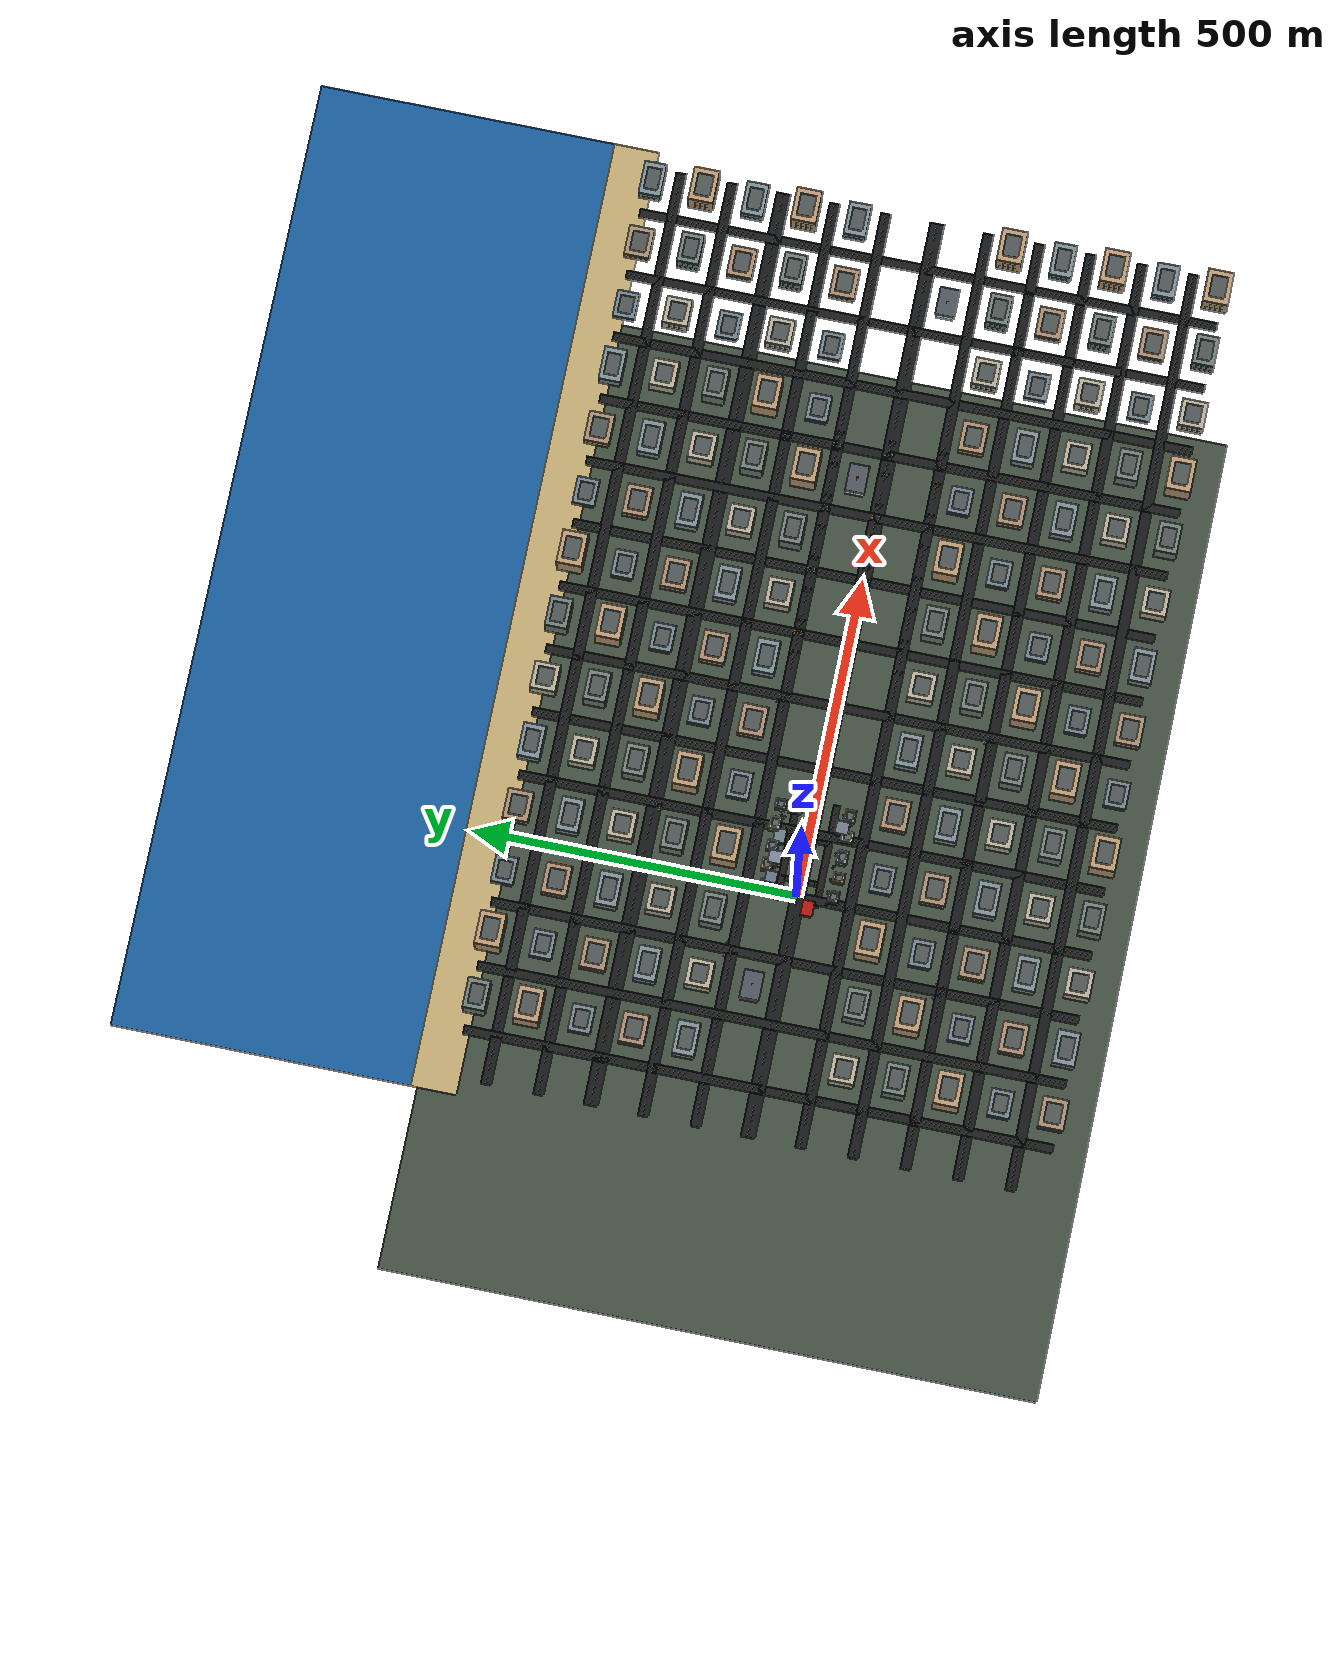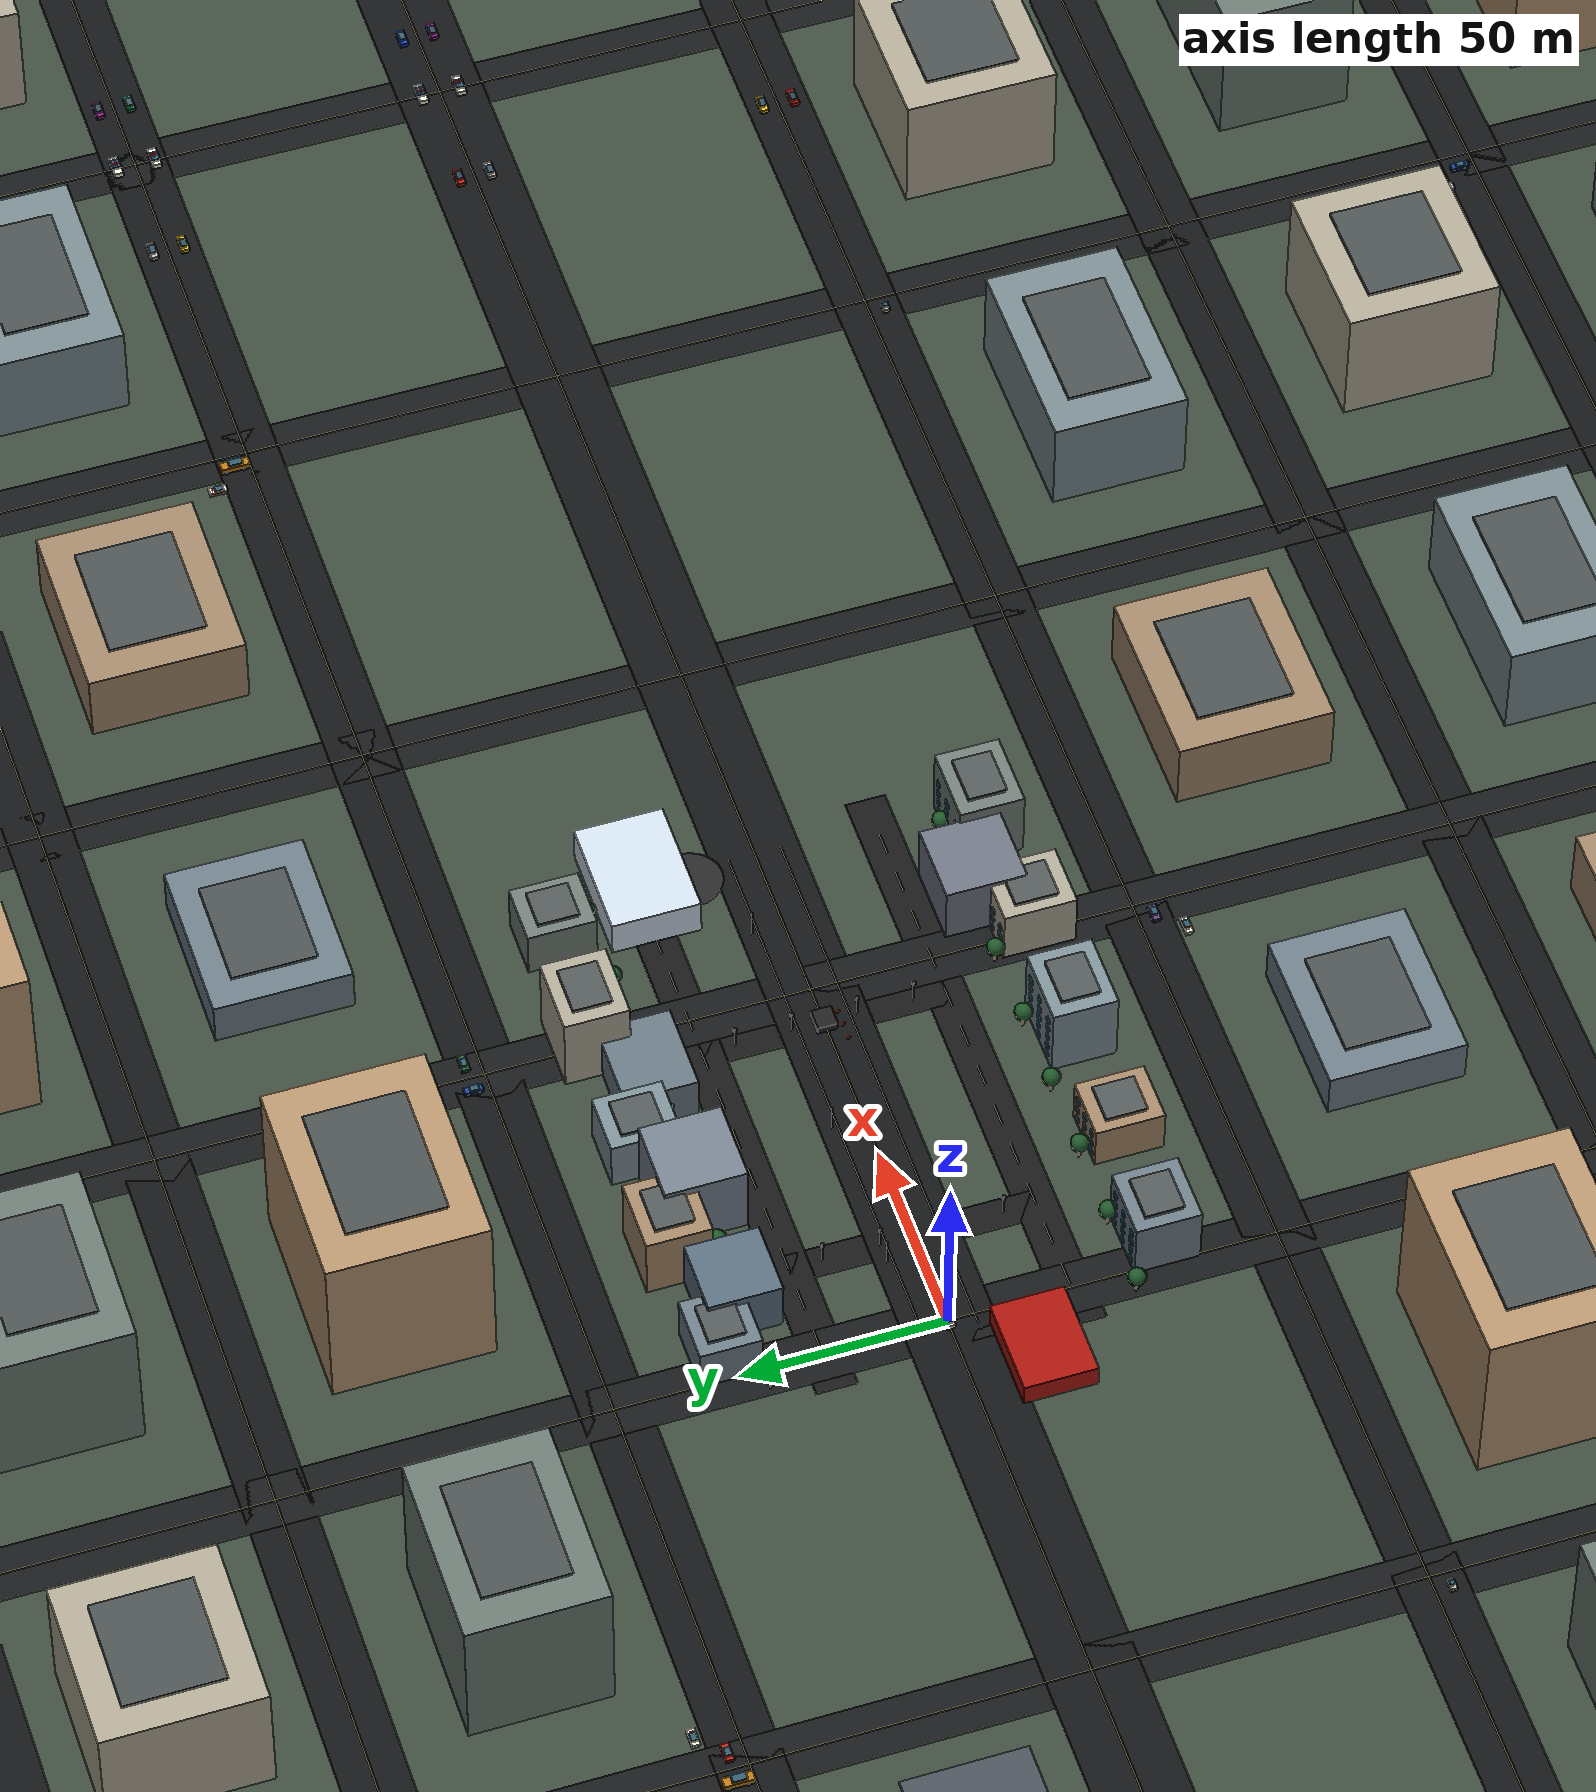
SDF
<?xml version="1.0"?>
<sdf version="1.9">

  <world name="smart_city">
    <plugin filename="gz-sim-physics-system" name="gz::sim::systems::Physics"/>
    <!-- Publish scene / entity state so the Gazebo GUI can render the world. -->
    <plugin filename="gz-sim-scene-broadcaster-system" name="gz::sim::systems::SceneBroadcaster"/>
    <plugin filename="gz-sim-user-commands-system" name="gz::sim::systems::UserCommands"/>
    <plugin filename="gz-sim-sensors-system" name="gz::sim::systems::Sensors">
      <render_engine>ogre2</render_engine>
    </plugin>

    <physics name="default_physics" type="ode">
      <max_step_size>0.005</max_step_size>
      <real_time_factor>1</real_time_factor>
    </physics>

    <scene>
      <ambient>0.35 0.35 0.35 1</ambient>
      <background>0.55 0.65 0.75 1</background>
      <shadows>false</shadows>
    </scene>

    <!-- MAIN ROAD NETWORK                                 -->

    <model name="main_road">
      <static>true</static>
      <link name="road">
        <visual name="asphalt">
          <pose>70 0 0.02 0 0 0</pose>
          <geometry>
            <box>
              <size>160 14 0.1</size>
            </box>
          </geometry>
          <material>
            <ambient>0.07 0.07 0.07 1</ambient>
            <diffuse>0.07 0.07 0.07 1</diffuse>
          </material>
        </visual>
      </link>
    </model>

    <!-- NORTH ALTERNATIVE ROAD -->
    <model name="north_road">
      <static>true</static>
      <link name="road">
        <visual name="asphalt">
          <pose>70 30 0.02 0 0 0</pose>
          <geometry>
            <box>
              <size>160 10 0.1</size>
            </box>
          </geometry>
          <material>
            <ambient>0.09 0.09 0.09 1</ambient>
          </material>
        </visual>
      </link>
    </model>

    <!-- SOUTH ALTERNATIVE ROAD -->
    <model name="south_road">
      <static>true</static>
      <link name="road">
        <visual name="asphalt">
          <pose>70 -30 0.02 0 0 0</pose>
          <geometry>
            <box>
              <size>160 10 0.1</size>
            </box>
          </geometry>
          <material>
            <ambient>0.09 0.09 0.09 1</ambient>
          </material>
        </visual>
      </link>
    </model>

    <!-- NORTH CONNECTORS -->
    <model name="north_connector_1">
      <static>true</static>
      <link name="road">
        <visual name="road_visual">
          <pose>25 15 0.02 0 0 1.5708</pose>
          <geometry>
            <box>
              <size>30 8 0.1</size>
            </box>
          </geometry>
          <material>
            <ambient>0.09 0.09 0.09 1</ambient>
          </material>
        </visual>
      </link>
    </model>

    <model name="north_connector_2">
      <static>true</static>
      <link name="road">
        <visual name="road_visual">
          <pose>90 15 0.02 0 0 1.5708</pose>
          <geometry>
            <box>
              <size>30 8 0.1</size>
            </box>
          </geometry>
          <material>
            <ambient>0.09 0.09 0.09 1</ambient>
          </material>
        </visual>
      </link>
    </model>

    <!-- SOUTH CONNECTORS -->
    <model name="south_connector_1">
      <static>true</static>
      <link name="road">
        <visual name="road_visual">
          <pose>25 -15 0.02 0 0 1.5708</pose>
          <geometry>
            <box>
              <size>30 8 0.1</size>
            </box>
          </geometry>
          <material>
            <ambient>0.09 0.09 0.09 1</ambient>
          </material>
        </visual>
      </link>
    </model>

    <model name="south_connector_2">
      <static>true</static>
      <link name="road">
        <visual name="road_visual">
          <pose>90 -15 0.02 0 0 1.5708</pose>
          <geometry>
            <box>
              <size>30 8 0.1</size>
            </box>
          </geometry>
          <material>
            <ambient>0.09 0.09 0.09 1</ambient>
          </material>
        </visual>
      </link>
    </model>

    <!-- HOSPITAL                                          -->

    <model name="hospital">
      <static>true</static>
      <pose>140 30 5 0 0 0</pose>

      <link name="building">

        <collision name="collision">
          <geometry>
            <box>
              <size>30 22 10</size>
            </box>
          </geometry>
        </collision>

        <visual name="building">
          <geometry>
            <box>
              <size>30 22 10</size>
            </box>
          </geometry>
          <material>
            <ambient>0.8 0.85 0.9 1</ambient>
            <diffuse>0.8 0.85 0.9 1</diffuse>
          </material>
        </visual>

      </link>
    </model>

    <!-- HOSPITAL HELIPAD -->
    <model name="helipad">
      <static>true</static>
      <pose>140 17 0.08 0 0 0</pose>
      <link name="pad">
        <visual name="visual">
          <geometry>
            <cylinder>
              <radius>8</radius>
              <length>0.15</length>
            </cylinder>
          </geometry>
          <material>
            <ambient>0.15 0.15 0.15 1</ambient>
          </material>
        </visual>
      </link>
    </model>

    <!-- EMERGENCY STATION                                 -->

    <model name="emergency_station">
      <static>true</static>
      <pose>-15 -18 3 0 0 0</pose>

      <link name="building">
        <collision name="collision">
          <geometry>
            <box>
              <size>24 18 6</size>
            </box>
          </geometry>
        </collision>

        <visual name="visual">
          <geometry>
            <box>
              <size>24 18 6</size>
            </box>
          </geometry>
          <material>
            <ambient>0.65 0.08 0.05 1</ambient>
            <diffuse>0.65 0.08 0.05 1</diffuse>
          </material>
        </visual>
      </link>
    </model>

    <!-- CITY BUILDINGS                                    -->

    <model name="building_1">
      <static>true</static>
      <pose>20 45 7 0 0 0</pose>
      <link name="building">
        <visual name="v">
          <geometry>
            <box><size>18 18 14</size></box>
          </geometry>
          <material>
            <ambient>0.35 0.42 0.48 1</ambient>
          </material>
        </visual>
      </link>
    </model>

    <model name="building_2">
      <static>true</static>
      <pose>50 45 10 0 0 0</pose>
      <link name="building">
        <visual name="v">
          <geometry>
            <box><size>20 20 20</size></box>
          </geometry>
          <material>
            <ambient>0.45 0.5 0.55 1</ambient>
          </material>
        </visual>
      </link>
    </model>

    <model name="building_3">
      <static>true</static>
      <pose>85 45 6 0 0 0</pose>
      <link name="building">
        <visual name="v">
          <geometry>
            <box><size>22 18 12</size></box>
          </geometry>
          <material>
            <ambient>0.4 0.46 0.5 1</ambient>
          </material>
        </visual>
      </link>
    </model>

    <model name="building_4">
      <static>true</static>
      <pose>115 -45 8 0 0 0</pose>
      <link name="building">
        <visual name="v">
          <geometry>
            <box><size>20 20 16</size></box>
          </geometry>
          <material>
            <ambient>0.42 0.45 0.5 1</ambient>
          </material>
        </visual>
      </link>
    </model>

    <!-- CRITICAL ROADBLOCK                                -->

    <model name="roadblock_vehicle">
      <static>true</static>
      <pose>90 0 1 0 0 0</pose>

      <link name="vehicle">

        <collision name="collision">
          <geometry>
            <box>
              <size>5.5 5.0 2.0</size>
            </box>
          </geometry>
        </collision>

        <visual name="vehicle">
          <geometry>
            <box>
              <size>5.5 5.0 2.0</size>
            </box>
          </geometry>
          <material>
            <ambient>0.12 0.12 0.12 1</ambient>
            <diffuse>0.12 0.12 0.12 1</diffuse>
          </material>
        </visual>

      </link>
    </model>

    <!-- ROADBLOCK CONES -->

    <model name="cone_1">
      <static>true</static>
      <pose>84 -4 0.5 0 0 0</pose>
      <link name="cone">
        <visual name="v">
          <geometry>
            <cone>
              <radius>0.5</radius>
              <length>1</length>
            </cone>
          </geometry>
          <material>
            <ambient>1 0.3 0 1</ambient>
            <diffuse>1 0.3 0 1</diffuse>
          </material>
        </visual>
      </link>
    </model>

    <model name="cone_2">
      <static>true</static>
      <pose>88 -4 0.5 0 0 0</pose>
      <link name="cone">
        <visual name="v">
          <geometry>
            <cone>
              <radius>0.5</radius>
              <length>1</length>
            </cone>
          </geometry>
          <material>
            <ambient>1 0.3 0 1</ambient>
            <diffuse>1 0.3 0 1</diffuse>
          </material>
        </visual>
      </link>
    </model>

    <model name="cone_3">
      <static>true</static>
      <pose>92 -4 0.5 0 0 0</pose>
      <link name="cone">
        <visual name="v">
          <geometry>
            <cone>
              <radius>0.5</radius>
              <length>1</length>
            </cone>
          </geometry>
          <material>
            <ambient>1 0.3 0 1</ambient>
            <diffuse>1 0.3 0 1</diffuse>
          </material>
        </visual>
      </link>
    </model>

    <!-- STREET LIGHTS                                     -->

    <model name="street_light_1">
      <static>true</static>
      <pose>20 8 4 0 0 0</pose>
      <link name="pole">
        <visual name="pole">
          <geometry>
            <cylinder>
              <radius>0.12</radius>
              <length>8</length>
            </cylinder>
          </geometry>
          <material>
            <ambient>0.15 0.15 0.15 1</ambient>
          </material>
        </visual>
      </link>
    </model>

    <model name="street_light_2">
      <static>true</static>
      <pose>60 8 4 0 0 0</pose>
      <link name="pole">
        <visual name="pole">
          <geometry>
            <cylinder>
              <radius>0.12</radius>
              <length>8</length>
            </cylinder>
          </geometry>
          <material>
            <ambient>0.15 0.15 0.15 1</ambient>
          </material>
        </visual>
      </link>
    </model>

    <model name="street_light_3">
      <static>true</static>
      <pose>120 8 4 0 0 0</pose>
      <link name="pole">
        <visual name="pole">
          <geometry>
            <cylinder>
              <radius>0.12</radius>
              <length>8</length>
            </cylinder>
          </geometry>
          <material>
            <ambient>0.15 0.15 0.15 1</ambient>
          </material>
        </visual>
      </link>
    </model>

    <!-- Lit ground slab keeps the road grid visible when viewed from any angle. -->
    <model name="city_ground">
      <static>true</static>
      <pose>70 0 -0.05 0 0 0</pose>
      <link name="ground">
        <collision name="collision"><geometry><box><size>1500 1000 0.1</size></box></geometry></collision>
        <visual name="pavement"><geometry><box><size>1500 1000 0.1</size></box></geometry>
          <material><ambient>0.24 0.29 0.24 1</ambient><diffuse>0.24 0.29 0.24 1</diffuse></material>
        </visual>
      </link>
    </model>
    <light name="city_sun" type="directional">
      <pose>0 0 100 0 0 0</pose><cast_shadows>true</cast_shadows>
      <diffuse>0.9 0.88 0.82 1</diffuse><specular>0.25 0.25 0.25 1</specular>
      <direction>-0.35 0.25 -0.9</direction>
      <attenuation><range>500</range><constant>0.8</constant><linear>0.001</linear><quadratic>0.0001</quadratic></attenuation>
    </light>

    <!-- Broken lane dividers and road edges make the three corridors legible. -->
    <model name="road_markings"><static>true</static><link name="paint">
      <visual name="dash_p0_4"><pose>4 0 0.075 0 0 0</pose><geometry><box><size>6 0.22 0.01</size></box></geometry><material><ambient>0.88 0.82 0.58 1</ambient><diffuse>0.88 0.82 0.58 1</diffuse></material></visual>
      <visual name="dash_p0_16"><pose>16 0 0.075 0 0 0</pose><geometry><box><size>6 0.22 0.01</size></box></geometry><material><ambient>0.88 0.82 0.58 1</ambient><diffuse>0.88 0.82 0.58 1</diffuse></material></visual>
      <visual name="dash_p0_28"><pose>28 0 0.075 0 0 0</pose><geometry><box><size>6 0.22 0.01</size></box></geometry><material><ambient>0.88 0.82 0.58 1</ambient><diffuse>0.88 0.82 0.58 1</diffuse></material></visual>
      <visual name="dash_p0_40"><pose>40 0 0.075 0 0 0</pose><geometry><box><size>6 0.22 0.01</size></box></geometry><material><ambient>0.88 0.82 0.58 1</ambient><diffuse>0.88 0.82 0.58 1</diffuse></material></visual>
      <visual name="dash_p0_52"><pose>52 0 0.075 0 0 0</pose><geometry><box><size>6 0.22 0.01</size></box></geometry><material><ambient>0.88 0.82 0.58 1</ambient><diffuse>0.88 0.82 0.58 1</diffuse></material></visual>
      <visual name="dash_p0_64"><pose>64 0 0.075 0 0 0</pose><geometry><box><size>6 0.22 0.01</size></box></geometry><material><ambient>0.88 0.82 0.58 1</ambient><diffuse>0.88 0.82 0.58 1</diffuse></material></visual>
      <visual name="dash_p0_76"><pose>76 0 0.075 0 0 0</pose><geometry><box><size>6 0.22 0.01</size></box></geometry><material><ambient>0.88 0.82 0.58 1</ambient><diffuse>0.88 0.82 0.58 1</diffuse></material></visual>
      <visual name="dash_p0_88"><pose>88 0 0.075 0 0 0</pose><geometry><box><size>6 0.22 0.01</size></box></geometry><material><ambient>0.88 0.82 0.58 1</ambient><diffuse>0.88 0.82 0.58 1</diffuse></material></visual>
      <visual name="dash_p0_100"><pose>100 0 0.075 0 0 0</pose><geometry><box><size>6 0.22 0.01</size></box></geometry><material><ambient>0.88 0.82 0.58 1</ambient><diffuse>0.88 0.82 0.58 1</diffuse></material></visual>
      <visual name="dash_p0_112"><pose>112 0 0.075 0 0 0</pose><geometry><box><size>6 0.22 0.01</size></box></geometry><material><ambient>0.88 0.82 0.58 1</ambient><diffuse>0.88 0.82 0.58 1</diffuse></material></visual>
      <visual name="dash_p0_124"><pose>124 0 0.075 0 0 0</pose><geometry><box><size>6 0.22 0.01</size></box></geometry><material><ambient>0.88 0.82 0.58 1</ambient><diffuse>0.88 0.82 0.58 1</diffuse></material></visual>
      <visual name="dash_p0_136"><pose>136 0 0.075 0 0 0</pose><geometry><box><size>6 0.22 0.01</size></box></geometry><material><ambient>0.88 0.82 0.58 1</ambient><diffuse>0.88 0.82 0.58 1</diffuse></material></visual>
      <visual name="dash_p30_4"><pose>4 30 0.075 0 0 0</pose><geometry><box><size>6 0.22 0.01</size></box></geometry><material><ambient>0.88 0.82 0.58 1</ambient><diffuse>0.88 0.82 0.58 1</diffuse></material></visual>
      <visual name="dash_p30_16"><pose>16 30 0.075 0 0 0</pose><geometry><box><size>6 0.22 0.01</size></box></geometry><material><ambient>0.88 0.82 0.58 1</ambient><diffuse>0.88 0.82 0.58 1</diffuse></material></visual>
      <visual name="dash_p30_28"><pose>28 30 0.075 0 0 0</pose><geometry><box><size>6 0.22 0.01</size></box></geometry><material><ambient>0.88 0.82 0.58 1</ambient><diffuse>0.88 0.82 0.58 1</diffuse></material></visual>
      <visual name="dash_p30_40"><pose>40 30 0.075 0 0 0</pose><geometry><box><size>6 0.22 0.01</size></box></geometry><material><ambient>0.88 0.82 0.58 1</ambient><diffuse>0.88 0.82 0.58 1</diffuse></material></visual>
      <visual name="dash_p30_52"><pose>52 30 0.075 0 0 0</pose><geometry><box><size>6 0.22 0.01</size></box></geometry><material><ambient>0.88 0.82 0.58 1</ambient><diffuse>0.88 0.82 0.58 1</diffuse></material></visual>
      <visual name="dash_p30_64"><pose>64 30 0.075 0 0 0</pose><geometry><box><size>6 0.22 0.01</size></box></geometry><material><ambient>0.88 0.82 0.58 1</ambient><diffuse>0.88 0.82 0.58 1</diffuse></material></visual>
      <visual name="dash_p30_76"><pose>76 30 0.075 0 0 0</pose><geometry><box><size>6 0.22 0.01</size></box></geometry><material><ambient>0.88 0.82 0.58 1</ambient><diffuse>0.88 0.82 0.58 1</diffuse></material></visual>
      <visual name="dash_p30_88"><pose>88 30 0.075 0 0 0</pose><geometry><box><size>6 0.22 0.01</size></box></geometry><material><ambient>0.88 0.82 0.58 1</ambient><diffuse>0.88 0.82 0.58 1</diffuse></material></visual>
      <visual name="dash_p30_100"><pose>100 30 0.075 0 0 0</pose><geometry><box><size>6 0.22 0.01</size></box></geometry><material><ambient>0.88 0.82 0.58 1</ambient><diffuse>0.88 0.82 0.58 1</diffuse></material></visual>
      <visual name="dash_p30_112"><pose>112 30 0.075 0 0 0</pose><geometry><box><size>6 0.22 0.01</size></box></geometry><material><ambient>0.88 0.82 0.58 1</ambient><diffuse>0.88 0.82 0.58 1</diffuse></material></visual>
      <visual name="dash_p30_124"><pose>124 30 0.075 0 0 0</pose><geometry><box><size>6 0.22 0.01</size></box></geometry><material><ambient>0.88 0.82 0.58 1</ambient><diffuse>0.88 0.82 0.58 1</diffuse></material></visual>
      <visual name="dash_p30_136"><pose>136 30 0.075 0 0 0</pose><geometry><box><size>6 0.22 0.01</size></box></geometry><material><ambient>0.88 0.82 0.58 1</ambient><diffuse>0.88 0.82 0.58 1</diffuse></material></visual>
      <visual name="dash_m30_4"><pose>4 -30 0.075 0 0 0</pose><geometry><box><size>6 0.22 0.01</size></box></geometry><material><ambient>0.88 0.82 0.58 1</ambient><diffuse>0.88 0.82 0.58 1</diffuse></material></visual>
      <visual name="dash_m30_16"><pose>16 -30 0.075 0 0 0</pose><geometry><box><size>6 0.22 0.01</size></box></geometry><material><ambient>0.88 0.82 0.58 1</ambient><diffuse>0.88 0.82 0.58 1</diffuse></material></visual>
      <visual name="dash_m30_28"><pose>28 -30 0.075 0 0 0</pose><geometry><box><size>6 0.22 0.01</size></box></geometry><material><ambient>0.88 0.82 0.58 1</ambient><diffuse>0.88 0.82 0.58 1</diffuse></material></visual>
      <visual name="dash_m30_40"><pose>40 -30 0.075 0 0 0</pose><geometry><box><size>6 0.22 0.01</size></box></geometry><material><ambient>0.88 0.82 0.58 1</ambient><diffuse>0.88 0.82 0.58 1</diffuse></material></visual>
      <visual name="dash_m30_52"><pose>52 -30 0.075 0 0 0</pose><geometry><box><size>6 0.22 0.01</size></box></geometry><material><ambient>0.88 0.82 0.58 1</ambient><diffuse>0.88 0.82 0.58 1</diffuse></material></visual>
      <visual name="dash_m30_64"><pose>64 -30 0.075 0 0 0</pose><geometry><box><size>6 0.22 0.01</size></box></geometry><material><ambient>0.88 0.82 0.58 1</ambient><diffuse>0.88 0.82 0.58 1</diffuse></material></visual>
      <visual name="dash_m30_76"><pose>76 -30 0.075 0 0 0</pose><geometry><box><size>6 0.22 0.01</size></box></geometry><material><ambient>0.88 0.82 0.58 1</ambient><diffuse>0.88 0.82 0.58 1</diffuse></material></visual>
      <visual name="dash_m30_88"><pose>88 -30 0.075 0 0 0</pose><geometry><box><size>6 0.22 0.01</size></box></geometry><material><ambient>0.88 0.82 0.58 1</ambient><diffuse>0.88 0.82 0.58 1</diffuse></material></visual>
      <visual name="dash_m30_100"><pose>100 -30 0.075 0 0 0</pose><geometry><box><size>6 0.22 0.01</size></box></geometry><material><ambient>0.88 0.82 0.58 1</ambient><diffuse>0.88 0.82 0.58 1</diffuse></material></visual>
      <visual name="dash_m30_112"><pose>112 -30 0.075 0 0 0</pose><geometry><box><size>6 0.22 0.01</size></box></geometry><material><ambient>0.88 0.82 0.58 1</ambient><diffuse>0.88 0.82 0.58 1</diffuse></material></visual>
      <visual name="dash_m30_124"><pose>124 -30 0.075 0 0 0</pose><geometry><box><size>6 0.22 0.01</size></box></geometry><material><ambient>0.88 0.82 0.58 1</ambient><diffuse>0.88 0.82 0.58 1</diffuse></material></visual>
      <visual name="dash_m30_136"><pose>136 -30 0.075 0 0 0</pose><geometry><box><size>6 0.22 0.01</size></box></geometry><material><ambient>0.88 0.82 0.58 1</ambient><diffuse>0.88 0.82 0.58 1</diffuse></material></visual>
      <visual name="main_edge_s"><pose>70 -6.5 0.075 0 0 0</pose><geometry><box><size>145 0.18 0.01</size></box></geometry><material><ambient>0.78 0.78 0.72 1</ambient><diffuse>0.78 0.78 0.72 1</diffuse></material></visual>
      <visual name="main_edge_n"><pose>70 6.5 0.075 0 0 0</pose><geometry><box><size>145 0.18 0.01</size></box></geometry><material><ambient>0.78 0.78 0.72 1</ambient><diffuse>0.78 0.78 0.72 1</diffuse></material></visual>
    </link></model>

    <!-- Mixed-use blocks on both sides of the road grid, with simple window panels. -->
    <model name="city_block_01"><static>true</static><pose>8 52 0 0 0 0</pose><link name="building">
      <visual name="facade"><pose>0 0 6.0 0 0 0</pose><geometry><box><size>16 15 12</size></box></geometry><material><ambient>0.42 0.48 0.52 1</ambient><diffuse>0.42 0.48 0.52 1</diffuse></material></visual>
      <visual name="window_0_-512"><pose>-5.12 -7.525 2.00 0 0 0</pose><geometry><box><size>2.2 0.08 1.7</size></box></geometry><material><ambient>0.22 0.60 0.76 1</ambient><diffuse>0.22 0.60 0.76 1</diffuse><specular>0.35 0.35 0.35 1</specular></material></visual>
      <visual name="window_0_0"><pose>0.00 -7.525 2.00 0 0 0</pose><geometry><box><size>2.2 0.08 1.7</size></box></geometry><material><ambient>0.22 0.60 0.76 1</ambient><diffuse>0.22 0.60 0.76 1</diffuse><specular>0.35 0.35 0.35 1</specular></material></visual>
      <visual name="window_0_512"><pose>5.12 -7.525 2.00 0 0 0</pose><geometry><box><size>2.2 0.08 1.7</size></box></geometry><material><ambient>0.22 0.60 0.76 1</ambient><diffuse>0.22 0.60 0.76 1</diffuse><specular>0.35 0.35 0.35 1</specular></material></visual>
      <visual name="window_1_-512"><pose>-5.12 -7.525 5.20 0 0 0</pose><geometry><box><size>2.2 0.08 1.7</size></box></geometry><material><ambient>0.22 0.60 0.76 1</ambient><diffuse>0.22 0.60 0.76 1</diffuse><specular>0.35 0.35 0.35 1</specular></material></visual>
      <visual name="window_1_0"><pose>0.00 -7.525 5.20 0 0 0</pose><geometry><box><size>2.2 0.08 1.7</size></box></geometry><material><ambient>0.22 0.60 0.76 1</ambient><diffuse>0.22 0.60 0.76 1</diffuse><specular>0.35 0.35 0.35 1</specular></material></visual>
      <visual name="window_1_512"><pose>5.12 -7.525 5.20 0 0 0</pose><geometry><box><size>2.2 0.08 1.7</size></box></geometry><material><ambient>0.22 0.60 0.76 1</ambient><diffuse>0.22 0.60 0.76 1</diffuse><specular>0.35 0.35 0.35 1</specular></material></visual>
      <visual name="window_2_-512"><pose>-5.12 -7.525 8.40 0 0 0</pose><geometry><box><size>2.2 0.08 1.7</size></box></geometry><material><ambient>0.22 0.60 0.76 1</ambient><diffuse>0.22 0.60 0.76 1</diffuse><specular>0.35 0.35 0.35 1</specular></material></visual>
      <visual name="window_2_0"><pose>0.00 -7.525 8.40 0 0 0</pose><geometry><box><size>2.2 0.08 1.7</size></box></geometry><material><ambient>0.22 0.60 0.76 1</ambient><diffuse>0.22 0.60 0.76 1</diffuse><specular>0.35 0.35 0.35 1</specular></material></visual>
      <visual name="window_2_512"><pose>5.12 -7.525 8.40 0 0 0</pose><geometry><box><size>2.2 0.08 1.7</size></box></geometry><material><ambient>0.22 0.60 0.76 1</ambient><diffuse>0.22 0.60 0.76 1</diffuse><specular>0.35 0.35 0.35 1</specular></material></visual>
      <visual name="roof"><pose>0 0 12.4 0 0 0</pose><geometry><box><size>10.4 9.0 0.8</size></box></geometry><material><ambient>0.32 0.34 0.34 1</ambient><diffuse>0.32 0.34 0.34 1</diffuse></material></visual>
    </link></model>
    <model name="city_block_02"><static>true</static><pose>38 55 0 0 0 0</pose><link name="building">
      <visual name="facade"><pose>0 0 9.0 0 0 0</pose><geometry><box><size>18 16 18</size></box></geometry><material><ambient>0.63 0.52 0.40 1</ambient><diffuse>0.63 0.52 0.40 1</diffuse></material></visual>
      <visual name="window_0_-576"><pose>-5.76 -8.025 2.00 0 0 0</pose><geometry><box><size>2.2 0.08 1.7</size></box></geometry><material><ambient>0.25 0.62 0.78 1</ambient><diffuse>0.25 0.62 0.78 1</diffuse><specular>0.35 0.35 0.35 1</specular></material></visual>
      <visual name="window_0_0"><pose>0.00 -8.025 2.00 0 0 0</pose><geometry><box><size>2.2 0.08 1.7</size></box></geometry><material><ambient>0.25 0.62 0.78 1</ambient><diffuse>0.25 0.62 0.78 1</diffuse><specular>0.35 0.35 0.35 1</specular></material></visual>
      <visual name="window_0_576"><pose>5.76 -8.025 2.00 0 0 0</pose><geometry><box><size>2.2 0.08 1.7</size></box></geometry><material><ambient>0.25 0.62 0.78 1</ambient><diffuse>0.25 0.62 0.78 1</diffuse><specular>0.35 0.35 0.35 1</specular></material></visual>
      <visual name="window_1_-576"><pose>-5.76 -8.025 5.20 0 0 0</pose><geometry><box><size>2.2 0.08 1.7</size></box></geometry><material><ambient>0.25 0.62 0.78 1</ambient><diffuse>0.25 0.62 0.78 1</diffuse><specular>0.35 0.35 0.35 1</specular></material></visual>
      <visual name="window_1_0"><pose>0.00 -8.025 5.20 0 0 0</pose><geometry><box><size>2.2 0.08 1.7</size></box></geometry><material><ambient>0.25 0.62 0.78 1</ambient><diffuse>0.25 0.62 0.78 1</diffuse><specular>0.35 0.35 0.35 1</specular></material></visual>
      <visual name="window_1_576"><pose>5.76 -8.025 5.20 0 0 0</pose><geometry><box><size>2.2 0.08 1.7</size></box></geometry><material><ambient>0.25 0.62 0.78 1</ambient><diffuse>0.25 0.62 0.78 1</diffuse><specular>0.35 0.35 0.35 1</specular></material></visual>
      <visual name="window_2_-576"><pose>-5.76 -8.025 8.40 0 0 0</pose><geometry><box><size>2.2 0.08 1.7</size></box></geometry><material><ambient>0.25 0.62 0.78 1</ambient><diffuse>0.25 0.62 0.78 1</diffuse><specular>0.35 0.35 0.35 1</specular></material></visual>
      <visual name="window_2_0"><pose>0.00 -8.025 8.40 0 0 0</pose><geometry><box><size>2.2 0.08 1.7</size></box></geometry><material><ambient>0.25 0.62 0.78 1</ambient><diffuse>0.25 0.62 0.78 1</diffuse><specular>0.35 0.35 0.35 1</specular></material></visual>
      <visual name="window_2_576"><pose>5.76 -8.025 8.40 0 0 0</pose><geometry><box><size>2.2 0.08 1.7</size></box></geometry><material><ambient>0.25 0.62 0.78 1</ambient><diffuse>0.25 0.62 0.78 1</diffuse><specular>0.35 0.35 0.35 1</specular></material></visual>
      <visual name="window_3_-576"><pose>-5.76 -8.025 11.60 0 0 0</pose><geometry><box><size>2.2 0.08 1.7</size></box></geometry><material><ambient>0.25 0.62 0.78 1</ambient><diffuse>0.25 0.62 0.78 1</diffuse><specular>0.35 0.35 0.35 1</specular></material></visual>
      <visual name="window_3_0"><pose>0.00 -8.025 11.60 0 0 0</pose><geometry><box><size>2.2 0.08 1.7</size></box></geometry><material><ambient>0.25 0.62 0.78 1</ambient><diffuse>0.25 0.62 0.78 1</diffuse><specular>0.35 0.35 0.35 1</specular></material></visual>
      <visual name="window_3_576"><pose>5.76 -8.025 11.60 0 0 0</pose><geometry><box><size>2.2 0.08 1.7</size></box></geometry><material><ambient>0.25 0.62 0.78 1</ambient><diffuse>0.25 0.62 0.78 1</diffuse><specular>0.35 0.35 0.35 1</specular></material></visual>
      <visual name="roof"><pose>0 0 18.4 0 0 0</pose><geometry><box><size>11.7 9.6 0.8</size></box></geometry><material><ambient>0.32 0.34 0.34 1</ambient><diffuse>0.32 0.34 0.34 1</diffuse></material></visual>
    </link></model>
    <model name="city_block_03"><static>true</static><pose>68 53 0 0 0 0</pose><link name="building">
      <visual name="facade"><pose>0 0 7.0 0 0 0</pose><geometry><box><size>15 17 14</size></box></geometry><material><ambient>0.48 0.55 0.58 1</ambient><diffuse>0.48 0.55 0.58 1</diffuse></material></visual>
      <visual name="window_0_-480"><pose>-4.80 -8.525 2.00 0 0 0</pose><geometry><box><size>2.2 0.08 1.7</size></box></geometry><material><ambient>0.30 0.68 0.82 1</ambient><diffuse>0.30 0.68 0.82 1</diffuse><specular>0.35 0.35 0.35 1</specular></material></visual>
      <visual name="window_0_0"><pose>0.00 -8.525 2.00 0 0 0</pose><geometry><box><size>2.2 0.08 1.7</size></box></geometry><material><ambient>0.30 0.68 0.82 1</ambient><diffuse>0.30 0.68 0.82 1</diffuse><specular>0.35 0.35 0.35 1</specular></material></visual>
      <visual name="window_0_480"><pose>4.80 -8.525 2.00 0 0 0</pose><geometry><box><size>2.2 0.08 1.7</size></box></geometry><material><ambient>0.30 0.68 0.82 1</ambient><diffuse>0.30 0.68 0.82 1</diffuse><specular>0.35 0.35 0.35 1</specular></material></visual>
      <visual name="window_1_-480"><pose>-4.80 -8.525 5.20 0 0 0</pose><geometry><box><size>2.2 0.08 1.7</size></box></geometry><material><ambient>0.30 0.68 0.82 1</ambient><diffuse>0.30 0.68 0.82 1</diffuse><specular>0.35 0.35 0.35 1</specular></material></visual>
      <visual name="window_1_0"><pose>0.00 -8.525 5.20 0 0 0</pose><geometry><box><size>2.2 0.08 1.7</size></box></geometry><material><ambient>0.30 0.68 0.82 1</ambient><diffuse>0.30 0.68 0.82 1</diffuse><specular>0.35 0.35 0.35 1</specular></material></visual>
      <visual name="window_1_480"><pose>4.80 -8.525 5.20 0 0 0</pose><geometry><box><size>2.2 0.08 1.7</size></box></geometry><material><ambient>0.30 0.68 0.82 1</ambient><diffuse>0.30 0.68 0.82 1</diffuse><specular>0.35 0.35 0.35 1</specular></material></visual>
      <visual name="window_2_-480"><pose>-4.80 -8.525 8.40 0 0 0</pose><geometry><box><size>2.2 0.08 1.7</size></box></geometry><material><ambient>0.30 0.68 0.82 1</ambient><diffuse>0.30 0.68 0.82 1</diffuse><specular>0.35 0.35 0.35 1</specular></material></visual>
      <visual name="window_2_0"><pose>0.00 -8.525 8.40 0 0 0</pose><geometry><box><size>2.2 0.08 1.7</size></box></geometry><material><ambient>0.30 0.68 0.82 1</ambient><diffuse>0.30 0.68 0.82 1</diffuse><specular>0.35 0.35 0.35 1</specular></material></visual>
      <visual name="window_2_480"><pose>4.80 -8.525 8.40 0 0 0</pose><geometry><box><size>2.2 0.08 1.7</size></box></geometry><material><ambient>0.30 0.68 0.82 1</ambient><diffuse>0.30 0.68 0.82 1</diffuse><specular>0.35 0.35 0.35 1</specular></material></visual>
      <visual name="roof"><pose>0 0 14.4 0 0 0</pose><geometry><box><size>9.8 10.2 0.8</size></box></geometry><material><ambient>0.32 0.34 0.34 1</ambient><diffuse>0.32 0.34 0.34 1</diffuse></material></visual>
    </link></model>
    <model name="city_block_04"><static>true</static><pose>101 55 0 0 0 0</pose><link name="building">
      <visual name="facade"><pose>0 0 11.0 0 0 0</pose><geometry><box><size>19 16 22</size></box></geometry><material><ambient>0.67 0.65 0.58 1</ambient><diffuse>0.67 0.65 0.58 1</diffuse></material></visual>
      <visual name="window_0_-608"><pose>-6.08 -8.025 2.00 0 0 0</pose><geometry><box><size>2.2 0.08 1.7</size></box></geometry><material><ambient>0.24 0.55 0.72 1</ambient><diffuse>0.24 0.55 0.72 1</diffuse><specular>0.35 0.35 0.35 1</specular></material></visual>
      <visual name="window_0_0"><pose>0.00 -8.025 2.00 0 0 0</pose><geometry><box><size>2.2 0.08 1.7</size></box></geometry><material><ambient>0.24 0.55 0.72 1</ambient><diffuse>0.24 0.55 0.72 1</diffuse><specular>0.35 0.35 0.35 1</specular></material></visual>
      <visual name="window_0_608"><pose>6.08 -8.025 2.00 0 0 0</pose><geometry><box><size>2.2 0.08 1.7</size></box></geometry><material><ambient>0.24 0.55 0.72 1</ambient><diffuse>0.24 0.55 0.72 1</diffuse><specular>0.35 0.35 0.35 1</specular></material></visual>
      <visual name="window_1_-608"><pose>-6.08 -8.025 5.20 0 0 0</pose><geometry><box><size>2.2 0.08 1.7</size></box></geometry><material><ambient>0.24 0.55 0.72 1</ambient><diffuse>0.24 0.55 0.72 1</diffuse><specular>0.35 0.35 0.35 1</specular></material></visual>
      <visual name="window_1_0"><pose>0.00 -8.025 5.20 0 0 0</pose><geometry><box><size>2.2 0.08 1.7</size></box></geometry><material><ambient>0.24 0.55 0.72 1</ambient><diffuse>0.24 0.55 0.72 1</diffuse><specular>0.35 0.35 0.35 1</specular></material></visual>
      <visual name="window_1_608"><pose>6.08 -8.025 5.20 0 0 0</pose><geometry><box><size>2.2 0.08 1.7</size></box></geometry><material><ambient>0.24 0.55 0.72 1</ambient><diffuse>0.24 0.55 0.72 1</diffuse><specular>0.35 0.35 0.35 1</specular></material></visual>
      <visual name="window_2_-608"><pose>-6.08 -8.025 8.40 0 0 0</pose><geometry><box><size>2.2 0.08 1.7</size></box></geometry><material><ambient>0.24 0.55 0.72 1</ambient><diffuse>0.24 0.55 0.72 1</diffuse><specular>0.35 0.35 0.35 1</specular></material></visual>
      <visual name="window_2_0"><pose>0.00 -8.025 8.40 0 0 0</pose><geometry><box><size>2.2 0.08 1.7</size></box></geometry><material><ambient>0.24 0.55 0.72 1</ambient><diffuse>0.24 0.55 0.72 1</diffuse><specular>0.35 0.35 0.35 1</specular></material></visual>
      <visual name="window_2_608"><pose>6.08 -8.025 8.40 0 0 0</pose><geometry><box><size>2.2 0.08 1.7</size></box></geometry><material><ambient>0.24 0.55 0.72 1</ambient><diffuse>0.24 0.55 0.72 1</diffuse><specular>0.35 0.35 0.35 1</specular></material></visual>
      <visual name="window_3_-608"><pose>-6.08 -8.025 11.60 0 0 0</pose><geometry><box><size>2.2 0.08 1.7</size></box></geometry><material><ambient>0.24 0.55 0.72 1</ambient><diffuse>0.24 0.55 0.72 1</diffuse><specular>0.35 0.35 0.35 1</specular></material></visual>
      <visual name="window_3_0"><pose>0.00 -8.025 11.60 0 0 0</pose><geometry><box><size>2.2 0.08 1.7</size></box></geometry><material><ambient>0.24 0.55 0.72 1</ambient><diffuse>0.24 0.55 0.72 1</diffuse><specular>0.35 0.35 0.35 1</specular></material></visual>
      <visual name="window_3_608"><pose>6.08 -8.025 11.60 0 0 0</pose><geometry><box><size>2.2 0.08 1.7</size></box></geometry><material><ambient>0.24 0.55 0.72 1</ambient><diffuse>0.24 0.55 0.72 1</diffuse><specular>0.35 0.35 0.35 1</specular></material></visual>
      <visual name="window_4_-608"><pose>-6.08 -8.025 14.80 0 0 0</pose><geometry><box><size>2.2 0.08 1.7</size></box></geometry><material><ambient>0.24 0.55 0.72 1</ambient><diffuse>0.24 0.55 0.72 1</diffuse><specular>0.35 0.35 0.35 1</specular></material></visual>
      <visual name="window_4_0"><pose>0.00 -8.025 14.80 0 0 0</pose><geometry><box><size>2.2 0.08 1.7</size></box></geometry><material><ambient>0.24 0.55 0.72 1</ambient><diffuse>0.24 0.55 0.72 1</diffuse><specular>0.35 0.35 0.35 1</specular></material></visual>
      <visual name="window_4_608"><pose>6.08 -8.025 14.80 0 0 0</pose><geometry><box><size>2.2 0.08 1.7</size></box></geometry><material><ambient>0.24 0.55 0.72 1</ambient><diffuse>0.24 0.55 0.72 1</diffuse><specular>0.35 0.35 0.35 1</specular></material></visual>
      <visual name="roof"><pose>0 0 22.4 0 0 0</pose><geometry><box><size>12.3 9.6 0.8</size></box></geometry><material><ambient>0.32 0.34 0.34 1</ambient><diffuse>0.32 0.34 0.34 1</diffuse></material></visual>
    </link></model>
    <model name="city_block_05"><static>true</static><pose>133 53 0 0 0 0</pose><link name="building">
      <visual name="facade"><pose>0 0 6.5 0 0 0</pose><geometry><box><size>15 17 13</size></box></geometry><material><ambient>0.43 0.48 0.45 1</ambient><diffuse>0.43 0.48 0.45 1</diffuse></material></visual>
      <visual name="window_0_-480"><pose>-4.80 -8.525 2.00 0 0 0</pose><geometry><box><size>2.2 0.08 1.7</size></box></geometry><material><ambient>0.31 0.64 0.78 1</ambient><diffuse>0.31 0.64 0.78 1</diffuse><specular>0.35 0.35 0.35 1</specular></material></visual>
      <visual name="window_0_0"><pose>0.00 -8.525 2.00 0 0 0</pose><geometry><box><size>2.2 0.08 1.7</size></box></geometry><material><ambient>0.31 0.64 0.78 1</ambient><diffuse>0.31 0.64 0.78 1</diffuse><specular>0.35 0.35 0.35 1</specular></material></visual>
      <visual name="window_0_480"><pose>4.80 -8.525 2.00 0 0 0</pose><geometry><box><size>2.2 0.08 1.7</size></box></geometry><material><ambient>0.31 0.64 0.78 1</ambient><diffuse>0.31 0.64 0.78 1</diffuse><specular>0.35 0.35 0.35 1</specular></material></visual>
      <visual name="window_1_-480"><pose>-4.80 -8.525 5.20 0 0 0</pose><geometry><box><size>2.2 0.08 1.7</size></box></geometry><material><ambient>0.31 0.64 0.78 1</ambient><diffuse>0.31 0.64 0.78 1</diffuse><specular>0.35 0.35 0.35 1</specular></material></visual>
      <visual name="window_1_0"><pose>0.00 -8.525 5.20 0 0 0</pose><geometry><box><size>2.2 0.08 1.7</size></box></geometry><material><ambient>0.31 0.64 0.78 1</ambient><diffuse>0.31 0.64 0.78 1</diffuse><specular>0.35 0.35 0.35 1</specular></material></visual>
      <visual name="window_1_480"><pose>4.80 -8.525 5.20 0 0 0</pose><geometry><box><size>2.2 0.08 1.7</size></box></geometry><material><ambient>0.31 0.64 0.78 1</ambient><diffuse>0.31 0.64 0.78 1</diffuse><specular>0.35 0.35 0.35 1</specular></material></visual>
      <visual name="window_2_-480"><pose>-4.80 -8.525 8.40 0 0 0</pose><geometry><box><size>2.2 0.08 1.7</size></box></geometry><material><ambient>0.31 0.64 0.78 1</ambient><diffuse>0.31 0.64 0.78 1</diffuse><specular>0.35 0.35 0.35 1</specular></material></visual>
      <visual name="window_2_0"><pose>0.00 -8.525 8.40 0 0 0</pose><geometry><box><size>2.2 0.08 1.7</size></box></geometry><material><ambient>0.31 0.64 0.78 1</ambient><diffuse>0.31 0.64 0.78 1</diffuse><specular>0.35 0.35 0.35 1</specular></material></visual>
      <visual name="window_2_480"><pose>4.80 -8.525 8.40 0 0 0</pose><geometry><box><size>2.2 0.08 1.7</size></box></geometry><material><ambient>0.31 0.64 0.78 1</ambient><diffuse>0.31 0.64 0.78 1</diffuse><specular>0.35 0.35 0.35 1</specular></material></visual>
      <visual name="roof"><pose>0 0 13.4 0 0 0</pose><geometry><box><size>9.8 10.2 0.8</size></box></geometry><material><ambient>0.32 0.34 0.34 1</ambient><diffuse>0.32 0.34 0.34 1</diffuse></material></visual>
    </link></model>
    <model name="city_block_06"><static>true</static><pose>8 -53 0 0 0 0</pose><link name="building">
      <visual name="facade"><pose>0 0 8.0 0 0 0</pose><geometry><box><size>17 16 16</size></box></geometry><material><ambient>0.42 0.48 0.52 1</ambient><diffuse>0.42 0.48 0.52 1</diffuse></material></visual>
      <visual name="window_0_-544"><pose>-5.44 8.025 2.00 0 0 0</pose><geometry><box><size>2.2 0.08 1.7</size></box></geometry><material><ambient>0.22 0.60 0.76 1</ambient><diffuse>0.22 0.60 0.76 1</diffuse><specular>0.35 0.35 0.35 1</specular></material></visual>
      <visual name="window_0_0"><pose>0.00 8.025 2.00 0 0 0</pose><geometry><box><size>2.2 0.08 1.7</size></box></geometry><material><ambient>0.22 0.60 0.76 1</ambient><diffuse>0.22 0.60 0.76 1</diffuse><specular>0.35 0.35 0.35 1</specular></material></visual>
      <visual name="window_0_544"><pose>5.44 8.025 2.00 0 0 0</pose><geometry><box><size>2.2 0.08 1.7</size></box></geometry><material><ambient>0.22 0.60 0.76 1</ambient><diffuse>0.22 0.60 0.76 1</diffuse><specular>0.35 0.35 0.35 1</specular></material></visual>
      <visual name="window_1_-544"><pose>-5.44 8.025 5.20 0 0 0</pose><geometry><box><size>2.2 0.08 1.7</size></box></geometry><material><ambient>0.22 0.60 0.76 1</ambient><diffuse>0.22 0.60 0.76 1</diffuse><specular>0.35 0.35 0.35 1</specular></material></visual>
      <visual name="window_1_0"><pose>0.00 8.025 5.20 0 0 0</pose><geometry><box><size>2.2 0.08 1.7</size></box></geometry><material><ambient>0.22 0.60 0.76 1</ambient><diffuse>0.22 0.60 0.76 1</diffuse><specular>0.35 0.35 0.35 1</specular></material></visual>
      <visual name="window_1_544"><pose>5.44 8.025 5.20 0 0 0</pose><geometry><box><size>2.2 0.08 1.7</size></box></geometry><material><ambient>0.22 0.60 0.76 1</ambient><diffuse>0.22 0.60 0.76 1</diffuse><specular>0.35 0.35 0.35 1</specular></material></visual>
      <visual name="window_2_-544"><pose>-5.44 8.025 8.40 0 0 0</pose><geometry><box><size>2.2 0.08 1.7</size></box></geometry><material><ambient>0.22 0.60 0.76 1</ambient><diffuse>0.22 0.60 0.76 1</diffuse><specular>0.35 0.35 0.35 1</specular></material></visual>
      <visual name="window_2_0"><pose>0.00 8.025 8.40 0 0 0</pose><geometry><box><size>2.2 0.08 1.7</size></box></geometry><material><ambient>0.22 0.60 0.76 1</ambient><diffuse>0.22 0.60 0.76 1</diffuse><specular>0.35 0.35 0.35 1</specular></material></visual>
      <visual name="window_2_544"><pose>5.44 8.025 8.40 0 0 0</pose><geometry><box><size>2.2 0.08 1.7</size></box></geometry><material><ambient>0.22 0.60 0.76 1</ambient><diffuse>0.22 0.60 0.76 1</diffuse><specular>0.35 0.35 0.35 1</specular></material></visual>
      <visual name="window_3_-544"><pose>-5.44 8.025 11.60 0 0 0</pose><geometry><box><size>2.2 0.08 1.7</size></box></geometry><material><ambient>0.22 0.60 0.76 1</ambient><diffuse>0.22 0.60 0.76 1</diffuse><specular>0.35 0.35 0.35 1</specular></material></visual>
      <visual name="window_3_0"><pose>0.00 8.025 11.60 0 0 0</pose><geometry><box><size>2.2 0.08 1.7</size></box></geometry><material><ambient>0.22 0.60 0.76 1</ambient><diffuse>0.22 0.60 0.76 1</diffuse><specular>0.35 0.35 0.35 1</specular></material></visual>
      <visual name="window_3_544"><pose>5.44 8.025 11.60 0 0 0</pose><geometry><box><size>2.2 0.08 1.7</size></box></geometry><material><ambient>0.22 0.60 0.76 1</ambient><diffuse>0.22 0.60 0.76 1</diffuse><specular>0.35 0.35 0.35 1</specular></material></visual>
      <visual name="roof"><pose>0 0 16.4 0 0 0</pose><geometry><box><size>11.1 9.6 0.8</size></box></geometry><material><ambient>0.32 0.34 0.34 1</ambient><diffuse>0.32 0.34 0.34 1</diffuse></material></visual>
    </link></model>
    <model name="city_block_07"><static>true</static><pose>39 -55 0 0 0 0</pose><link name="building">
      <visual name="facade"><pose>0 0 6.0 0 0 0</pose><geometry><box><size>15 17 12</size></box></geometry><material><ambient>0.63 0.52 0.40 1</ambient><diffuse>0.63 0.52 0.40 1</diffuse></material></visual>
      <visual name="window_0_-480"><pose>-4.80 8.525 2.00 0 0 0</pose><geometry><box><size>2.2 0.08 1.7</size></box></geometry><material><ambient>0.25 0.62 0.78 1</ambient><diffuse>0.25 0.62 0.78 1</diffuse><specular>0.35 0.35 0.35 1</specular></material></visual>
      <visual name="window_0_0"><pose>0.00 8.525 2.00 0 0 0</pose><geometry><box><size>2.2 0.08 1.7</size></box></geometry><material><ambient>0.25 0.62 0.78 1</ambient><diffuse>0.25 0.62 0.78 1</diffuse><specular>0.35 0.35 0.35 1</specular></material></visual>
      <visual name="window_0_480"><pose>4.80 8.525 2.00 0 0 0</pose><geometry><box><size>2.2 0.08 1.7</size></box></geometry><material><ambient>0.25 0.62 0.78 1</ambient><diffuse>0.25 0.62 0.78 1</diffuse><specular>0.35 0.35 0.35 1</specular></material></visual>
      <visual name="window_1_-480"><pose>-4.80 8.525 5.20 0 0 0</pose><geometry><box><size>2.2 0.08 1.7</size></box></geometry><material><ambient>0.25 0.62 0.78 1</ambient><diffuse>0.25 0.62 0.78 1</diffuse><specular>0.35 0.35 0.35 1</specular></material></visual>
      <visual name="window_1_0"><pose>0.00 8.525 5.20 0 0 0</pose><geometry><box><size>2.2 0.08 1.7</size></box></geometry><material><ambient>0.25 0.62 0.78 1</ambient><diffuse>0.25 0.62 0.78 1</diffuse><specular>0.35 0.35 0.35 1</specular></material></visual>
      <visual name="window_1_480"><pose>4.80 8.525 5.20 0 0 0</pose><geometry><box><size>2.2 0.08 1.7</size></box></geometry><material><ambient>0.25 0.62 0.78 1</ambient><diffuse>0.25 0.62 0.78 1</diffuse><specular>0.35 0.35 0.35 1</specular></material></visual>
      <visual name="window_2_-480"><pose>-4.80 8.525 8.40 0 0 0</pose><geometry><box><size>2.2 0.08 1.7</size></box></geometry><material><ambient>0.25 0.62 0.78 1</ambient><diffuse>0.25 0.62 0.78 1</diffuse><specular>0.35 0.35 0.35 1</specular></material></visual>
      <visual name="window_2_0"><pose>0.00 8.525 8.40 0 0 0</pose><geometry><box><size>2.2 0.08 1.7</size></box></geometry><material><ambient>0.25 0.62 0.78 1</ambient><diffuse>0.25 0.62 0.78 1</diffuse><specular>0.35 0.35 0.35 1</specular></material></visual>
      <visual name="window_2_480"><pose>4.80 8.525 8.40 0 0 0</pose><geometry><box><size>2.2 0.08 1.7</size></box></geometry><material><ambient>0.25 0.62 0.78 1</ambient><diffuse>0.25 0.62 0.78 1</diffuse><specular>0.35 0.35 0.35 1</specular></material></visual>
      <visual name="roof"><pose>0 0 12.4 0 0 0</pose><geometry><box><size>9.8 10.2 0.8</size></box></geometry><material><ambient>0.32 0.34 0.34 1</ambient><diffuse>0.32 0.34 0.34 1</diffuse></material></visual>
    </link></model>
    <model name="city_block_08"><static>true</static><pose>70 -54 0 0 0 0</pose><link name="building">
      <visual name="facade"><pose>0 0 10.0 0 0 0</pose><geometry><box><size>19 16 20</size></box></geometry><material><ambient>0.48 0.55 0.58 1</ambient><diffuse>0.48 0.55 0.58 1</diffuse></material></visual>
      <visual name="window_0_-608"><pose>-6.08 8.025 2.00 0 0 0</pose><geometry><box><size>2.2 0.08 1.7</size></box></geometry><material><ambient>0.30 0.68 0.82 1</ambient><diffuse>0.30 0.68 0.82 1</diffuse><specular>0.35 0.35 0.35 1</specular></material></visual>
      <visual name="window_0_0"><pose>0.00 8.025 2.00 0 0 0</pose><geometry><box><size>2.2 0.08 1.7</size></box></geometry><material><ambient>0.30 0.68 0.82 1</ambient><diffuse>0.30 0.68 0.82 1</diffuse><specular>0.35 0.35 0.35 1</specular></material></visual>
      <visual name="window_0_608"><pose>6.08 8.025 2.00 0 0 0</pose><geometry><box><size>2.2 0.08 1.7</size></box></geometry><material><ambient>0.30 0.68 0.82 1</ambient><diffuse>0.30 0.68 0.82 1</diffuse><specular>0.35 0.35 0.35 1</specular></material></visual>
      <visual name="window_1_-608"><pose>-6.08 8.025 5.20 0 0 0</pose><geometry><box><size>2.2 0.08 1.7</size></box></geometry><material><ambient>0.30 0.68 0.82 1</ambient><diffuse>0.30 0.68 0.82 1</diffuse><specular>0.35 0.35 0.35 1</specular></material></visual>
      <visual name="window_1_0"><pose>0.00 8.025 5.20 0 0 0</pose><geometry><box><size>2.2 0.08 1.7</size></box></geometry><material><ambient>0.30 0.68 0.82 1</ambient><diffuse>0.30 0.68 0.82 1</diffuse><specular>0.35 0.35 0.35 1</specular></material></visual>
      <visual name="window_1_608"><pose>6.08 8.025 5.20 0 0 0</pose><geometry><box><size>2.2 0.08 1.7</size></box></geometry><material><ambient>0.30 0.68 0.82 1</ambient><diffuse>0.30 0.68 0.82 1</diffuse><specular>0.35 0.35 0.35 1</specular></material></visual>
      <visual name="window_2_-608"><pose>-6.08 8.025 8.40 0 0 0</pose><geometry><box><size>2.2 0.08 1.7</size></box></geometry><material><ambient>0.30 0.68 0.82 1</ambient><diffuse>0.30 0.68 0.82 1</diffuse><specular>0.35 0.35 0.35 1</specular></material></visual>
      <visual name="window_2_0"><pose>0.00 8.025 8.40 0 0 0</pose><geometry><box><size>2.2 0.08 1.7</size></box></geometry><material><ambient>0.30 0.68 0.82 1</ambient><diffuse>0.30 0.68 0.82 1</diffuse><specular>0.35 0.35 0.35 1</specular></material></visual>
      <visual name="window_2_608"><pose>6.08 8.025 8.40 0 0 0</pose><geometry><box><size>2.2 0.08 1.7</size></box></geometry><material><ambient>0.30 0.68 0.82 1</ambient><diffuse>0.30 0.68 0.82 1</diffuse><specular>0.35 0.35 0.35 1</specular></material></visual>
      <visual name="window_3_-608"><pose>-6.08 8.025 11.60 0 0 0</pose><geometry><box><size>2.2 0.08 1.7</size></box></geometry><material><ambient>0.30 0.68 0.82 1</ambient><diffuse>0.30 0.68 0.82 1</diffuse><specular>0.35 0.35 0.35 1</specular></material></visual>
      <visual name="window_3_0"><pose>0.00 8.025 11.60 0 0 0</pose><geometry><box><size>2.2 0.08 1.7</size></box></geometry><material><ambient>0.30 0.68 0.82 1</ambient><diffuse>0.30 0.68 0.82 1</diffuse><specular>0.35 0.35 0.35 1</specular></material></visual>
      <visual name="window_3_608"><pose>6.08 8.025 11.60 0 0 0</pose><geometry><box><size>2.2 0.08 1.7</size></box></geometry><material><ambient>0.30 0.68 0.82 1</ambient><diffuse>0.30 0.68 0.82 1</diffuse><specular>0.35 0.35 0.35 1</specular></material></visual>
      <visual name="window_4_-608"><pose>-6.08 8.025 14.80 0 0 0</pose><geometry><box><size>2.2 0.08 1.7</size></box></geometry><material><ambient>0.30 0.68 0.82 1</ambient><diffuse>0.30 0.68 0.82 1</diffuse><specular>0.35 0.35 0.35 1</specular></material></visual>
      <visual name="window_4_0"><pose>0.00 8.025 14.80 0 0 0</pose><geometry><box><size>2.2 0.08 1.7</size></box></geometry><material><ambient>0.30 0.68 0.82 1</ambient><diffuse>0.30 0.68 0.82 1</diffuse><specular>0.35 0.35 0.35 1</specular></material></visual>
      <visual name="window_4_608"><pose>6.08 8.025 14.80 0 0 0</pose><geometry><box><size>2.2 0.08 1.7</size></box></geometry><material><ambient>0.30 0.68 0.82 1</ambient><diffuse>0.30 0.68 0.82 1</diffuse><specular>0.35 0.35 0.35 1</specular></material></visual>
      <visual name="roof"><pose>0 0 20.4 0 0 0</pose><geometry><box><size>12.3 9.6 0.8</size></box></geometry><material><ambient>0.32 0.34 0.34 1</ambient><diffuse>0.32 0.34 0.34 1</diffuse></material></visual>
    </link></model>
    <model name="city_block_09"><static>true</static><pose>103 -55 0 0 0 0</pose><link name="building">
      <visual name="facade"><pose>0 0 7.5 0 0 0</pose><geometry><box><size>16 18 15</size></box></geometry><material><ambient>0.67 0.65 0.58 1</ambient><diffuse>0.67 0.65 0.58 1</diffuse></material></visual>
      <visual name="window_0_-512"><pose>-5.12 9.025 2.00 0 0 0</pose><geometry><box><size>2.2 0.08 1.7</size></box></geometry><material><ambient>0.24 0.55 0.72 1</ambient><diffuse>0.24 0.55 0.72 1</diffuse><specular>0.35 0.35 0.35 1</specular></material></visual>
      <visual name="window_0_0"><pose>0.00 9.025 2.00 0 0 0</pose><geometry><box><size>2.2 0.08 1.7</size></box></geometry><material><ambient>0.24 0.55 0.72 1</ambient><diffuse>0.24 0.55 0.72 1</diffuse><specular>0.35 0.35 0.35 1</specular></material></visual>
      <visual name="window_0_512"><pose>5.12 9.025 2.00 0 0 0</pose><geometry><box><size>2.2 0.08 1.7</size></box></geometry><material><ambient>0.24 0.55 0.72 1</ambient><diffuse>0.24 0.55 0.72 1</diffuse><specular>0.35 0.35 0.35 1</specular></material></visual>
      <visual name="window_1_-512"><pose>-5.12 9.025 5.20 0 0 0</pose><geometry><box><size>2.2 0.08 1.7</size></box></geometry><material><ambient>0.24 0.55 0.72 1</ambient><diffuse>0.24 0.55 0.72 1</diffuse><specular>0.35 0.35 0.35 1</specular></material></visual>
      <visual name="window_1_0"><pose>0.00 9.025 5.20 0 0 0</pose><geometry><box><size>2.2 0.08 1.7</size></box></geometry><material><ambient>0.24 0.55 0.72 1</ambient><diffuse>0.24 0.55 0.72 1</diffuse><specular>0.35 0.35 0.35 1</specular></material></visual>
      <visual name="window_1_512"><pose>5.12 9.025 5.20 0 0 0</pose><geometry><box><size>2.2 0.08 1.7</size></box></geometry><material><ambient>0.24 0.55 0.72 1</ambient><diffuse>0.24 0.55 0.72 1</diffuse><specular>0.35 0.35 0.35 1</specular></material></visual>
      <visual name="window_2_-512"><pose>-5.12 9.025 8.40 0 0 0</pose><geometry><box><size>2.2 0.08 1.7</size></box></geometry><material><ambient>0.24 0.55 0.72 1</ambient><diffuse>0.24 0.55 0.72 1</diffuse><specular>0.35 0.35 0.35 1</specular></material></visual>
      <visual name="window_2_0"><pose>0.00 9.025 8.40 0 0 0</pose><geometry><box><size>2.2 0.08 1.7</size></box></geometry><material><ambient>0.24 0.55 0.72 1</ambient><diffuse>0.24 0.55 0.72 1</diffuse><specular>0.35 0.35 0.35 1</specular></material></visual>
      <visual name="window_2_512"><pose>5.12 9.025 8.40 0 0 0</pose><geometry><box><size>2.2 0.08 1.7</size></box></geometry><material><ambient>0.24 0.55 0.72 1</ambient><diffuse>0.24 0.55 0.72 1</diffuse><specular>0.35 0.35 0.35 1</specular></material></visual>
      <visual name="roof"><pose>0 0 15.4 0 0 0</pose><geometry><box><size>10.4 10.8 0.8</size></box></geometry><material><ambient>0.32 0.34 0.34 1</ambient><diffuse>0.32 0.34 0.34 1</diffuse></material></visual>
    </link></model>
    <model name="city_block_10"><static>true</static><pose>134 -53 0 0 0 0</pose><link name="building">
      <visual name="facade"><pose>0 0 9.5 0 0 0</pose><geometry><box><size>19 16 19</size></box></geometry><material><ambient>0.43 0.48 0.45 1</ambient><diffuse>0.43 0.48 0.45 1</diffuse></material></visual>
      <visual name="window_0_-608"><pose>-6.08 8.025 2.00 0 0 0</pose><geometry><box><size>2.2 0.08 1.7</size></box></geometry><material><ambient>0.31 0.64 0.78 1</ambient><diffuse>0.31 0.64 0.78 1</diffuse><specular>0.35 0.35 0.35 1</specular></material></visual>
      <visual name="window_0_0"><pose>0.00 8.025 2.00 0 0 0</pose><geometry><box><size>2.2 0.08 1.7</size></box></geometry><material><ambient>0.31 0.64 0.78 1</ambient><diffuse>0.31 0.64 0.78 1</diffuse><specular>0.35 0.35 0.35 1</specular></material></visual>
      <visual name="window_0_608"><pose>6.08 8.025 2.00 0 0 0</pose><geometry><box><size>2.2 0.08 1.7</size></box></geometry><material><ambient>0.31 0.64 0.78 1</ambient><diffuse>0.31 0.64 0.78 1</diffuse><specular>0.35 0.35 0.35 1</specular></material></visual>
      <visual name="window_1_-608"><pose>-6.08 8.025 5.20 0 0 0</pose><geometry><box><size>2.2 0.08 1.7</size></box></geometry><material><ambient>0.31 0.64 0.78 1</ambient><diffuse>0.31 0.64 0.78 1</diffuse><specular>0.35 0.35 0.35 1</specular></material></visual>
      <visual name="window_1_0"><pose>0.00 8.025 5.20 0 0 0</pose><geometry><box><size>2.2 0.08 1.7</size></box></geometry><material><ambient>0.31 0.64 0.78 1</ambient><diffuse>0.31 0.64 0.78 1</diffuse><specular>0.35 0.35 0.35 1</specular></material></visual>
      <visual name="window_1_608"><pose>6.08 8.025 5.20 0 0 0</pose><geometry><box><size>2.2 0.08 1.7</size></box></geometry><material><ambient>0.31 0.64 0.78 1</ambient><diffuse>0.31 0.64 0.78 1</diffuse><specular>0.35 0.35 0.35 1</specular></material></visual>
      <visual name="window_2_-608"><pose>-6.08 8.025 8.40 0 0 0</pose><geometry><box><size>2.2 0.08 1.7</size></box></geometry><material><ambient>0.31 0.64 0.78 1</ambient><diffuse>0.31 0.64 0.78 1</diffuse><specular>0.35 0.35 0.35 1</specular></material></visual>
      <visual name="window_2_0"><pose>0.00 8.025 8.40 0 0 0</pose><geometry><box><size>2.2 0.08 1.7</size></box></geometry><material><ambient>0.31 0.64 0.78 1</ambient><diffuse>0.31 0.64 0.78 1</diffuse><specular>0.35 0.35 0.35 1</specular></material></visual>
      <visual name="window_2_608"><pose>6.08 8.025 8.40 0 0 0</pose><geometry><box><size>2.2 0.08 1.7</size></box></geometry><material><ambient>0.31 0.64 0.78 1</ambient><diffuse>0.31 0.64 0.78 1</diffuse><specular>0.35 0.35 0.35 1</specular></material></visual>
      <visual name="window_3_-608"><pose>-6.08 8.025 11.60 0 0 0</pose><geometry><box><size>2.2 0.08 1.7</size></box></geometry><material><ambient>0.31 0.64 0.78 1</ambient><diffuse>0.31 0.64 0.78 1</diffuse><specular>0.35 0.35 0.35 1</specular></material></visual>
      <visual name="window_3_0"><pose>0.00 8.025 11.60 0 0 0</pose><geometry><box><size>2.2 0.08 1.7</size></box></geometry><material><ambient>0.31 0.64 0.78 1</ambient><diffuse>0.31 0.64 0.78 1</diffuse><specular>0.35 0.35 0.35 1</specular></material></visual>
      <visual name="window_3_608"><pose>6.08 8.025 11.60 0 0 0</pose><geometry><box><size>2.2 0.08 1.7</size></box></geometry><material><ambient>0.31 0.64 0.78 1</ambient><diffuse>0.31 0.64 0.78 1</diffuse><specular>0.35 0.35 0.35 1</specular></material></visual>
      <visual name="roof"><pose>0 0 19.4 0 0 0</pose><geometry><box><size>12.3 9.6 0.8</size></box></geometry><material><ambient>0.32 0.34 0.34 1</ambient><diffuse>0.32 0.34 0.34 1</diffuse></material></visual>
    </link></model>

    <!-- Small tree-lined verges outside the drivable corridors. -->
    <model name="street_tree_01"><static>true</static><pose>-5 44 0 0 0 0</pose><link name="tree">
      <visual name="trunk"><pose>0 0 2 0 0 0</pose><geometry><cylinder><radius>0.35</radius><length>4</length></cylinder></geometry><material><ambient>0.30 0.18 0.08 1</ambient><diffuse>0.30 0.18 0.08 1</diffuse></material></visual>
      <visual name="crown"><pose>0 0 5 0 0 0</pose><geometry><sphere><radius>2.2</radius></sphere></geometry><material><ambient>0.12 0.34 0.16 1</ambient><diffuse>0.12 0.34 0.16 1</diffuse></material></visual>
    </link></model>
    <model name="street_tree_02"><static>true</static><pose>15 44 0 0 0 0</pose><link name="tree">
      <visual name="trunk"><pose>0 0 2 0 0 0</pose><geometry><cylinder><radius>0.35</radius><length>4</length></cylinder></geometry><material><ambient>0.30 0.18 0.08 1</ambient><diffuse>0.30 0.18 0.08 1</diffuse></material></visual>
      <visual name="crown"><pose>0 0 5 0 0 0</pose><geometry><sphere><radius>2.2</radius></sphere></geometry><material><ambient>0.12 0.34 0.16 1</ambient><diffuse>0.12 0.34 0.16 1</diffuse></material></visual>
    </link></model>
    <model name="street_tree_03"><static>true</static><pose>35 44 0 0 0 0</pose><link name="tree">
      <visual name="trunk"><pose>0 0 2 0 0 0</pose><geometry><cylinder><radius>0.35</radius><length>4</length></cylinder></geometry><material><ambient>0.30 0.18 0.08 1</ambient><diffuse>0.30 0.18 0.08 1</diffuse></material></visual>
      <visual name="crown"><pose>0 0 5 0 0 0</pose><geometry><sphere><radius>2.2</radius></sphere></geometry><material><ambient>0.12 0.34 0.16 1</ambient><diffuse>0.12 0.34 0.16 1</diffuse></material></visual>
    </link></model>
    <model name="street_tree_04"><static>true</static><pose>55 44 0 0 0 0</pose><link name="tree">
      <visual name="trunk"><pose>0 0 2 0 0 0</pose><geometry><cylinder><radius>0.35</radius><length>4</length></cylinder></geometry><material><ambient>0.30 0.18 0.08 1</ambient><diffuse>0.30 0.18 0.08 1</diffuse></material></visual>
      <visual name="crown"><pose>0 0 5 0 0 0</pose><geometry><sphere><radius>2.2</radius></sphere></geometry><material><ambient>0.12 0.34 0.16 1</ambient><diffuse>0.12 0.34 0.16 1</diffuse></material></visual>
    </link></model>
    <model name="street_tree_05"><static>true</static><pose>75 44 0 0 0 0</pose><link name="tree">
      <visual name="trunk"><pose>0 0 2 0 0 0</pose><geometry><cylinder><radius>0.35</radius><length>4</length></cylinder></geometry><material><ambient>0.30 0.18 0.08 1</ambient><diffuse>0.30 0.18 0.08 1</diffuse></material></visual>
      <visual name="crown"><pose>0 0 5 0 0 0</pose><geometry><sphere><radius>2.2</radius></sphere></geometry><material><ambient>0.12 0.34 0.16 1</ambient><diffuse>0.12 0.34 0.16 1</diffuse></material></visual>
    </link></model>
    <model name="street_tree_06"><static>true</static><pose>95 44 0 0 0 0</pose><link name="tree">
      <visual name="trunk"><pose>0 0 2 0 0 0</pose><geometry><cylinder><radius>0.35</radius><length>4</length></cylinder></geometry><material><ambient>0.30 0.18 0.08 1</ambient><diffuse>0.30 0.18 0.08 1</diffuse></material></visual>
      <visual name="crown"><pose>0 0 5 0 0 0</pose><geometry><sphere><radius>2.2</radius></sphere></geometry><material><ambient>0.12 0.34 0.16 1</ambient><diffuse>0.12 0.34 0.16 1</diffuse></material></visual>
    </link></model>
    <model name="street_tree_07"><static>true</static><pose>115 44 0 0 0 0</pose><link name="tree">
      <visual name="trunk"><pose>0 0 2 0 0 0</pose><geometry><cylinder><radius>0.35</radius><length>4</length></cylinder></geometry><material><ambient>0.30 0.18 0.08 1</ambient><diffuse>0.30 0.18 0.08 1</diffuse></material></visual>
      <visual name="crown"><pose>0 0 5 0 0 0</pose><geometry><sphere><radius>2.2</radius></sphere></geometry><material><ambient>0.12 0.34 0.16 1</ambient><diffuse>0.12 0.34 0.16 1</diffuse></material></visual>
    </link></model>
    <model name="street_tree_08"><static>true</static><pose>135 44 0 0 0 0</pose><link name="tree">
      <visual name="trunk"><pose>0 0 2 0 0 0</pose><geometry><cylinder><radius>0.35</radius><length>4</length></cylinder></geometry><material><ambient>0.30 0.18 0.08 1</ambient><diffuse>0.30 0.18 0.08 1</diffuse></material></visual>
      <visual name="crown"><pose>0 0 5 0 0 0</pose><geometry><sphere><radius>2.2</radius></sphere></geometry><material><ambient>0.12 0.34 0.16 1</ambient><diffuse>0.12 0.34 0.16 1</diffuse></material></visual>
    </link></model>
    <model name="street_tree_09"><static>true</static><pose>-5 -44 0 0 0 0</pose><link name="tree">
      <visual name="trunk"><pose>0 0 2 0 0 0</pose><geometry><cylinder><radius>0.35</radius><length>4</length></cylinder></geometry><material><ambient>0.30 0.18 0.08 1</ambient><diffuse>0.30 0.18 0.08 1</diffuse></material></visual>
      <visual name="crown"><pose>0 0 5 0 0 0</pose><geometry><sphere><radius>2.2</radius></sphere></geometry><material><ambient>0.12 0.34 0.16 1</ambient><diffuse>0.12 0.34 0.16 1</diffuse></material></visual>
    </link></model>
    <model name="street_tree_10"><static>true</static><pose>15 -44 0 0 0 0</pose><link name="tree">
      <visual name="trunk"><pose>0 0 2 0 0 0</pose><geometry><cylinder><radius>0.35</radius><length>4</length></cylinder></geometry><material><ambient>0.30 0.18 0.08 1</ambient><diffuse>0.30 0.18 0.08 1</diffuse></material></visual>
      <visual name="crown"><pose>0 0 5 0 0 0</pose><geometry><sphere><radius>2.2</radius></sphere></geometry><material><ambient>0.12 0.34 0.16 1</ambient><diffuse>0.12 0.34 0.16 1</diffuse></material></visual>
    </link></model>
    <model name="street_tree_11"><static>true</static><pose>35 -44 0 0 0 0</pose><link name="tree">
      <visual name="trunk"><pose>0 0 2 0 0 0</pose><geometry><cylinder><radius>0.35</radius><length>4</length></cylinder></geometry><material><ambient>0.30 0.18 0.08 1</ambient><diffuse>0.30 0.18 0.08 1</diffuse></material></visual>
      <visual name="crown"><pose>0 0 5 0 0 0</pose><geometry><sphere><radius>2.2</radius></sphere></geometry><material><ambient>0.12 0.34 0.16 1</ambient><diffuse>0.12 0.34 0.16 1</diffuse></material></visual>
    </link></model>
    <model name="street_tree_12"><static>true</static><pose>55 -44 0 0 0 0</pose><link name="tree">
      <visual name="trunk"><pose>0 0 2 0 0 0</pose><geometry><cylinder><radius>0.35</radius><length>4</length></cylinder></geometry><material><ambient>0.30 0.18 0.08 1</ambient><diffuse>0.30 0.18 0.08 1</diffuse></material></visual>
      <visual name="crown"><pose>0 0 5 0 0 0</pose><geometry><sphere><radius>2.2</radius></sphere></geometry><material><ambient>0.12 0.34 0.16 1</ambient><diffuse>0.12 0.34 0.16 1</diffuse></material></visual>
    </link></model>
    <model name="street_tree_13"><static>true</static><pose>75 -44 0 0 0 0</pose><link name="tree">
      <visual name="trunk"><pose>0 0 2 0 0 0</pose><geometry><cylinder><radius>0.35</radius><length>4</length></cylinder></geometry><material><ambient>0.30 0.18 0.08 1</ambient><diffuse>0.30 0.18 0.08 1</diffuse></material></visual>
      <visual name="crown"><pose>0 0 5 0 0 0</pose><geometry><sphere><radius>2.2</radius></sphere></geometry><material><ambient>0.12 0.34 0.16 1</ambient><diffuse>0.12 0.34 0.16 1</diffuse></material></visual>
    </link></model>
    <model name="street_tree_14"><static>true</static><pose>95 -44 0 0 0 0</pose><link name="tree">
      <visual name="trunk"><pose>0 0 2 0 0 0</pose><geometry><cylinder><radius>0.35</radius><length>4</length></cylinder></geometry><material><ambient>0.30 0.18 0.08 1</ambient><diffuse>0.30 0.18 0.08 1</diffuse></material></visual>
      <visual name="crown"><pose>0 0 5 0 0 0</pose><geometry><sphere><radius>2.2</radius></sphere></geometry><material><ambient>0.12 0.34 0.16 1</ambient><diffuse>0.12 0.34 0.16 1</diffuse></material></visual>
    </link></model>
    <model name="street_tree_15"><static>true</static><pose>115 -44 0 0 0 0</pose><link name="tree">
      <visual name="trunk"><pose>0 0 2 0 0 0</pose><geometry><cylinder><radius>0.35</radius><length>4</length></cylinder></geometry><material><ambient>0.30 0.18 0.08 1</ambient><diffuse>0.30 0.18 0.08 1</diffuse></material></visual>
      <visual name="crown"><pose>0 0 5 0 0 0</pose><geometry><sphere><radius>2.2</radius></sphere></geometry><material><ambient>0.12 0.34 0.16 1</ambient><diffuse>0.12 0.34 0.16 1</diffuse></material></visual>
    </link></model>
    <model name="street_tree_16"><static>true</static><pose>135 -44 0 0 0 0</pose><link name="tree">
      <visual name="trunk"><pose>0 0 2 0 0 0</pose><geometry><cylinder><radius>0.35</radius><length>4</length></cylinder></geometry><material><ambient>0.30 0.18 0.08 1</ambient><diffuse>0.30 0.18 0.08 1</diffuse></material></visual>
      <visual name="crown"><pose>0 0 5 0 0 0</pose><geometry><sphere><radius>2.2</radius></sphere></geometry><material><ambient>0.12 0.34 0.16 1</ambient><diffuse>0.12 0.34 0.16 1</diffuse></material></visual>
    </link></model>

    <!-- Signal heads mark the connector intersections; these are visual only. -->
    <model name="traffic_signal_1"><static>true</static><pose>25 8 0 0 0 0</pose><link name="signal">
      <visual name="mast"><pose>0 0 3 0 0 0</pose><geometry><cylinder><radius>0.12</radius><length>6</length></cylinder></geometry><material><ambient>0.12 0.12 0.12 1</ambient><diffuse>0.12 0.12 0.12 1</diffuse></material></visual>
      <visual name="head"><pose>0 0 5.8 0 0 0</pose><geometry><box><size>0.55 0.65 1.5</size></box></geometry><material><ambient>0.16 0.17 0.16 1</ambient><diffuse>0.16 0.17 0.16 1</diffuse></material></visual>
      <visual name="red_lamp"><pose>0 -0.34 6.2 0 0 0</pose><geometry><sphere><radius>0.16</radius></sphere></geometry><material><ambient>0.9 0.04 0.02 1</ambient><diffuse>0.9 0.04 0.02 1</diffuse><emissive>0.6 0 0 1</emissive></material></visual>
      <visual name="green_lamp"><pose>0 -0.34 5.35 0 0 0</pose><geometry><sphere><radius>0.16</radius></sphere></geometry><material><ambient>0.02 0.7 0.12 1</ambient><diffuse>0.02 0.7 0.12 1</diffuse></material></visual>
    </link></model>
    <model name="traffic_signal_2"><static>true</static><pose>25 22 0 0 0 0</pose><link name="signal">
      <visual name="mast"><pose>0 0 3 0 0 0</pose><geometry><cylinder><radius>0.12</radius><length>6</length></cylinder></geometry><material><ambient>0.12 0.12 0.12 1</ambient><diffuse>0.12 0.12 0.12 1</diffuse></material></visual>
      <visual name="head"><pose>0 0 5.8 0 0 0</pose><geometry><box><size>0.55 0.65 1.5</size></box></geometry><material><ambient>0.16 0.17 0.16 1</ambient><diffuse>0.16 0.17 0.16 1</diffuse></material></visual>
      <visual name="red_lamp"><pose>0 -0.34 6.2 0 0 0</pose><geometry><sphere><radius>0.16</radius></sphere></geometry><material><ambient>0.9 0.04 0.02 1</ambient><diffuse>0.9 0.04 0.02 1</diffuse><emissive>0.6 0 0 1</emissive></material></visual>
      <visual name="green_lamp"><pose>0 -0.34 5.35 0 0 0</pose><geometry><sphere><radius>0.16</radius></sphere></geometry><material><ambient>0.02 0.7 0.12 1</ambient><diffuse>0.02 0.7 0.12 1</diffuse></material></visual>
    </link></model>
    <model name="traffic_signal_3"><static>true</static><pose>90 8 0 0 0 0</pose><link name="signal">
      <visual name="mast"><pose>0 0 3 0 0 0</pose><geometry><cylinder><radius>0.12</radius><length>6</length></cylinder></geometry><material><ambient>0.12 0.12 0.12 1</ambient><diffuse>0.12 0.12 0.12 1</diffuse></material></visual>
      <visual name="head"><pose>0 0 5.8 0 0 0</pose><geometry><box><size>0.55 0.65 1.5</size></box></geometry><material><ambient>0.16 0.17 0.16 1</ambient><diffuse>0.16 0.17 0.16 1</diffuse></material></visual>
      <visual name="red_lamp"><pose>0 -0.34 6.2 0 0 0</pose><geometry><sphere><radius>0.16</radius></sphere></geometry><material><ambient>0.9 0.04 0.02 1</ambient><diffuse>0.9 0.04 0.02 1</diffuse><emissive>0.6 0 0 1</emissive></material></visual>
      <visual name="green_lamp"><pose>0 -0.34 5.35 0 0 0</pose><geometry><sphere><radius>0.16</radius></sphere></geometry><material><ambient>0.02 0.7 0.12 1</ambient><diffuse>0.02 0.7 0.12 1</diffuse></material></visual>
    </link></model>
    <model name="traffic_signal_4"><static>true</static><pose>90 22 0 0 0 0</pose><link name="signal">
      <visual name="mast"><pose>0 0 3 0 0 0</pose><geometry><cylinder><radius>0.12</radius><length>6</length></cylinder></geometry><material><ambient>0.12 0.12 0.12 1</ambient><diffuse>0.12 0.12 0.12 1</diffuse></material></visual>
      <visual name="head"><pose>0 0 5.8 0 0 0</pose><geometry><box><size>0.55 0.65 1.5</size></box></geometry><material><ambient>0.16 0.17 0.16 1</ambient><diffuse>0.16 0.17 0.16 1</diffuse></material></visual>
      <visual name="red_lamp"><pose>0 -0.34 6.2 0 0 0</pose><geometry><sphere><radius>0.16</radius></sphere></geometry><material><ambient>0.9 0.04 0.02 1</ambient><diffuse>0.9 0.04 0.02 1</diffuse><emissive>0.6 0 0 1</emissive></material></visual>
      <visual name="green_lamp"><pose>0 -0.34 5.35 0 0 0</pose><geometry><sphere><radius>0.16</radius></sphere></geometry><material><ambient>0.02 0.7 0.12 1</ambient><diffuse>0.02 0.7 0.12 1</diffuse></material></visual>
    </link></model>
    <model name="traffic_signal_5"><static>true</static><pose>25 -8 0 0 0 0</pose><link name="signal">
      <visual name="mast"><pose>0 0 3 0 0 0</pose><geometry><cylinder><radius>0.12</radius><length>6</length></cylinder></geometry><material><ambient>0.12 0.12 0.12 1</ambient><diffuse>0.12 0.12 0.12 1</diffuse></material></visual>
      <visual name="head"><pose>0 0 5.8 0 0 0</pose><geometry><box><size>0.55 0.65 1.5</size></box></geometry><material><ambient>0.16 0.17 0.16 1</ambient><diffuse>0.16 0.17 0.16 1</diffuse></material></visual>
      <visual name="red_lamp"><pose>0 -0.34 6.2 0 0 0</pose><geometry><sphere><radius>0.16</radius></sphere></geometry><material><ambient>0.9 0.04 0.02 1</ambient><diffuse>0.9 0.04 0.02 1</diffuse><emissive>0.6 0 0 1</emissive></material></visual>
      <visual name="green_lamp"><pose>0 -0.34 5.35 0 0 0</pose><geometry><sphere><radius>0.16</radius></sphere></geometry><material><ambient>0.02 0.7 0.12 1</ambient><diffuse>0.02 0.7 0.12 1</diffuse></material></visual>
    </link></model>
    <model name="traffic_signal_6"><static>true</static><pose>25 -22 0 0 0 0</pose><link name="signal">
      <visual name="mast"><pose>0 0 3 0 0 0</pose><geometry><cylinder><radius>0.12</radius><length>6</length></cylinder></geometry><material><ambient>0.12 0.12 0.12 1</ambient><diffuse>0.12 0.12 0.12 1</diffuse></material></visual>
      <visual name="head"><pose>0 0 5.8 0 0 0</pose><geometry><box><size>0.55 0.65 1.5</size></box></geometry><material><ambient>0.16 0.17 0.16 1</ambient><diffuse>0.16 0.17 0.16 1</diffuse></material></visual>
      <visual name="red_lamp"><pose>0 -0.34 6.2 0 0 0</pose><geometry><sphere><radius>0.16</radius></sphere></geometry><material><ambient>0.9 0.04 0.02 1</ambient><diffuse>0.9 0.04 0.02 1</diffuse><emissive>0.6 0 0 1</emissive></material></visual>
      <visual name="green_lamp"><pose>0 -0.34 5.35 0 0 0</pose><geometry><sphere><radius>0.16</radius></sphere></geometry><material><ambient>0.02 0.7 0.12 1</ambient><diffuse>0.02 0.7 0.12 1</diffuse></material></visual>
    </link></model>
    <model name="traffic_signal_7"><static>true</static><pose>90 -8 0 0 0 0</pose><link name="signal">
      <visual name="mast"><pose>0 0 3 0 0 0</pose><geometry><cylinder><radius>0.12</radius><length>6</length></cylinder></geometry><material><ambient>0.12 0.12 0.12 1</ambient><diffuse>0.12 0.12 0.12 1</diffuse></material></visual>
      <visual name="head"><pose>0 0 5.8 0 0 0</pose><geometry><box><size>0.55 0.65 1.5</size></box></geometry><material><ambient>0.16 0.17 0.16 1</ambient><diffuse>0.16 0.17 0.16 1</diffuse></material></visual>
      <visual name="red_lamp"><pose>0 -0.34 6.2 0 0 0</pose><geometry><sphere><radius>0.16</radius></sphere></geometry><material><ambient>0.9 0.04 0.02 1</ambient><diffuse>0.9 0.04 0.02 1</diffuse><emissive>0.6 0 0 1</emissive></material></visual>
      <visual name="green_lamp"><pose>0 -0.34 5.35 0 0 0</pose><geometry><sphere><radius>0.16</radius></sphere></geometry><material><ambient>0.02 0.7 0.12 1</ambient><diffuse>0.02 0.7 0.12 1</diffuse></material></visual>
    </link></model>
    <model name="traffic_signal_8"><static>true</static><pose>90 -22 0 0 0 0</pose><link name="signal">
      <visual name="mast"><pose>0 0 3 0 0 0</pose><geometry><cylinder><radius>0.12</radius><length>6</length></cylinder></geometry><material><ambient>0.12 0.12 0.12 1</ambient><diffuse>0.12 0.12 0.12 1</diffuse></material></visual>
      <visual name="head"><pose>0 0 5.8 0 0 0</pose><geometry><box><size>0.55 0.65 1.5</size></box></geometry><material><ambient>0.16 0.17 0.16 1</ambient><diffuse>0.16 0.17 0.16 1</diffuse></material></visual>
      <visual name="red_lamp"><pose>0 -0.34 6.2 0 0 0</pose><geometry><sphere><radius>0.16</radius></sphere></geometry><material><ambient>0.9 0.04 0.02 1</ambient><diffuse>0.9 0.04 0.02 1</diffuse><emissive>0.6 0 0 1</emissive></material></visual>
      <visual name="green_lamp"><pose>0 -0.34 5.35 0 0 0</pose><geometry><sphere><radius>0.16</radius></sphere></geometry><material><ambient>0.02 0.7 0.12 1</ambient><diffuse>0.02 0.7 0.12 1</diffuse></material></visual>
    </link></model>

    <!-- CHENNAI METROPOLITAN EXPANSION -->
    <!-- Extended arterial grid: about 1.5 km east-west by 1 km north-south. -->
    <model name="metro_avenue_y_m400"><static>true</static><link name="road"><visual name="asphalt"><pose>350 -400 0.025 0 0 0</pose><geometry><box><size>1450 16 0.1</size></box></geometry><material><ambient>0.075 0.08 0.085 1</ambient><diffuse>0.075 0.08 0.085 1</diffuse></material></visual></link></model>
    <model name="metro_avenue_y_m320"><static>true</static><link name="road"><visual name="asphalt"><pose>350 -320 0.025 0 0 0</pose><geometry><box><size>1450 16 0.1</size></box></geometry><material><ambient>0.075 0.08 0.085 1</ambient><diffuse>0.075 0.08 0.085 1</diffuse></material></visual></link></model>
    <model name="metro_avenue_y_m240"><static>true</static><link name="road"><visual name="asphalt"><pose>350 -240 0.025 0 0 0</pose><geometry><box><size>1450 16 0.1</size></box></geometry><material><ambient>0.075 0.08 0.085 1</ambient><diffuse>0.075 0.08 0.085 1</diffuse></material></visual></link></model>
    <model name="metro_avenue_y_m160"><static>true</static><link name="road"><visual name="asphalt"><pose>350 -160 0.025 0 0 0</pose><geometry><box><size>1450 16 0.1</size></box></geometry><material><ambient>0.075 0.08 0.085 1</ambient><diffuse>0.075 0.08 0.085 1</diffuse></material></visual></link></model>
    <model name="metro_avenue_y_m80"><static>true</static><link name="road"><visual name="asphalt"><pose>350 -80 0.025 0 0 0</pose><geometry><box><size>1450 16 0.1</size></box></geometry><material><ambient>0.075 0.08 0.085 1</ambient><diffuse>0.075 0.08 0.085 1</diffuse></material></visual></link></model>
    <model name="metro_avenue_y_p0"><static>true</static><link name="road"><visual name="asphalt"><pose>350 0 0.025 0 0 0</pose><geometry><box><size>1450 22 0.1</size></box></geometry><material><ambient>0.075 0.08 0.085 1</ambient><diffuse>0.075 0.08 0.085 1</diffuse></material></visual></link></model>
    <model name="metro_avenue_y_p80"><static>true</static><link name="road"><visual name="asphalt"><pose>350 80 0.025 0 0 0</pose><geometry><box><size>1450 16 0.1</size></box></geometry><material><ambient>0.075 0.08 0.085 1</ambient><diffuse>0.075 0.08 0.085 1</diffuse></material></visual></link></model>
    <model name="metro_avenue_y_p160"><static>true</static><link name="road"><visual name="asphalt"><pose>350 160 0.025 0 0 0</pose><geometry><box><size>1450 16 0.1</size></box></geometry><material><ambient>0.075 0.08 0.085 1</ambient><diffuse>0.075 0.08 0.085 1</diffuse></material></visual></link></model>
    <model name="metro_avenue_y_p240"><static>true</static><link name="road"><visual name="asphalt"><pose>350 240 0.025 0 0 0</pose><geometry><box><size>1450 22 0.1</size></box></geometry><material><ambient>0.075 0.08 0.085 1</ambient><diffuse>0.075 0.08 0.085 1</diffuse></material></visual></link></model>
    <model name="metro_avenue_y_p320"><static>true</static><link name="road"><visual name="asphalt"><pose>350 320 0.025 0 0 0</pose><geometry><box><size>1450 16 0.1</size></box></geometry><material><ambient>0.075 0.08 0.085 1</ambient><diffuse>0.075 0.08 0.085 1</diffuse></material></visual></link></model>
    <model name="metro_avenue_y_p400"><static>true</static><link name="road"><visual name="asphalt"><pose>350 400 0.025 0 0 0</pose><geometry><box><size>1450 16 0.1</size></box></geometry><material><ambient>0.075 0.08 0.085 1</ambient><diffuse>0.075 0.08 0.085 1</diffuse></material></visual></link></model>
    <model name="metro_street_x_m300"><static>true</static><link name="road"><visual name="asphalt"><pose>-300 0 0.025 0 0 1.5708</pose><geometry><box><size>900 14 0.1</size></box></geometry><material><ambient>0.09 0.095 0.1 1</ambient><diffuse>0.09 0.095 0.1 1</diffuse></material></visual></link></model>
    <model name="metro_street_x_m200"><static>true</static><link name="road"><visual name="asphalt"><pose>-200 0 0.025 0 0 1.5708</pose><geometry><box><size>900 14 0.1</size></box></geometry><material><ambient>0.09 0.095 0.1 1</ambient><diffuse>0.09 0.095 0.1 1</diffuse></material></visual></link></model>
    <model name="metro_street_x_m100"><static>true</static><link name="road"><visual name="asphalt"><pose>-100 0 0.025 0 0 1.5708</pose><geometry><box><size>900 14 0.1</size></box></geometry><material><ambient>0.09 0.095 0.1 1</ambient><diffuse>0.09 0.095 0.1 1</diffuse></material></visual></link></model>
    <model name="metro_street_x_p0"><static>true</static><link name="road"><visual name="asphalt"><pose>0 0 0.025 0 0 1.5708</pose><geometry><box><size>900 14 0.1</size></box></geometry><material><ambient>0.09 0.095 0.1 1</ambient><diffuse>0.09 0.095 0.1 1</diffuse></material></visual></link></model>
    <model name="metro_street_x_p100"><static>true</static><link name="road"><visual name="asphalt"><pose>100 0 0.025 0 0 1.5708</pose><geometry><box><size>900 14 0.1</size></box></geometry><material><ambient>0.09 0.095 0.1 1</ambient><diffuse>0.09 0.095 0.1 1</diffuse></material></visual></link></model>
    <model name="metro_street_x_p200"><static>true</static><link name="road"><visual name="asphalt"><pose>200 0 0.025 0 0 1.5708</pose><geometry><box><size>900 14 0.1</size></box></geometry><material><ambient>0.09 0.095 0.1 1</ambient><diffuse>0.09 0.095 0.1 1</diffuse></material></visual></link></model>
    <model name="metro_street_x_p300"><static>true</static><link name="road"><visual name="asphalt"><pose>300 0 0.025 0 0 1.5708</pose><geometry><box><size>900 14 0.1</size></box></geometry><material><ambient>0.09 0.095 0.1 1</ambient><diffuse>0.09 0.095 0.1 1</diffuse></material></visual></link></model>
    <model name="metro_street_x_p400"><static>true</static><link name="road"><visual name="asphalt"><pose>400 0 0.025 0 0 1.5708</pose><geometry><box><size>900 14 0.1</size></box></geometry><material><ambient>0.09 0.095 0.1 1</ambient><diffuse>0.09 0.095 0.1 1</diffuse></material></visual></link></model>
    <model name="metro_street_x_p500"><static>true</static><link name="road"><visual name="asphalt"><pose>500 0 0.025 0 0 1.5708</pose><geometry><box><size>900 14 0.1</size></box></geometry><material><ambient>0.09 0.095 0.1 1</ambient><diffuse>0.09 0.095 0.1 1</diffuse></material></visual></link></model>
    <model name="metro_street_x_p600"><static>true</static><link name="road"><visual name="asphalt"><pose>600 0 0.025 0 0 1.5708</pose><geometry><box><size>900 14 0.1</size></box></geometry><material><ambient>0.09 0.095 0.1 1</ambient><diffuse>0.09 0.095 0.1 1</diffuse></material></visual></link></model>
    <model name="metro_street_x_p700"><static>true</static><link name="road"><visual name="asphalt"><pose>700 0 0.025 0 0 1.5708</pose><geometry><box><size>900 14 0.1</size></box></geometry><material><ambient>0.09 0.095 0.1 1</ambient><diffuse>0.09 0.095 0.1 1</diffuse></material></visual></link></model>
    <model name="metro_street_x_p800"><static>true</static><link name="road"><visual name="asphalt"><pose>800 0 0.025 0 0 1.5708</pose><geometry><box><size>900 14 0.1</size></box></geometry><material><ambient>0.09 0.095 0.1 1</ambient><diffuse>0.09 0.095 0.1 1</diffuse></material></visual></link></model>
    <model name="metro_lane_markings"><static>true</static><link name="paint">
      <visual name="avenue_center_0"><pose>350 -400 0.078 0 0 0</pose><geometry><box><size>1450 0.20 0.012</size></box></geometry><material><ambient>0.86 0.78 0.50 1</ambient><diffuse>0.86 0.78 0.50 1</diffuse></material></visual>
      <visual name="avenue_center_1"><pose>350 -320 0.078 0 0 0</pose><geometry><box><size>1450 0.20 0.012</size></box></geometry><material><ambient>0.86 0.78 0.50 1</ambient><diffuse>0.86 0.78 0.50 1</diffuse></material></visual>
      <visual name="avenue_center_2"><pose>350 -240 0.078 0 0 0</pose><geometry><box><size>1450 0.20 0.012</size></box></geometry><material><ambient>0.86 0.78 0.50 1</ambient><diffuse>0.86 0.78 0.50 1</diffuse></material></visual>
      <visual name="avenue_center_3"><pose>350 -160 0.078 0 0 0</pose><geometry><box><size>1450 0.20 0.012</size></box></geometry><material><ambient>0.86 0.78 0.50 1</ambient><diffuse>0.86 0.78 0.50 1</diffuse></material></visual>
      <visual name="avenue_center_4"><pose>350 -80 0.078 0 0 0</pose><geometry><box><size>1450 0.20 0.012</size></box></geometry><material><ambient>0.86 0.78 0.50 1</ambient><diffuse>0.86 0.78 0.50 1</diffuse></material></visual>
      <visual name="avenue_center_5"><pose>350 0 0.078 0 0 0</pose><geometry><box><size>1450 0.20 0.012</size></box></geometry><material><ambient>0.86 0.78 0.50 1</ambient><diffuse>0.86 0.78 0.50 1</diffuse></material></visual>
      <visual name="avenue_center_6"><pose>350 80 0.078 0 0 0</pose><geometry><box><size>1450 0.20 0.012</size></box></geometry><material><ambient>0.86 0.78 0.50 1</ambient><diffuse>0.86 0.78 0.50 1</diffuse></material></visual>
      <visual name="avenue_center_7"><pose>350 160 0.078 0 0 0</pose><geometry><box><size>1450 0.20 0.012</size></box></geometry><material><ambient>0.86 0.78 0.50 1</ambient><diffuse>0.86 0.78 0.50 1</diffuse></material></visual>
      <visual name="avenue_center_8"><pose>350 240 0.078 0 0 0</pose><geometry><box><size>1450 0.20 0.012</size></box></geometry><material><ambient>0.86 0.78 0.50 1</ambient><diffuse>0.86 0.78 0.50 1</diffuse></material></visual>
      <visual name="avenue_center_9"><pose>350 320 0.078 0 0 0</pose><geometry><box><size>1450 0.20 0.012</size></box></geometry><material><ambient>0.86 0.78 0.50 1</ambient><diffuse>0.86 0.78 0.50 1</diffuse></material></visual>
      <visual name="avenue_center_10"><pose>350 400 0.078 0 0 0</pose><geometry><box><size>1450 0.20 0.012</size></box></geometry><material><ambient>0.86 0.78 0.50 1</ambient><diffuse>0.86 0.78 0.50 1</diffuse></material></visual>
      <visual name="street_center_0"><pose>-300 0 0.079 0 0 1.5708</pose><geometry><box><size>900 0.20 0.012</size></box></geometry><material><ambient>0.86 0.78 0.50 1</ambient><diffuse>0.86 0.78 0.50 1</diffuse></material></visual>
      <visual name="street_center_1"><pose>-200 0 0.079 0 0 1.5708</pose><geometry><box><size>900 0.20 0.012</size></box></geometry><material><ambient>0.86 0.78 0.50 1</ambient><diffuse>0.86 0.78 0.50 1</diffuse></material></visual>
      <visual name="street_center_2"><pose>-100 0 0.079 0 0 1.5708</pose><geometry><box><size>900 0.20 0.012</size></box></geometry><material><ambient>0.86 0.78 0.50 1</ambient><diffuse>0.86 0.78 0.50 1</diffuse></material></visual>
      <visual name="street_center_3"><pose>0 0 0.079 0 0 1.5708</pose><geometry><box><size>900 0.20 0.012</size></box></geometry><material><ambient>0.86 0.78 0.50 1</ambient><diffuse>0.86 0.78 0.50 1</diffuse></material></visual>
      <visual name="street_center_4"><pose>100 0 0.079 0 0 1.5708</pose><geometry><box><size>900 0.20 0.012</size></box></geometry><material><ambient>0.86 0.78 0.50 1</ambient><diffuse>0.86 0.78 0.50 1</diffuse></material></visual>
      <visual name="street_center_5"><pose>200 0 0.079 0 0 1.5708</pose><geometry><box><size>900 0.20 0.012</size></box></geometry><material><ambient>0.86 0.78 0.50 1</ambient><diffuse>0.86 0.78 0.50 1</diffuse></material></visual>
      <visual name="street_center_6"><pose>300 0 0.079 0 0 1.5708</pose><geometry><box><size>900 0.20 0.012</size></box></geometry><material><ambient>0.86 0.78 0.50 1</ambient><diffuse>0.86 0.78 0.50 1</diffuse></material></visual>
      <visual name="street_center_7"><pose>400 0 0.079 0 0 1.5708</pose><geometry><box><size>900 0.20 0.012</size></box></geometry><material><ambient>0.86 0.78 0.50 1</ambient><diffuse>0.86 0.78 0.50 1</diffuse></material></visual>
      <visual name="street_center_8"><pose>500 0 0.079 0 0 1.5708</pose><geometry><box><size>900 0.20 0.012</size></box></geometry><material><ambient>0.86 0.78 0.50 1</ambient><diffuse>0.86 0.78 0.50 1</diffuse></material></visual>
      <visual name="street_center_9"><pose>600 0 0.079 0 0 1.5708</pose><geometry><box><size>900 0.20 0.012</size></box></geometry><material><ambient>0.86 0.78 0.50 1</ambient><diffuse>0.86 0.78 0.50 1</diffuse></material></visual>
      <visual name="street_center_10"><pose>700 0 0.079 0 0 1.5708</pose><geometry><box><size>900 0.20 0.012</size></box></geometry><material><ambient>0.86 0.78 0.50 1</ambient><diffuse>0.86 0.78 0.50 1</diffuse></material></visual>
      <visual name="street_center_11"><pose>800 0 0.079 0 0 1.5708</pose><geometry><box><size>900 0.20 0.012</size></box></geometry><material><ambient>0.86 0.78 0.50 1</ambient><diffuse>0.86 0.78 0.50 1</diffuse></material></visual>
      <visual name="street_center_13"><pose>900 0 0.079 0 0 1.5708</pose><geometry><box><size>900 0.20 0.012</size></box></geometry><material><ambient>0.86 0.78 0.50 1</ambient><diffuse>0.86 0.78 0.50 1</diffuse></material></visual>
      <visual name="street_center_14"><pose>1000 0 0.079 0 0 1.5708</pose><geometry><box><size>900 0.20 0.012</size></box></geometry><material><ambient>0.86 0.78 0.50 1</ambient><diffuse>0.86 0.78 0.50 1</diffuse></material></visual>
    </link></model>
    <model name="metro_street_x_p900"><static>true</static><link name="road"><visual name="asphalt"><pose>900 0 0.025 0 0 1.5708</pose><geometry><box><size>900 14 0.1</size></box></geometry><material><ambient>0.09 0.095 0.1 1</ambient><diffuse>0.09 0.095 0.1 1</diffuse></material></visual></link></model>
    <model name="metro_street_x_p1000"><static>true</static><link name="road"><visual name="asphalt"><pose>1000 0 0.025 0 0 1.5708</pose><geometry><box><size>900 14 0.1</size></box></geometry><material><ambient>0.09 0.095 0.1 1</ambient><diffuse>0.09 0.095 0.1 1</diffuse></material></visual></link></model>
    <model name="chennai_block_001"><static>true</static><pose>-250 -440 0 0 0 0</pose><link name="building">
      <collision name="structure"><pose>0 0 9.5 0 0 0</pose><geometry><box><size>47 39 19</size></box></geometry></collision>
      <visual name="facade"><pose>0 0 9.5 0 0 0</pose><geometry><box><size>47 39 19</size></box></geometry><material><ambient>0.62 0.52 0.41 1</ambient><diffuse>0.62 0.52 0.41 1</diffuse></material></visual>
      <visual name="window_band_y_5_-1"><pose>0 -19.54 5.32 0 0 0</pose><geometry><box><size>35.7 0.06 1.8</size></box></geometry><material><ambient>0.20 0.52 0.68 1</ambient><diffuse>0.20 0.52 0.68 1</diffuse></material></visual>
      <visual name="window_band_x_5_-1"><pose>-23.54 0 5.32 0 0 0</pose><geometry><box><size>0.06 28.1 1.8</size></box></geometry><material><ambient>0.20 0.52 0.68 1</ambient><diffuse>0.20 0.52 0.68 1</diffuse></material></visual>
      <visual name="window_band_y_5_1"><pose>0 19.54 5.32 0 0 0</pose><geometry><box><size>35.7 0.06 1.8</size></box></geometry><material><ambient>0.20 0.52 0.68 1</ambient><diffuse>0.20 0.52 0.68 1</diffuse></material></visual>
      <visual name="window_band_x_5_1"><pose>23.54 0 5.32 0 0 0</pose><geometry><box><size>0.06 28.1 1.8</size></box></geometry><material><ambient>0.20 0.52 0.68 1</ambient><diffuse>0.20 0.52 0.68 1</diffuse></material></visual>
      <visual name="window_band_y_11_-1"><pose>0 -19.54 11.78 0 0 0</pose><geometry><box><size>35.7 0.06 1.8</size></box></geometry><material><ambient>0.20 0.52 0.68 1</ambient><diffuse>0.20 0.52 0.68 1</diffuse></material></visual>
      <visual name="window_band_x_11_-1"><pose>-23.54 0 11.78 0 0 0</pose><geometry><box><size>0.06 28.1 1.8</size></box></geometry><material><ambient>0.20 0.52 0.68 1</ambient><diffuse>0.20 0.52 0.68 1</diffuse></material></visual>
      <visual name="window_band_y_11_1"><pose>0 19.54 11.78 0 0 0</pose><geometry><box><size>35.7 0.06 1.8</size></box></geometry><material><ambient>0.20 0.52 0.68 1</ambient><diffuse>0.20 0.52 0.68 1</diffuse></material></visual>
      <visual name="window_band_x_11_1"><pose>23.54 0 11.78 0 0 0</pose><geometry><box><size>0.06 28.1 1.8</size></box></geometry><material><ambient>0.20 0.52 0.68 1</ambient><diffuse>0.20 0.52 0.68 1</diffuse></material></visual>

      <visual name="roof"><pose>0 0 19.3 0 0 0</pose><geometry><box><size>31.0 24.2 0.6</size></box></geometry><material><ambient>0.29 0.31 0.31 1</ambient><diffuse>0.29 0.31 0.31 1</diffuse></material></visual>
    </link></model>
    <model name="chennai_block_002"><static>true</static><pose>-150 -440 0 0 0 0</pose><link name="building">
      <collision name="structure"><pose>0 0 13.0 0 0 0</pose><geometry><box><size>52 34 26</size></box></geometry></collision>
      <visual name="facade"><pose>0 0 13.0 0 0 0</pose><geometry><box><size>52 34 26</size></box></geometry><material><ambient>0.46 0.53 0.55 1</ambient><diffuse>0.46 0.53 0.55 1</diffuse></material></visual>
      <visual name="roof"><pose>0 0 26.3 0 0 0</pose><geometry><box><size>34.3 21.1 0.6</size></box></geometry><material><ambient>0.29 0.31 0.31 1</ambient><diffuse>0.29 0.31 0.31 1</diffuse></material></visual>
    </link></model>
    <model name="chennai_block_003"><static>true</static><pose>-50 -440 0 0 0 0</pose><link name="building">
      <collision name="structure"><pose>0 0 16.5 0 0 0</pose><geometry><box><size>42 39 33</size></box></geometry></collision>
      <visual name="facade"><pose>0 0 16.5 0 0 0</pose><geometry><box><size>42 39 33</size></box></geometry><material><ambient>0.68 0.65 0.57 1</ambient><diffuse>0.68 0.65 0.57 1</diffuse></material></visual>
      <visual name="roof"><pose>0 0 33.3 0 0 0</pose><geometry><box><size>27.7 24.2 0.6</size></box></geometry><material><ambient>0.29 0.31 0.31 1</ambient><diffuse>0.29 0.31 0.31 1</diffuse></material></visual>
    </link></model>
    <model name="chennai_block_004"><static>true</static><pose>50 -440 0 0 0 0</pose><link name="building">
      <collision name="structure"><pose>0 0 20.0 0 0 0</pose><geometry><box><size>47 34 40</size></box></geometry></collision>
      <visual name="facade"><pose>0 0 20.0 0 0 0</pose><geometry><box><size>47 34 40</size></box></geometry><material><ambient>0.41 0.47 0.44 1</ambient><diffuse>0.41 0.47 0.44 1</diffuse></material></visual>
      <visual name="roof"><pose>0 0 40.3 0 0 0</pose><geometry><box><size>31.0 21.1 0.6</size></box></geometry><material><ambient>0.29 0.31 0.31 1</ambient><diffuse>0.29 0.31 0.31 1</diffuse></material></visual>
    </link></model>
    <model name="chennai_block_005"><static>true</static><pose>150 -440 0 0 0 0</pose><link name="building">
      <collision name="structure"><pose>0 0 23.5 0 0 0</pose><geometry><box><size>52 39 47</size></box></geometry></collision>
      <visual name="facade"><pose>0 0 23.5 0 0 0</pose><geometry><box><size>52 39 47</size></box></geometry><material><ambient>0.70 0.57 0.43 1</ambient><diffuse>0.70 0.57 0.43 1</diffuse></material></visual>
      <visual name="roof"><pose>0 0 47.3 0 0 0</pose><geometry><box><size>34.3 24.2 0.6</size></box></geometry><material><ambient>0.29 0.31 0.31 1</ambient><diffuse>0.29 0.31 0.31 1</diffuse></material></visual>
    </link></model>
    <model name="chennai_block_006"><static>true</static><pose>250 -440 0 0 0 0</pose><link name="building">
      <collision name="structure"><pose>0 0 6.0 0 0 0</pose><geometry><box><size>42 34 12</size></box></geometry></collision>
      <visual name="facade"><pose>0 0 6.0 0 0 0</pose><geometry><box><size>42 34 12</size></box></geometry><material><ambient>0.42 0.48 0.52 1</ambient><diffuse>0.42 0.48 0.52 1</diffuse></material></visual>
      <visual name="roof"><pose>0 0 12.3 0 0 0</pose><geometry><box><size>27.7 21.1 0.6</size></box></geometry><material><ambient>0.29 0.31 0.31 1</ambient><diffuse>0.29 0.31 0.31 1</diffuse></material></visual>
    </link></model>
    <model name="chennai_block_007"><static>true</static><pose>350 -440 0 0 0 0</pose><link name="building">
      <collision name="structure"><pose>0 0 9.5 0 0 0</pose><geometry><box><size>47 39 19</size></box></geometry></collision>
      <visual name="facade"><pose>0 0 9.5 0 0 0</pose><geometry><box><size>47 39 19</size></box></geometry><material><ambient>0.62 0.52 0.41 1</ambient><diffuse>0.62 0.52 0.41 1</diffuse></material></visual>
      <visual name="roof"><pose>0 0 19.3 0 0 0</pose><geometry><box><size>31.0 24.2 0.6</size></box></geometry><material><ambient>0.29 0.31 0.31 1</ambient><diffuse>0.29 0.31 0.31 1</diffuse></material></visual>
    </link></model>
    <model name="chennai_block_008"><static>true</static><pose>450 -440 0 0 0 0</pose><link name="building">
      <collision name="structure"><pose>0 0 13.0 0 0 0</pose><geometry><box><size>52 34 26</size></box></geometry></collision>
      <visual name="facade"><pose>0 0 13.0 0 0 0</pose><geometry><box><size>52 34 26</size></box></geometry><material><ambient>0.46 0.53 0.55 1</ambient><diffuse>0.46 0.53 0.55 1</diffuse></material></visual>
      <visual name="roof"><pose>0 0 26.3 0 0 0</pose><geometry><box><size>34.3 21.1 0.6</size></box></geometry><material><ambient>0.29 0.31 0.31 1</ambient><diffuse>0.29 0.31 0.31 1</diffuse></material></visual>
    </link></model>
    <model name="chennai_block_009"><static>true</static><pose>550 -440 0 0 0 0</pose><link name="building">
      <collision name="structure"><pose>0 0 16.5 0 0 0</pose><geometry><box><size>42 39 33</size></box></geometry></collision>
      <visual name="facade"><pose>0 0 16.5 0 0 0</pose><geometry><box><size>42 39 33</size></box></geometry><material><ambient>0.68 0.65 0.57 1</ambient><diffuse>0.68 0.65 0.57 1</diffuse></material></visual>
      <visual name="roof"><pose>0 0 33.3 0 0 0</pose><geometry><box><size>27.7 24.2 0.6</size></box></geometry><material><ambient>0.29 0.31 0.31 1</ambient><diffuse>0.29 0.31 0.31 1</diffuse></material></visual>
    </link></model>
    <model name="chennai_block_010"><static>true</static><pose>650 -440 0 0 0 0</pose><link name="building">
      <collision name="structure"><pose>0 0 20.0 0 0 0</pose><geometry><box><size>47 34 40</size></box></geometry></collision>
      <visual name="facade"><pose>0 0 20.0 0 0 0</pose><geometry><box><size>47 34 40</size></box></geometry><material><ambient>0.41 0.47 0.44 1</ambient><diffuse>0.41 0.47 0.44 1</diffuse></material></visual>
      <visual name="roof"><pose>0 0 40.3 0 0 0</pose><geometry><box><size>31.0 21.1 0.6</size></box></geometry><material><ambient>0.29 0.31 0.31 1</ambient><diffuse>0.29 0.31 0.31 1</diffuse></material></visual>
    </link></model>
    <model name="chennai_block_011"><static>true</static><pose>750 -440 0 0 0 0</pose><link name="building">
      <collision name="structure"><pose>0 0 23.5 0 0 0</pose><geometry><box><size>52 39 47</size></box></geometry></collision>
      <visual name="facade"><pose>0 0 23.5 0 0 0</pose><geometry><box><size>52 39 47</size></box></geometry><material><ambient>0.70 0.57 0.43 1</ambient><diffuse>0.70 0.57 0.43 1</diffuse></material></visual>
      <visual name="roof"><pose>0 0 47.3 0 0 0</pose><geometry><box><size>34.3 24.2 0.6</size></box></geometry><material><ambient>0.29 0.31 0.31 1</ambient><diffuse>0.29 0.31 0.31 1</diffuse></material></visual>
    </link></model>
    <model name="chennai_block_012"><static>true</static><pose>-250 -360 0 0 0 0</pose><link name="building">
      <collision name="structure"><pose>0 0 6.0 0 0 0</pose><geometry><box><size>42 34 12</size></box></geometry></collision>
      <visual name="facade"><pose>0 0 6.0 0 0 0</pose><geometry><box><size>42 34 12</size></box></geometry><material><ambient>0.42 0.48 0.52 1</ambient><diffuse>0.42 0.48 0.52 1</diffuse></material></visual>
      <visual name="roof"><pose>0 0 12.3 0 0 0</pose><geometry><box><size>27.7 21.1 0.6</size></box></geometry><material><ambient>0.29 0.31 0.31 1</ambient><diffuse>0.29 0.31 0.31 1</diffuse></material></visual>
    </link></model>
    <model name="chennai_block_013"><static>true</static><pose>-150 -360 0 0 0 0</pose><link name="building">
      <collision name="structure"><pose>0 0 9.5 0 0 0</pose><geometry><box><size>47 39 19</size></box></geometry></collision>
      <visual name="facade"><pose>0 0 9.5 0 0 0</pose><geometry><box><size>47 39 19</size></box></geometry><material><ambient>0.62 0.52 0.41 1</ambient><diffuse>0.62 0.52 0.41 1</diffuse></material></visual>
      <visual name="roof"><pose>0 0 19.3 0 0 0</pose><geometry><box><size>31.0 24.2 0.6</size></box></geometry><material><ambient>0.29 0.31 0.31 1</ambient><diffuse>0.29 0.31 0.31 1</diffuse></material></visual>
    </link></model>
    <model name="chennai_block_014"><static>true</static><pose>-50 -360 0 0 0 0</pose><link name="building">
      <collision name="structure"><pose>0 0 13.0 0 0 0</pose><geometry><box><size>52 34 26</size></box></geometry></collision>
      <visual name="facade"><pose>0 0 13.0 0 0 0</pose><geometry><box><size>52 34 26</size></box></geometry><material><ambient>0.46 0.53 0.55 1</ambient><diffuse>0.46 0.53 0.55 1</diffuse></material></visual>
      <visual name="roof"><pose>0 0 26.3 0 0 0</pose><geometry><box><size>34.3 21.1 0.6</size></box></geometry><material><ambient>0.29 0.31 0.31 1</ambient><diffuse>0.29 0.31 0.31 1</diffuse></material></visual>
    </link></model>
    <model name="chennai_block_015"><static>true</static><pose>50 -360 0 0 0 0</pose><link name="building">
      <collision name="structure"><pose>0 0 16.5 0 0 0</pose><geometry><box><size>42 39 33</size></box></geometry></collision>
      <visual name="facade"><pose>0 0 16.5 0 0 0</pose><geometry><box><size>42 39 33</size></box></geometry><material><ambient>0.68 0.65 0.57 1</ambient><diffuse>0.68 0.65 0.57 1</diffuse></material></visual>
      <visual name="roof"><pose>0 0 33.3 0 0 0</pose><geometry><box><size>27.7 24.2 0.6</size></box></geometry><material><ambient>0.29 0.31 0.31 1</ambient><diffuse>0.29 0.31 0.31 1</diffuse></material></visual>
    </link></model>
    <model name="chennai_block_016"><static>true</static><pose>150 -360 0 0 0 0</pose><link name="building">
      <collision name="structure"><pose>0 0 20.0 0 0 0</pose><geometry><box><size>47 34 40</size></box></geometry></collision>
      <visual name="facade"><pose>0 0 20.0 0 0 0</pose><geometry><box><size>47 34 40</size></box></geometry><material><ambient>0.41 0.47 0.44 1</ambient><diffuse>0.41 0.47 0.44 1</diffuse></material></visual>
      <visual name="roof"><pose>0 0 40.3 0 0 0</pose><geometry><box><size>31.0 21.1 0.6</size></box></geometry><material><ambient>0.29 0.31 0.31 1</ambient><diffuse>0.29 0.31 0.31 1</diffuse></material></visual>
    </link></model>
    <model name="chennai_block_017"><static>true</static><pose>250 -360 0 0 0 0</pose><link name="building">
      <collision name="structure"><pose>0 0 23.5 0 0 0</pose><geometry><box><size>52 39 47</size></box></geometry></collision>
      <visual name="facade"><pose>0 0 23.5 0 0 0</pose><geometry><box><size>52 39 47</size></box></geometry><material><ambient>0.70 0.57 0.43 1</ambient><diffuse>0.70 0.57 0.43 1</diffuse></material></visual>
      <visual name="roof"><pose>0 0 47.3 0 0 0</pose><geometry><box><size>34.3 24.2 0.6</size></box></geometry><material><ambient>0.29 0.31 0.31 1</ambient><diffuse>0.29 0.31 0.31 1</diffuse></material></visual>
    </link></model>
    <model name="chennai_block_018"><static>true</static><pose>350 -360 0 0 0 0</pose><link name="building">
      <collision name="structure"><pose>0 0 6.0 0 0 0</pose><geometry><box><size>42 34 12</size></box></geometry></collision>
      <visual name="facade"><pose>0 0 6.0 0 0 0</pose><geometry><box><size>42 34 12</size></box></geometry><material><ambient>0.42 0.48 0.52 1</ambient><diffuse>0.42 0.48 0.52 1</diffuse></material></visual>
      <visual name="roof"><pose>0 0 12.3 0 0 0</pose><geometry><box><size>27.7 21.1 0.6</size></box></geometry><material><ambient>0.29 0.31 0.31 1</ambient><diffuse>0.29 0.31 0.31 1</diffuse></material></visual>
    </link></model>
    <model name="chennai_block_019"><static>true</static><pose>450 -360 0 0 0 0</pose><link name="building">
      <collision name="structure"><pose>0 0 9.5 0 0 0</pose><geometry><box><size>47 39 19</size></box></geometry></collision>
      <visual name="facade"><pose>0 0 9.5 0 0 0</pose><geometry><box><size>47 39 19</size></box></geometry><material><ambient>0.62 0.52 0.41 1</ambient><diffuse>0.62 0.52 0.41 1</diffuse></material></visual>
      <visual name="roof"><pose>0 0 19.3 0 0 0</pose><geometry><box><size>31.0 24.2 0.6</size></box></geometry><material><ambient>0.29 0.31 0.31 1</ambient><diffuse>0.29 0.31 0.31 1</diffuse></material></visual>
    </link></model>
    <model name="chennai_block_020"><static>true</static><pose>550 -360 0 0 0 0</pose><link name="building">
      <collision name="structure"><pose>0 0 13.0 0 0 0</pose><geometry><box><size>52 34 26</size></box></geometry></collision>
      <visual name="facade"><pose>0 0 13.0 0 0 0</pose><geometry><box><size>52 34 26</size></box></geometry><material><ambient>0.46 0.53 0.55 1</ambient><diffuse>0.46 0.53 0.55 1</diffuse></material></visual>
      <visual name="roof"><pose>0 0 26.3 0 0 0</pose><geometry><box><size>34.3 21.1 0.6</size></box></geometry><material><ambient>0.29 0.31 0.31 1</ambient><diffuse>0.29 0.31 0.31 1</diffuse></material></visual>
    </link></model>
    <model name="chennai_block_021"><static>true</static><pose>650 -360 0 0 0 0</pose><link name="building">
      <collision name="structure"><pose>0 0 16.5 0 0 0</pose><geometry><box><size>42 39 33</size></box></geometry></collision>
      <visual name="facade"><pose>0 0 16.5 0 0 0</pose><geometry><box><size>42 39 33</size></box></geometry><material><ambient>0.68 0.65 0.57 1</ambient><diffuse>0.68 0.65 0.57 1</diffuse></material></visual>
      <visual name="roof"><pose>0 0 33.3 0 0 0</pose><geometry><box><size>27.7 24.2 0.6</size></box></geometry><material><ambient>0.29 0.31 0.31 1</ambient><diffuse>0.29 0.31 0.31 1</diffuse></material></visual>
    </link></model>
    <model name="chennai_block_022"><static>true</static><pose>750 -360 0 0 0 0</pose><link name="building">
      <collision name="structure"><pose>0 0 20.0 0 0 0</pose><geometry><box><size>47 34 40</size></box></geometry></collision>
      <visual name="facade"><pose>0 0 20.0 0 0 0</pose><geometry><box><size>47 34 40</size></box></geometry><material><ambient>0.41 0.47 0.44 1</ambient><diffuse>0.41 0.47 0.44 1</diffuse></material></visual>
      <visual name="roof"><pose>0 0 40.3 0 0 0</pose><geometry><box><size>31.0 21.1 0.6</size></box></geometry><material><ambient>0.29 0.31 0.31 1</ambient><diffuse>0.29 0.31 0.31 1</diffuse></material></visual>
    </link></model>
    <model name="chennai_block_023"><static>true</static><pose>-250 -280 0 0 0 0</pose><link name="building">
      <collision name="structure"><pose>0 0 23.5 0 0 0</pose><geometry><box><size>52 39 47</size></box></geometry></collision>
      <visual name="facade"><pose>0 0 23.5 0 0 0</pose><geometry><box><size>52 39 47</size></box></geometry><material><ambient>0.70 0.57 0.43 1</ambient><diffuse>0.70 0.57 0.43 1</diffuse></material></visual>
      <visual name="roof"><pose>0 0 47.3 0 0 0</pose><geometry><box><size>34.3 24.2 0.6</size></box></geometry><material><ambient>0.29 0.31 0.31 1</ambient><diffuse>0.29 0.31 0.31 1</diffuse></material></visual>
    </link></model>
    <model name="chennai_block_024"><static>true</static><pose>-150 -280 0 0 0 0</pose><link name="building">
      <collision name="structure"><pose>0 0 6.0 0 0 0</pose><geometry><box><size>42 34 12</size></box></geometry></collision>
      <visual name="facade"><pose>0 0 6.0 0 0 0</pose><geometry><box><size>42 34 12</size></box></geometry><material><ambient>0.42 0.48 0.52 1</ambient><diffuse>0.42 0.48 0.52 1</diffuse></material></visual>
      <visual name="roof"><pose>0 0 12.3 0 0 0</pose><geometry><box><size>27.7 21.1 0.6</size></box></geometry><material><ambient>0.29 0.31 0.31 1</ambient><diffuse>0.29 0.31 0.31 1</diffuse></material></visual>
    </link></model>
    <model name="chennai_block_025"><static>true</static><pose>-50 -280 0 0 0 0</pose><link name="building">
      <collision name="structure"><pose>0 0 9.5 0 0 0</pose><geometry><box><size>47 39 19</size></box></geometry></collision>
      <visual name="facade"><pose>0 0 9.5 0 0 0</pose><geometry><box><size>47 39 19</size></box></geometry><material><ambient>0.62 0.52 0.41 1</ambient><diffuse>0.62 0.52 0.41 1</diffuse></material></visual>
      <visual name="roof"><pose>0 0 19.3 0 0 0</pose><geometry><box><size>31.0 24.2 0.6</size></box></geometry><material><ambient>0.29 0.31 0.31 1</ambient><diffuse>0.29 0.31 0.31 1</diffuse></material></visual>
    </link></model>
    <model name="chennai_block_026"><static>true</static><pose>50 -280 0 0 0 0</pose><link name="building">
      <collision name="structure"><pose>0 0 13.0 0 0 0</pose><geometry><box><size>52 34 26</size></box></geometry></collision>
      <visual name="facade"><pose>0 0 13.0 0 0 0</pose><geometry><box><size>52 34 26</size></box></geometry><material><ambient>0.46 0.53 0.55 1</ambient><diffuse>0.46 0.53 0.55 1</diffuse></material></visual>
      <visual name="roof"><pose>0 0 26.3 0 0 0</pose><geometry><box><size>34.3 21.1 0.6</size></box></geometry><material><ambient>0.29 0.31 0.31 1</ambient><diffuse>0.29 0.31 0.31 1</diffuse></material></visual>
    </link></model>
    <model name="chennai_block_027"><static>true</static><pose>150 -280 0 0 0 0</pose><link name="building">
      <collision name="structure"><pose>0 0 16.5 0 0 0</pose><geometry><box><size>42 39 33</size></box></geometry></collision>
      <visual name="facade"><pose>0 0 16.5 0 0 0</pose><geometry><box><size>42 39 33</size></box></geometry><material><ambient>0.68 0.65 0.57 1</ambient><diffuse>0.68 0.65 0.57 1</diffuse></material></visual>
      <visual name="roof"><pose>0 0 33.3 0 0 0</pose><geometry><box><size>27.7 24.2 0.6</size></box></geometry><material><ambient>0.29 0.31 0.31 1</ambient><diffuse>0.29 0.31 0.31 1</diffuse></material></visual>
    </link></model>
    <model name="chennai_block_028"><static>true</static><pose>250 -280 0 0 0 0</pose><link name="building">
      <collision name="structure"><pose>0 0 20.0 0 0 0</pose><geometry><box><size>47 34 40</size></box></geometry></collision>
      <visual name="facade"><pose>0 0 20.0 0 0 0</pose><geometry><box><size>47 34 40</size></box></geometry><material><ambient>0.41 0.47 0.44 1</ambient><diffuse>0.41 0.47 0.44 1</diffuse></material></visual>
      <visual name="roof"><pose>0 0 40.3 0 0 0</pose><geometry><box><size>31.0 21.1 0.6</size></box></geometry><material><ambient>0.29 0.31 0.31 1</ambient><diffuse>0.29 0.31 0.31 1</diffuse></material></visual>
    </link></model>
    <model name="chennai_block_029"><static>true</static><pose>350 -280 0 0 0 0</pose><link name="building">
      <collision name="structure"><pose>0 0 23.5 0 0 0</pose><geometry><box><size>52 39 47</size></box></geometry></collision>
      <visual name="facade"><pose>0 0 23.5 0 0 0</pose><geometry><box><size>52 39 47</size></box></geometry><material><ambient>0.70 0.57 0.43 1</ambient><diffuse>0.70 0.57 0.43 1</diffuse></material></visual>
      <visual name="roof"><pose>0 0 47.3 0 0 0</pose><geometry><box><size>34.3 24.2 0.6</size></box></geometry><material><ambient>0.29 0.31 0.31 1</ambient><diffuse>0.29 0.31 0.31 1</diffuse></material></visual>
    </link></model>
    <model name="chennai_block_030"><static>true</static><pose>450 -280 0 0 0 0</pose><link name="building">
      <collision name="structure"><pose>0 0 6.0 0 0 0</pose><geometry><box><size>42 34 12</size></box></geometry></collision>
      <visual name="facade"><pose>0 0 6.0 0 0 0</pose><geometry><box><size>42 34 12</size></box></geometry><material><ambient>0.42 0.48 0.52 1</ambient><diffuse>0.42 0.48 0.52 1</diffuse></material></visual>
      <visual name="roof"><pose>0 0 12.3 0 0 0</pose><geometry><box><size>27.7 21.1 0.6</size></box></geometry><material><ambient>0.29 0.31 0.31 1</ambient><diffuse>0.29 0.31 0.31 1</diffuse></material></visual>
    </link></model>
    <model name="chennai_block_031"><static>true</static><pose>550 -280 0 0 0 0</pose><link name="building">
      <collision name="structure"><pose>0 0 9.5 0 0 0</pose><geometry><box><size>47 39 19</size></box></geometry></collision>
      <visual name="facade"><pose>0 0 9.5 0 0 0</pose><geometry><box><size>47 39 19</size></box></geometry><material><ambient>0.62 0.52 0.41 1</ambient><diffuse>0.62 0.52 0.41 1</diffuse></material></visual>
      <visual name="roof"><pose>0 0 19.3 0 0 0</pose><geometry><box><size>31.0 24.2 0.6</size></box></geometry><material><ambient>0.29 0.31 0.31 1</ambient><diffuse>0.29 0.31 0.31 1</diffuse></material></visual>
    </link></model>
    <model name="chennai_block_032"><static>true</static><pose>650 -280 0 0 0 0</pose><link name="building">
      <collision name="structure"><pose>0 0 13.0 0 0 0</pose><geometry><box><size>52 34 26</size></box></geometry></collision>
      <visual name="facade"><pose>0 0 13.0 0 0 0</pose><geometry><box><size>52 34 26</size></box></geometry><material><ambient>0.46 0.53 0.55 1</ambient><diffuse>0.46 0.53 0.55 1</diffuse></material></visual>
      <visual name="roof"><pose>0 0 26.3 0 0 0</pose><geometry><box><size>34.3 21.1 0.6</size></box></geometry><material><ambient>0.29 0.31 0.31 1</ambient><diffuse>0.29 0.31 0.31 1</diffuse></material></visual>
    </link></model>
    <model name="chennai_block_033"><static>true</static><pose>750 -280 0 0 0 0</pose><link name="building">
      <collision name="structure"><pose>0 0 16.5 0 0 0</pose><geometry><box><size>42 39 33</size></box></geometry></collision>
      <visual name="facade"><pose>0 0 16.5 0 0 0</pose><geometry><box><size>42 39 33</size></box></geometry><material><ambient>0.68 0.65 0.57 1</ambient><diffuse>0.68 0.65 0.57 1</diffuse></material></visual>
      <visual name="roof"><pose>0 0 33.3 0 0 0</pose><geometry><box><size>27.7 24.2 0.6</size></box></geometry><material><ambient>0.29 0.31 0.31 1</ambient><diffuse>0.29 0.31 0.31 1</diffuse></material></visual>
    </link></model>
    <model name="chennai_block_034"><static>true</static><pose>-250 -200 0 0 0 0</pose><link name="building">
      <collision name="structure"><pose>0 0 20.0 0 0 0</pose><geometry><box><size>47 34 40</size></box></geometry></collision>
      <visual name="facade"><pose>0 0 20.0 0 0 0</pose><geometry><box><size>47 34 40</size></box></geometry><material><ambient>0.41 0.47 0.44 1</ambient><diffuse>0.41 0.47 0.44 1</diffuse></material></visual>
      <visual name="roof"><pose>0 0 40.3 0 0 0</pose><geometry><box><size>31.0 21.1 0.6</size></box></geometry><material><ambient>0.29 0.31 0.31 1</ambient><diffuse>0.29 0.31 0.31 1</diffuse></material></visual>
    </link></model>
    <model name="chennai_block_035"><static>true</static><pose>-150 -200 0 0 0 0</pose><link name="building">
      <collision name="structure"><pose>0 0 23.5 0 0 0</pose><geometry><box><size>52 39 47</size></box></geometry></collision>
      <visual name="facade"><pose>0 0 23.5 0 0 0</pose><geometry><box><size>52 39 47</size></box></geometry><material><ambient>0.70 0.57 0.43 1</ambient><diffuse>0.70 0.57 0.43 1</diffuse></material></visual>
      <visual name="roof"><pose>0 0 47.3 0 0 0</pose><geometry><box><size>34.3 24.2 0.6</size></box></geometry><material><ambient>0.29 0.31 0.31 1</ambient><diffuse>0.29 0.31 0.31 1</diffuse></material></visual>
    </link></model>
    <model name="chennai_block_036"><static>true</static><pose>-50 -200 0 0 0 0</pose><link name="building">
      <collision name="structure"><pose>0 0 6.0 0 0 0</pose><geometry><box><size>42 34 12</size></box></geometry></collision>
      <visual name="facade"><pose>0 0 6.0 0 0 0</pose><geometry><box><size>42 34 12</size></box></geometry><material><ambient>0.42 0.48 0.52 1</ambient><diffuse>0.42 0.48 0.52 1</diffuse></material></visual>
      <visual name="roof"><pose>0 0 12.3 0 0 0</pose><geometry><box><size>27.7 21.1 0.6</size></box></geometry><material><ambient>0.29 0.31 0.31 1</ambient><diffuse>0.29 0.31 0.31 1</diffuse></material></visual>
    </link></model>
    <model name="chennai_block_037"><static>true</static><pose>50 -200 0 0 0 0</pose><link name="building">
      <collision name="structure"><pose>0 0 9.5 0 0 0</pose><geometry><box><size>47 39 19</size></box></geometry></collision>
      <visual name="facade"><pose>0 0 9.5 0 0 0</pose><geometry><box><size>47 39 19</size></box></geometry><material><ambient>0.62 0.52 0.41 1</ambient><diffuse>0.62 0.52 0.41 1</diffuse></material></visual>
      <visual name="roof"><pose>0 0 19.3 0 0 0</pose><geometry><box><size>31.0 24.2 0.6</size></box></geometry><material><ambient>0.29 0.31 0.31 1</ambient><diffuse>0.29 0.31 0.31 1</diffuse></material></visual>
    </link></model>
    <model name="chennai_block_038"><static>true</static><pose>150 -200 0 0 0 0</pose><link name="building">
      <collision name="structure"><pose>0 0 13.0 0 0 0</pose><geometry><box><size>52 34 26</size></box></geometry></collision>
      <visual name="facade"><pose>0 0 13.0 0 0 0</pose><geometry><box><size>52 34 26</size></box></geometry><material><ambient>0.46 0.53 0.55 1</ambient><diffuse>0.46 0.53 0.55 1</diffuse></material></visual>
      <visual name="roof"><pose>0 0 26.3 0 0 0</pose><geometry><box><size>34.3 21.1 0.6</size></box></geometry><material><ambient>0.29 0.31 0.31 1</ambient><diffuse>0.29 0.31 0.31 1</diffuse></material></visual>
    </link></model>
    <model name="chennai_block_039"><static>true</static><pose>250 -200 0 0 0 0</pose><link name="building">
      <collision name="structure"><pose>0 0 16.5 0 0 0</pose><geometry><box><size>42 39 33</size></box></geometry></collision>
      <visual name="facade"><pose>0 0 16.5 0 0 0</pose><geometry><box><size>42 39 33</size></box></geometry><material><ambient>0.68 0.65 0.57 1</ambient><diffuse>0.68 0.65 0.57 1</diffuse></material></visual>
      <visual name="roof"><pose>0 0 33.3 0 0 0</pose><geometry><box><size>27.7 24.2 0.6</size></box></geometry><material><ambient>0.29 0.31 0.31 1</ambient><diffuse>0.29 0.31 0.31 1</diffuse></material></visual>
    </link></model>
    <model name="chennai_block_040"><static>true</static><pose>350 -200 0 0 0 0</pose><link name="building">
      <collision name="structure"><pose>0 0 20.0 0 0 0</pose><geometry><box><size>47 34 40</size></box></geometry></collision>
      <visual name="facade"><pose>0 0 20.0 0 0 0</pose><geometry><box><size>47 34 40</size></box></geometry><material><ambient>0.41 0.47 0.44 1</ambient><diffuse>0.41 0.47 0.44 1</diffuse></material></visual>
      <visual name="roof"><pose>0 0 40.3 0 0 0</pose><geometry><box><size>31.0 21.1 0.6</size></box></geometry><material><ambient>0.29 0.31 0.31 1</ambient><diffuse>0.29 0.31 0.31 1</diffuse></material></visual>
    </link></model>
    <model name="chennai_block_041"><static>true</static><pose>450 -200 0 0 0 0</pose><link name="building">
      <collision name="structure"><pose>0 0 23.5 0 0 0</pose><geometry><box><size>52 39 47</size></box></geometry></collision>
      <visual name="facade"><pose>0 0 23.5 0 0 0</pose><geometry><box><size>52 39 47</size></box></geometry><material><ambient>0.70 0.57 0.43 1</ambient><diffuse>0.70 0.57 0.43 1</diffuse></material></visual>
      <visual name="roof"><pose>0 0 47.3 0 0 0</pose><geometry><box><size>34.3 24.2 0.6</size></box></geometry><material><ambient>0.29 0.31 0.31 1</ambient><diffuse>0.29 0.31 0.31 1</diffuse></material></visual>
    </link></model>
    <model name="chennai_block_042"><static>true</static><pose>550 -200 0 0 0 0</pose><link name="building">
      <collision name="structure"><pose>0 0 6.0 0 0 0</pose><geometry><box><size>42 34 12</size></box></geometry></collision>
      <visual name="facade"><pose>0 0 6.0 0 0 0</pose><geometry><box><size>42 34 12</size></box></geometry><material><ambient>0.42 0.48 0.52 1</ambient><diffuse>0.42 0.48 0.52 1</diffuse></material></visual>
      <visual name="roof"><pose>0 0 12.3 0 0 0</pose><geometry><box><size>27.7 21.1 0.6</size></box></geometry><material><ambient>0.29 0.31 0.31 1</ambient><diffuse>0.29 0.31 0.31 1</diffuse></material></visual>
    </link></model>
    <model name="chennai_block_043"><static>true</static><pose>650 -200 0 0 0 0</pose><link name="building">
      <collision name="structure"><pose>0 0 9.5 0 0 0</pose><geometry><box><size>47 39 19</size></box></geometry></collision>
      <visual name="facade"><pose>0 0 9.5 0 0 0</pose><geometry><box><size>47 39 19</size></box></geometry><material><ambient>0.62 0.52 0.41 1</ambient><diffuse>0.62 0.52 0.41 1</diffuse></material></visual>
      <visual name="roof"><pose>0 0 19.3 0 0 0</pose><geometry><box><size>31.0 24.2 0.6</size></box></geometry><material><ambient>0.29 0.31 0.31 1</ambient><diffuse>0.29 0.31 0.31 1</diffuse></material></visual>
    </link></model>
    <model name="chennai_block_044"><static>true</static><pose>750 -200 0 0 0 0</pose><link name="building">
      <collision name="structure"><pose>0 0 13.0 0 0 0</pose><geometry><box><size>52 34 26</size></box></geometry></collision>
      <visual name="facade"><pose>0 0 13.0 0 0 0</pose><geometry><box><size>52 34 26</size></box></geometry><material><ambient>0.46 0.53 0.55 1</ambient><diffuse>0.46 0.53 0.55 1</diffuse></material></visual>
      <visual name="roof"><pose>0 0 26.3 0 0 0</pose><geometry><box><size>34.3 21.1 0.6</size></box></geometry><material><ambient>0.29 0.31 0.31 1</ambient><diffuse>0.29 0.31 0.31 1</diffuse></material></visual>
    </link></model>
    <model name="chennai_block_045"><static>true</static><pose>-250 -120 0 0 0 0</pose><link name="building">
      <collision name="structure"><pose>0 0 16.5 0 0 0</pose><geometry><box><size>42 39 33</size></box></geometry></collision>
      <visual name="facade"><pose>0 0 16.5 0 0 0</pose><geometry><box><size>42 39 33</size></box></geometry><material><ambient>0.68 0.65 0.57 1</ambient><diffuse>0.68 0.65 0.57 1</diffuse></material></visual>
      <visual name="roof"><pose>0 0 33.3 0 0 0</pose><geometry><box><size>27.7 24.2 0.6</size></box></geometry><material><ambient>0.29 0.31 0.31 1</ambient><diffuse>0.29 0.31 0.31 1</diffuse></material></visual>
    </link></model>
    <model name="chennai_block_046"><static>true</static><pose>-150 -120 0 0 0 0</pose><link name="building">
      <collision name="structure"><pose>0 0 20.0 0 0 0</pose><geometry><box><size>47 34 40</size></box></geometry></collision>
      <visual name="facade"><pose>0 0 20.0 0 0 0</pose><geometry><box><size>47 34 40</size></box></geometry><material><ambient>0.41 0.47 0.44 1</ambient><diffuse>0.41 0.47 0.44 1</diffuse></material></visual>
      <visual name="roof"><pose>0 0 40.3 0 0 0</pose><geometry><box><size>31.0 21.1 0.6</size></box></geometry><material><ambient>0.29 0.31 0.31 1</ambient><diffuse>0.29 0.31 0.31 1</diffuse></material></visual>
    </link></model>
    <model name="chennai_block_047"><static>true</static><pose>-50 -120 0 0 0 0</pose><link name="building">
      <collision name="structure"><pose>0 0 23.5 0 0 0</pose><geometry><box><size>52 39 47</size></box></geometry></collision>
      <visual name="facade"><pose>0 0 23.5 0 0 0</pose><geometry><box><size>52 39 47</size></box></geometry><material><ambient>0.70 0.57 0.43 1</ambient><diffuse>0.70 0.57 0.43 1</diffuse></material></visual>
      <visual name="roof"><pose>0 0 47.3 0 0 0</pose><geometry><box><size>34.3 24.2 0.6</size></box></geometry><material><ambient>0.29 0.31 0.31 1</ambient><diffuse>0.29 0.31 0.31 1</diffuse></material></visual>
    </link></model>
    <model name="chennai_block_048"><static>true</static><pose>50 -120 0 0 0 0</pose><link name="building">
      <collision name="structure"><pose>0 0 6.0 0 0 0</pose><geometry><box><size>42 34 12</size></box></geometry></collision>
      <visual name="facade"><pose>0 0 6.0 0 0 0</pose><geometry><box><size>42 34 12</size></box></geometry><material><ambient>0.42 0.48 0.52 1</ambient><diffuse>0.42 0.48 0.52 1</diffuse></material></visual>
      <visual name="roof"><pose>0 0 12.3 0 0 0</pose><geometry><box><size>27.7 21.1 0.6</size></box></geometry><material><ambient>0.29 0.31 0.31 1</ambient><diffuse>0.29 0.31 0.31 1</diffuse></material></visual>
    </link></model>
    <model name="chennai_block_049"><static>true</static><pose>150 -120 0 0 0 0</pose><link name="building">
      <collision name="structure"><pose>0 0 9.5 0 0 0</pose><geometry><box><size>47 39 19</size></box></geometry></collision>
      <visual name="facade"><pose>0 0 9.5 0 0 0</pose><geometry><box><size>47 39 19</size></box></geometry><material><ambient>0.62 0.52 0.41 1</ambient><diffuse>0.62 0.52 0.41 1</diffuse></material></visual>
      <visual name="roof"><pose>0 0 19.3 0 0 0</pose><geometry><box><size>31.0 24.2 0.6</size></box></geometry><material><ambient>0.29 0.31 0.31 1</ambient><diffuse>0.29 0.31 0.31 1</diffuse></material></visual>
    </link></model>
    <model name="chennai_block_050"><static>true</static><pose>250 -120 0 0 0 0</pose><link name="building">
      <collision name="structure"><pose>0 0 13.0 0 0 0</pose><geometry><box><size>52 34 26</size></box></geometry></collision>
      <visual name="facade"><pose>0 0 13.0 0 0 0</pose><geometry><box><size>52 34 26</size></box></geometry><material><ambient>0.46 0.53 0.55 1</ambient><diffuse>0.46 0.53 0.55 1</diffuse></material></visual>
      <visual name="roof"><pose>0 0 26.3 0 0 0</pose><geometry><box><size>34.3 21.1 0.6</size></box></geometry><material><ambient>0.29 0.31 0.31 1</ambient><diffuse>0.29 0.31 0.31 1</diffuse></material></visual>
    </link></model>
    <model name="chennai_block_051"><static>true</static><pose>350 -120 0 0 0 0</pose><link name="building">
      <collision name="structure"><pose>0 0 16.5 0 0 0</pose><geometry><box><size>42 39 33</size></box></geometry></collision>
      <visual name="facade"><pose>0 0 16.5 0 0 0</pose><geometry><box><size>42 39 33</size></box></geometry><material><ambient>0.68 0.65 0.57 1</ambient><diffuse>0.68 0.65 0.57 1</diffuse></material></visual>
      <visual name="roof"><pose>0 0 33.3 0 0 0</pose><geometry><box><size>27.7 24.2 0.6</size></box></geometry><material><ambient>0.29 0.31 0.31 1</ambient><diffuse>0.29 0.31 0.31 1</diffuse></material></visual>
    </link></model>
    <model name="chennai_block_052"><static>true</static><pose>450 -120 0 0 0 0</pose><link name="building">
      <collision name="structure"><pose>0 0 20.0 0 0 0</pose><geometry><box><size>47 34 40</size></box></geometry></collision>
      <visual name="facade"><pose>0 0 20.0 0 0 0</pose><geometry><box><size>47 34 40</size></box></geometry><material><ambient>0.41 0.47 0.44 1</ambient><diffuse>0.41 0.47 0.44 1</diffuse></material></visual>
      <visual name="roof"><pose>0 0 40.3 0 0 0</pose><geometry><box><size>31.0 21.1 0.6</size></box></geometry><material><ambient>0.29 0.31 0.31 1</ambient><diffuse>0.29 0.31 0.31 1</diffuse></material></visual>
    </link></model>
    <model name="chennai_block_053"><static>true</static><pose>550 -120 0 0 0 0</pose><link name="building">
      <collision name="structure"><pose>0 0 23.5 0 0 0</pose><geometry><box><size>52 39 47</size></box></geometry></collision>
      <visual name="facade"><pose>0 0 23.5 0 0 0</pose><geometry><box><size>52 39 47</size></box></geometry><material><ambient>0.70 0.57 0.43 1</ambient><diffuse>0.70 0.57 0.43 1</diffuse></material></visual>
      <visual name="roof"><pose>0 0 47.3 0 0 0</pose><geometry><box><size>34.3 24.2 0.6</size></box></geometry><material><ambient>0.29 0.31 0.31 1</ambient><diffuse>0.29 0.31 0.31 1</diffuse></material></visual>
    </link></model>
    <model name="chennai_block_054"><static>true</static><pose>650 -120 0 0 0 0</pose><link name="building">
      <collision name="structure"><pose>0 0 6.0 0 0 0</pose><geometry><box><size>42 34 12</size></box></geometry></collision>
      <visual name="facade"><pose>0 0 6.0 0 0 0</pose><geometry><box><size>42 34 12</size></box></geometry><material><ambient>0.42 0.48 0.52 1</ambient><diffuse>0.42 0.48 0.52 1</diffuse></material></visual>
      <visual name="roof"><pose>0 0 12.3 0 0 0</pose><geometry><box><size>27.7 21.1 0.6</size></box></geometry><material><ambient>0.29 0.31 0.31 1</ambient><diffuse>0.29 0.31 0.31 1</diffuse></material></visual>
    </link></model>
    <model name="chennai_block_055"><static>true</static><pose>750 -120 0 0 0 0</pose><link name="building">
      <collision name="structure"><pose>0 0 9.5 0 0 0</pose><geometry><box><size>47 39 19</size></box></geometry></collision>
      <visual name="facade"><pose>0 0 9.5 0 0 0</pose><geometry><box><size>47 39 19</size></box></geometry><material><ambient>0.62 0.52 0.41 1</ambient><diffuse>0.62 0.52 0.41 1</diffuse></material></visual>
      <visual name="roof"><pose>0 0 19.3 0 0 0</pose><geometry><box><size>31.0 24.2 0.6</size></box></geometry><material><ambient>0.29 0.31 0.31 1</ambient><diffuse>0.29 0.31 0.31 1</diffuse></material></visual>
    </link></model>
    <model name="chennai_block_056"><static>true</static><pose>-250 120 0 0 0 0</pose><link name="building">
      <collision name="structure"><pose>0 0 13.0 0 0 0</pose><geometry><box><size>52 34 26</size></box></geometry></collision>
      <visual name="facade"><pose>0 0 13.0 0 0 0</pose><geometry><box><size>52 34 26</size></box></geometry><material><ambient>0.46 0.53 0.55 1</ambient><diffuse>0.46 0.53 0.55 1</diffuse></material></visual>
      <visual name="roof"><pose>0 0 26.3 0 0 0</pose><geometry><box><size>34.3 21.1 0.6</size></box></geometry><material><ambient>0.29 0.31 0.31 1</ambient><diffuse>0.29 0.31 0.31 1</diffuse></material></visual>
    </link></model>
    <model name="chennai_block_057"><static>true</static><pose>-150 120 0 0 0 0</pose><link name="building">
      <collision name="structure"><pose>0 0 16.5 0 0 0</pose><geometry><box><size>42 39 33</size></box></geometry></collision>
      <visual name="facade"><pose>0 0 16.5 0 0 0</pose><geometry><box><size>42 39 33</size></box></geometry><material><ambient>0.68 0.65 0.57 1</ambient><diffuse>0.68 0.65 0.57 1</diffuse></material></visual>
      <visual name="roof"><pose>0 0 33.3 0 0 0</pose><geometry><box><size>27.7 24.2 0.6</size></box></geometry><material><ambient>0.29 0.31 0.31 1</ambient><diffuse>0.29 0.31 0.31 1</diffuse></material></visual>
    </link></model>
    <model name="chennai_block_058"><static>true</static><pose>-50 120 0 0 0 0</pose><link name="building">
      <collision name="structure"><pose>0 0 20.0 0 0 0</pose><geometry><box><size>47 34 40</size></box></geometry></collision>
      <visual name="facade"><pose>0 0 20.0 0 0 0</pose><geometry><box><size>47 34 40</size></box></geometry><material><ambient>0.41 0.47 0.44 1</ambient><diffuse>0.41 0.47 0.44 1</diffuse></material></visual>
      <visual name="roof"><pose>0 0 40.3 0 0 0</pose><geometry><box><size>31.0 21.1 0.6</size></box></geometry><material><ambient>0.29 0.31 0.31 1</ambient><diffuse>0.29 0.31 0.31 1</diffuse></material></visual>
    </link></model>
    <model name="chennai_block_059"><static>true</static><pose>50 120 0 0 0 0</pose><link name="building">
      <collision name="structure"><pose>0 0 23.5 0 0 0</pose><geometry><box><size>52 39 47</size></box></geometry></collision>
      <visual name="facade"><pose>0 0 23.5 0 0 0</pose><geometry><box><size>52 39 47</size></box></geometry><material><ambient>0.70 0.57 0.43 1</ambient><diffuse>0.70 0.57 0.43 1</diffuse></material></visual>
      <visual name="roof"><pose>0 0 47.3 0 0 0</pose><geometry><box><size>34.3 24.2 0.6</size></box></geometry><material><ambient>0.29 0.31 0.31 1</ambient><diffuse>0.29 0.31 0.31 1</diffuse></material></visual>
    </link></model>
    <model name="chennai_block_060"><static>true</static><pose>150 120 0 0 0 0</pose><link name="building">
      <collision name="structure"><pose>0 0 6.0 0 0 0</pose><geometry><box><size>42 34 12</size></box></geometry></collision>
      <visual name="facade"><pose>0 0 6.0 0 0 0</pose><geometry><box><size>42 34 12</size></box></geometry><material><ambient>0.42 0.48 0.52 1</ambient><diffuse>0.42 0.48 0.52 1</diffuse></material></visual>
      <visual name="roof"><pose>0 0 12.3 0 0 0</pose><geometry><box><size>27.7 21.1 0.6</size></box></geometry><material><ambient>0.29 0.31 0.31 1</ambient><diffuse>0.29 0.31 0.31 1</diffuse></material></visual>
    </link></model>
    <model name="chennai_block_061"><static>true</static><pose>250 120 0 0 0 0</pose><link name="building">
      <collision name="structure"><pose>0 0 9.5 0 0 0</pose><geometry><box><size>47 39 19</size></box></geometry></collision>
      <visual name="facade"><pose>0 0 9.5 0 0 0</pose><geometry><box><size>47 39 19</size></box></geometry><material><ambient>0.62 0.52 0.41 1</ambient><diffuse>0.62 0.52 0.41 1</diffuse></material></visual>
      <visual name="roof"><pose>0 0 19.3 0 0 0</pose><geometry><box><size>31.0 24.2 0.6</size></box></geometry><material><ambient>0.29 0.31 0.31 1</ambient><diffuse>0.29 0.31 0.31 1</diffuse></material></visual>
    </link></model>
    <model name="chennai_block_062"><static>true</static><pose>350 120 0 0 0 0</pose><link name="building">
      <collision name="structure"><pose>0 0 13.0 0 0 0</pose><geometry><box><size>52 34 26</size></box></geometry></collision>
      <visual name="facade"><pose>0 0 13.0 0 0 0</pose><geometry><box><size>52 34 26</size></box></geometry><material><ambient>0.46 0.53 0.55 1</ambient><diffuse>0.46 0.53 0.55 1</diffuse></material></visual>
      <visual name="roof"><pose>0 0 26.3 0 0 0</pose><geometry><box><size>34.3 21.1 0.6</size></box></geometry><material><ambient>0.29 0.31 0.31 1</ambient><diffuse>0.29 0.31 0.31 1</diffuse></material></visual>
    </link></model>
    <model name="chennai_block_063"><static>true</static><pose>450 120 0 0 0 0</pose><link name="building">
      <collision name="structure"><pose>0 0 16.5 0 0 0</pose><geometry><box><size>42 39 33</size></box></geometry></collision>
      <visual name="facade"><pose>0 0 16.5 0 0 0</pose><geometry><box><size>42 39 33</size></box></geometry><material><ambient>0.68 0.65 0.57 1</ambient><diffuse>0.68 0.65 0.57 1</diffuse></material></visual>
      <visual name="roof"><pose>0 0 33.3 0 0 0</pose><geometry><box><size>27.7 24.2 0.6</size></box></geometry><material><ambient>0.29 0.31 0.31 1</ambient><diffuse>0.29 0.31 0.31 1</diffuse></material></visual>
    </link></model>
    <model name="chennai_block_064"><static>true</static><pose>550 120 0 0 0 0</pose><link name="building">
      <collision name="structure"><pose>0 0 20.0 0 0 0</pose><geometry><box><size>47 34 40</size></box></geometry></collision>
      <visual name="facade"><pose>0 0 20.0 0 0 0</pose><geometry><box><size>47 34 40</size></box></geometry><material><ambient>0.41 0.47 0.44 1</ambient><diffuse>0.41 0.47 0.44 1</diffuse></material></visual>
      <visual name="roof"><pose>0 0 40.3 0 0 0</pose><geometry><box><size>31.0 21.1 0.6</size></box></geometry><material><ambient>0.29 0.31 0.31 1</ambient><diffuse>0.29 0.31 0.31 1</diffuse></material></visual>
    </link></model>
    <model name="chennai_block_065"><static>true</static><pose>650 120 0 0 0 0</pose><link name="building">
      <collision name="structure"><pose>0 0 23.5 0 0 0</pose><geometry><box><size>52 39 47</size></box></geometry></collision>
      <visual name="facade"><pose>0 0 23.5 0 0 0</pose><geometry><box><size>52 39 47</size></box></geometry><material><ambient>0.70 0.57 0.43 1</ambient><diffuse>0.70 0.57 0.43 1</diffuse></material></visual>
      <visual name="roof"><pose>0 0 47.3 0 0 0</pose><geometry><box><size>34.3 24.2 0.6</size></box></geometry><material><ambient>0.29 0.31 0.31 1</ambient><diffuse>0.29 0.31 0.31 1</diffuse></material></visual>
    </link></model>
    <model name="chennai_block_066"><static>true</static><pose>750 120 0 0 0 0</pose><link name="building">
      <collision name="structure"><pose>0 0 6.0 0 0 0</pose><geometry><box><size>42 34 12</size></box></geometry></collision>
      <visual name="facade"><pose>0 0 6.0 0 0 0</pose><geometry><box><size>42 34 12</size></box></geometry><material><ambient>0.42 0.48 0.52 1</ambient><diffuse>0.42 0.48 0.52 1</diffuse></material></visual>
      <visual name="roof"><pose>0 0 12.3 0 0 0</pose><geometry><box><size>27.7 21.1 0.6</size></box></geometry><material><ambient>0.29 0.31 0.31 1</ambient><diffuse>0.29 0.31 0.31 1</diffuse></material></visual>
    </link></model>
    <model name="chennai_block_067"><static>true</static><pose>-250 200 0 0 0 0</pose><link name="building">
      <collision name="structure"><pose>0 0 9.5 0 0 0</pose><geometry><box><size>47 39 19</size></box></geometry></collision>
      <visual name="facade"><pose>0 0 9.5 0 0 0</pose><geometry><box><size>47 39 19</size></box></geometry><material><ambient>0.62 0.52 0.41 1</ambient><diffuse>0.62 0.52 0.41 1</diffuse></material></visual>
      <visual name="roof"><pose>0 0 19.3 0 0 0</pose><geometry><box><size>31.0 24.2 0.6</size></box></geometry><material><ambient>0.29 0.31 0.31 1</ambient><diffuse>0.29 0.31 0.31 1</diffuse></material></visual>
    </link></model>
    <model name="chennai_block_068"><static>true</static><pose>-150 200 0 0 0 0</pose><link name="building">
      <collision name="structure"><pose>0 0 13.0 0 0 0</pose><geometry><box><size>52 34 26</size></box></geometry></collision>
      <visual name="facade"><pose>0 0 13.0 0 0 0</pose><geometry><box><size>52 34 26</size></box></geometry><material><ambient>0.46 0.53 0.55 1</ambient><diffuse>0.46 0.53 0.55 1</diffuse></material></visual>
      <visual name="roof"><pose>0 0 26.3 0 0 0</pose><geometry><box><size>34.3 21.1 0.6</size></box></geometry><material><ambient>0.29 0.31 0.31 1</ambient><diffuse>0.29 0.31 0.31 1</diffuse></material></visual>
    </link></model>
    <model name="chennai_block_069"><static>true</static><pose>-50 200 0 0 0 0</pose><link name="building">
      <collision name="structure"><pose>0 0 16.5 0 0 0</pose><geometry><box><size>42 39 33</size></box></geometry></collision>
      <visual name="facade"><pose>0 0 16.5 0 0 0</pose><geometry><box><size>42 39 33</size></box></geometry><material><ambient>0.68 0.65 0.57 1</ambient><diffuse>0.68 0.65 0.57 1</diffuse></material></visual>
      <visual name="roof"><pose>0 0 33.3 0 0 0</pose><geometry><box><size>27.7 24.2 0.6</size></box></geometry><material><ambient>0.29 0.31 0.31 1</ambient><diffuse>0.29 0.31 0.31 1</diffuse></material></visual>
    </link></model>
    <model name="chennai_block_070"><static>true</static><pose>50 200 0 0 0 0</pose><link name="building">
      <collision name="structure"><pose>0 0 20.0 0 0 0</pose><geometry><box><size>47 34 40</size></box></geometry></collision>
      <visual name="facade"><pose>0 0 20.0 0 0 0</pose><geometry><box><size>47 34 40</size></box></geometry><material><ambient>0.41 0.47 0.44 1</ambient><diffuse>0.41 0.47 0.44 1</diffuse></material></visual>
      <visual name="roof"><pose>0 0 40.3 0 0 0</pose><geometry><box><size>31.0 21.1 0.6</size></box></geometry><material><ambient>0.29 0.31 0.31 1</ambient><diffuse>0.29 0.31 0.31 1</diffuse></material></visual>
    </link></model>
    <model name="chennai_block_071"><static>true</static><pose>150 200 0 0 0 0</pose><link name="building">
      <collision name="structure"><pose>0 0 23.5 0 0 0</pose><geometry><box><size>52 39 47</size></box></geometry></collision>
      <visual name="facade"><pose>0 0 23.5 0 0 0</pose><geometry><box><size>52 39 47</size></box></geometry><material><ambient>0.70 0.57 0.43 1</ambient><diffuse>0.70 0.57 0.43 1</diffuse></material></visual>
      <visual name="roof"><pose>0 0 47.3 0 0 0</pose><geometry><box><size>34.3 24.2 0.6</size></box></geometry><material><ambient>0.29 0.31 0.31 1</ambient><diffuse>0.29 0.31 0.31 1</diffuse></material></visual>
    </link></model>
    <model name="chennai_block_072"><static>true</static><pose>250 200 0 0 0 0</pose><link name="building">
      <collision name="structure"><pose>0 0 6.0 0 0 0</pose><geometry><box><size>42 34 12</size></box></geometry></collision>
      <visual name="facade"><pose>0 0 6.0 0 0 0</pose><geometry><box><size>42 34 12</size></box></geometry><material><ambient>0.42 0.48 0.52 1</ambient><diffuse>0.42 0.48 0.52 1</diffuse></material></visual>
      <visual name="roof"><pose>0 0 12.3 0 0 0</pose><geometry><box><size>27.7 21.1 0.6</size></box></geometry><material><ambient>0.29 0.31 0.31 1</ambient><diffuse>0.29 0.31 0.31 1</diffuse></material></visual>
    </link></model>
    <model name="chennai_block_073"><static>true</static><pose>350 200 0 0 0 0</pose><link name="building">
      <collision name="structure"><pose>0 0 9.5 0 0 0</pose><geometry><box><size>47 39 19</size></box></geometry></collision>
      <visual name="facade"><pose>0 0 9.5 0 0 0</pose><geometry><box><size>47 39 19</size></box></geometry><material><ambient>0.62 0.52 0.41 1</ambient><diffuse>0.62 0.52 0.41 1</diffuse></material></visual>
      <visual name="roof"><pose>0 0 19.3 0 0 0</pose><geometry><box><size>31.0 24.2 0.6</size></box></geometry><material><ambient>0.29 0.31 0.31 1</ambient><diffuse>0.29 0.31 0.31 1</diffuse></material></visual>
    </link></model>
    <model name="chennai_block_074"><static>true</static><pose>450 200 0 0 0 0</pose><link name="building">
      <collision name="structure"><pose>0 0 13.0 0 0 0</pose><geometry><box><size>52 34 26</size></box></geometry></collision>
      <visual name="facade"><pose>0 0 13.0 0 0 0</pose><geometry><box><size>52 34 26</size></box></geometry><material><ambient>0.46 0.53 0.55 1</ambient><diffuse>0.46 0.53 0.55 1</diffuse></material></visual>
      <visual name="roof"><pose>0 0 26.3 0 0 0</pose><geometry><box><size>34.3 21.1 0.6</size></box></geometry><material><ambient>0.29 0.31 0.31 1</ambient><diffuse>0.29 0.31 0.31 1</diffuse></material></visual>
    </link></model>
    <model name="chennai_block_075"><static>true</static><pose>550 200 0 0 0 0</pose><link name="building">
      <collision name="structure"><pose>0 0 16.5 0 0 0</pose><geometry><box><size>42 39 33</size></box></geometry></collision>
      <visual name="facade"><pose>0 0 16.5 0 0 0</pose><geometry><box><size>42 39 33</size></box></geometry><material><ambient>0.68 0.65 0.57 1</ambient><diffuse>0.68 0.65 0.57 1</diffuse></material></visual>
      <visual name="roof"><pose>0 0 33.3 0 0 0</pose><geometry><box><size>27.7 24.2 0.6</size></box></geometry><material><ambient>0.29 0.31 0.31 1</ambient><diffuse>0.29 0.31 0.31 1</diffuse></material></visual>
    </link></model>
    <model name="chennai_block_076"><static>true</static><pose>650 200 0 0 0 0</pose><link name="building">
      <collision name="structure"><pose>0 0 20.0 0 0 0</pose><geometry><box><size>47 34 40</size></box></geometry></collision>
      <visual name="facade"><pose>0 0 20.0 0 0 0</pose><geometry><box><size>47 34 40</size></box></geometry><material><ambient>0.41 0.47 0.44 1</ambient><diffuse>0.41 0.47 0.44 1</diffuse></material></visual>
      <visual name="roof"><pose>0 0 40.3 0 0 0</pose><geometry><box><size>31.0 21.1 0.6</size></box></geometry><material><ambient>0.29 0.31 0.31 1</ambient><diffuse>0.29 0.31 0.31 1</diffuse></material></visual>
    </link></model>
    <model name="chennai_block_077"><static>true</static><pose>750 200 0 0 0 0</pose><link name="building">
      <collision name="structure"><pose>0 0 23.5 0 0 0</pose><geometry><box><size>52 39 47</size></box></geometry></collision>
      <visual name="facade"><pose>0 0 23.5 0 0 0</pose><geometry><box><size>52 39 47</size></box></geometry><material><ambient>0.70 0.57 0.43 1</ambient><diffuse>0.70 0.57 0.43 1</diffuse></material></visual>
      <visual name="roof"><pose>0 0 47.3 0 0 0</pose><geometry><box><size>34.3 24.2 0.6</size></box></geometry><material><ambient>0.29 0.31 0.31 1</ambient><diffuse>0.29 0.31 0.31 1</diffuse></material></visual>
    </link></model>
    <model name="chennai_block_078"><static>true</static><pose>-250 280 0 0 0 0</pose><link name="building">
      <collision name="structure"><pose>0 0 6.0 0 0 0</pose><geometry><box><size>42 34 12</size></box></geometry></collision>
      <visual name="facade"><pose>0 0 6.0 0 0 0</pose><geometry><box><size>42 34 12</size></box></geometry><material><ambient>0.42 0.48 0.52 1</ambient><diffuse>0.42 0.48 0.52 1</diffuse></material></visual>
      <visual name="roof"><pose>0 0 12.3 0 0 0</pose><geometry><box><size>27.7 21.1 0.6</size></box></geometry><material><ambient>0.29 0.31 0.31 1</ambient><diffuse>0.29 0.31 0.31 1</diffuse></material></visual>
    </link></model>
    <model name="chennai_block_079"><static>true</static><pose>-150 280 0 0 0 0</pose><link name="building">
      <collision name="structure"><pose>0 0 9.5 0 0 0</pose><geometry><box><size>47 39 19</size></box></geometry></collision>
      <visual name="facade"><pose>0 0 9.5 0 0 0</pose><geometry><box><size>47 39 19</size></box></geometry><material><ambient>0.62 0.52 0.41 1</ambient><diffuse>0.62 0.52 0.41 1</diffuse></material></visual>
      <visual name="roof"><pose>0 0 19.3 0 0 0</pose><geometry><box><size>31.0 24.2 0.6</size></box></geometry><material><ambient>0.29 0.31 0.31 1</ambient><diffuse>0.29 0.31 0.31 1</diffuse></material></visual>
    </link></model>
    <model name="chennai_block_080"><static>true</static><pose>-50 280 0 0 0 0</pose><link name="building">
      <collision name="structure"><pose>0 0 13.0 0 0 0</pose><geometry><box><size>52 34 26</size></box></geometry></collision>
      <visual name="facade"><pose>0 0 13.0 0 0 0</pose><geometry><box><size>52 34 26</size></box></geometry><material><ambient>0.46 0.53 0.55 1</ambient><diffuse>0.46 0.53 0.55 1</diffuse></material></visual>
      <visual name="roof"><pose>0 0 26.3 0 0 0</pose><geometry><box><size>34.3 21.1 0.6</size></box></geometry><material><ambient>0.29 0.31 0.31 1</ambient><diffuse>0.29 0.31 0.31 1</diffuse></material></visual>
    </link></model>
    <model name="chennai_block_081"><static>true</static><pose>50 280 0 0 0 0</pose><link name="building">
      <collision name="structure"><pose>0 0 16.5 0 0 0</pose><geometry><box><size>42 39 33</size></box></geometry></collision>
      <visual name="facade"><pose>0 0 16.5 0 0 0</pose><geometry><box><size>42 39 33</size></box></geometry><material><ambient>0.68 0.65 0.57 1</ambient><diffuse>0.68 0.65 0.57 1</diffuse></material></visual>
      <visual name="roof"><pose>0 0 33.3 0 0 0</pose><geometry><box><size>27.7 24.2 0.6</size></box></geometry><material><ambient>0.29 0.31 0.31 1</ambient><diffuse>0.29 0.31 0.31 1</diffuse></material></visual>
    </link></model>
    <model name="chennai_block_082"><static>true</static><pose>150 280 0 0 0 0</pose><link name="building">
      <collision name="structure"><pose>0 0 20.0 0 0 0</pose><geometry><box><size>47 34 40</size></box></geometry></collision>
      <visual name="facade"><pose>0 0 20.0 0 0 0</pose><geometry><box><size>47 34 40</size></box></geometry><material><ambient>0.41 0.47 0.44 1</ambient><diffuse>0.41 0.47 0.44 1</diffuse></material></visual>
      <visual name="roof"><pose>0 0 40.3 0 0 0</pose><geometry><box><size>31.0 21.1 0.6</size></box></geometry><material><ambient>0.29 0.31 0.31 1</ambient><diffuse>0.29 0.31 0.31 1</diffuse></material></visual>
    </link></model>
    <model name="chennai_block_083"><static>true</static><pose>250 280 0 0 0 0</pose><link name="building">
      <collision name="structure"><pose>0 0 23.5 0 0 0</pose><geometry><box><size>52 39 47</size></box></geometry></collision>
      <visual name="facade"><pose>0 0 23.5 0 0 0</pose><geometry><box><size>52 39 47</size></box></geometry><material><ambient>0.70 0.57 0.43 1</ambient><diffuse>0.70 0.57 0.43 1</diffuse></material></visual>
      <visual name="roof"><pose>0 0 47.3 0 0 0</pose><geometry><box><size>34.3 24.2 0.6</size></box></geometry><material><ambient>0.29 0.31 0.31 1</ambient><diffuse>0.29 0.31 0.31 1</diffuse></material></visual>
    </link></model>
    <model name="chennai_block_084"><static>true</static><pose>350 280 0 0 0 0</pose><link name="building">
      <collision name="structure"><pose>0 0 6.0 0 0 0</pose><geometry><box><size>42 34 12</size></box></geometry></collision>
      <visual name="facade"><pose>0 0 6.0 0 0 0</pose><geometry><box><size>42 34 12</size></box></geometry><material><ambient>0.42 0.48 0.52 1</ambient><diffuse>0.42 0.48 0.52 1</diffuse></material></visual>
      <visual name="roof"><pose>0 0 12.3 0 0 0</pose><geometry><box><size>27.7 21.1 0.6</size></box></geometry><material><ambient>0.29 0.31 0.31 1</ambient><diffuse>0.29 0.31 0.31 1</diffuse></material></visual>
    </link></model>
    <model name="chennai_block_085"><static>true</static><pose>450 280 0 0 0 0</pose><link name="building">
      <collision name="structure"><pose>0 0 9.5 0 0 0</pose><geometry><box><size>47 39 19</size></box></geometry></collision>
      <visual name="facade"><pose>0 0 9.5 0 0 0</pose><geometry><box><size>47 39 19</size></box></geometry><material><ambient>0.62 0.52 0.41 1</ambient><diffuse>0.62 0.52 0.41 1</diffuse></material></visual>
      <visual name="roof"><pose>0 0 19.3 0 0 0</pose><geometry><box><size>31.0 24.2 0.6</size></box></geometry><material><ambient>0.29 0.31 0.31 1</ambient><diffuse>0.29 0.31 0.31 1</diffuse></material></visual>
    </link></model>
    <model name="chennai_block_086"><static>true</static><pose>550 280 0 0 0 0</pose><link name="building">
      <collision name="structure"><pose>0 0 13.0 0 0 0</pose><geometry><box><size>52 34 26</size></box></geometry></collision>
      <visual name="facade"><pose>0 0 13.0 0 0 0</pose><geometry><box><size>52 34 26</size></box></geometry><material><ambient>0.46 0.53 0.55 1</ambient><diffuse>0.46 0.53 0.55 1</diffuse></material></visual>
      <visual name="roof"><pose>0 0 26.3 0 0 0</pose><geometry><box><size>34.3 21.1 0.6</size></box></geometry><material><ambient>0.29 0.31 0.31 1</ambient><diffuse>0.29 0.31 0.31 1</diffuse></material></visual>
    </link></model>
    <model name="chennai_block_087"><static>true</static><pose>650 280 0 0 0 0</pose><link name="building">
      <collision name="structure"><pose>0 0 16.5 0 0 0</pose><geometry><box><size>42 39 33</size></box></geometry></collision>
      <visual name="facade"><pose>0 0 16.5 0 0 0</pose><geometry><box><size>42 39 33</size></box></geometry><material><ambient>0.68 0.65 0.57 1</ambient><diffuse>0.68 0.65 0.57 1</diffuse></material></visual>
      <visual name="roof"><pose>0 0 33.3 0 0 0</pose><geometry><box><size>27.7 24.2 0.6</size></box></geometry><material><ambient>0.29 0.31 0.31 1</ambient><diffuse>0.29 0.31 0.31 1</diffuse></material></visual>
    </link></model>
    <model name="chennai_block_088"><static>true</static><pose>750 280 0 0 0 0</pose><link name="building">
      <collision name="structure"><pose>0 0 20.0 0 0 0</pose><geometry><box><size>47 34 40</size></box></geometry></collision>
      <visual name="facade"><pose>0 0 20.0 0 0 0</pose><geometry><box><size>47 34 40</size></box></geometry><material><ambient>0.41 0.47 0.44 1</ambient><diffuse>0.41 0.47 0.44 1</diffuse></material></visual>
      <visual name="roof"><pose>0 0 40.3 0 0 0</pose><geometry><box><size>31.0 21.1 0.6</size></box></geometry><material><ambient>0.29 0.31 0.31 1</ambient><diffuse>0.29 0.31 0.31 1</diffuse></material></visual>
    </link></model>
    <model name="chennai_block_089"><static>true</static><pose>-250 360 0 0 0 0</pose><link name="building">
      <collision name="structure"><pose>0 0 23.5 0 0 0</pose><geometry><box><size>52 39 47</size></box></geometry></collision>
      <visual name="facade"><pose>0 0 23.5 0 0 0</pose><geometry><box><size>52 39 47</size></box></geometry><material><ambient>0.70 0.57 0.43 1</ambient><diffuse>0.70 0.57 0.43 1</diffuse></material></visual>
      <visual name="roof"><pose>0 0 47.3 0 0 0</pose><geometry><box><size>34.3 24.2 0.6</size></box></geometry><material><ambient>0.29 0.31 0.31 1</ambient><diffuse>0.29 0.31 0.31 1</diffuse></material></visual>
    </link></model>
    <model name="chennai_block_090"><static>true</static><pose>-150 360 0 0 0 0</pose><link name="building">
      <collision name="structure"><pose>0 0 6.0 0 0 0</pose><geometry><box><size>42 34 12</size></box></geometry></collision>
      <visual name="facade"><pose>0 0 6.0 0 0 0</pose><geometry><box><size>42 34 12</size></box></geometry><material><ambient>0.42 0.48 0.52 1</ambient><diffuse>0.42 0.48 0.52 1</diffuse></material></visual>
      <visual name="roof"><pose>0 0 12.3 0 0 0</pose><geometry><box><size>27.7 21.1 0.6</size></box></geometry><material><ambient>0.29 0.31 0.31 1</ambient><diffuse>0.29 0.31 0.31 1</diffuse></material></visual>
    </link></model>
    <model name="chennai_block_091"><static>true</static><pose>-50 360 0 0 0 0</pose><link name="building">
      <collision name="structure"><pose>0 0 9.5 0 0 0</pose><geometry><box><size>47 39 19</size></box></geometry></collision>
      <visual name="facade"><pose>0 0 9.5 0 0 0</pose><geometry><box><size>47 39 19</size></box></geometry><material><ambient>0.62 0.52 0.41 1</ambient><diffuse>0.62 0.52 0.41 1</diffuse></material></visual>
      <visual name="roof"><pose>0 0 19.3 0 0 0</pose><geometry><box><size>31.0 24.2 0.6</size></box></geometry><material><ambient>0.29 0.31 0.31 1</ambient><diffuse>0.29 0.31 0.31 1</diffuse></material></visual>
    </link></model>
    <model name="chennai_block_092"><static>true</static><pose>50 360 0 0 0 0</pose><link name="building">
      <collision name="structure"><pose>0 0 13.0 0 0 0</pose><geometry><box><size>52 34 26</size></box></geometry></collision>
      <visual name="facade"><pose>0 0 13.0 0 0 0</pose><geometry><box><size>52 34 26</size></box></geometry><material><ambient>0.46 0.53 0.55 1</ambient><diffuse>0.46 0.53 0.55 1</diffuse></material></visual>
      <visual name="roof"><pose>0 0 26.3 0 0 0</pose><geometry><box><size>34.3 21.1 0.6</size></box></geometry><material><ambient>0.29 0.31 0.31 1</ambient><diffuse>0.29 0.31 0.31 1</diffuse></material></visual>
    </link></model>
    <model name="chennai_block_093"><static>true</static><pose>150 360 0 0 0 0</pose><link name="building">
      <collision name="structure"><pose>0 0 16.5 0 0 0</pose><geometry><box><size>42 39 33</size></box></geometry></collision>
      <visual name="facade"><pose>0 0 16.5 0 0 0</pose><geometry><box><size>42 39 33</size></box></geometry><material><ambient>0.68 0.65 0.57 1</ambient><diffuse>0.68 0.65 0.57 1</diffuse></material></visual>
      <visual name="roof"><pose>0 0 33.3 0 0 0</pose><geometry><box><size>27.7 24.2 0.6</size></box></geometry><material><ambient>0.29 0.31 0.31 1</ambient><diffuse>0.29 0.31 0.31 1</diffuse></material></visual>
    </link></model>
    <model name="chennai_block_094"><static>true</static><pose>250 360 0 0 0 0</pose><link name="building">
      <collision name="structure"><pose>0 0 20.0 0 0 0</pose><geometry><box><size>47 34 40</size></box></geometry></collision>
      <visual name="facade"><pose>0 0 20.0 0 0 0</pose><geometry><box><size>47 34 40</size></box></geometry><material><ambient>0.41 0.47 0.44 1</ambient><diffuse>0.41 0.47 0.44 1</diffuse></material></visual>
      <visual name="roof"><pose>0 0 40.3 0 0 0</pose><geometry><box><size>31.0 21.1 0.6</size></box></geometry><material><ambient>0.29 0.31 0.31 1</ambient><diffuse>0.29 0.31 0.31 1</diffuse></material></visual>
    </link></model>
    <model name="chennai_block_095"><static>true</static><pose>350 360 0 0 0 0</pose><link name="building">
      <collision name="structure"><pose>0 0 23.5 0 0 0</pose><geometry><box><size>52 39 47</size></box></geometry></collision>
      <visual name="facade"><pose>0 0 23.5 0 0 0</pose><geometry><box><size>52 39 47</size></box></geometry><material><ambient>0.70 0.57 0.43 1</ambient><diffuse>0.70 0.57 0.43 1</diffuse></material></visual>
      <visual name="roof"><pose>0 0 47.3 0 0 0</pose><geometry><box><size>34.3 24.2 0.6</size></box></geometry><material><ambient>0.29 0.31 0.31 1</ambient><diffuse>0.29 0.31 0.31 1</diffuse></material></visual>
    </link></model>
    <model name="chennai_block_096"><static>true</static><pose>450 360 0 0 0 0</pose><link name="building">
      <collision name="structure"><pose>0 0 6.0 0 0 0</pose><geometry><box><size>42 34 12</size></box></geometry></collision>
      <visual name="facade"><pose>0 0 6.0 0 0 0</pose><geometry><box><size>42 34 12</size></box></geometry><material><ambient>0.42 0.48 0.52 1</ambient><diffuse>0.42 0.48 0.52 1</diffuse></material></visual>
      <visual name="roof"><pose>0 0 12.3 0 0 0</pose><geometry><box><size>27.7 21.1 0.6</size></box></geometry><material><ambient>0.29 0.31 0.31 1</ambient><diffuse>0.29 0.31 0.31 1</diffuse></material></visual>
    </link></model>
    <model name="chennai_block_097"><static>true</static><pose>550 360 0 0 0 0</pose><link name="building">
      <collision name="structure"><pose>0 0 9.5 0 0 0</pose><geometry><box><size>47 39 19</size></box></geometry></collision>
      <visual name="facade"><pose>0 0 9.5 0 0 0</pose><geometry><box><size>47 39 19</size></box></geometry><material><ambient>0.62 0.52 0.41 1</ambient><diffuse>0.62 0.52 0.41 1</diffuse></material></visual>
      <visual name="roof"><pose>0 0 19.3 0 0 0</pose><geometry><box><size>31.0 24.2 0.6</size></box></geometry><material><ambient>0.29 0.31 0.31 1</ambient><diffuse>0.29 0.31 0.31 1</diffuse></material></visual>
    </link></model>
    <model name="chennai_block_098"><static>true</static><pose>650 360 0 0 0 0</pose><link name="building">
      <collision name="structure"><pose>0 0 13.0 0 0 0</pose><geometry><box><size>52 34 26</size></box></geometry></collision>
      <visual name="facade"><pose>0 0 13.0 0 0 0</pose><geometry><box><size>52 34 26</size></box></geometry><material><ambient>0.46 0.53 0.55 1</ambient><diffuse>0.46 0.53 0.55 1</diffuse></material></visual>
      <visual name="roof"><pose>0 0 26.3 0 0 0</pose><geometry><box><size>34.3 21.1 0.6</size></box></geometry><material><ambient>0.29 0.31 0.31 1</ambient><diffuse>0.29 0.31 0.31 1</diffuse></material></visual>
    </link></model>
    <model name="chennai_block_099"><static>true</static><pose>750 360 0 0 0 0</pose><link name="building">
      <collision name="structure"><pose>0 0 16.5 0 0 0</pose><geometry><box><size>42 39 33</size></box></geometry></collision>
      <visual name="facade"><pose>0 0 16.5 0 0 0</pose><geometry><box><size>42 39 33</size></box></geometry><material><ambient>0.68 0.65 0.57 1</ambient><diffuse>0.68 0.65 0.57 1</diffuse></material></visual>
      <visual name="roof"><pose>0 0 33.3 0 0 0</pose><geometry><box><size>27.7 24.2 0.6</size></box></geometry><material><ambient>0.29 0.31 0.31 1</ambient><diffuse>0.29 0.31 0.31 1</diffuse></material></visual>
    </link></model>
    <model name="chennai_block_100"><static>true</static><pose>-250 440 0 0 0 0</pose><link name="building">
      <collision name="structure"><pose>0 0 20.0 0 0 0</pose><geometry><box><size>47 34 40</size></box></geometry></collision>
      <visual name="facade"><pose>0 0 20.0 0 0 0</pose><geometry><box><size>47 34 40</size></box></geometry><material><ambient>0.41 0.47 0.44 1</ambient><diffuse>0.41 0.47 0.44 1</diffuse></material></visual>
      <visual name="roof"><pose>0 0 40.3 0 0 0</pose><geometry><box><size>31.0 21.1 0.6</size></box></geometry><material><ambient>0.29 0.31 0.31 1</ambient><diffuse>0.29 0.31 0.31 1</diffuse></material></visual>
    </link></model>
    <model name="chennai_block_101"><static>true</static><pose>-150 440 0 0 0 0</pose><link name="building">
      <collision name="structure"><pose>0 0 23.5 0 0 0</pose><geometry><box><size>52 39 47</size></box></geometry></collision>
      <visual name="facade"><pose>0 0 23.5 0 0 0</pose><geometry><box><size>52 39 47</size></box></geometry><material><ambient>0.70 0.57 0.43 1</ambient><diffuse>0.70 0.57 0.43 1</diffuse></material></visual>
      <visual name="roof"><pose>0 0 47.3 0 0 0</pose><geometry><box><size>34.3 24.2 0.6</size></box></geometry><material><ambient>0.29 0.31 0.31 1</ambient><diffuse>0.29 0.31 0.31 1</diffuse></material></visual>
    </link></model>
    <model name="chennai_block_102"><static>true</static><pose>-50 440 0 0 0 0</pose><link name="building">
      <collision name="structure"><pose>0 0 6.0 0 0 0</pose><geometry><box><size>42 34 12</size></box></geometry></collision>
      <visual name="facade"><pose>0 0 6.0 0 0 0</pose><geometry><box><size>42 34 12</size></box></geometry><material><ambient>0.42 0.48 0.52 1</ambient><diffuse>0.42 0.48 0.52 1</diffuse></material></visual>
      <visual name="roof"><pose>0 0 12.3 0 0 0</pose><geometry><box><size>27.7 21.1 0.6</size></box></geometry><material><ambient>0.29 0.31 0.31 1</ambient><diffuse>0.29 0.31 0.31 1</diffuse></material></visual>
    </link></model>
    <model name="chennai_block_103"><static>true</static><pose>50 440 0 0 0 0</pose><link name="building">
      <collision name="structure"><pose>0 0 9.5 0 0 0</pose><geometry><box><size>47 39 19</size></box></geometry></collision>
      <visual name="facade"><pose>0 0 9.5 0 0 0</pose><geometry><box><size>47 39 19</size></box></geometry><material><ambient>0.62 0.52 0.41 1</ambient><diffuse>0.62 0.52 0.41 1</diffuse></material></visual>
      <visual name="roof"><pose>0 0 19.3 0 0 0</pose><geometry><box><size>31.0 24.2 0.6</size></box></geometry><material><ambient>0.29 0.31 0.31 1</ambient><diffuse>0.29 0.31 0.31 1</diffuse></material></visual>
    </link></model>
    <model name="chennai_block_104"><static>true</static><pose>150 440 0 0 0 0</pose><link name="building">
      <collision name="structure"><pose>0 0 13.0 0 0 0</pose><geometry><box><size>52 34 26</size></box></geometry></collision>
      <visual name="facade"><pose>0 0 13.0 0 0 0</pose><geometry><box><size>52 34 26</size></box></geometry><material><ambient>0.46 0.53 0.55 1</ambient><diffuse>0.46 0.53 0.55 1</diffuse></material></visual>
      <visual name="roof"><pose>0 0 26.3 0 0 0</pose><geometry><box><size>34.3 21.1 0.6</size></box></geometry><material><ambient>0.29 0.31 0.31 1</ambient><diffuse>0.29 0.31 0.31 1</diffuse></material></visual>
    </link></model>
    <model name="chennai_block_105"><static>true</static><pose>250 440 0 0 0 0</pose><link name="building">
      <collision name="structure"><pose>0 0 16.5 0 0 0</pose><geometry><box><size>42 39 33</size></box></geometry></collision>
      <visual name="facade"><pose>0 0 16.5 0 0 0</pose><geometry><box><size>42 39 33</size></box></geometry><material><ambient>0.68 0.65 0.57 1</ambient><diffuse>0.68 0.65 0.57 1</diffuse></material></visual>
      <visual name="roof"><pose>0 0 33.3 0 0 0</pose><geometry><box><size>27.7 24.2 0.6</size></box></geometry><material><ambient>0.29 0.31 0.31 1</ambient><diffuse>0.29 0.31 0.31 1</diffuse></material></visual>
    </link></model>
    <model name="chennai_block_106"><static>true</static><pose>350 440 0 0 0 0</pose><link name="building">
      <collision name="structure"><pose>0 0 20.0 0 0 0</pose><geometry><box><size>47 34 40</size></box></geometry></collision>
      <visual name="facade"><pose>0 0 20.0 0 0 0</pose><geometry><box><size>47 34 40</size></box></geometry><material><ambient>0.41 0.47 0.44 1</ambient><diffuse>0.41 0.47 0.44 1</diffuse></material></visual>
      <visual name="roof"><pose>0 0 40.3 0 0 0</pose><geometry><box><size>31.0 21.1 0.6</size></box></geometry><material><ambient>0.29 0.31 0.31 1</ambient><diffuse>0.29 0.31 0.31 1</diffuse></material></visual>
    </link></model>
    <model name="chennai_block_107"><static>true</static><pose>450 440 0 0 0 0</pose><link name="building">
      <collision name="structure"><pose>0 0 23.5 0 0 0</pose><geometry><box><size>52 39 47</size></box></geometry></collision>
      <visual name="facade"><pose>0 0 23.5 0 0 0</pose><geometry><box><size>52 39 47</size></box></geometry><material><ambient>0.70 0.57 0.43 1</ambient><diffuse>0.70 0.57 0.43 1</diffuse></material></visual>
      <visual name="roof"><pose>0 0 47.3 0 0 0</pose><geometry><box><size>34.3 24.2 0.6</size></box></geometry><material><ambient>0.29 0.31 0.31 1</ambient><diffuse>0.29 0.31 0.31 1</diffuse></material></visual>
    </link></model>
    <model name="chennai_block_108"><static>true</static><pose>550 440 0 0 0 0</pose><link name="building">
      <collision name="structure"><pose>0 0 6.0 0 0 0</pose><geometry><box><size>42 34 12</size></box></geometry></collision>
      <visual name="facade"><pose>0 0 6.0 0 0 0</pose><geometry><box><size>42 34 12</size></box></geometry><material><ambient>0.42 0.48 0.52 1</ambient><diffuse>0.42 0.48 0.52 1</diffuse></material></visual>
      <visual name="roof"><pose>0 0 12.3 0 0 0</pose><geometry><box><size>27.7 21.1 0.6</size></box></geometry><material><ambient>0.29 0.31 0.31 1</ambient><diffuse>0.29 0.31 0.31 1</diffuse></material></visual>
    </link></model>
    <model name="chennai_block_109"><static>true</static><pose>650 440 0 0 0 0</pose><link name="building">
      <collision name="structure"><pose>0 0 9.5 0 0 0</pose><geometry><box><size>47 39 19</size></box></geometry></collision>
      <visual name="facade"><pose>0 0 9.5 0 0 0</pose><geometry><box><size>47 39 19</size></box></geometry><material><ambient>0.62 0.52 0.41 1</ambient><diffuse>0.62 0.52 0.41 1</diffuse></material></visual>
      <visual name="roof"><pose>0 0 19.3 0 0 0</pose><geometry><box><size>31.0 24.2 0.6</size></box></geometry><material><ambient>0.29 0.31 0.31 1</ambient><diffuse>0.29 0.31 0.31 1</diffuse></material></visual>
    </link></model>
    <model name="chennai_block_110"><static>true</static><pose>750 440 0 0 0 0</pose><link name="building">
      <collision name="structure"><pose>0 0 13.0 0 0 0</pose><geometry><box><size>52 34 26</size></box></geometry></collision>
      <visual name="facade"><pose>0 0 13.0 0 0 0</pose><geometry><box><size>52 34 26</size></box></geometry><material><ambient>0.46 0.53 0.55 1</ambient><diffuse>0.46 0.53 0.55 1</diffuse></material></visual>
      <visual name="roof"><pose>0 0 26.3 0 0 0</pose><geometry><box><size>34.3 21.1 0.6</size></box></geometry><material><ambient>0.29 0.31 0.31 1</ambient><diffuse>0.29 0.31 0.31 1</diffuse></material></visual>
    </link></model>
    <model name="marina_sandy_shore"><static>true</static><pose>350 475 0.01 0 0 0</pose><link name="shore"><visual name="sand"><geometry><box><size>1500 70 0.08</size></box></geometry><material><ambient>0.72 0.63 0.43 1</ambient><diffuse>0.72 0.63 0.43 1</diffuse></material></visual></link></model>
    <model name="bay_of_bengal"><static>true</static><pose>350 740 -0.02 0 0 0</pose><link name="water"><visual name="water"><geometry><box><size>1500 460 0.05</size></box></geometry><material><ambient>0.08 0.34 0.57 1</ambient><diffuse>0.08 0.34 0.57 1</diffuse><specular>0.42 0.55 0.65 1</specular></material></visual></link></model>
    <model name="chennai_block_111"><static>true</static><pose>850 -440 0 0 0 0</pose><link name="building">
      <collision name="structure"><pose>0 0 16.5 0 0 0</pose><geometry><box><size>42 39 33</size></box></geometry></collision>
      <visual name="facade"><pose>0 0 16.5 0 0 0</pose><geometry><box><size>42 39 33</size></box></geometry><material><ambient>0.68 0.65 0.57 1</ambient><diffuse>0.68 0.65 0.57 1</diffuse></material></visual>
      <visual name="window_band_y_9_-1"><pose>0 -19.54 9.24 0 0 0</pose><geometry><box><size>31.9 0.06 1.8</size></box></geometry><material><ambient>0.20 0.52 0.68 1</ambient><diffuse>0.20 0.52 0.68 1</diffuse></material></visual>
      <visual name="window_band_x_9_-1"><pose>-21.04 0 9.24 0 0 0</pose><geometry><box><size>0.06 28.1 1.8</size></box></geometry><material><ambient>0.20 0.52 0.68 1</ambient><diffuse>0.20 0.52 0.68 1</diffuse></material></visual>
      <visual name="window_band_y_9_1"><pose>0 19.54 9.24 0 0 0</pose><geometry><box><size>31.9 0.06 1.8</size></box></geometry><material><ambient>0.20 0.52 0.68 1</ambient><diffuse>0.20 0.52 0.68 1</diffuse></material></visual>
      <visual name="window_band_x_9_1"><pose>21.04 0 9.24 0 0 0</pose><geometry><box><size>0.06 28.1 1.8</size></box></geometry><material><ambient>0.20 0.52 0.68 1</ambient><diffuse>0.20 0.52 0.68 1</diffuse></material></visual>
      <visual name="window_band_y_20_-1"><pose>0 -19.54 20.46 0 0 0</pose><geometry><box><size>31.9 0.06 1.8</size></box></geometry><material><ambient>0.20 0.52 0.68 1</ambient><diffuse>0.20 0.52 0.68 1</diffuse></material></visual>
      <visual name="window_band_x_20_-1"><pose>-21.04 0 20.46 0 0 0</pose><geometry><box><size>0.06 28.1 1.8</size></box></geometry><material><ambient>0.20 0.52 0.68 1</ambient><diffuse>0.20 0.52 0.68 1</diffuse></material></visual>
      <visual name="window_band_y_20_1"><pose>0 19.54 20.46 0 0 0</pose><geometry><box><size>31.9 0.06 1.8</size></box></geometry><material><ambient>0.20 0.52 0.68 1</ambient><diffuse>0.20 0.52 0.68 1</diffuse></material></visual>
      <visual name="window_band_x_20_1"><pose>21.04 0 20.46 0 0 0</pose><geometry><box><size>0.06 28.1 1.8</size></box></geometry><material><ambient>0.20 0.52 0.68 1</ambient><diffuse>0.20 0.52 0.68 1</diffuse></material></visual>
      <visual name="roof"><pose>0 0 33.3 0 0 0</pose><geometry><box><size>27.7 24.2 0.6</size></box></geometry><material><ambient>0.29 0.31 0.31 1</ambient><diffuse>0.29 0.31 0.31 1</diffuse></material></visual>
    </link></model>
    <model name="chennai_block_112"><static>true</static><pose>950 -440 0 0 0 0</pose><link name="building">
      <collision name="structure"><pose>0 0 20.0 0 0 0</pose><geometry><box><size>47 34 40</size></box></geometry></collision>
      <visual name="facade"><pose>0 0 20.0 0 0 0</pose><geometry><box><size>47 34 40</size></box></geometry><material><ambient>0.41 0.47 0.44 1</ambient><diffuse>0.41 0.47 0.44 1</diffuse></material></visual>
      <visual name="window_band_y_11_-1"><pose>0 -17.04 11.20 0 0 0</pose><geometry><box><size>35.7 0.06 1.8</size></box></geometry><material><ambient>0.20 0.52 0.68 1</ambient><diffuse>0.20 0.52 0.68 1</diffuse></material></visual>
      <visual name="window_band_x_11_-1"><pose>-23.54 0 11.20 0 0 0</pose><geometry><box><size>0.06 24.5 1.8</size></box></geometry><material><ambient>0.20 0.52 0.68 1</ambient><diffuse>0.20 0.52 0.68 1</diffuse></material></visual>
      <visual name="window_band_y_11_1"><pose>0 17.04 11.20 0 0 0</pose><geometry><box><size>35.7 0.06 1.8</size></box></geometry><material><ambient>0.20 0.52 0.68 1</ambient><diffuse>0.20 0.52 0.68 1</diffuse></material></visual>
      <visual name="window_band_x_11_1"><pose>23.54 0 11.20 0 0 0</pose><geometry><box><size>0.06 24.5 1.8</size></box></geometry><material><ambient>0.20 0.52 0.68 1</ambient><diffuse>0.20 0.52 0.68 1</diffuse></material></visual>
      <visual name="window_band_y_24_-1"><pose>0 -17.04 24.80 0 0 0</pose><geometry><box><size>35.7 0.06 1.8</size></box></geometry><material><ambient>0.20 0.52 0.68 1</ambient><diffuse>0.20 0.52 0.68 1</diffuse></material></visual>
      <visual name="window_band_x_24_-1"><pose>-23.54 0 24.80 0 0 0</pose><geometry><box><size>0.06 24.5 1.8</size></box></geometry><material><ambient>0.20 0.52 0.68 1</ambient><diffuse>0.20 0.52 0.68 1</diffuse></material></visual>
      <visual name="window_band_y_24_1"><pose>0 17.04 24.80 0 0 0</pose><geometry><box><size>35.7 0.06 1.8</size></box></geometry><material><ambient>0.20 0.52 0.68 1</ambient><diffuse>0.20 0.52 0.68 1</diffuse></material></visual>
      <visual name="window_band_x_24_1"><pose>23.54 0 24.80 0 0 0</pose><geometry><box><size>0.06 24.5 1.8</size></box></geometry><material><ambient>0.20 0.52 0.68 1</ambient><diffuse>0.20 0.52 0.68 1</diffuse></material></visual>
      <visual name="roof"><pose>0 0 40.3 0 0 0</pose><geometry><box><size>31.0 21.1 0.6</size></box></geometry><material><ambient>0.29 0.31 0.31 1</ambient><diffuse>0.29 0.31 0.31 1</diffuse></material></visual>
    </link></model>
    <model name="chennai_block_113"><static>true</static><pose>1050 -440 0 0 0 0</pose><link name="building">
      <collision name="structure"><pose>0 0 23.5 0 0 0</pose><geometry><box><size>52 39 47</size></box></geometry></collision>
      <visual name="facade"><pose>0 0 23.5 0 0 0</pose><geometry><box><size>52 39 47</size></box></geometry><material><ambient>0.70 0.57 0.43 1</ambient><diffuse>0.70 0.57 0.43 1</diffuse></material></visual>
      <visual name="window_band_y_13_-1"><pose>0 -19.54 13.16 0 0 0</pose><geometry><box><size>39.5 0.06 1.8</size></box></geometry><material><ambient>0.20 0.52 0.68 1</ambient><diffuse>0.20 0.52 0.68 1</diffuse></material></visual>
      <visual name="window_band_x_13_-1"><pose>-26.04 0 13.16 0 0 0</pose><geometry><box><size>0.06 28.1 1.8</size></box></geometry><material><ambient>0.20 0.52 0.68 1</ambient><diffuse>0.20 0.52 0.68 1</diffuse></material></visual>
      <visual name="window_band_y_13_1"><pose>0 19.54 13.16 0 0 0</pose><geometry><box><size>39.5 0.06 1.8</size></box></geometry><material><ambient>0.20 0.52 0.68 1</ambient><diffuse>0.20 0.52 0.68 1</diffuse></material></visual>
      <visual name="window_band_x_13_1"><pose>26.04 0 13.16 0 0 0</pose><geometry><box><size>0.06 28.1 1.8</size></box></geometry><material><ambient>0.20 0.52 0.68 1</ambient><diffuse>0.20 0.52 0.68 1</diffuse></material></visual>
      <visual name="window_band_y_29_-1"><pose>0 -19.54 29.14 0 0 0</pose><geometry><box><size>39.5 0.06 1.8</size></box></geometry><material><ambient>0.20 0.52 0.68 1</ambient><diffuse>0.20 0.52 0.68 1</diffuse></material></visual>
      <visual name="window_band_x_29_-1"><pose>-26.04 0 29.14 0 0 0</pose><geometry><box><size>0.06 28.1 1.8</size></box></geometry><material><ambient>0.20 0.52 0.68 1</ambient><diffuse>0.20 0.52 0.68 1</diffuse></material></visual>
      <visual name="window_band_y_29_1"><pose>0 19.54 29.14 0 0 0</pose><geometry><box><size>39.5 0.06 1.8</size></box></geometry><material><ambient>0.20 0.52 0.68 1</ambient><diffuse>0.20 0.52 0.68 1</diffuse></material></visual>
      <visual name="window_band_x_29_1"><pose>26.04 0 29.14 0 0 0</pose><geometry><box><size>0.06 28.1 1.8</size></box></geometry><material><ambient>0.20 0.52 0.68 1</ambient><diffuse>0.20 0.52 0.68 1</diffuse></material></visual>
      <visual name="roof"><pose>0 0 47.3 0 0 0</pose><geometry><box><size>34.3 24.2 0.6</size></box></geometry><material><ambient>0.29 0.31 0.31 1</ambient><diffuse>0.29 0.31 0.31 1</diffuse></material></visual>
    </link></model>
    <model name="chennai_block_114"><static>true</static><pose>850 -360 0 0 0 0</pose><link name="building">
      <collision name="structure"><pose>0 0 6.0 0 0 0</pose><geometry><box><size>42 34 12</size></box></geometry></collision>
      <visual name="facade"><pose>0 0 6.0 0 0 0</pose><geometry><box><size>42 34 12</size></box></geometry><material><ambient>0.42 0.48 0.52 1</ambient><diffuse>0.42 0.48 0.52 1</diffuse></material></visual>
      <visual name="window_band_y_3_-1"><pose>0 -17.04 3.36 0 0 0</pose><geometry><box><size>31.9 0.06 1.8</size></box></geometry><material><ambient>0.20 0.52 0.68 1</ambient><diffuse>0.20 0.52 0.68 1</diffuse></material></visual>
      <visual name="window_band_x_3_-1"><pose>-21.04 0 3.36 0 0 0</pose><geometry><box><size>0.06 24.5 1.8</size></box></geometry><material><ambient>0.20 0.52 0.68 1</ambient><diffuse>0.20 0.52 0.68 1</diffuse></material></visual>
      <visual name="window_band_y_3_1"><pose>0 17.04 3.36 0 0 0</pose><geometry><box><size>31.9 0.06 1.8</size></box></geometry><material><ambient>0.20 0.52 0.68 1</ambient><diffuse>0.20 0.52 0.68 1</diffuse></material></visual>
      <visual name="window_band_x_3_1"><pose>21.04 0 3.36 0 0 0</pose><geometry><box><size>0.06 24.5 1.8</size></box></geometry><material><ambient>0.20 0.52 0.68 1</ambient><diffuse>0.20 0.52 0.68 1</diffuse></material></visual>
      <visual name="window_band_y_7_-1"><pose>0 -17.04 7.44 0 0 0</pose><geometry><box><size>31.9 0.06 1.8</size></box></geometry><material><ambient>0.20 0.52 0.68 1</ambient><diffuse>0.20 0.52 0.68 1</diffuse></material></visual>
      <visual name="window_band_x_7_-1"><pose>-21.04 0 7.44 0 0 0</pose><geometry><box><size>0.06 24.5 1.8</size></box></geometry><material><ambient>0.20 0.52 0.68 1</ambient><diffuse>0.20 0.52 0.68 1</diffuse></material></visual>
      <visual name="window_band_y_7_1"><pose>0 17.04 7.44 0 0 0</pose><geometry><box><size>31.9 0.06 1.8</size></box></geometry><material><ambient>0.20 0.52 0.68 1</ambient><diffuse>0.20 0.52 0.68 1</diffuse></material></visual>
      <visual name="window_band_x_7_1"><pose>21.04 0 7.44 0 0 0</pose><geometry><box><size>0.06 24.5 1.8</size></box></geometry><material><ambient>0.20 0.52 0.68 1</ambient><diffuse>0.20 0.52 0.68 1</diffuse></material></visual>
      <visual name="roof"><pose>0 0 12.3 0 0 0</pose><geometry><box><size>27.7 21.1 0.6</size></box></geometry><material><ambient>0.29 0.31 0.31 1</ambient><diffuse>0.29 0.31 0.31 1</diffuse></material></visual>
    </link></model>
    <model name="chennai_block_115"><static>true</static><pose>950 -360 0 0 0 0</pose><link name="building">
      <collision name="structure"><pose>0 0 9.5 0 0 0</pose><geometry><box><size>47 39 19</size></box></geometry></collision>
      <visual name="facade"><pose>0 0 9.5 0 0 0</pose><geometry><box><size>47 39 19</size></box></geometry><material><ambient>0.62 0.52 0.41 1</ambient><diffuse>0.62 0.52 0.41 1</diffuse></material></visual>
      <visual name="window_band_y_5_-1"><pose>0 -19.54 5.32 0 0 0</pose><geometry><box><size>35.7 0.06 1.8</size></box></geometry><material><ambient>0.20 0.52 0.68 1</ambient><diffuse>0.20 0.52 0.68 1</diffuse></material></visual>
      <visual name="window_band_x_5_-1"><pose>-23.54 0 5.32 0 0 0</pose><geometry><box><size>0.06 28.1 1.8</size></box></geometry><material><ambient>0.20 0.52 0.68 1</ambient><diffuse>0.20 0.52 0.68 1</diffuse></material></visual>
      <visual name="window_band_y_5_1"><pose>0 19.54 5.32 0 0 0</pose><geometry><box><size>35.7 0.06 1.8</size></box></geometry><material><ambient>0.20 0.52 0.68 1</ambient><diffuse>0.20 0.52 0.68 1</diffuse></material></visual>
      <visual name="window_band_x_5_1"><pose>23.54 0 5.32 0 0 0</pose><geometry><box><size>0.06 28.1 1.8</size></box></geometry><material><ambient>0.20 0.52 0.68 1</ambient><diffuse>0.20 0.52 0.68 1</diffuse></material></visual>
      <visual name="window_band_y_11_-1"><pose>0 -19.54 11.78 0 0 0</pose><geometry><box><size>35.7 0.06 1.8</size></box></geometry><material><ambient>0.20 0.52 0.68 1</ambient><diffuse>0.20 0.52 0.68 1</diffuse></material></visual>
      <visual name="window_band_x_11_-1"><pose>-23.54 0 11.78 0 0 0</pose><geometry><box><size>0.06 28.1 1.8</size></box></geometry><material><ambient>0.20 0.52 0.68 1</ambient><diffuse>0.20 0.52 0.68 1</diffuse></material></visual>
      <visual name="window_band_y_11_1"><pose>0 19.54 11.78 0 0 0</pose><geometry><box><size>35.7 0.06 1.8</size></box></geometry><material><ambient>0.20 0.52 0.68 1</ambient><diffuse>0.20 0.52 0.68 1</diffuse></material></visual>
      <visual name="window_band_x_11_1"><pose>23.54 0 11.78 0 0 0</pose><geometry><box><size>0.06 28.1 1.8</size></box></geometry><material><ambient>0.20 0.52 0.68 1</ambient><diffuse>0.20 0.52 0.68 1</diffuse></material></visual>
      <visual name="roof"><pose>0 0 19.3 0 0 0</pose><geometry><box><size>31.0 24.2 0.6</size></box></geometry><material><ambient>0.29 0.31 0.31 1</ambient><diffuse>0.29 0.31 0.31 1</diffuse></material></visual>
    </link></model>
    <model name="chennai_block_116"><static>true</static><pose>1050 -360 0 0 0 0</pose><link name="building">
      <collision name="structure"><pose>0 0 13.0 0 0 0</pose><geometry><box><size>52 34 26</size></box></geometry></collision>
      <visual name="facade"><pose>0 0 13.0 0 0 0</pose><geometry><box><size>52 34 26</size></box></geometry><material><ambient>0.46 0.53 0.55 1</ambient><diffuse>0.46 0.53 0.55 1</diffuse></material></visual>
      <visual name="window_band_y_7_-1"><pose>0 -17.04 7.28 0 0 0</pose><geometry><box><size>39.5 0.06 1.8</size></box></geometry><material><ambient>0.20 0.52 0.68 1</ambient><diffuse>0.20 0.52 0.68 1</diffuse></material></visual>
      <visual name="window_band_x_7_-1"><pose>-26.04 0 7.28 0 0 0</pose><geometry><box><size>0.06 24.5 1.8</size></box></geometry><material><ambient>0.20 0.52 0.68 1</ambient><diffuse>0.20 0.52 0.68 1</diffuse></material></visual>
      <visual name="window_band_y_7_1"><pose>0 17.04 7.28 0 0 0</pose><geometry><box><size>39.5 0.06 1.8</size></box></geometry><material><ambient>0.20 0.52 0.68 1</ambient><diffuse>0.20 0.52 0.68 1</diffuse></material></visual>
      <visual name="window_band_x_7_1"><pose>26.04 0 7.28 0 0 0</pose><geometry><box><size>0.06 24.5 1.8</size></box></geometry><material><ambient>0.20 0.52 0.68 1</ambient><diffuse>0.20 0.52 0.68 1</diffuse></material></visual>
      <visual name="window_band_y_16_-1"><pose>0 -17.04 16.12 0 0 0</pose><geometry><box><size>39.5 0.06 1.8</size></box></geometry><material><ambient>0.20 0.52 0.68 1</ambient><diffuse>0.20 0.52 0.68 1</diffuse></material></visual>
      <visual name="window_band_x_16_-1"><pose>-26.04 0 16.12 0 0 0</pose><geometry><box><size>0.06 24.5 1.8</size></box></geometry><material><ambient>0.20 0.52 0.68 1</ambient><diffuse>0.20 0.52 0.68 1</diffuse></material></visual>
      <visual name="window_band_y_16_1"><pose>0 17.04 16.12 0 0 0</pose><geometry><box><size>39.5 0.06 1.8</size></box></geometry><material><ambient>0.20 0.52 0.68 1</ambient><diffuse>0.20 0.52 0.68 1</diffuse></material></visual>
      <visual name="window_band_x_16_1"><pose>26.04 0 16.12 0 0 0</pose><geometry><box><size>0.06 24.5 1.8</size></box></geometry><material><ambient>0.20 0.52 0.68 1</ambient><diffuse>0.20 0.52 0.68 1</diffuse></material></visual>
      <visual name="roof"><pose>0 0 26.3 0 0 0</pose><geometry><box><size>34.3 21.1 0.6</size></box></geometry><material><ambient>0.29 0.31 0.31 1</ambient><diffuse>0.29 0.31 0.31 1</diffuse></material></visual>
    </link></model>
    <model name="chennai_block_117"><static>true</static><pose>850 -280 0 0 0 0</pose><link name="building">
      <collision name="structure"><pose>0 0 16.5 0 0 0</pose><geometry><box><size>42 39 33</size></box></geometry></collision>
      <visual name="facade"><pose>0 0 16.5 0 0 0</pose><geometry><box><size>42 39 33</size></box></geometry><material><ambient>0.68 0.65 0.57 1</ambient><diffuse>0.68 0.65 0.57 1</diffuse></material></visual>
      <visual name="window_band_y_9_-1"><pose>0 -19.54 9.24 0 0 0</pose><geometry><box><size>31.9 0.06 1.8</size></box></geometry><material><ambient>0.20 0.52 0.68 1</ambient><diffuse>0.20 0.52 0.68 1</diffuse></material></visual>
      <visual name="window_band_x_9_-1"><pose>-21.04 0 9.24 0 0 0</pose><geometry><box><size>0.06 28.1 1.8</size></box></geometry><material><ambient>0.20 0.52 0.68 1</ambient><diffuse>0.20 0.52 0.68 1</diffuse></material></visual>
      <visual name="window_band_y_9_1"><pose>0 19.54 9.24 0 0 0</pose><geometry><box><size>31.9 0.06 1.8</size></box></geometry><material><ambient>0.20 0.52 0.68 1</ambient><diffuse>0.20 0.52 0.68 1</diffuse></material></visual>
      <visual name="window_band_x_9_1"><pose>21.04 0 9.24 0 0 0</pose><geometry><box><size>0.06 28.1 1.8</size></box></geometry><material><ambient>0.20 0.52 0.68 1</ambient><diffuse>0.20 0.52 0.68 1</diffuse></material></visual>
      <visual name="window_band_y_20_-1"><pose>0 -19.54 20.46 0 0 0</pose><geometry><box><size>31.9 0.06 1.8</size></box></geometry><material><ambient>0.20 0.52 0.68 1</ambient><diffuse>0.20 0.52 0.68 1</diffuse></material></visual>
      <visual name="window_band_x_20_-1"><pose>-21.04 0 20.46 0 0 0</pose><geometry><box><size>0.06 28.1 1.8</size></box></geometry><material><ambient>0.20 0.52 0.68 1</ambient><diffuse>0.20 0.52 0.68 1</diffuse></material></visual>
      <visual name="window_band_y_20_1"><pose>0 19.54 20.46 0 0 0</pose><geometry><box><size>31.9 0.06 1.8</size></box></geometry><material><ambient>0.20 0.52 0.68 1</ambient><diffuse>0.20 0.52 0.68 1</diffuse></material></visual>
      <visual name="window_band_x_20_1"><pose>21.04 0 20.46 0 0 0</pose><geometry><box><size>0.06 28.1 1.8</size></box></geometry><material><ambient>0.20 0.52 0.68 1</ambient><diffuse>0.20 0.52 0.68 1</diffuse></material></visual>
      <visual name="roof"><pose>0 0 33.3 0 0 0</pose><geometry><box><size>27.7 24.2 0.6</size></box></geometry><material><ambient>0.29 0.31 0.31 1</ambient><diffuse>0.29 0.31 0.31 1</diffuse></material></visual>
    </link></model>
    <model name="chennai_block_118"><static>true</static><pose>950 -280 0 0 0 0</pose><link name="building">
      <collision name="structure"><pose>0 0 20.0 0 0 0</pose><geometry><box><size>47 34 40</size></box></geometry></collision>
      <visual name="facade"><pose>0 0 20.0 0 0 0</pose><geometry><box><size>47 34 40</size></box></geometry><material><ambient>0.41 0.47 0.44 1</ambient><diffuse>0.41 0.47 0.44 1</diffuse></material></visual>
      <visual name="window_band_y_11_-1"><pose>0 -17.04 11.20 0 0 0</pose><geometry><box><size>35.7 0.06 1.8</size></box></geometry><material><ambient>0.20 0.52 0.68 1</ambient><diffuse>0.20 0.52 0.68 1</diffuse></material></visual>
      <visual name="window_band_x_11_-1"><pose>-23.54 0 11.20 0 0 0</pose><geometry><box><size>0.06 24.5 1.8</size></box></geometry><material><ambient>0.20 0.52 0.68 1</ambient><diffuse>0.20 0.52 0.68 1</diffuse></material></visual>
      <visual name="window_band_y_11_1"><pose>0 17.04 11.20 0 0 0</pose><geometry><box><size>35.7 0.06 1.8</size></box></geometry><material><ambient>0.20 0.52 0.68 1</ambient><diffuse>0.20 0.52 0.68 1</diffuse></material></visual>
      <visual name="window_band_x_11_1"><pose>23.54 0 11.20 0 0 0</pose><geometry><box><size>0.06 24.5 1.8</size></box></geometry><material><ambient>0.20 0.52 0.68 1</ambient><diffuse>0.20 0.52 0.68 1</diffuse></material></visual>
      <visual name="window_band_y_24_-1"><pose>0 -17.04 24.80 0 0 0</pose><geometry><box><size>35.7 0.06 1.8</size></box></geometry><material><ambient>0.20 0.52 0.68 1</ambient><diffuse>0.20 0.52 0.68 1</diffuse></material></visual>
      <visual name="window_band_x_24_-1"><pose>-23.54 0 24.80 0 0 0</pose><geometry><box><size>0.06 24.5 1.8</size></box></geometry><material><ambient>0.20 0.52 0.68 1</ambient><diffuse>0.20 0.52 0.68 1</diffuse></material></visual>
      <visual name="window_band_y_24_1"><pose>0 17.04 24.80 0 0 0</pose><geometry><box><size>35.7 0.06 1.8</size></box></geometry><material><ambient>0.20 0.52 0.68 1</ambient><diffuse>0.20 0.52 0.68 1</diffuse></material></visual>
      <visual name="window_band_x_24_1"><pose>23.54 0 24.80 0 0 0</pose><geometry><box><size>0.06 24.5 1.8</size></box></geometry><material><ambient>0.20 0.52 0.68 1</ambient><diffuse>0.20 0.52 0.68 1</diffuse></material></visual>
      <visual name="roof"><pose>0 0 40.3 0 0 0</pose><geometry><box><size>31.0 21.1 0.6</size></box></geometry><material><ambient>0.29 0.31 0.31 1</ambient><diffuse>0.29 0.31 0.31 1</diffuse></material></visual>
    </link></model>
    <model name="chennai_block_119"><static>true</static><pose>1050 -280 0 0 0 0</pose><link name="building">
      <collision name="structure"><pose>0 0 23.5 0 0 0</pose><geometry><box><size>52 39 47</size></box></geometry></collision>
      <visual name="facade"><pose>0 0 23.5 0 0 0</pose><geometry><box><size>52 39 47</size></box></geometry><material><ambient>0.70 0.57 0.43 1</ambient><diffuse>0.70 0.57 0.43 1</diffuse></material></visual>
      <visual name="window_band_y_13_-1"><pose>0 -19.54 13.16 0 0 0</pose><geometry><box><size>39.5 0.06 1.8</size></box></geometry><material><ambient>0.20 0.52 0.68 1</ambient><diffuse>0.20 0.52 0.68 1</diffuse></material></visual>
      <visual name="window_band_x_13_-1"><pose>-26.04 0 13.16 0 0 0</pose><geometry><box><size>0.06 28.1 1.8</size></box></geometry><material><ambient>0.20 0.52 0.68 1</ambient><diffuse>0.20 0.52 0.68 1</diffuse></material></visual>
      <visual name="window_band_y_13_1"><pose>0 19.54 13.16 0 0 0</pose><geometry><box><size>39.5 0.06 1.8</size></box></geometry><material><ambient>0.20 0.52 0.68 1</ambient><diffuse>0.20 0.52 0.68 1</diffuse></material></visual>
      <visual name="window_band_x_13_1"><pose>26.04 0 13.16 0 0 0</pose><geometry><box><size>0.06 28.1 1.8</size></box></geometry><material><ambient>0.20 0.52 0.68 1</ambient><diffuse>0.20 0.52 0.68 1</diffuse></material></visual>
      <visual name="window_band_y_29_-1"><pose>0 -19.54 29.14 0 0 0</pose><geometry><box><size>39.5 0.06 1.8</size></box></geometry><material><ambient>0.20 0.52 0.68 1</ambient><diffuse>0.20 0.52 0.68 1</diffuse></material></visual>
      <visual name="window_band_x_29_-1"><pose>-26.04 0 29.14 0 0 0</pose><geometry><box><size>0.06 28.1 1.8</size></box></geometry><material><ambient>0.20 0.52 0.68 1</ambient><diffuse>0.20 0.52 0.68 1</diffuse></material></visual>
      <visual name="window_band_y_29_1"><pose>0 19.54 29.14 0 0 0</pose><geometry><box><size>39.5 0.06 1.8</size></box></geometry><material><ambient>0.20 0.52 0.68 1</ambient><diffuse>0.20 0.52 0.68 1</diffuse></material></visual>
      <visual name="window_band_x_29_1"><pose>26.04 0 29.14 0 0 0</pose><geometry><box><size>0.06 28.1 1.8</size></box></geometry><material><ambient>0.20 0.52 0.68 1</ambient><diffuse>0.20 0.52 0.68 1</diffuse></material></visual>
      <visual name="roof"><pose>0 0 47.3 0 0 0</pose><geometry><box><size>34.3 24.2 0.6</size></box></geometry><material><ambient>0.29 0.31 0.31 1</ambient><diffuse>0.29 0.31 0.31 1</diffuse></material></visual>
    </link></model>
    <model name="chennai_block_120"><static>true</static><pose>850 -200 0 0 0 0</pose><link name="building">
      <collision name="structure"><pose>0 0 6.0 0 0 0</pose><geometry><box><size>42 34 12</size></box></geometry></collision>
      <visual name="facade"><pose>0 0 6.0 0 0 0</pose><geometry><box><size>42 34 12</size></box></geometry><material><ambient>0.42 0.48 0.52 1</ambient><diffuse>0.42 0.48 0.52 1</diffuse></material></visual>
      <visual name="window_band_y_3_-1"><pose>0 -17.04 3.36 0 0 0</pose><geometry><box><size>31.9 0.06 1.8</size></box></geometry><material><ambient>0.20 0.52 0.68 1</ambient><diffuse>0.20 0.52 0.68 1</diffuse></material></visual>
      <visual name="window_band_x_3_-1"><pose>-21.04 0 3.36 0 0 0</pose><geometry><box><size>0.06 24.5 1.8</size></box></geometry><material><ambient>0.20 0.52 0.68 1</ambient><diffuse>0.20 0.52 0.68 1</diffuse></material></visual>
      <visual name="window_band_y_3_1"><pose>0 17.04 3.36 0 0 0</pose><geometry><box><size>31.9 0.06 1.8</size></box></geometry><material><ambient>0.20 0.52 0.68 1</ambient><diffuse>0.20 0.52 0.68 1</diffuse></material></visual>
      <visual name="window_band_x_3_1"><pose>21.04 0 3.36 0 0 0</pose><geometry><box><size>0.06 24.5 1.8</size></box></geometry><material><ambient>0.20 0.52 0.68 1</ambient><diffuse>0.20 0.52 0.68 1</diffuse></material></visual>
      <visual name="window_band_y_7_-1"><pose>0 -17.04 7.44 0 0 0</pose><geometry><box><size>31.9 0.06 1.8</size></box></geometry><material><ambient>0.20 0.52 0.68 1</ambient><diffuse>0.20 0.52 0.68 1</diffuse></material></visual>
      <visual name="window_band_x_7_-1"><pose>-21.04 0 7.44 0 0 0</pose><geometry><box><size>0.06 24.5 1.8</size></box></geometry><material><ambient>0.20 0.52 0.68 1</ambient><diffuse>0.20 0.52 0.68 1</diffuse></material></visual>
      <visual name="window_band_y_7_1"><pose>0 17.04 7.44 0 0 0</pose><geometry><box><size>31.9 0.06 1.8</size></box></geometry><material><ambient>0.20 0.52 0.68 1</ambient><diffuse>0.20 0.52 0.68 1</diffuse></material></visual>
      <visual name="window_band_x_7_1"><pose>21.04 0 7.44 0 0 0</pose><geometry><box><size>0.06 24.5 1.8</size></box></geometry><material><ambient>0.20 0.52 0.68 1</ambient><diffuse>0.20 0.52 0.68 1</diffuse></material></visual>
      <visual name="roof"><pose>0 0 12.3 0 0 0</pose><geometry><box><size>27.7 21.1 0.6</size></box></geometry><material><ambient>0.29 0.31 0.31 1</ambient><diffuse>0.29 0.31 0.31 1</diffuse></material></visual>
    </link></model>
    <model name="chennai_block_121"><static>true</static><pose>950 -200 0 0 0 0</pose><link name="building">
      <collision name="structure"><pose>0 0 9.5 0 0 0</pose><geometry><box><size>47 39 19</size></box></geometry></collision>
      <visual name="facade"><pose>0 0 9.5 0 0 0</pose><geometry><box><size>47 39 19</size></box></geometry><material><ambient>0.62 0.52 0.41 1</ambient><diffuse>0.62 0.52 0.41 1</diffuse></material></visual>
      <visual name="window_band_y_5_-1"><pose>0 -19.54 5.32 0 0 0</pose><geometry><box><size>35.7 0.06 1.8</size></box></geometry><material><ambient>0.20 0.52 0.68 1</ambient><diffuse>0.20 0.52 0.68 1</diffuse></material></visual>
      <visual name="window_band_x_5_-1"><pose>-23.54 0 5.32 0 0 0</pose><geometry><box><size>0.06 28.1 1.8</size></box></geometry><material><ambient>0.20 0.52 0.68 1</ambient><diffuse>0.20 0.52 0.68 1</diffuse></material></visual>
      <visual name="window_band_y_5_1"><pose>0 19.54 5.32 0 0 0</pose><geometry><box><size>35.7 0.06 1.8</size></box></geometry><material><ambient>0.20 0.52 0.68 1</ambient><diffuse>0.20 0.52 0.68 1</diffuse></material></visual>
      <visual name="window_band_x_5_1"><pose>23.54 0 5.32 0 0 0</pose><geometry><box><size>0.06 28.1 1.8</size></box></geometry><material><ambient>0.20 0.52 0.68 1</ambient><diffuse>0.20 0.52 0.68 1</diffuse></material></visual>
      <visual name="window_band_y_11_-1"><pose>0 -19.54 11.78 0 0 0</pose><geometry><box><size>35.7 0.06 1.8</size></box></geometry><material><ambient>0.20 0.52 0.68 1</ambient><diffuse>0.20 0.52 0.68 1</diffuse></material></visual>
      <visual name="window_band_x_11_-1"><pose>-23.54 0 11.78 0 0 0</pose><geometry><box><size>0.06 28.1 1.8</size></box></geometry><material><ambient>0.20 0.52 0.68 1</ambient><diffuse>0.20 0.52 0.68 1</diffuse></material></visual>
      <visual name="window_band_y_11_1"><pose>0 19.54 11.78 0 0 0</pose><geometry><box><size>35.7 0.06 1.8</size></box></geometry><material><ambient>0.20 0.52 0.68 1</ambient><diffuse>0.20 0.52 0.68 1</diffuse></material></visual>
      <visual name="window_band_x_11_1"><pose>23.54 0 11.78 0 0 0</pose><geometry><box><size>0.06 28.1 1.8</size></box></geometry><material><ambient>0.20 0.52 0.68 1</ambient><diffuse>0.20 0.52 0.68 1</diffuse></material></visual>
      <visual name="roof"><pose>0 0 19.3 0 0 0</pose><geometry><box><size>31.0 24.2 0.6</size></box></geometry><material><ambient>0.29 0.31 0.31 1</ambient><diffuse>0.29 0.31 0.31 1</diffuse></material></visual>
    </link></model>
    <model name="chennai_block_122"><static>true</static><pose>1050 -200 0 0 0 0</pose><link name="building">
      <collision name="structure"><pose>0 0 13.0 0 0 0</pose><geometry><box><size>52 34 26</size></box></geometry></collision>
      <visual name="facade"><pose>0 0 13.0 0 0 0</pose><geometry><box><size>52 34 26</size></box></geometry><material><ambient>0.46 0.53 0.55 1</ambient><diffuse>0.46 0.53 0.55 1</diffuse></material></visual>
      <visual name="window_band_y_7_-1"><pose>0 -17.04 7.28 0 0 0</pose><geometry><box><size>39.5 0.06 1.8</size></box></geometry><material><ambient>0.20 0.52 0.68 1</ambient><diffuse>0.20 0.52 0.68 1</diffuse></material></visual>
      <visual name="window_band_x_7_-1"><pose>-26.04 0 7.28 0 0 0</pose><geometry><box><size>0.06 24.5 1.8</size></box></geometry><material><ambient>0.20 0.52 0.68 1</ambient><diffuse>0.20 0.52 0.68 1</diffuse></material></visual>
      <visual name="window_band_y_7_1"><pose>0 17.04 7.28 0 0 0</pose><geometry><box><size>39.5 0.06 1.8</size></box></geometry><material><ambient>0.20 0.52 0.68 1</ambient><diffuse>0.20 0.52 0.68 1</diffuse></material></visual>
      <visual name="window_band_x_7_1"><pose>26.04 0 7.28 0 0 0</pose><geometry><box><size>0.06 24.5 1.8</size></box></geometry><material><ambient>0.20 0.52 0.68 1</ambient><diffuse>0.20 0.52 0.68 1</diffuse></material></visual>
      <visual name="window_band_y_16_-1"><pose>0 -17.04 16.12 0 0 0</pose><geometry><box><size>39.5 0.06 1.8</size></box></geometry><material><ambient>0.20 0.52 0.68 1</ambient><diffuse>0.20 0.52 0.68 1</diffuse></material></visual>
      <visual name="window_band_x_16_-1"><pose>-26.04 0 16.12 0 0 0</pose><geometry><box><size>0.06 24.5 1.8</size></box></geometry><material><ambient>0.20 0.52 0.68 1</ambient><diffuse>0.20 0.52 0.68 1</diffuse></material></visual>
      <visual name="window_band_y_16_1"><pose>0 17.04 16.12 0 0 0</pose><geometry><box><size>39.5 0.06 1.8</size></box></geometry><material><ambient>0.20 0.52 0.68 1</ambient><diffuse>0.20 0.52 0.68 1</diffuse></material></visual>
      <visual name="window_band_x_16_1"><pose>26.04 0 16.12 0 0 0</pose><geometry><box><size>0.06 24.5 1.8</size></box></geometry><material><ambient>0.20 0.52 0.68 1</ambient><diffuse>0.20 0.52 0.68 1</diffuse></material></visual>
      <visual name="roof"><pose>0 0 26.3 0 0 0</pose><geometry><box><size>34.3 21.1 0.6</size></box></geometry><material><ambient>0.29 0.31 0.31 1</ambient><diffuse>0.29 0.31 0.31 1</diffuse></material></visual>
    </link></model>
    <model name="chennai_block_123"><static>true</static><pose>850 -120 0 0 0 0</pose><link name="building">
      <collision name="structure"><pose>0 0 16.5 0 0 0</pose><geometry><box><size>42 39 33</size></box></geometry></collision>
      <visual name="facade"><pose>0 0 16.5 0 0 0</pose><geometry><box><size>42 39 33</size></box></geometry><material><ambient>0.68 0.65 0.57 1</ambient><diffuse>0.68 0.65 0.57 1</diffuse></material></visual>
      <visual name="window_band_y_9_-1"><pose>0 -19.54 9.24 0 0 0</pose><geometry><box><size>31.9 0.06 1.8</size></box></geometry><material><ambient>0.20 0.52 0.68 1</ambient><diffuse>0.20 0.52 0.68 1</diffuse></material></visual>
      <visual name="window_band_x_9_-1"><pose>-21.04 0 9.24 0 0 0</pose><geometry><box><size>0.06 28.1 1.8</size></box></geometry><material><ambient>0.20 0.52 0.68 1</ambient><diffuse>0.20 0.52 0.68 1</diffuse></material></visual>
      <visual name="window_band_y_9_1"><pose>0 19.54 9.24 0 0 0</pose><geometry><box><size>31.9 0.06 1.8</size></box></geometry><material><ambient>0.20 0.52 0.68 1</ambient><diffuse>0.20 0.52 0.68 1</diffuse></material></visual>
      <visual name="window_band_x_9_1"><pose>21.04 0 9.24 0 0 0</pose><geometry><box><size>0.06 28.1 1.8</size></box></geometry><material><ambient>0.20 0.52 0.68 1</ambient><diffuse>0.20 0.52 0.68 1</diffuse></material></visual>
      <visual name="window_band_y_20_-1"><pose>0 -19.54 20.46 0 0 0</pose><geometry><box><size>31.9 0.06 1.8</size></box></geometry><material><ambient>0.20 0.52 0.68 1</ambient><diffuse>0.20 0.52 0.68 1</diffuse></material></visual>
      <visual name="window_band_x_20_-1"><pose>-21.04 0 20.46 0 0 0</pose><geometry><box><size>0.06 28.1 1.8</size></box></geometry><material><ambient>0.20 0.52 0.68 1</ambient><diffuse>0.20 0.52 0.68 1</diffuse></material></visual>
      <visual name="window_band_y_20_1"><pose>0 19.54 20.46 0 0 0</pose><geometry><box><size>31.9 0.06 1.8</size></box></geometry><material><ambient>0.20 0.52 0.68 1</ambient><diffuse>0.20 0.52 0.68 1</diffuse></material></visual>
      <visual name="window_band_x_20_1"><pose>21.04 0 20.46 0 0 0</pose><geometry><box><size>0.06 28.1 1.8</size></box></geometry><material><ambient>0.20 0.52 0.68 1</ambient><diffuse>0.20 0.52 0.68 1</diffuse></material></visual>
      <visual name="roof"><pose>0 0 33.3 0 0 0</pose><geometry><box><size>27.7 24.2 0.6</size></box></geometry><material><ambient>0.29 0.31 0.31 1</ambient><diffuse>0.29 0.31 0.31 1</diffuse></material></visual>
    </link></model>
    <model name="chennai_block_124"><static>true</static><pose>950 -120 0 0 0 0</pose><link name="building">
      <collision name="structure"><pose>0 0 20.0 0 0 0</pose><geometry><box><size>47 34 40</size></box></geometry></collision>
      <visual name="facade"><pose>0 0 20.0 0 0 0</pose><geometry><box><size>47 34 40</size></box></geometry><material><ambient>0.41 0.47 0.44 1</ambient><diffuse>0.41 0.47 0.44 1</diffuse></material></visual>
      <visual name="window_band_y_11_-1"><pose>0 -17.04 11.20 0 0 0</pose><geometry><box><size>35.7 0.06 1.8</size></box></geometry><material><ambient>0.20 0.52 0.68 1</ambient><diffuse>0.20 0.52 0.68 1</diffuse></material></visual>
      <visual name="window_band_x_11_-1"><pose>-23.54 0 11.20 0 0 0</pose><geometry><box><size>0.06 24.5 1.8</size></box></geometry><material><ambient>0.20 0.52 0.68 1</ambient><diffuse>0.20 0.52 0.68 1</diffuse></material></visual>
      <visual name="window_band_y_11_1"><pose>0 17.04 11.20 0 0 0</pose><geometry><box><size>35.7 0.06 1.8</size></box></geometry><material><ambient>0.20 0.52 0.68 1</ambient><diffuse>0.20 0.52 0.68 1</diffuse></material></visual>
      <visual name="window_band_x_11_1"><pose>23.54 0 11.20 0 0 0</pose><geometry><box><size>0.06 24.5 1.8</size></box></geometry><material><ambient>0.20 0.52 0.68 1</ambient><diffuse>0.20 0.52 0.68 1</diffuse></material></visual>
      <visual name="window_band_y_24_-1"><pose>0 -17.04 24.80 0 0 0</pose><geometry><box><size>35.7 0.06 1.8</size></box></geometry><material><ambient>0.20 0.52 0.68 1</ambient><diffuse>0.20 0.52 0.68 1</diffuse></material></visual>
      <visual name="window_band_x_24_-1"><pose>-23.54 0 24.80 0 0 0</pose><geometry><box><size>0.06 24.5 1.8</size></box></geometry><material><ambient>0.20 0.52 0.68 1</ambient><diffuse>0.20 0.52 0.68 1</diffuse></material></visual>
      <visual name="window_band_y_24_1"><pose>0 17.04 24.80 0 0 0</pose><geometry><box><size>35.7 0.06 1.8</size></box></geometry><material><ambient>0.20 0.52 0.68 1</ambient><diffuse>0.20 0.52 0.68 1</diffuse></material></visual>
      <visual name="window_band_x_24_1"><pose>23.54 0 24.80 0 0 0</pose><geometry><box><size>0.06 24.5 1.8</size></box></geometry><material><ambient>0.20 0.52 0.68 1</ambient><diffuse>0.20 0.52 0.68 1</diffuse></material></visual>
      <visual name="roof"><pose>0 0 40.3 0 0 0</pose><geometry><box><size>31.0 21.1 0.6</size></box></geometry><material><ambient>0.29 0.31 0.31 1</ambient><diffuse>0.29 0.31 0.31 1</diffuse></material></visual>
    </link></model>
    <model name="chennai_block_125"><static>true</static><pose>1050 -120 0 0 0 0</pose><link name="building">
      <collision name="structure"><pose>0 0 23.5 0 0 0</pose><geometry><box><size>52 39 47</size></box></geometry></collision>
      <visual name="facade"><pose>0 0 23.5 0 0 0</pose><geometry><box><size>52 39 47</size></box></geometry><material><ambient>0.70 0.57 0.43 1</ambient><diffuse>0.70 0.57 0.43 1</diffuse></material></visual>
      <visual name="window_band_y_13_-1"><pose>0 -19.54 13.16 0 0 0</pose><geometry><box><size>39.5 0.06 1.8</size></box></geometry><material><ambient>0.20 0.52 0.68 1</ambient><diffuse>0.20 0.52 0.68 1</diffuse></material></visual>
      <visual name="window_band_x_13_-1"><pose>-26.04 0 13.16 0 0 0</pose><geometry><box><size>0.06 28.1 1.8</size></box></geometry><material><ambient>0.20 0.52 0.68 1</ambient><diffuse>0.20 0.52 0.68 1</diffuse></material></visual>
      <visual name="window_band_y_13_1"><pose>0 19.54 13.16 0 0 0</pose><geometry><box><size>39.5 0.06 1.8</size></box></geometry><material><ambient>0.20 0.52 0.68 1</ambient><diffuse>0.20 0.52 0.68 1</diffuse></material></visual>
      <visual name="window_band_x_13_1"><pose>26.04 0 13.16 0 0 0</pose><geometry><box><size>0.06 28.1 1.8</size></box></geometry><material><ambient>0.20 0.52 0.68 1</ambient><diffuse>0.20 0.52 0.68 1</diffuse></material></visual>
      <visual name="window_band_y_29_-1"><pose>0 -19.54 29.14 0 0 0</pose><geometry><box><size>39.5 0.06 1.8</size></box></geometry><material><ambient>0.20 0.52 0.68 1</ambient><diffuse>0.20 0.52 0.68 1</diffuse></material></visual>
      <visual name="window_band_x_29_-1"><pose>-26.04 0 29.14 0 0 0</pose><geometry><box><size>0.06 28.1 1.8</size></box></geometry><material><ambient>0.20 0.52 0.68 1</ambient><diffuse>0.20 0.52 0.68 1</diffuse></material></visual>
      <visual name="window_band_y_29_1"><pose>0 19.54 29.14 0 0 0</pose><geometry><box><size>39.5 0.06 1.8</size></box></geometry><material><ambient>0.20 0.52 0.68 1</ambient><diffuse>0.20 0.52 0.68 1</diffuse></material></visual>
      <visual name="window_band_x_29_1"><pose>26.04 0 29.14 0 0 0</pose><geometry><box><size>0.06 28.1 1.8</size></box></geometry><material><ambient>0.20 0.52 0.68 1</ambient><diffuse>0.20 0.52 0.68 1</diffuse></material></visual>
      <visual name="roof"><pose>0 0 47.3 0 0 0</pose><geometry><box><size>34.3 24.2 0.6</size></box></geometry><material><ambient>0.29 0.31 0.31 1</ambient><diffuse>0.29 0.31 0.31 1</diffuse></material></visual>
    </link></model>
    <model name="chennai_block_126"><static>true</static><pose>850 120 0 0 0 0</pose><link name="building">
      <collision name="structure"><pose>0 0 6.0 0 0 0</pose><geometry><box><size>42 34 12</size></box></geometry></collision>
      <visual name="facade"><pose>0 0 6.0 0 0 0</pose><geometry><box><size>42 34 12</size></box></geometry><material><ambient>0.42 0.48 0.52 1</ambient><diffuse>0.42 0.48 0.52 1</diffuse></material></visual>
      <visual name="window_band_y_3_-1"><pose>0 -17.04 3.36 0 0 0</pose><geometry><box><size>31.9 0.06 1.8</size></box></geometry><material><ambient>0.20 0.52 0.68 1</ambient><diffuse>0.20 0.52 0.68 1</diffuse></material></visual>
      <visual name="window_band_x_3_-1"><pose>-21.04 0 3.36 0 0 0</pose><geometry><box><size>0.06 24.5 1.8</size></box></geometry><material><ambient>0.20 0.52 0.68 1</ambient><diffuse>0.20 0.52 0.68 1</diffuse></material></visual>
      <visual name="window_band_y_3_1"><pose>0 17.04 3.36 0 0 0</pose><geometry><box><size>31.9 0.06 1.8</size></box></geometry><material><ambient>0.20 0.52 0.68 1</ambient><diffuse>0.20 0.52 0.68 1</diffuse></material></visual>
      <visual name="window_band_x_3_1"><pose>21.04 0 3.36 0 0 0</pose><geometry><box><size>0.06 24.5 1.8</size></box></geometry><material><ambient>0.20 0.52 0.68 1</ambient><diffuse>0.20 0.52 0.68 1</diffuse></material></visual>
      <visual name="window_band_y_7_-1"><pose>0 -17.04 7.44 0 0 0</pose><geometry><box><size>31.9 0.06 1.8</size></box></geometry><material><ambient>0.20 0.52 0.68 1</ambient><diffuse>0.20 0.52 0.68 1</diffuse></material></visual>
      <visual name="window_band_x_7_-1"><pose>-21.04 0 7.44 0 0 0</pose><geometry><box><size>0.06 24.5 1.8</size></box></geometry><material><ambient>0.20 0.52 0.68 1</ambient><diffuse>0.20 0.52 0.68 1</diffuse></material></visual>
      <visual name="window_band_y_7_1"><pose>0 17.04 7.44 0 0 0</pose><geometry><box><size>31.9 0.06 1.8</size></box></geometry><material><ambient>0.20 0.52 0.68 1</ambient><diffuse>0.20 0.52 0.68 1</diffuse></material></visual>
      <visual name="window_band_x_7_1"><pose>21.04 0 7.44 0 0 0</pose><geometry><box><size>0.06 24.5 1.8</size></box></geometry><material><ambient>0.20 0.52 0.68 1</ambient><diffuse>0.20 0.52 0.68 1</diffuse></material></visual>
      <visual name="roof"><pose>0 0 12.3 0 0 0</pose><geometry><box><size>27.7 21.1 0.6</size></box></geometry><material><ambient>0.29 0.31 0.31 1</ambient><diffuse>0.29 0.31 0.31 1</diffuse></material></visual>
    </link></model>
    <model name="chennai_block_127"><static>true</static><pose>950 120 0 0 0 0</pose><link name="building">
      <collision name="structure"><pose>0 0 9.5 0 0 0</pose><geometry><box><size>47 39 19</size></box></geometry></collision>
      <visual name="facade"><pose>0 0 9.5 0 0 0</pose><geometry><box><size>47 39 19</size></box></geometry><material><ambient>0.62 0.52 0.41 1</ambient><diffuse>0.62 0.52 0.41 1</diffuse></material></visual>
      <visual name="window_band_y_5_-1"><pose>0 -19.54 5.32 0 0 0</pose><geometry><box><size>35.7 0.06 1.8</size></box></geometry><material><ambient>0.20 0.52 0.68 1</ambient><diffuse>0.20 0.52 0.68 1</diffuse></material></visual>
      <visual name="window_band_x_5_-1"><pose>-23.54 0 5.32 0 0 0</pose><geometry><box><size>0.06 28.1 1.8</size></box></geometry><material><ambient>0.20 0.52 0.68 1</ambient><diffuse>0.20 0.52 0.68 1</diffuse></material></visual>
      <visual name="window_band_y_5_1"><pose>0 19.54 5.32 0 0 0</pose><geometry><box><size>35.7 0.06 1.8</size></box></geometry><material><ambient>0.20 0.52 0.68 1</ambient><diffuse>0.20 0.52 0.68 1</diffuse></material></visual>
      <visual name="window_band_x_5_1"><pose>23.54 0 5.32 0 0 0</pose><geometry><box><size>0.06 28.1 1.8</size></box></geometry><material><ambient>0.20 0.52 0.68 1</ambient><diffuse>0.20 0.52 0.68 1</diffuse></material></visual>
      <visual name="window_band_y_11_-1"><pose>0 -19.54 11.78 0 0 0</pose><geometry><box><size>35.7 0.06 1.8</size></box></geometry><material><ambient>0.20 0.52 0.68 1</ambient><diffuse>0.20 0.52 0.68 1</diffuse></material></visual>
      <visual name="window_band_x_11_-1"><pose>-23.54 0 11.78 0 0 0</pose><geometry><box><size>0.06 28.1 1.8</size></box></geometry><material><ambient>0.20 0.52 0.68 1</ambient><diffuse>0.20 0.52 0.68 1</diffuse></material></visual>
      <visual name="window_band_y_11_1"><pose>0 19.54 11.78 0 0 0</pose><geometry><box><size>35.7 0.06 1.8</size></box></geometry><material><ambient>0.20 0.52 0.68 1</ambient><diffuse>0.20 0.52 0.68 1</diffuse></material></visual>
      <visual name="window_band_x_11_1"><pose>23.54 0 11.78 0 0 0</pose><geometry><box><size>0.06 28.1 1.8</size></box></geometry><material><ambient>0.20 0.52 0.68 1</ambient><diffuse>0.20 0.52 0.68 1</diffuse></material></visual>
      <visual name="roof"><pose>0 0 19.3 0 0 0</pose><geometry><box><size>31.0 24.2 0.6</size></box></geometry><material><ambient>0.29 0.31 0.31 1</ambient><diffuse>0.29 0.31 0.31 1</diffuse></material></visual>
    </link></model>
    <model name="chennai_block_128"><static>true</static><pose>1050 120 0 0 0 0</pose><link name="building">
      <collision name="structure"><pose>0 0 13.0 0 0 0</pose><geometry><box><size>52 34 26</size></box></geometry></collision>
      <visual name="facade"><pose>0 0 13.0 0 0 0</pose><geometry><box><size>52 34 26</size></box></geometry><material><ambient>0.46 0.53 0.55 1</ambient><diffuse>0.46 0.53 0.55 1</diffuse></material></visual>
      <visual name="window_band_y_7_-1"><pose>0 -17.04 7.28 0 0 0</pose><geometry><box><size>39.5 0.06 1.8</size></box></geometry><material><ambient>0.20 0.52 0.68 1</ambient><diffuse>0.20 0.52 0.68 1</diffuse></material></visual>
      <visual name="window_band_x_7_-1"><pose>-26.04 0 7.28 0 0 0</pose><geometry><box><size>0.06 24.5 1.8</size></box></geometry><material><ambient>0.20 0.52 0.68 1</ambient><diffuse>0.20 0.52 0.68 1</diffuse></material></visual>
      <visual name="window_band_y_7_1"><pose>0 17.04 7.28 0 0 0</pose><geometry><box><size>39.5 0.06 1.8</size></box></geometry><material><ambient>0.20 0.52 0.68 1</ambient><diffuse>0.20 0.52 0.68 1</diffuse></material></visual>
      <visual name="window_band_x_7_1"><pose>26.04 0 7.28 0 0 0</pose><geometry><box><size>0.06 24.5 1.8</size></box></geometry><material><ambient>0.20 0.52 0.68 1</ambient><diffuse>0.20 0.52 0.68 1</diffuse></material></visual>
      <visual name="window_band_y_16_-1"><pose>0 -17.04 16.12 0 0 0</pose><geometry><box><size>39.5 0.06 1.8</size></box></geometry><material><ambient>0.20 0.52 0.68 1</ambient><diffuse>0.20 0.52 0.68 1</diffuse></material></visual>
      <visual name="window_band_x_16_-1"><pose>-26.04 0 16.12 0 0 0</pose><geometry><box><size>0.06 24.5 1.8</size></box></geometry><material><ambient>0.20 0.52 0.68 1</ambient><diffuse>0.20 0.52 0.68 1</diffuse></material></visual>
      <visual name="window_band_y_16_1"><pose>0 17.04 16.12 0 0 0</pose><geometry><box><size>39.5 0.06 1.8</size></box></geometry><material><ambient>0.20 0.52 0.68 1</ambient><diffuse>0.20 0.52 0.68 1</diffuse></material></visual>
      <visual name="window_band_x_16_1"><pose>26.04 0 16.12 0 0 0</pose><geometry><box><size>0.06 24.5 1.8</size></box></geometry><material><ambient>0.20 0.52 0.68 1</ambient><diffuse>0.20 0.52 0.68 1</diffuse></material></visual>
      <visual name="roof"><pose>0 0 26.3 0 0 0</pose><geometry><box><size>34.3 21.1 0.6</size></box></geometry><material><ambient>0.29 0.31 0.31 1</ambient><diffuse>0.29 0.31 0.31 1</diffuse></material></visual>
    </link></model>
    <model name="chennai_block_129"><static>true</static><pose>850 200 0 0 0 0</pose><link name="building">
      <collision name="structure"><pose>0 0 16.5 0 0 0</pose><geometry><box><size>42 39 33</size></box></geometry></collision>
      <visual name="facade"><pose>0 0 16.5 0 0 0</pose><geometry><box><size>42 39 33</size></box></geometry><material><ambient>0.68 0.65 0.57 1</ambient><diffuse>0.68 0.65 0.57 1</diffuse></material></visual>
      <visual name="window_band_y_9_-1"><pose>0 -19.54 9.24 0 0 0</pose><geometry><box><size>31.9 0.06 1.8</size></box></geometry><material><ambient>0.20 0.52 0.68 1</ambient><diffuse>0.20 0.52 0.68 1</diffuse></material></visual>
      <visual name="window_band_x_9_-1"><pose>-21.04 0 9.24 0 0 0</pose><geometry><box><size>0.06 28.1 1.8</size></box></geometry><material><ambient>0.20 0.52 0.68 1</ambient><diffuse>0.20 0.52 0.68 1</diffuse></material></visual>
      <visual name="window_band_y_9_1"><pose>0 19.54 9.24 0 0 0</pose><geometry><box><size>31.9 0.06 1.8</size></box></geometry><material><ambient>0.20 0.52 0.68 1</ambient><diffuse>0.20 0.52 0.68 1</diffuse></material></visual>
      <visual name="window_band_x_9_1"><pose>21.04 0 9.24 0 0 0</pose><geometry><box><size>0.06 28.1 1.8</size></box></geometry><material><ambient>0.20 0.52 0.68 1</ambient><diffuse>0.20 0.52 0.68 1</diffuse></material></visual>
      <visual name="window_band_y_20_-1"><pose>0 -19.54 20.46 0 0 0</pose><geometry><box><size>31.9 0.06 1.8</size></box></geometry><material><ambient>0.20 0.52 0.68 1</ambient><diffuse>0.20 0.52 0.68 1</diffuse></material></visual>
      <visual name="window_band_x_20_-1"><pose>-21.04 0 20.46 0 0 0</pose><geometry><box><size>0.06 28.1 1.8</size></box></geometry><material><ambient>0.20 0.52 0.68 1</ambient><diffuse>0.20 0.52 0.68 1</diffuse></material></visual>
      <visual name="window_band_y_20_1"><pose>0 19.54 20.46 0 0 0</pose><geometry><box><size>31.9 0.06 1.8</size></box></geometry><material><ambient>0.20 0.52 0.68 1</ambient><diffuse>0.20 0.52 0.68 1</diffuse></material></visual>
      <visual name="window_band_x_20_1"><pose>21.04 0 20.46 0 0 0</pose><geometry><box><size>0.06 28.1 1.8</size></box></geometry><material><ambient>0.20 0.52 0.68 1</ambient><diffuse>0.20 0.52 0.68 1</diffuse></material></visual>
      <visual name="roof"><pose>0 0 33.3 0 0 0</pose><geometry><box><size>27.7 24.2 0.6</size></box></geometry><material><ambient>0.29 0.31 0.31 1</ambient><diffuse>0.29 0.31 0.31 1</diffuse></material></visual>
    </link></model>
    <model name="chennai_block_130"><static>true</static><pose>950 200 0 0 0 0</pose><link name="building">
      <collision name="structure"><pose>0 0 20.0 0 0 0</pose><geometry><box><size>47 34 40</size></box></geometry></collision>
      <visual name="facade"><pose>0 0 20.0 0 0 0</pose><geometry><box><size>47 34 40</size></box></geometry><material><ambient>0.41 0.47 0.44 1</ambient><diffuse>0.41 0.47 0.44 1</diffuse></material></visual>
      <visual name="window_band_y_11_-1"><pose>0 -17.04 11.20 0 0 0</pose><geometry><box><size>35.7 0.06 1.8</size></box></geometry><material><ambient>0.20 0.52 0.68 1</ambient><diffuse>0.20 0.52 0.68 1</diffuse></material></visual>
      <visual name="window_band_x_11_-1"><pose>-23.54 0 11.20 0 0 0</pose><geometry><box><size>0.06 24.5 1.8</size></box></geometry><material><ambient>0.20 0.52 0.68 1</ambient><diffuse>0.20 0.52 0.68 1</diffuse></material></visual>
      <visual name="window_band_y_11_1"><pose>0 17.04 11.20 0 0 0</pose><geometry><box><size>35.7 0.06 1.8</size></box></geometry><material><ambient>0.20 0.52 0.68 1</ambient><diffuse>0.20 0.52 0.68 1</diffuse></material></visual>
      <visual name="window_band_x_11_1"><pose>23.54 0 11.20 0 0 0</pose><geometry><box><size>0.06 24.5 1.8</size></box></geometry><material><ambient>0.20 0.52 0.68 1</ambient><diffuse>0.20 0.52 0.68 1</diffuse></material></visual>
      <visual name="window_band_y_24_-1"><pose>0 -17.04 24.80 0 0 0</pose><geometry><box><size>35.7 0.06 1.8</size></box></geometry><material><ambient>0.20 0.52 0.68 1</ambient><diffuse>0.20 0.52 0.68 1</diffuse></material></visual>
      <visual name="window_band_x_24_-1"><pose>-23.54 0 24.80 0 0 0</pose><geometry><box><size>0.06 24.5 1.8</size></box></geometry><material><ambient>0.20 0.52 0.68 1</ambient><diffuse>0.20 0.52 0.68 1</diffuse></material></visual>
      <visual name="window_band_y_24_1"><pose>0 17.04 24.80 0 0 0</pose><geometry><box><size>35.7 0.06 1.8</size></box></geometry><material><ambient>0.20 0.52 0.68 1</ambient><diffuse>0.20 0.52 0.68 1</diffuse></material></visual>
      <visual name="window_band_x_24_1"><pose>23.54 0 24.80 0 0 0</pose><geometry><box><size>0.06 24.5 1.8</size></box></geometry><material><ambient>0.20 0.52 0.68 1</ambient><diffuse>0.20 0.52 0.68 1</diffuse></material></visual>
      <visual name="roof"><pose>0 0 40.3 0 0 0</pose><geometry><box><size>31.0 21.1 0.6</size></box></geometry><material><ambient>0.29 0.31 0.31 1</ambient><diffuse>0.29 0.31 0.31 1</diffuse></material></visual>
    </link></model>
    <model name="chennai_block_131"><static>true</static><pose>1050 200 0 0 0 0</pose><link name="building">
      <collision name="structure"><pose>0 0 23.5 0 0 0</pose><geometry><box><size>52 39 47</size></box></geometry></collision>
      <visual name="facade"><pose>0 0 23.5 0 0 0</pose><geometry><box><size>52 39 47</size></box></geometry><material><ambient>0.70 0.57 0.43 1</ambient><diffuse>0.70 0.57 0.43 1</diffuse></material></visual>
      <visual name="window_band_y_13_-1"><pose>0 -19.54 13.16 0 0 0</pose><geometry><box><size>39.5 0.06 1.8</size></box></geometry><material><ambient>0.20 0.52 0.68 1</ambient><diffuse>0.20 0.52 0.68 1</diffuse></material></visual>
      <visual name="window_band_x_13_-1"><pose>-26.04 0 13.16 0 0 0</pose><geometry><box><size>0.06 28.1 1.8</size></box></geometry><material><ambient>0.20 0.52 0.68 1</ambient><diffuse>0.20 0.52 0.68 1</diffuse></material></visual>
      <visual name="window_band_y_13_1"><pose>0 19.54 13.16 0 0 0</pose><geometry><box><size>39.5 0.06 1.8</size></box></geometry><material><ambient>0.20 0.52 0.68 1</ambient><diffuse>0.20 0.52 0.68 1</diffuse></material></visual>
      <visual name="window_band_x_13_1"><pose>26.04 0 13.16 0 0 0</pose><geometry><box><size>0.06 28.1 1.8</size></box></geometry><material><ambient>0.20 0.52 0.68 1</ambient><diffuse>0.20 0.52 0.68 1</diffuse></material></visual>
      <visual name="window_band_y_29_-1"><pose>0 -19.54 29.14 0 0 0</pose><geometry><box><size>39.5 0.06 1.8</size></box></geometry><material><ambient>0.20 0.52 0.68 1</ambient><diffuse>0.20 0.52 0.68 1</diffuse></material></visual>
      <visual name="window_band_x_29_-1"><pose>-26.04 0 29.14 0 0 0</pose><geometry><box><size>0.06 28.1 1.8</size></box></geometry><material><ambient>0.20 0.52 0.68 1</ambient><diffuse>0.20 0.52 0.68 1</diffuse></material></visual>
      <visual name="window_band_y_29_1"><pose>0 19.54 29.14 0 0 0</pose><geometry><box><size>39.5 0.06 1.8</size></box></geometry><material><ambient>0.20 0.52 0.68 1</ambient><diffuse>0.20 0.52 0.68 1</diffuse></material></visual>
      <visual name="window_band_x_29_1"><pose>26.04 0 29.14 0 0 0</pose><geometry><box><size>0.06 28.1 1.8</size></box></geometry><material><ambient>0.20 0.52 0.68 1</ambient><diffuse>0.20 0.52 0.68 1</diffuse></material></visual>
      <visual name="roof"><pose>0 0 47.3 0 0 0</pose><geometry><box><size>34.3 24.2 0.6</size></box></geometry><material><ambient>0.29 0.31 0.31 1</ambient><diffuse>0.29 0.31 0.31 1</diffuse></material></visual>
    </link></model>
    <model name="chennai_block_132"><static>true</static><pose>850 280 0 0 0 0</pose><link name="building">
      <collision name="structure"><pose>0 0 6.0 0 0 0</pose><geometry><box><size>42 34 12</size></box></geometry></collision>
      <visual name="facade"><pose>0 0 6.0 0 0 0</pose><geometry><box><size>42 34 12</size></box></geometry><material><ambient>0.42 0.48 0.52 1</ambient><diffuse>0.42 0.48 0.52 1</diffuse></material></visual>
      <visual name="window_band_y_3_-1"><pose>0 -17.04 3.36 0 0 0</pose><geometry><box><size>31.9 0.06 1.8</size></box></geometry><material><ambient>0.20 0.52 0.68 1</ambient><diffuse>0.20 0.52 0.68 1</diffuse></material></visual>
      <visual name="window_band_x_3_-1"><pose>-21.04 0 3.36 0 0 0</pose><geometry><box><size>0.06 24.5 1.8</size></box></geometry><material><ambient>0.20 0.52 0.68 1</ambient><diffuse>0.20 0.52 0.68 1</diffuse></material></visual>
      <visual name="window_band_y_3_1"><pose>0 17.04 3.36 0 0 0</pose><geometry><box><size>31.9 0.06 1.8</size></box></geometry><material><ambient>0.20 0.52 0.68 1</ambient><diffuse>0.20 0.52 0.68 1</diffuse></material></visual>
      <visual name="window_band_x_3_1"><pose>21.04 0 3.36 0 0 0</pose><geometry><box><size>0.06 24.5 1.8</size></box></geometry><material><ambient>0.20 0.52 0.68 1</ambient><diffuse>0.20 0.52 0.68 1</diffuse></material></visual>
      <visual name="window_band_y_7_-1"><pose>0 -17.04 7.44 0 0 0</pose><geometry><box><size>31.9 0.06 1.8</size></box></geometry><material><ambient>0.20 0.52 0.68 1</ambient><diffuse>0.20 0.52 0.68 1</diffuse></material></visual>
      <visual name="window_band_x_7_-1"><pose>-21.04 0 7.44 0 0 0</pose><geometry><box><size>0.06 24.5 1.8</size></box></geometry><material><ambient>0.20 0.52 0.68 1</ambient><diffuse>0.20 0.52 0.68 1</diffuse></material></visual>
      <visual name="window_band_y_7_1"><pose>0 17.04 7.44 0 0 0</pose><geometry><box><size>31.9 0.06 1.8</size></box></geometry><material><ambient>0.20 0.52 0.68 1</ambient><diffuse>0.20 0.52 0.68 1</diffuse></material></visual>
      <visual name="window_band_x_7_1"><pose>21.04 0 7.44 0 0 0</pose><geometry><box><size>0.06 24.5 1.8</size></box></geometry><material><ambient>0.20 0.52 0.68 1</ambient><diffuse>0.20 0.52 0.68 1</diffuse></material></visual>
      <visual name="roof"><pose>0 0 12.3 0 0 0</pose><geometry><box><size>27.7 21.1 0.6</size></box></geometry><material><ambient>0.29 0.31 0.31 1</ambient><diffuse>0.29 0.31 0.31 1</diffuse></material></visual>
    </link></model>
    <model name="chennai_block_133"><static>true</static><pose>950 280 0 0 0 0</pose><link name="building">
      <collision name="structure"><pose>0 0 9.5 0 0 0</pose><geometry><box><size>47 39 19</size></box></geometry></collision>
      <visual name="facade"><pose>0 0 9.5 0 0 0</pose><geometry><box><size>47 39 19</size></box></geometry><material><ambient>0.62 0.52 0.41 1</ambient><diffuse>0.62 0.52 0.41 1</diffuse></material></visual>
      <visual name="window_band_y_5_-1"><pose>0 -19.54 5.32 0 0 0</pose><geometry><box><size>35.7 0.06 1.8</size></box></geometry><material><ambient>0.20 0.52 0.68 1</ambient><diffuse>0.20 0.52 0.68 1</diffuse></material></visual>
      <visual name="window_band_x_5_-1"><pose>-23.54 0 5.32 0 0 0</pose><geometry><box><size>0.06 28.1 1.8</size></box></geometry><material><ambient>0.20 0.52 0.68 1</ambient><diffuse>0.20 0.52 0.68 1</diffuse></material></visual>
      <visual name="window_band_y_5_1"><pose>0 19.54 5.32 0 0 0</pose><geometry><box><size>35.7 0.06 1.8</size></box></geometry><material><ambient>0.20 0.52 0.68 1</ambient><diffuse>0.20 0.52 0.68 1</diffuse></material></visual>
      <visual name="window_band_x_5_1"><pose>23.54 0 5.32 0 0 0</pose><geometry><box><size>0.06 28.1 1.8</size></box></geometry><material><ambient>0.20 0.52 0.68 1</ambient><diffuse>0.20 0.52 0.68 1</diffuse></material></visual>
      <visual name="window_band_y_11_-1"><pose>0 -19.54 11.78 0 0 0</pose><geometry><box><size>35.7 0.06 1.8</size></box></geometry><material><ambient>0.20 0.52 0.68 1</ambient><diffuse>0.20 0.52 0.68 1</diffuse></material></visual>
      <visual name="window_band_x_11_-1"><pose>-23.54 0 11.78 0 0 0</pose><geometry><box><size>0.06 28.1 1.8</size></box></geometry><material><ambient>0.20 0.52 0.68 1</ambient><diffuse>0.20 0.52 0.68 1</diffuse></material></visual>
      <visual name="window_band_y_11_1"><pose>0 19.54 11.78 0 0 0</pose><geometry><box><size>35.7 0.06 1.8</size></box></geometry><material><ambient>0.20 0.52 0.68 1</ambient><diffuse>0.20 0.52 0.68 1</diffuse></material></visual>
      <visual name="window_band_x_11_1"><pose>23.54 0 11.78 0 0 0</pose><geometry><box><size>0.06 28.1 1.8</size></box></geometry><material><ambient>0.20 0.52 0.68 1</ambient><diffuse>0.20 0.52 0.68 1</diffuse></material></visual>
      <visual name="roof"><pose>0 0 19.3 0 0 0</pose><geometry><box><size>31.0 24.2 0.6</size></box></geometry><material><ambient>0.29 0.31 0.31 1</ambient><diffuse>0.29 0.31 0.31 1</diffuse></material></visual>
    </link></model>
    <model name="chennai_block_134"><static>true</static><pose>1050 280 0 0 0 0</pose><link name="building">
      <collision name="structure"><pose>0 0 13.0 0 0 0</pose><geometry><box><size>52 34 26</size></box></geometry></collision>
      <visual name="facade"><pose>0 0 13.0 0 0 0</pose><geometry><box><size>52 34 26</size></box></geometry><material><ambient>0.46 0.53 0.55 1</ambient><diffuse>0.46 0.53 0.55 1</diffuse></material></visual>
      <visual name="window_band_y_7_-1"><pose>0 -17.04 7.28 0 0 0</pose><geometry><box><size>39.5 0.06 1.8</size></box></geometry><material><ambient>0.20 0.52 0.68 1</ambient><diffuse>0.20 0.52 0.68 1</diffuse></material></visual>
      <visual name="window_band_x_7_-1"><pose>-26.04 0 7.28 0 0 0</pose><geometry><box><size>0.06 24.5 1.8</size></box></geometry><material><ambient>0.20 0.52 0.68 1</ambient><diffuse>0.20 0.52 0.68 1</diffuse></material></visual>
      <visual name="window_band_y_7_1"><pose>0 17.04 7.28 0 0 0</pose><geometry><box><size>39.5 0.06 1.8</size></box></geometry><material><ambient>0.20 0.52 0.68 1</ambient><diffuse>0.20 0.52 0.68 1</diffuse></material></visual>
      <visual name="window_band_x_7_1"><pose>26.04 0 7.28 0 0 0</pose><geometry><box><size>0.06 24.5 1.8</size></box></geometry><material><ambient>0.20 0.52 0.68 1</ambient><diffuse>0.20 0.52 0.68 1</diffuse></material></visual>
      <visual name="window_band_y_16_-1"><pose>0 -17.04 16.12 0 0 0</pose><geometry><box><size>39.5 0.06 1.8</size></box></geometry><material><ambient>0.20 0.52 0.68 1</ambient><diffuse>0.20 0.52 0.68 1</diffuse></material></visual>
      <visual name="window_band_x_16_-1"><pose>-26.04 0 16.12 0 0 0</pose><geometry><box><size>0.06 24.5 1.8</size></box></geometry><material><ambient>0.20 0.52 0.68 1</ambient><diffuse>0.20 0.52 0.68 1</diffuse></material></visual>
      <visual name="window_band_y_16_1"><pose>0 17.04 16.12 0 0 0</pose><geometry><box><size>39.5 0.06 1.8</size></box></geometry><material><ambient>0.20 0.52 0.68 1</ambient><diffuse>0.20 0.52 0.68 1</diffuse></material></visual>
      <visual name="window_band_x_16_1"><pose>26.04 0 16.12 0 0 0</pose><geometry><box><size>0.06 24.5 1.8</size></box></geometry><material><ambient>0.20 0.52 0.68 1</ambient><diffuse>0.20 0.52 0.68 1</diffuse></material></visual>
      <visual name="roof"><pose>0 0 26.3 0 0 0</pose><geometry><box><size>34.3 21.1 0.6</size></box></geometry><material><ambient>0.29 0.31 0.31 1</ambient><diffuse>0.29 0.31 0.31 1</diffuse></material></visual>
    </link></model>
    <model name="chennai_block_135"><static>true</static><pose>850 360 0 0 0 0</pose><link name="building">
      <collision name="structure"><pose>0 0 16.5 0 0 0</pose><geometry><box><size>42 39 33</size></box></geometry></collision>
      <visual name="facade"><pose>0 0 16.5 0 0 0</pose><geometry><box><size>42 39 33</size></box></geometry><material><ambient>0.68 0.65 0.57 1</ambient><diffuse>0.68 0.65 0.57 1</diffuse></material></visual>
      <visual name="window_band_y_9_-1"><pose>0 -19.54 9.24 0 0 0</pose><geometry><box><size>31.9 0.06 1.8</size></box></geometry><material><ambient>0.20 0.52 0.68 1</ambient><diffuse>0.20 0.52 0.68 1</diffuse></material></visual>
      <visual name="window_band_x_9_-1"><pose>-21.04 0 9.24 0 0 0</pose><geometry><box><size>0.06 28.1 1.8</size></box></geometry><material><ambient>0.20 0.52 0.68 1</ambient><diffuse>0.20 0.52 0.68 1</diffuse></material></visual>
      <visual name="window_band_y_9_1"><pose>0 19.54 9.24 0 0 0</pose><geometry><box><size>31.9 0.06 1.8</size></box></geometry><material><ambient>0.20 0.52 0.68 1</ambient><diffuse>0.20 0.52 0.68 1</diffuse></material></visual>
      <visual name="window_band_x_9_1"><pose>21.04 0 9.24 0 0 0</pose><geometry><box><size>0.06 28.1 1.8</size></box></geometry><material><ambient>0.20 0.52 0.68 1</ambient><diffuse>0.20 0.52 0.68 1</diffuse></material></visual>
      <visual name="window_band_y_20_-1"><pose>0 -19.54 20.46 0 0 0</pose><geometry><box><size>31.9 0.06 1.8</size></box></geometry><material><ambient>0.20 0.52 0.68 1</ambient><diffuse>0.20 0.52 0.68 1</diffuse></material></visual>
      <visual name="window_band_x_20_-1"><pose>-21.04 0 20.46 0 0 0</pose><geometry><box><size>0.06 28.1 1.8</size></box></geometry><material><ambient>0.20 0.52 0.68 1</ambient><diffuse>0.20 0.52 0.68 1</diffuse></material></visual>
      <visual name="window_band_y_20_1"><pose>0 19.54 20.46 0 0 0</pose><geometry><box><size>31.9 0.06 1.8</size></box></geometry><material><ambient>0.20 0.52 0.68 1</ambient><diffuse>0.20 0.52 0.68 1</diffuse></material></visual>
      <visual name="window_band_x_20_1"><pose>21.04 0 20.46 0 0 0</pose><geometry><box><size>0.06 28.1 1.8</size></box></geometry><material><ambient>0.20 0.52 0.68 1</ambient><diffuse>0.20 0.52 0.68 1</diffuse></material></visual>
      <visual name="roof"><pose>0 0 33.3 0 0 0</pose><geometry><box><size>27.7 24.2 0.6</size></box></geometry><material><ambient>0.29 0.31 0.31 1</ambient><diffuse>0.29 0.31 0.31 1</diffuse></material></visual>
    </link></model>
    <model name="chennai_block_136"><static>true</static><pose>950 360 0 0 0 0</pose><link name="building">
      <collision name="structure"><pose>0 0 20.0 0 0 0</pose><geometry><box><size>47 34 40</size></box></geometry></collision>
      <visual name="facade"><pose>0 0 20.0 0 0 0</pose><geometry><box><size>47 34 40</size></box></geometry><material><ambient>0.41 0.47 0.44 1</ambient><diffuse>0.41 0.47 0.44 1</diffuse></material></visual>
      <visual name="window_band_y_11_-1"><pose>0 -17.04 11.20 0 0 0</pose><geometry><box><size>35.7 0.06 1.8</size></box></geometry><material><ambient>0.20 0.52 0.68 1</ambient><diffuse>0.20 0.52 0.68 1</diffuse></material></visual>
      <visual name="window_band_x_11_-1"><pose>-23.54 0 11.20 0 0 0</pose><geometry><box><size>0.06 24.5 1.8</size></box></geometry><material><ambient>0.20 0.52 0.68 1</ambient><diffuse>0.20 0.52 0.68 1</diffuse></material></visual>
      <visual name="window_band_y_11_1"><pose>0 17.04 11.20 0 0 0</pose><geometry><box><size>35.7 0.06 1.8</size></box></geometry><material><ambient>0.20 0.52 0.68 1</ambient><diffuse>0.20 0.52 0.68 1</diffuse></material></visual>
      <visual name="window_band_x_11_1"><pose>23.54 0 11.20 0 0 0</pose><geometry><box><size>0.06 24.5 1.8</size></box></geometry><material><ambient>0.20 0.52 0.68 1</ambient><diffuse>0.20 0.52 0.68 1</diffuse></material></visual>
      <visual name="window_band_y_24_-1"><pose>0 -17.04 24.80 0 0 0</pose><geometry><box><size>35.7 0.06 1.8</size></box></geometry><material><ambient>0.20 0.52 0.68 1</ambient><diffuse>0.20 0.52 0.68 1</diffuse></material></visual>
      <visual name="window_band_x_24_-1"><pose>-23.54 0 24.80 0 0 0</pose><geometry><box><size>0.06 24.5 1.8</size></box></geometry><material><ambient>0.20 0.52 0.68 1</ambient><diffuse>0.20 0.52 0.68 1</diffuse></material></visual>
      <visual name="window_band_y_24_1"><pose>0 17.04 24.80 0 0 0</pose><geometry><box><size>35.7 0.06 1.8</size></box></geometry><material><ambient>0.20 0.52 0.68 1</ambient><diffuse>0.20 0.52 0.68 1</diffuse></material></visual>
      <visual name="window_band_x_24_1"><pose>23.54 0 24.80 0 0 0</pose><geometry><box><size>0.06 24.5 1.8</size></box></geometry><material><ambient>0.20 0.52 0.68 1</ambient><diffuse>0.20 0.52 0.68 1</diffuse></material></visual>
      <visual name="roof"><pose>0 0 40.3 0 0 0</pose><geometry><box><size>31.0 21.1 0.6</size></box></geometry><material><ambient>0.29 0.31 0.31 1</ambient><diffuse>0.29 0.31 0.31 1</diffuse></material></visual>
    </link></model>
    <model name="chennai_block_137"><static>true</static><pose>1050 360 0 0 0 0</pose><link name="building">
      <collision name="structure"><pose>0 0 23.5 0 0 0</pose><geometry><box><size>52 39 47</size></box></geometry></collision>
      <visual name="facade"><pose>0 0 23.5 0 0 0</pose><geometry><box><size>52 39 47</size></box></geometry><material><ambient>0.70 0.57 0.43 1</ambient><diffuse>0.70 0.57 0.43 1</diffuse></material></visual>
      <visual name="window_band_y_13_-1"><pose>0 -19.54 13.16 0 0 0</pose><geometry><box><size>39.5 0.06 1.8</size></box></geometry><material><ambient>0.20 0.52 0.68 1</ambient><diffuse>0.20 0.52 0.68 1</diffuse></material></visual>
      <visual name="window_band_x_13_-1"><pose>-26.04 0 13.16 0 0 0</pose><geometry><box><size>0.06 28.1 1.8</size></box></geometry><material><ambient>0.20 0.52 0.68 1</ambient><diffuse>0.20 0.52 0.68 1</diffuse></material></visual>
      <visual name="window_band_y_13_1"><pose>0 19.54 13.16 0 0 0</pose><geometry><box><size>39.5 0.06 1.8</size></box></geometry><material><ambient>0.20 0.52 0.68 1</ambient><diffuse>0.20 0.52 0.68 1</diffuse></material></visual>
      <visual name="window_band_x_13_1"><pose>26.04 0 13.16 0 0 0</pose><geometry><box><size>0.06 28.1 1.8</size></box></geometry><material><ambient>0.20 0.52 0.68 1</ambient><diffuse>0.20 0.52 0.68 1</diffuse></material></visual>
      <visual name="window_band_y_29_-1"><pose>0 -19.54 29.14 0 0 0</pose><geometry><box><size>39.5 0.06 1.8</size></box></geometry><material><ambient>0.20 0.52 0.68 1</ambient><diffuse>0.20 0.52 0.68 1</diffuse></material></visual>
      <visual name="window_band_x_29_-1"><pose>-26.04 0 29.14 0 0 0</pose><geometry><box><size>0.06 28.1 1.8</size></box></geometry><material><ambient>0.20 0.52 0.68 1</ambient><diffuse>0.20 0.52 0.68 1</diffuse></material></visual>
      <visual name="window_band_y_29_1"><pose>0 19.54 29.14 0 0 0</pose><geometry><box><size>39.5 0.06 1.8</size></box></geometry><material><ambient>0.20 0.52 0.68 1</ambient><diffuse>0.20 0.52 0.68 1</diffuse></material></visual>
      <visual name="window_band_x_29_1"><pose>26.04 0 29.14 0 0 0</pose><geometry><box><size>0.06 28.1 1.8</size></box></geometry><material><ambient>0.20 0.52 0.68 1</ambient><diffuse>0.20 0.52 0.68 1</diffuse></material></visual>
      <visual name="roof"><pose>0 0 47.3 0 0 0</pose><geometry><box><size>34.3 24.2 0.6</size></box></geometry><material><ambient>0.29 0.31 0.31 1</ambient><diffuse>0.29 0.31 0.31 1</diffuse></material></visual>
    </link></model>
    <model name="chennai_block_138"><static>true</static><pose>850 440 0 0 0 0</pose><link name="building">
      <collision name="structure"><pose>0 0 6.0 0 0 0</pose><geometry><box><size>42 34 12</size></box></geometry></collision>
      <visual name="facade"><pose>0 0 6.0 0 0 0</pose><geometry><box><size>42 34 12</size></box></geometry><material><ambient>0.42 0.48 0.52 1</ambient><diffuse>0.42 0.48 0.52 1</diffuse></material></visual>
      <visual name="window_band_y_3_-1"><pose>0 -17.04 3.36 0 0 0</pose><geometry><box><size>31.9 0.06 1.8</size></box></geometry><material><ambient>0.20 0.52 0.68 1</ambient><diffuse>0.20 0.52 0.68 1</diffuse></material></visual>
      <visual name="window_band_x_3_-1"><pose>-21.04 0 3.36 0 0 0</pose><geometry><box><size>0.06 24.5 1.8</size></box></geometry><material><ambient>0.20 0.52 0.68 1</ambient><diffuse>0.20 0.52 0.68 1</diffuse></material></visual>
      <visual name="window_band_y_3_1"><pose>0 17.04 3.36 0 0 0</pose><geometry><box><size>31.9 0.06 1.8</size></box></geometry><material><ambient>0.20 0.52 0.68 1</ambient><diffuse>0.20 0.52 0.68 1</diffuse></material></visual>
      <visual name="window_band_x_3_1"><pose>21.04 0 3.36 0 0 0</pose><geometry><box><size>0.06 24.5 1.8</size></box></geometry><material><ambient>0.20 0.52 0.68 1</ambient><diffuse>0.20 0.52 0.68 1</diffuse></material></visual>
      <visual name="window_band_y_7_-1"><pose>0 -17.04 7.44 0 0 0</pose><geometry><box><size>31.9 0.06 1.8</size></box></geometry><material><ambient>0.20 0.52 0.68 1</ambient><diffuse>0.20 0.52 0.68 1</diffuse></material></visual>
      <visual name="window_band_x_7_-1"><pose>-21.04 0 7.44 0 0 0</pose><geometry><box><size>0.06 24.5 1.8</size></box></geometry><material><ambient>0.20 0.52 0.68 1</ambient><diffuse>0.20 0.52 0.68 1</diffuse></material></visual>
      <visual name="window_band_y_7_1"><pose>0 17.04 7.44 0 0 0</pose><geometry><box><size>31.9 0.06 1.8</size></box></geometry><material><ambient>0.20 0.52 0.68 1</ambient><diffuse>0.20 0.52 0.68 1</diffuse></material></visual>
      <visual name="window_band_x_7_1"><pose>21.04 0 7.44 0 0 0</pose><geometry><box><size>0.06 24.5 1.8</size></box></geometry><material><ambient>0.20 0.52 0.68 1</ambient><diffuse>0.20 0.52 0.68 1</diffuse></material></visual>
      <visual name="roof"><pose>0 0 12.3 0 0 0</pose><geometry><box><size>27.7 21.1 0.6</size></box></geometry><material><ambient>0.29 0.31 0.31 1</ambient><diffuse>0.29 0.31 0.31 1</diffuse></material></visual>
    </link></model>
    <model name="chennai_block_139"><static>true</static><pose>950 440 0 0 0 0</pose><link name="building">
      <collision name="structure"><pose>0 0 9.5 0 0 0</pose><geometry><box><size>47 39 19</size></box></geometry></collision>
      <visual name="facade"><pose>0 0 9.5 0 0 0</pose><geometry><box><size>47 39 19</size></box></geometry><material><ambient>0.62 0.52 0.41 1</ambient><diffuse>0.62 0.52 0.41 1</diffuse></material></visual>
      <visual name="window_band_y_5_-1"><pose>0 -19.54 5.32 0 0 0</pose><geometry><box><size>35.7 0.06 1.8</size></box></geometry><material><ambient>0.20 0.52 0.68 1</ambient><diffuse>0.20 0.52 0.68 1</diffuse></material></visual>
      <visual name="window_band_x_5_-1"><pose>-23.54 0 5.32 0 0 0</pose><geometry><box><size>0.06 28.1 1.8</size></box></geometry><material><ambient>0.20 0.52 0.68 1</ambient><diffuse>0.20 0.52 0.68 1</diffuse></material></visual>
      <visual name="window_band_y_5_1"><pose>0 19.54 5.32 0 0 0</pose><geometry><box><size>35.7 0.06 1.8</size></box></geometry><material><ambient>0.20 0.52 0.68 1</ambient><diffuse>0.20 0.52 0.68 1</diffuse></material></visual>
      <visual name="window_band_x_5_1"><pose>23.54 0 5.32 0 0 0</pose><geometry><box><size>0.06 28.1 1.8</size></box></geometry><material><ambient>0.20 0.52 0.68 1</ambient><diffuse>0.20 0.52 0.68 1</diffuse></material></visual>
      <visual name="window_band_y_11_-1"><pose>0 -19.54 11.78 0 0 0</pose><geometry><box><size>35.7 0.06 1.8</size></box></geometry><material><ambient>0.20 0.52 0.68 1</ambient><diffuse>0.20 0.52 0.68 1</diffuse></material></visual>
      <visual name="window_band_x_11_-1"><pose>-23.54 0 11.78 0 0 0</pose><geometry><box><size>0.06 28.1 1.8</size></box></geometry><material><ambient>0.20 0.52 0.68 1</ambient><diffuse>0.20 0.52 0.68 1</diffuse></material></visual>
      <visual name="window_band_y_11_1"><pose>0 19.54 11.78 0 0 0</pose><geometry><box><size>35.7 0.06 1.8</size></box></geometry><material><ambient>0.20 0.52 0.68 1</ambient><diffuse>0.20 0.52 0.68 1</diffuse></material></visual>
      <visual name="window_band_x_11_1"><pose>23.54 0 11.78 0 0 0</pose><geometry><box><size>0.06 28.1 1.8</size></box></geometry><material><ambient>0.20 0.52 0.68 1</ambient><diffuse>0.20 0.52 0.68 1</diffuse></material></visual>
      <visual name="roof"><pose>0 0 19.3 0 0 0</pose><geometry><box><size>31.0 24.2 0.6</size></box></geometry><material><ambient>0.29 0.31 0.31 1</ambient><diffuse>0.29 0.31 0.31 1</diffuse></material></visual>
    </link></model>
    <model name="chennai_block_140"><static>true</static><pose>1050 440 0 0 0 0</pose><link name="building">
      <collision name="structure"><pose>0 0 13.0 0 0 0</pose><geometry><box><size>52 34 26</size></box></geometry></collision>
      <visual name="facade"><pose>0 0 13.0 0 0 0</pose><geometry><box><size>52 34 26</size></box></geometry><material><ambient>0.46 0.53 0.55 1</ambient><diffuse>0.46 0.53 0.55 1</diffuse></material></visual>
      <visual name="window_band_y_7_-1"><pose>0 -17.04 7.28 0 0 0</pose><geometry><box><size>39.5 0.06 1.8</size></box></geometry><material><ambient>0.20 0.52 0.68 1</ambient><diffuse>0.20 0.52 0.68 1</diffuse></material></visual>
      <visual name="window_band_x_7_-1"><pose>-26.04 0 7.28 0 0 0</pose><geometry><box><size>0.06 24.5 1.8</size></box></geometry><material><ambient>0.20 0.52 0.68 1</ambient><diffuse>0.20 0.52 0.68 1</diffuse></material></visual>
      <visual name="window_band_y_7_1"><pose>0 17.04 7.28 0 0 0</pose><geometry><box><size>39.5 0.06 1.8</size></box></geometry><material><ambient>0.20 0.52 0.68 1</ambient><diffuse>0.20 0.52 0.68 1</diffuse></material></visual>
      <visual name="window_band_x_7_1"><pose>26.04 0 7.28 0 0 0</pose><geometry><box><size>0.06 24.5 1.8</size></box></geometry><material><ambient>0.20 0.52 0.68 1</ambient><diffuse>0.20 0.52 0.68 1</diffuse></material></visual>
      <visual name="window_band_y_16_-1"><pose>0 -17.04 16.12 0 0 0</pose><geometry><box><size>39.5 0.06 1.8</size></box></geometry><material><ambient>0.20 0.52 0.68 1</ambient><diffuse>0.20 0.52 0.68 1</diffuse></material></visual>
      <visual name="window_band_x_16_-1"><pose>-26.04 0 16.12 0 0 0</pose><geometry><box><size>0.06 24.5 1.8</size></box></geometry><material><ambient>0.20 0.52 0.68 1</ambient><diffuse>0.20 0.52 0.68 1</diffuse></material></visual>
      <visual name="window_band_y_16_1"><pose>0 17.04 16.12 0 0 0</pose><geometry><box><size>39.5 0.06 1.8</size></box></geometry><material><ambient>0.20 0.52 0.68 1</ambient><diffuse>0.20 0.52 0.68 1</diffuse></material></visual>
      <visual name="window_band_x_16_1"><pose>26.04 0 16.12 0 0 0</pose><geometry><box><size>0.06 24.5 1.8</size></box></geometry><material><ambient>0.20 0.52 0.68 1</ambient><diffuse>0.20 0.52 0.68 1</diffuse></material></visual>
      <visual name="roof"><pose>0 0 26.3 0 0 0</pose><geometry><box><size>34.3 21.1 0.6</size></box></geometry><material><ambient>0.29 0.31 0.31 1</ambient><diffuse>0.29 0.31 0.31 1</diffuse></material></visual>
    </link></model>
    <!-- 18 moving Chennai traffic vehicles, arranged in spaced looping circuits. -->
    <model name="chennai_traffic_01"><static>false</static><pose>-296 -236 0 0 0 0.0000</pose><link name="base_link"><pose>0 0 0.72 0 0 0</pose>
      <inertial><mass>650</mass><inertia><ixx>487.5</ixx><iyy>715.0</iyy><izz>910.0</izz><ixy>0</ixy><ixz>0</ixz><iyz>0</iyz></inertia></inertial>
      <collision name="body_collision"><geometry><box><size>4.5 1.95 0.96</size></box></geometry></collision>
      <visual name="body"><geometry><box><size>4.5 1.95 0.96</size></box></geometry><material><ambient>0.72 0.14 0.08 1</ambient><diffuse>0.72 0.14 0.08 1</diffuse></material></visual>
      <visual name="cabin"><pose>-0.15 0 0.63 0 0 0</pose><geometry><box><size>2.16 1.60 0.63</size></box></geometry><material><ambient>0.20 0.35 0.42 1</ambient><diffuse>0.20 0.35 0.42 1</diffuse></material></visual>
      <collision name="wheel_collision_r_r"><pose>-1.40 -0.90 -0.38 1.5708 0 0</pose><geometry><cylinder><radius>0.34</radius><length>0.20</length></cylinder></geometry><surface><friction><ode><mu>0.004</mu><mu2>0.004</mu2></ode></friction></surface></collision>
      <visual name="wheel_r_r"><pose>-1.40 -0.90 -0.38 1.5708 0 0</pose><geometry><cylinder><radius>0.34</radius><length>0.20</length></cylinder></geometry><material><ambient>0.055 0.055 0.06 1</ambient><diffuse>0.055 0.055 0.06 1</diffuse></material></visual>
      <collision name="wheel_collision_r_l"><pose>-1.40 0.90 -0.38 1.5708 0 0</pose><geometry><cylinder><radius>0.34</radius><length>0.20</length></cylinder></geometry><surface><friction><ode><mu>0.004</mu><mu2>0.004</mu2></ode></friction></surface></collision>
      <visual name="wheel_r_l"><pose>-1.40 0.90 -0.38 1.5708 0 0</pose><geometry><cylinder><radius>0.34</radius><length>0.20</length></cylinder></geometry><material><ambient>0.055 0.055 0.06 1</ambient><diffuse>0.055 0.055 0.06 1</diffuse></material></visual>
      <collision name="wheel_collision_f_r"><pose>1.40 -0.90 -0.38 1.5708 0 0</pose><geometry><cylinder><radius>0.34</radius><length>0.20</length></cylinder></geometry><surface><friction><ode><mu>0.004</mu><mu2>0.004</mu2></ode></friction></surface></collision>
      <visual name="wheel_f_r"><pose>1.40 -0.90 -0.38 1.5708 0 0</pose><geometry><cylinder><radius>0.34</radius><length>0.20</length></cylinder></geometry><material><ambient>0.055 0.055 0.06 1</ambient><diffuse>0.055 0.055 0.06 1</diffuse></material></visual>
      <collision name="wheel_collision_f_l"><pose>1.40 0.90 -0.38 1.5708 0 0</pose><geometry><cylinder><radius>0.34</radius><length>0.20</length></cylinder></geometry><surface><friction><ode><mu>0.004</mu><mu2>0.004</mu2></ode></friction></surface></collision>
      <visual name="wheel_f_l"><pose>1.40 0.90 -0.38 1.5708 0 0</pose><geometry><cylinder><radius>0.34</radius><length>0.20</length></cylinder></geometry><material><ambient>0.055 0.055 0.06 1</ambient><diffuse>0.055 0.055 0.06 1</diffuse></material></visual>
    </link>
      <plugin filename="gz-sim-trajectory-follower-system" name="gz::sim::systems::TrajectoryFollower"><link_name>base_link</link_name><loop>true</loop><range_tolerance>3.0</range_tolerance><bearing_tolerance>8.0</bearing_tolerance><force>90</force><torque>220</torque><waypoints>
        <waypoint>-296 -236</waypoint>
        <waypoint>-104 -236</waypoint>
        <waypoint>-104 -84</waypoint>
        <waypoint>-296 -84</waypoint>
      </waypoints></plugin>
    </model>
    <model name="chennai_traffic_02"><static>false</static><pose>-104 -236 0 0 0 1.5708</pose><link name="base_link"><pose>0 0 0.72 0 0 0</pose>
      <inertial><mass>650</mass><inertia><ixx>487.5</ixx><iyy>715.0</iyy><izz>910.0</izz><ixy>0</ixy><ixz>0</ixz><iyz>0</iyz></inertia></inertial>
      <collision name="body_collision"><geometry><box><size>4.5 1.95 0.96</size></box></geometry></collision>
      <visual name="body"><geometry><box><size>4.5 1.95 0.96</size></box></geometry><material><ambient>0.12 0.27 0.55 1</ambient><diffuse>0.12 0.27 0.55 1</diffuse></material></visual>
      <visual name="cabin"><pose>-0.15 0 0.63 0 0 0</pose><geometry><box><size>2.16 1.60 0.63</size></box></geometry><material><ambient>0.20 0.35 0.42 1</ambient><diffuse>0.20 0.35 0.42 1</diffuse></material></visual>
      <collision name="wheel_collision_r_r"><pose>-1.40 -0.90 -0.38 1.5708 0 0</pose><geometry><cylinder><radius>0.34</radius><length>0.20</length></cylinder></geometry><surface><friction><ode><mu>0.004</mu><mu2>0.004</mu2></ode></friction></surface></collision>
      <visual name="wheel_r_r"><pose>-1.40 -0.90 -0.38 1.5708 0 0</pose><geometry><cylinder><radius>0.34</radius><length>0.20</length></cylinder></geometry><material><ambient>0.055 0.055 0.06 1</ambient><diffuse>0.055 0.055 0.06 1</diffuse></material></visual>
      <collision name="wheel_collision_r_l"><pose>-1.40 0.90 -0.38 1.5708 0 0</pose><geometry><cylinder><radius>0.34</radius><length>0.20</length></cylinder></geometry><surface><friction><ode><mu>0.004</mu><mu2>0.004</mu2></ode></friction></surface></collision>
      <visual name="wheel_r_l"><pose>-1.40 0.90 -0.38 1.5708 0 0</pose><geometry><cylinder><radius>0.34</radius><length>0.20</length></cylinder></geometry><material><ambient>0.055 0.055 0.06 1</ambient><diffuse>0.055 0.055 0.06 1</diffuse></material></visual>
      <collision name="wheel_collision_f_r"><pose>1.40 -0.90 -0.38 1.5708 0 0</pose><geometry><cylinder><radius>0.34</radius><length>0.20</length></cylinder></geometry><surface><friction><ode><mu>0.004</mu><mu2>0.004</mu2></ode></friction></surface></collision>
      <visual name="wheel_f_r"><pose>1.40 -0.90 -0.38 1.5708 0 0</pose><geometry><cylinder><radius>0.34</radius><length>0.20</length></cylinder></geometry><material><ambient>0.055 0.055 0.06 1</ambient><diffuse>0.055 0.055 0.06 1</diffuse></material></visual>
      <collision name="wheel_collision_f_l"><pose>1.40 0.90 -0.38 1.5708 0 0</pose><geometry><cylinder><radius>0.34</radius><length>0.20</length></cylinder></geometry><surface><friction><ode><mu>0.004</mu><mu2>0.004</mu2></ode></friction></surface></collision>
      <visual name="wheel_f_l"><pose>1.40 0.90 -0.38 1.5708 0 0</pose><geometry><cylinder><radius>0.34</radius><length>0.20</length></cylinder></geometry><material><ambient>0.055 0.055 0.06 1</ambient><diffuse>0.055 0.055 0.06 1</diffuse></material></visual>
    </link>
      <plugin filename="gz-sim-trajectory-follower-system" name="gz::sim::systems::TrajectoryFollower"><link_name>base_link</link_name><loop>true</loop><range_tolerance>3.0</range_tolerance><bearing_tolerance>8.0</bearing_tolerance><force>90</force><torque>220</torque><waypoints>
        <waypoint>-104 -236</waypoint>
        <waypoint>-104 -84</waypoint>
        <waypoint>-296 -84</waypoint>
        <waypoint>-296 -236</waypoint>
      </waypoints></plugin>
    </model>
    <model name="chennai_traffic_03"><static>false</static><pose>-104 -84 0 0 0 3.1416</pose><link name="base_link"><pose>0 0 0.72 0 0 0</pose>
      <inertial><mass>340</mass><inertia><ixx>255.0</ixx><iyy>374.0</iyy><izz>476.0</izz><ixy>0</ixy><ixz>0</ixz><iyz>0</iyz></inertia></inertial>
      <collision name="body_collision"><geometry><box><size>2.7 1.55 1.10</size></box></geometry></collision>
      <visual name="body"><geometry><box><size>2.7 1.55 1.10</size></box></geometry><material><ambient>0.72 0.72 0.68 1</ambient><diffuse>0.72 0.72 0.68 1</diffuse></material></visual>
      <visual name="cabin"><pose>-0.15 0 0.72 0 0 0</pose><geometry><box><size>1.296 1.27 0.72</size></box></geometry><material><ambient>0.20 0.35 0.42 1</ambient><diffuse>0.20 0.35 0.42 1</diffuse></material></visual>
      <collision name="wheel_collision_r_r"><pose>-0.84 -0.71 -0.38 1.5708 0 0</pose><geometry><cylinder><radius>0.34</radius><length>0.20</length></cylinder></geometry><surface><friction><ode><mu>0.004</mu><mu2>0.004</mu2></ode></friction></surface></collision>
      <visual name="wheel_r_r"><pose>-0.84 -0.71 -0.38 1.5708 0 0</pose><geometry><cylinder><radius>0.34</radius><length>0.20</length></cylinder></geometry><material><ambient>0.055 0.055 0.06 1</ambient><diffuse>0.055 0.055 0.06 1</diffuse></material></visual>
      <collision name="wheel_collision_r_l"><pose>-0.84 0.71 -0.38 1.5708 0 0</pose><geometry><cylinder><radius>0.34</radius><length>0.20</length></cylinder></geometry><surface><friction><ode><mu>0.004</mu><mu2>0.004</mu2></ode></friction></surface></collision>
      <visual name="wheel_r_l"><pose>-0.84 0.71 -0.38 1.5708 0 0</pose><geometry><cylinder><radius>0.34</radius><length>0.20</length></cylinder></geometry><material><ambient>0.055 0.055 0.06 1</ambient><diffuse>0.055 0.055 0.06 1</diffuse></material></visual>
      <collision name="wheel_collision_f_r"><pose>0.84 -0.71 -0.38 1.5708 0 0</pose><geometry><cylinder><radius>0.34</radius><length>0.20</length></cylinder></geometry><surface><friction><ode><mu>0.004</mu><mu2>0.004</mu2></ode></friction></surface></collision>
      <visual name="wheel_f_r"><pose>0.84 -0.71 -0.38 1.5708 0 0</pose><geometry><cylinder><radius>0.34</radius><length>0.20</length></cylinder></geometry><material><ambient>0.055 0.055 0.06 1</ambient><diffuse>0.055 0.055 0.06 1</diffuse></material></visual>
      <collision name="wheel_collision_f_l"><pose>0.84 0.71 -0.38 1.5708 0 0</pose><geometry><cylinder><radius>0.34</radius><length>0.20</length></cylinder></geometry><surface><friction><ode><mu>0.004</mu><mu2>0.004</mu2></ode></friction></surface></collision>
      <visual name="wheel_f_l"><pose>0.84 0.71 -0.38 1.5708 0 0</pose><geometry><cylinder><radius>0.34</radius><length>0.20</length></cylinder></geometry><material><ambient>0.055 0.055 0.06 1</ambient><diffuse>0.055 0.055 0.06 1</diffuse></material></visual>
    </link>
      <plugin filename="gz-sim-trajectory-follower-system" name="gz::sim::systems::TrajectoryFollower"><link_name>base_link</link_name><loop>true</loop><range_tolerance>3.0</range_tolerance><bearing_tolerance>8.0</bearing_tolerance><force>90</force><torque>220</torque><waypoints>
        <waypoint>-104 -84</waypoint>
        <waypoint>-296 -84</waypoint>
        <waypoint>-296 -236</waypoint>
        <waypoint>-104 -236</waypoint>
      </waypoints></plugin>
    </model>
    <model name="chennai_traffic_04"><static>false</static><pose>-96 -236 0 0 0 0.0000</pose><link name="base_link"><pose>0 0 0.72 0 0 0</pose>
      <inertial><mass>650</mass><inertia><ixx>487.5</ixx><iyy>715.0</iyy><izz>910.0</izz><ixy>0</ixy><ixz>0</ixz><iyz>0</iyz></inertia></inertial>
      <collision name="body_collision"><geometry><box><size>4.5 1.95 0.96</size></box></geometry></collision>
      <visual name="body"><geometry><box><size>4.5 1.95 0.96</size></box></geometry><material><ambient>0.18 0.37 0.22 1</ambient><diffuse>0.18 0.37 0.22 1</diffuse></material></visual>
      <visual name="cabin"><pose>-0.15 0 0.63 0 0 0</pose><geometry><box><size>2.16 1.60 0.63</size></box></geometry><material><ambient>0.20 0.35 0.42 1</ambient><diffuse>0.20 0.35 0.42 1</diffuse></material></visual>
      <collision name="wheel_collision_r_r"><pose>-1.40 -0.90 -0.38 1.5708 0 0</pose><geometry><cylinder><radius>0.34</radius><length>0.20</length></cylinder></geometry><surface><friction><ode><mu>0.004</mu><mu2>0.004</mu2></ode></friction></surface></collision>
      <visual name="wheel_r_r"><pose>-1.40 -0.90 -0.38 1.5708 0 0</pose><geometry><cylinder><radius>0.34</radius><length>0.20</length></cylinder></geometry><material><ambient>0.055 0.055 0.06 1</ambient><diffuse>0.055 0.055 0.06 1</diffuse></material></visual>
      <collision name="wheel_collision_r_l"><pose>-1.40 0.90 -0.38 1.5708 0 0</pose><geometry><cylinder><radius>0.34</radius><length>0.20</length></cylinder></geometry><surface><friction><ode><mu>0.004</mu><mu2>0.004</mu2></ode></friction></surface></collision>
      <visual name="wheel_r_l"><pose>-1.40 0.90 -0.38 1.5708 0 0</pose><geometry><cylinder><radius>0.34</radius><length>0.20</length></cylinder></geometry><material><ambient>0.055 0.055 0.06 1</ambient><diffuse>0.055 0.055 0.06 1</diffuse></material></visual>
      <collision name="wheel_collision_f_r"><pose>1.40 -0.90 -0.38 1.5708 0 0</pose><geometry><cylinder><radius>0.34</radius><length>0.20</length></cylinder></geometry><surface><friction><ode><mu>0.004</mu><mu2>0.004</mu2></ode></friction></surface></collision>
      <visual name="wheel_f_r"><pose>1.40 -0.90 -0.38 1.5708 0 0</pose><geometry><cylinder><radius>0.34</radius><length>0.20</length></cylinder></geometry><material><ambient>0.055 0.055 0.06 1</ambient><diffuse>0.055 0.055 0.06 1</diffuse></material></visual>
      <collision name="wheel_collision_f_l"><pose>1.40 0.90 -0.38 1.5708 0 0</pose><geometry><cylinder><radius>0.34</radius><length>0.20</length></cylinder></geometry><surface><friction><ode><mu>0.004</mu><mu2>0.004</mu2></ode></friction></surface></collision>
      <visual name="wheel_f_l"><pose>1.40 0.90 -0.38 1.5708 0 0</pose><geometry><cylinder><radius>0.34</radius><length>0.20</length></cylinder></geometry><material><ambient>0.055 0.055 0.06 1</ambient><diffuse>0.055 0.055 0.06 1</diffuse></material></visual>
    </link>
      <plugin filename="gz-sim-trajectory-follower-system" name="gz::sim::systems::TrajectoryFollower"><link_name>base_link</link_name><loop>true</loop><range_tolerance>3.0</range_tolerance><bearing_tolerance>8.0</bearing_tolerance><force>90</force><torque>220</torque><waypoints>
        <waypoint>-96 -236</waypoint>
        <waypoint>96 -236</waypoint>
        <waypoint>96 -84</waypoint>
        <waypoint>-96 -84</waypoint>
      </waypoints></plugin>
    </model>
    <model name="chennai_traffic_05"><static>false</static><pose>96 -236 0 0 0 1.5708</pose><link name="base_link"><pose>0 0 1.25 0 0 0</pose>
      <inertial><mass>900</mass><inertia><ixx>675.0</ixx><iyy>990.0</iyy><izz>1260.0</izz><ixy>0</ixy><ixz>0</ixz><iyz>0</iyz></inertia></inertial>
      <collision name="body_collision"><geometry><box><size>7.2 2.35 1.57</size></box></geometry></collision>
      <visual name="body"><geometry><box><size>7.2 2.35 1.57</size></box></geometry><material><ambient>0.72 0.47 0.08 1</ambient><diffuse>0.72 0.47 0.08 1</diffuse></material></visual>
      <visual name="cabin"><pose>-0.15 0 1.03 0 0 0</pose><geometry><box><size>3.456 1.93 1.03</size></box></geometry><material><ambient>0.20 0.35 0.42 1</ambient><diffuse>0.20 0.35 0.42 1</diffuse></material></visual>
      <visual name="bus_window_-2_7"><pose>-2.7 -1.200 0.92 0 0 0</pose><geometry><box><size>0.72 0.05 0.72</size></box></geometry><material><ambient>0.16 0.46 0.58 1</ambient><diffuse>0.16 0.46 0.58 1</diffuse></material></visual>
      <visual name="bus_window_-1_65"><pose>-1.65 -1.200 0.92 0 0 0</pose><geometry><box><size>0.72 0.05 0.72</size></box></geometry><material><ambient>0.16 0.46 0.58 1</ambient><diffuse>0.16 0.46 0.58 1</diffuse></material></visual>
      <visual name="bus_window_-0_6"><pose>-0.6 -1.200 0.92 0 0 0</pose><geometry><box><size>0.72 0.05 0.72</size></box></geometry><material><ambient>0.16 0.46 0.58 1</ambient><diffuse>0.16 0.46 0.58 1</diffuse></material></visual>
      <visual name="bus_window_0_6"><pose>0.6 -1.200 0.92 0 0 0</pose><geometry><box><size>0.72 0.05 0.72</size></box></geometry><material><ambient>0.16 0.46 0.58 1</ambient><diffuse>0.16 0.46 0.58 1</diffuse></material></visual>
      <visual name="bus_window_1_65"><pose>1.65 -1.200 0.92 0 0 0</pose><geometry><box><size>0.72 0.05 0.72</size></box></geometry><material><ambient>0.16 0.46 0.58 1</ambient><diffuse>0.16 0.46 0.58 1</diffuse></material></visual>
      <visual name="bus_window_2_7"><pose>2.7 -1.200 0.92 0 0 0</pose><geometry><box><size>0.72 0.05 0.72</size></box></geometry><material><ambient>0.16 0.46 0.58 1</ambient><diffuse>0.16 0.46 0.58 1</diffuse></material></visual>
      <collision name="wheel_collision_r_r"><pose>-2.23 -1.08 -0.80 1.5708 0 0</pose><geometry><cylinder><radius>0.45</radius><length>0.20</length></cylinder></geometry><surface><friction><ode><mu>0.004</mu><mu2>0.004</mu2></ode></friction></surface></collision>
      <visual name="wheel_r_r"><pose>-2.23 -1.08 -0.80 1.5708 0 0</pose><geometry><cylinder><radius>0.45</radius><length>0.20</length></cylinder></geometry><material><ambient>0.055 0.055 0.06 1</ambient><diffuse>0.055 0.055 0.06 1</diffuse></material></visual>
      <collision name="wheel_collision_r_l"><pose>-2.23 1.08 -0.80 1.5708 0 0</pose><geometry><cylinder><radius>0.45</radius><length>0.20</length></cylinder></geometry><surface><friction><ode><mu>0.004</mu><mu2>0.004</mu2></ode></friction></surface></collision>
      <visual name="wheel_r_l"><pose>-2.23 1.08 -0.80 1.5708 0 0</pose><geometry><cylinder><radius>0.45</radius><length>0.20</length></cylinder></geometry><material><ambient>0.055 0.055 0.06 1</ambient><diffuse>0.055 0.055 0.06 1</diffuse></material></visual>
      <collision name="wheel_collision_f_r"><pose>2.23 -1.08 -0.80 1.5708 0 0</pose><geometry><cylinder><radius>0.45</radius><length>0.20</length></cylinder></geometry><surface><friction><ode><mu>0.004</mu><mu2>0.004</mu2></ode></friction></surface></collision>
      <visual name="wheel_f_r"><pose>2.23 -1.08 -0.80 1.5708 0 0</pose><geometry><cylinder><radius>0.45</radius><length>0.20</length></cylinder></geometry><material><ambient>0.055 0.055 0.06 1</ambient><diffuse>0.055 0.055 0.06 1</diffuse></material></visual>
      <collision name="wheel_collision_f_l"><pose>2.23 1.08 -0.80 1.5708 0 0</pose><geometry><cylinder><radius>0.45</radius><length>0.20</length></cylinder></geometry><surface><friction><ode><mu>0.004</mu><mu2>0.004</mu2></ode></friction></surface></collision>
      <visual name="wheel_f_l"><pose>2.23 1.08 -0.80 1.5708 0 0</pose><geometry><cylinder><radius>0.45</radius><length>0.20</length></cylinder></geometry><material><ambient>0.055 0.055 0.06 1</ambient><diffuse>0.055 0.055 0.06 1</diffuse></material></visual>
    </link>
      <plugin filename="gz-sim-trajectory-follower-system" name="gz::sim::systems::TrajectoryFollower"><link_name>base_link</link_name><loop>true</loop><range_tolerance>3.0</range_tolerance><bearing_tolerance>8.0</bearing_tolerance><force>90</force><torque>220</torque><waypoints>
        <waypoint>96 -236</waypoint>
        <waypoint>96 -84</waypoint>
        <waypoint>-96 -84</waypoint>
        <waypoint>-96 -236</waypoint>
      </waypoints></plugin>
    </model>
    <model name="chennai_traffic_06"><static>false</static><pose>96 -84 0 0 0 3.1416</pose><link name="base_link"><pose>0 0 0.72 0 0 0</pose>
      <inertial><mass>650</mass><inertia><ixx>487.5</ixx><iyy>715.0</iyy><izz>910.0</izz><ixy>0</ixy><ixz>0</ixz><iyz>0</iyz></inertia></inertial>
      <collision name="body_collision"><geometry><box><size>4.5 1.95 0.96</size></box></geometry></collision>
      <visual name="body"><geometry><box><size>4.5 1.95 0.96</size></box></geometry><material><ambient>0.34 0.28 0.45 1</ambient><diffuse>0.34 0.28 0.45 1</diffuse></material></visual>
      <visual name="cabin"><pose>-0.15 0 0.63 0 0 0</pose><geometry><box><size>2.16 1.60 0.63</size></box></geometry><material><ambient>0.20 0.35 0.42 1</ambient><diffuse>0.20 0.35 0.42 1</diffuse></material></visual>
      <collision name="wheel_collision_r_r"><pose>-1.40 -0.90 -0.38 1.5708 0 0</pose><geometry><cylinder><radius>0.34</radius><length>0.20</length></cylinder></geometry><surface><friction><ode><mu>0.004</mu><mu2>0.004</mu2></ode></friction></surface></collision>
      <visual name="wheel_r_r"><pose>-1.40 -0.90 -0.38 1.5708 0 0</pose><geometry><cylinder><radius>0.34</radius><length>0.20</length></cylinder></geometry><material><ambient>0.055 0.055 0.06 1</ambient><diffuse>0.055 0.055 0.06 1</diffuse></material></visual>
      <collision name="wheel_collision_r_l"><pose>-1.40 0.90 -0.38 1.5708 0 0</pose><geometry><cylinder><radius>0.34</radius><length>0.20</length></cylinder></geometry><surface><friction><ode><mu>0.004</mu><mu2>0.004</mu2></ode></friction></surface></collision>
      <visual name="wheel_r_l"><pose>-1.40 0.90 -0.38 1.5708 0 0</pose><geometry><cylinder><radius>0.34</radius><length>0.20</length></cylinder></geometry><material><ambient>0.055 0.055 0.06 1</ambient><diffuse>0.055 0.055 0.06 1</diffuse></material></visual>
      <collision name="wheel_collision_f_r"><pose>1.40 -0.90 -0.38 1.5708 0 0</pose><geometry><cylinder><radius>0.34</radius><length>0.20</length></cylinder></geometry><surface><friction><ode><mu>0.004</mu><mu2>0.004</mu2></ode></friction></surface></collision>
      <visual name="wheel_f_r"><pose>1.40 -0.90 -0.38 1.5708 0 0</pose><geometry><cylinder><radius>0.34</radius><length>0.20</length></cylinder></geometry><material><ambient>0.055 0.055 0.06 1</ambient><diffuse>0.055 0.055 0.06 1</diffuse></material></visual>
      <collision name="wheel_collision_f_l"><pose>1.40 0.90 -0.38 1.5708 0 0</pose><geometry><cylinder><radius>0.34</radius><length>0.20</length></cylinder></geometry><surface><friction><ode><mu>0.004</mu><mu2>0.004</mu2></ode></friction></surface></collision>
      <visual name="wheel_f_l"><pose>1.40 0.90 -0.38 1.5708 0 0</pose><geometry><cylinder><radius>0.34</radius><length>0.20</length></cylinder></geometry><material><ambient>0.055 0.055 0.06 1</ambient><diffuse>0.055 0.055 0.06 1</diffuse></material></visual>
    </link>
      <plugin filename="gz-sim-trajectory-follower-system" name="gz::sim::systems::TrajectoryFollower"><link_name>base_link</link_name><loop>true</loop><range_tolerance>3.0</range_tolerance><bearing_tolerance>8.0</bearing_tolerance><force>90</force><torque>220</torque><waypoints>
        <waypoint>96 -84</waypoint>
        <waypoint>-96 -84</waypoint>
        <waypoint>-96 -236</waypoint>
        <waypoint>96 -236</waypoint>
      </waypoints></plugin>
    </model>
    <model name="chennai_traffic_07"><static>false</static><pose>104 -236 0 0 0 0.0000</pose><link name="base_link"><pose>0 0 0.72 0 0 0</pose>
      <inertial><mass>650</mass><inertia><ixx>487.5</ixx><iyy>715.0</iyy><izz>910.0</izz><ixy>0</ixy><ixz>0</ixz><iyz>0</iyz></inertia></inertial>
      <collision name="body_collision"><geometry><box><size>4.5 1.95 0.96</size></box></geometry></collision>
      <visual name="body"><geometry><box><size>4.5 1.95 0.96</size></box></geometry><material><ambient>0.72 0.14 0.08 1</ambient><diffuse>0.72 0.14 0.08 1</diffuse></material></visual>
      <visual name="cabin"><pose>-0.15 0 0.63 0 0 0</pose><geometry><box><size>2.16 1.60 0.63</size></box></geometry><material><ambient>0.20 0.35 0.42 1</ambient><diffuse>0.20 0.35 0.42 1</diffuse></material></visual>
      <collision name="wheel_collision_r_r"><pose>-1.40 -0.90 -0.38 1.5708 0 0</pose><geometry><cylinder><radius>0.34</radius><length>0.20</length></cylinder></geometry><surface><friction><ode><mu>0.004</mu><mu2>0.004</mu2></ode></friction></surface></collision>
      <visual name="wheel_r_r"><pose>-1.40 -0.90 -0.38 1.5708 0 0</pose><geometry><cylinder><radius>0.34</radius><length>0.20</length></cylinder></geometry><material><ambient>0.055 0.055 0.06 1</ambient><diffuse>0.055 0.055 0.06 1</diffuse></material></visual>
      <collision name="wheel_collision_r_l"><pose>-1.40 0.90 -0.38 1.5708 0 0</pose><geometry><cylinder><radius>0.34</radius><length>0.20</length></cylinder></geometry><surface><friction><ode><mu>0.004</mu><mu2>0.004</mu2></ode></friction></surface></collision>
      <visual name="wheel_r_l"><pose>-1.40 0.90 -0.38 1.5708 0 0</pose><geometry><cylinder><radius>0.34</radius><length>0.20</length></cylinder></geometry><material><ambient>0.055 0.055 0.06 1</ambient><diffuse>0.055 0.055 0.06 1</diffuse></material></visual>
      <collision name="wheel_collision_f_r"><pose>1.40 -0.90 -0.38 1.5708 0 0</pose><geometry><cylinder><radius>0.34</radius><length>0.20</length></cylinder></geometry><surface><friction><ode><mu>0.004</mu><mu2>0.004</mu2></ode></friction></surface></collision>
      <visual name="wheel_f_r"><pose>1.40 -0.90 -0.38 1.5708 0 0</pose><geometry><cylinder><radius>0.34</radius><length>0.20</length></cylinder></geometry><material><ambient>0.055 0.055 0.06 1</ambient><diffuse>0.055 0.055 0.06 1</diffuse></material></visual>
      <collision name="wheel_collision_f_l"><pose>1.40 0.90 -0.38 1.5708 0 0</pose><geometry><cylinder><radius>0.34</radius><length>0.20</length></cylinder></geometry><surface><friction><ode><mu>0.004</mu><mu2>0.004</mu2></ode></friction></surface></collision>
      <visual name="wheel_f_l"><pose>1.40 0.90 -0.38 1.5708 0 0</pose><geometry><cylinder><radius>0.34</radius><length>0.20</length></cylinder></geometry><material><ambient>0.055 0.055 0.06 1</ambient><diffuse>0.055 0.055 0.06 1</diffuse></material></visual>
    </link>
      <plugin filename="gz-sim-trajectory-follower-system" name="gz::sim::systems::TrajectoryFollower"><link_name>base_link</link_name><loop>true</loop><range_tolerance>3.0</range_tolerance><bearing_tolerance>8.0</bearing_tolerance><force>90</force><torque>220</torque><waypoints>
        <waypoint>104 -236</waypoint>
        <waypoint>296 -236</waypoint>
        <waypoint>296 -84</waypoint>
        <waypoint>104 -84</waypoint>
      </waypoints></plugin>
    </model>
    <model name="chennai_traffic_08"><static>false</static><pose>296 -236 0 0 0 1.5708</pose><link name="base_link"><pose>0 0 0.72 0 0 0</pose>
      <inertial><mass>650</mass><inertia><ixx>487.5</ixx><iyy>715.0</iyy><izz>910.0</izz><ixy>0</ixy><ixz>0</ixz><iyz>0</iyz></inertia></inertial>
      <collision name="body_collision"><geometry><box><size>4.5 1.95 0.96</size></box></geometry></collision>
      <visual name="body"><geometry><box><size>4.5 1.95 0.96</size></box></geometry><material><ambient>0.12 0.27 0.55 1</ambient><diffuse>0.12 0.27 0.55 1</diffuse></material></visual>
      <visual name="cabin"><pose>-0.15 0 0.63 0 0 0</pose><geometry><box><size>2.16 1.60 0.63</size></box></geometry><material><ambient>0.20 0.35 0.42 1</ambient><diffuse>0.20 0.35 0.42 1</diffuse></material></visual>
      <collision name="wheel_collision_r_r"><pose>-1.40 -0.90 -0.38 1.5708 0 0</pose><geometry><cylinder><radius>0.34</radius><length>0.20</length></cylinder></geometry><surface><friction><ode><mu>0.004</mu><mu2>0.004</mu2></ode></friction></surface></collision>
      <visual name="wheel_r_r"><pose>-1.40 -0.90 -0.38 1.5708 0 0</pose><geometry><cylinder><radius>0.34</radius><length>0.20</length></cylinder></geometry><material><ambient>0.055 0.055 0.06 1</ambient><diffuse>0.055 0.055 0.06 1</diffuse></material></visual>
      <collision name="wheel_collision_r_l"><pose>-1.40 0.90 -0.38 1.5708 0 0</pose><geometry><cylinder><radius>0.34</radius><length>0.20</length></cylinder></geometry><surface><friction><ode><mu>0.004</mu><mu2>0.004</mu2></ode></friction></surface></collision>
      <visual name="wheel_r_l"><pose>-1.40 0.90 -0.38 1.5708 0 0</pose><geometry><cylinder><radius>0.34</radius><length>0.20</length></cylinder></geometry><material><ambient>0.055 0.055 0.06 1</ambient><diffuse>0.055 0.055 0.06 1</diffuse></material></visual>
      <collision name="wheel_collision_f_r"><pose>1.40 -0.90 -0.38 1.5708 0 0</pose><geometry><cylinder><radius>0.34</radius><length>0.20</length></cylinder></geometry><surface><friction><ode><mu>0.004</mu><mu2>0.004</mu2></ode></friction></surface></collision>
      <visual name="wheel_f_r"><pose>1.40 -0.90 -0.38 1.5708 0 0</pose><geometry><cylinder><radius>0.34</radius><length>0.20</length></cylinder></geometry><material><ambient>0.055 0.055 0.06 1</ambient><diffuse>0.055 0.055 0.06 1</diffuse></material></visual>
      <collision name="wheel_collision_f_l"><pose>1.40 0.90 -0.38 1.5708 0 0</pose><geometry><cylinder><radius>0.34</radius><length>0.20</length></cylinder></geometry><surface><friction><ode><mu>0.004</mu><mu2>0.004</mu2></ode></friction></surface></collision>
      <visual name="wheel_f_l"><pose>1.40 0.90 -0.38 1.5708 0 0</pose><geometry><cylinder><radius>0.34</radius><length>0.20</length></cylinder></geometry><material><ambient>0.055 0.055 0.06 1</ambient><diffuse>0.055 0.055 0.06 1</diffuse></material></visual>
    </link>
      <plugin filename="gz-sim-trajectory-follower-system" name="gz::sim::systems::TrajectoryFollower"><link_name>base_link</link_name><loop>true</loop><range_tolerance>3.0</range_tolerance><bearing_tolerance>8.0</bearing_tolerance><force>90</force><torque>220</torque><waypoints>
        <waypoint>296 -236</waypoint>
        <waypoint>296 -84</waypoint>
        <waypoint>104 -84</waypoint>
        <waypoint>104 -236</waypoint>
      </waypoints></plugin>
    </model>
    <model name="chennai_traffic_09"><static>false</static><pose>296 -84 0 0 0 3.1416</pose><link name="base_link"><pose>0 0 0.72 0 0 0</pose>
      <inertial><mass>340</mass><inertia><ixx>255.0</ixx><iyy>374.0</iyy><izz>476.0</izz><ixy>0</ixy><ixz>0</ixz><iyz>0</iyz></inertia></inertial>
      <collision name="body_collision"><geometry><box><size>2.7 1.55 1.10</size></box></geometry></collision>
      <visual name="body"><geometry><box><size>2.7 1.55 1.10</size></box></geometry><material><ambient>0.72 0.72 0.68 1</ambient><diffuse>0.72 0.72 0.68 1</diffuse></material></visual>
      <visual name="cabin"><pose>-0.15 0 0.72 0 0 0</pose><geometry><box><size>1.296 1.27 0.72</size></box></geometry><material><ambient>0.20 0.35 0.42 1</ambient><diffuse>0.20 0.35 0.42 1</diffuse></material></visual>
      <collision name="wheel_collision_r_r"><pose>-0.84 -0.71 -0.38 1.5708 0 0</pose><geometry><cylinder><radius>0.34</radius><length>0.20</length></cylinder></geometry><surface><friction><ode><mu>0.004</mu><mu2>0.004</mu2></ode></friction></surface></collision>
      <visual name="wheel_r_r"><pose>-0.84 -0.71 -0.38 1.5708 0 0</pose><geometry><cylinder><radius>0.34</radius><length>0.20</length></cylinder></geometry><material><ambient>0.055 0.055 0.06 1</ambient><diffuse>0.055 0.055 0.06 1</diffuse></material></visual>
      <collision name="wheel_collision_r_l"><pose>-0.84 0.71 -0.38 1.5708 0 0</pose><geometry><cylinder><radius>0.34</radius><length>0.20</length></cylinder></geometry><surface><friction><ode><mu>0.004</mu><mu2>0.004</mu2></ode></friction></surface></collision>
      <visual name="wheel_r_l"><pose>-0.84 0.71 -0.38 1.5708 0 0</pose><geometry><cylinder><radius>0.34</radius><length>0.20</length></cylinder></geometry><material><ambient>0.055 0.055 0.06 1</ambient><diffuse>0.055 0.055 0.06 1</diffuse></material></visual>
      <collision name="wheel_collision_f_r"><pose>0.84 -0.71 -0.38 1.5708 0 0</pose><geometry><cylinder><radius>0.34</radius><length>0.20</length></cylinder></geometry><surface><friction><ode><mu>0.004</mu><mu2>0.004</mu2></ode></friction></surface></collision>
      <visual name="wheel_f_r"><pose>0.84 -0.71 -0.38 1.5708 0 0</pose><geometry><cylinder><radius>0.34</radius><length>0.20</length></cylinder></geometry><material><ambient>0.055 0.055 0.06 1</ambient><diffuse>0.055 0.055 0.06 1</diffuse></material></visual>
      <collision name="wheel_collision_f_l"><pose>0.84 0.71 -0.38 1.5708 0 0</pose><geometry><cylinder><radius>0.34</radius><length>0.20</length></cylinder></geometry><surface><friction><ode><mu>0.004</mu><mu2>0.004</mu2></ode></friction></surface></collision>
      <visual name="wheel_f_l"><pose>0.84 0.71 -0.38 1.5708 0 0</pose><geometry><cylinder><radius>0.34</radius><length>0.20</length></cylinder></geometry><material><ambient>0.055 0.055 0.06 1</ambient><diffuse>0.055 0.055 0.06 1</diffuse></material></visual>
    </link>
      <plugin filename="gz-sim-trajectory-follower-system" name="gz::sim::systems::TrajectoryFollower"><link_name>base_link</link_name><loop>true</loop><range_tolerance>3.0</range_tolerance><bearing_tolerance>8.0</bearing_tolerance><force>90</force><torque>220</torque><waypoints>
        <waypoint>296 -84</waypoint>
        <waypoint>104 -84</waypoint>
        <waypoint>104 -236</waypoint>
        <waypoint>296 -236</waypoint>
      </waypoints></plugin>
    </model>
    <model name="chennai_traffic_10"><static>false</static><pose>-296 84 0 0 0 0.0000</pose><link name="base_link"><pose>0 0 0.72 0 0 0</pose>
      <inertial><mass>650</mass><inertia><ixx>487.5</ixx><iyy>715.0</iyy><izz>910.0</izz><ixy>0</ixy><ixz>0</ixz><iyz>0</iyz></inertia></inertial>
      <collision name="body_collision"><geometry><box><size>4.5 1.95 0.96</size></box></geometry></collision>
      <visual name="body"><geometry><box><size>4.5 1.95 0.96</size></box></geometry><material><ambient>0.18 0.37 0.22 1</ambient><diffuse>0.18 0.37 0.22 1</diffuse></material></visual>
      <visual name="cabin"><pose>-0.15 0 0.63 0 0 0</pose><geometry><box><size>2.16 1.60 0.63</size></box></geometry><material><ambient>0.20 0.35 0.42 1</ambient><diffuse>0.20 0.35 0.42 1</diffuse></material></visual>
      <collision name="wheel_collision_r_r"><pose>-1.40 -0.90 -0.38 1.5708 0 0</pose><geometry><cylinder><radius>0.34</radius><length>0.20</length></cylinder></geometry><surface><friction><ode><mu>0.004</mu><mu2>0.004</mu2></ode></friction></surface></collision>
      <visual name="wheel_r_r"><pose>-1.40 -0.90 -0.38 1.5708 0 0</pose><geometry><cylinder><radius>0.34</radius><length>0.20</length></cylinder></geometry><material><ambient>0.055 0.055 0.06 1</ambient><diffuse>0.055 0.055 0.06 1</diffuse></material></visual>
      <collision name="wheel_collision_r_l"><pose>-1.40 0.90 -0.38 1.5708 0 0</pose><geometry><cylinder><radius>0.34</radius><length>0.20</length></cylinder></geometry><surface><friction><ode><mu>0.004</mu><mu2>0.004</mu2></ode></friction></surface></collision>
      <visual name="wheel_r_l"><pose>-1.40 0.90 -0.38 1.5708 0 0</pose><geometry><cylinder><radius>0.34</radius><length>0.20</length></cylinder></geometry><material><ambient>0.055 0.055 0.06 1</ambient><diffuse>0.055 0.055 0.06 1</diffuse></material></visual>
      <collision name="wheel_collision_f_r"><pose>1.40 -0.90 -0.38 1.5708 0 0</pose><geometry><cylinder><radius>0.34</radius><length>0.20</length></cylinder></geometry><surface><friction><ode><mu>0.004</mu><mu2>0.004</mu2></ode></friction></surface></collision>
      <visual name="wheel_f_r"><pose>1.40 -0.90 -0.38 1.5708 0 0</pose><geometry><cylinder><radius>0.34</radius><length>0.20</length></cylinder></geometry><material><ambient>0.055 0.055 0.06 1</ambient><diffuse>0.055 0.055 0.06 1</diffuse></material></visual>
      <collision name="wheel_collision_f_l"><pose>1.40 0.90 -0.38 1.5708 0 0</pose><geometry><cylinder><radius>0.34</radius><length>0.20</length></cylinder></geometry><surface><friction><ode><mu>0.004</mu><mu2>0.004</mu2></ode></friction></surface></collision>
      <visual name="wheel_f_l"><pose>1.40 0.90 -0.38 1.5708 0 0</pose><geometry><cylinder><radius>0.34</radius><length>0.20</length></cylinder></geometry><material><ambient>0.055 0.055 0.06 1</ambient><diffuse>0.055 0.055 0.06 1</diffuse></material></visual>
    </link>
      <plugin filename="gz-sim-trajectory-follower-system" name="gz::sim::systems::TrajectoryFollower"><link_name>base_link</link_name><loop>true</loop><range_tolerance>3.0</range_tolerance><bearing_tolerance>8.0</bearing_tolerance><force>90</force><torque>220</torque><waypoints>
        <waypoint>-296 84</waypoint>
        <waypoint>-104 84</waypoint>
        <waypoint>-104 236</waypoint>
        <waypoint>-296 236</waypoint>
      </waypoints></plugin>
    </model>
    <model name="chennai_traffic_11"><static>false</static><pose>-104 84 0 0 0 1.5708</pose><link name="base_link"><pose>0 0 1.25 0 0 0</pose>
      <inertial><mass>900</mass><inertia><ixx>675.0</ixx><iyy>990.0</iyy><izz>1260.0</izz><ixy>0</ixy><ixz>0</ixz><iyz>0</iyz></inertia></inertial>
      <collision name="body_collision"><geometry><box><size>7.2 2.35 1.57</size></box></geometry></collision>
      <visual name="body"><geometry><box><size>7.2 2.35 1.57</size></box></geometry><material><ambient>0.72 0.47 0.08 1</ambient><diffuse>0.72 0.47 0.08 1</diffuse></material></visual>
      <visual name="cabin"><pose>-0.15 0 1.03 0 0 0</pose><geometry><box><size>3.456 1.93 1.03</size></box></geometry><material><ambient>0.20 0.35 0.42 1</ambient><diffuse>0.20 0.35 0.42 1</diffuse></material></visual>
      <visual name="bus_window_-2_7"><pose>-2.7 -1.200 0.92 0 0 0</pose><geometry><box><size>0.72 0.05 0.72</size></box></geometry><material><ambient>0.16 0.46 0.58 1</ambient><diffuse>0.16 0.46 0.58 1</diffuse></material></visual>
      <visual name="bus_window_-1_65"><pose>-1.65 -1.200 0.92 0 0 0</pose><geometry><box><size>0.72 0.05 0.72</size></box></geometry><material><ambient>0.16 0.46 0.58 1</ambient><diffuse>0.16 0.46 0.58 1</diffuse></material></visual>
      <visual name="bus_window_-0_6"><pose>-0.6 -1.200 0.92 0 0 0</pose><geometry><box><size>0.72 0.05 0.72</size></box></geometry><material><ambient>0.16 0.46 0.58 1</ambient><diffuse>0.16 0.46 0.58 1</diffuse></material></visual>
      <visual name="bus_window_0_6"><pose>0.6 -1.200 0.92 0 0 0</pose><geometry><box><size>0.72 0.05 0.72</size></box></geometry><material><ambient>0.16 0.46 0.58 1</ambient><diffuse>0.16 0.46 0.58 1</diffuse></material></visual>
      <visual name="bus_window_1_65"><pose>1.65 -1.200 0.92 0 0 0</pose><geometry><box><size>0.72 0.05 0.72</size></box></geometry><material><ambient>0.16 0.46 0.58 1</ambient><diffuse>0.16 0.46 0.58 1</diffuse></material></visual>
      <visual name="bus_window_2_7"><pose>2.7 -1.200 0.92 0 0 0</pose><geometry><box><size>0.72 0.05 0.72</size></box></geometry><material><ambient>0.16 0.46 0.58 1</ambient><diffuse>0.16 0.46 0.58 1</diffuse></material></visual>
      <collision name="wheel_collision_r_r"><pose>-2.23 -1.08 -0.80 1.5708 0 0</pose><geometry><cylinder><radius>0.45</radius><length>0.20</length></cylinder></geometry><surface><friction><ode><mu>0.004</mu><mu2>0.004</mu2></ode></friction></surface></collision>
      <visual name="wheel_r_r"><pose>-2.23 -1.08 -0.80 1.5708 0 0</pose><geometry><cylinder><radius>0.45</radius><length>0.20</length></cylinder></geometry><material><ambient>0.055 0.055 0.06 1</ambient><diffuse>0.055 0.055 0.06 1</diffuse></material></visual>
      <collision name="wheel_collision_r_l"><pose>-2.23 1.08 -0.80 1.5708 0 0</pose><geometry><cylinder><radius>0.45</radius><length>0.20</length></cylinder></geometry><surface><friction><ode><mu>0.004</mu><mu2>0.004</mu2></ode></friction></surface></collision>
      <visual name="wheel_r_l"><pose>-2.23 1.08 -0.80 1.5708 0 0</pose><geometry><cylinder><radius>0.45</radius><length>0.20</length></cylinder></geometry><material><ambient>0.055 0.055 0.06 1</ambient><diffuse>0.055 0.055 0.06 1</diffuse></material></visual>
      <collision name="wheel_collision_f_r"><pose>2.23 -1.08 -0.80 1.5708 0 0</pose><geometry><cylinder><radius>0.45</radius><length>0.20</length></cylinder></geometry><surface><friction><ode><mu>0.004</mu><mu2>0.004</mu2></ode></friction></surface></collision>
      <visual name="wheel_f_r"><pose>2.23 -1.08 -0.80 1.5708 0 0</pose><geometry><cylinder><radius>0.45</radius><length>0.20</length></cylinder></geometry><material><ambient>0.055 0.055 0.06 1</ambient><diffuse>0.055 0.055 0.06 1</diffuse></material></visual>
      <collision name="wheel_collision_f_l"><pose>2.23 1.08 -0.80 1.5708 0 0</pose><geometry><cylinder><radius>0.45</radius><length>0.20</length></cylinder></geometry><surface><friction><ode><mu>0.004</mu><mu2>0.004</mu2></ode></friction></surface></collision>
      <visual name="wheel_f_l"><pose>2.23 1.08 -0.80 1.5708 0 0</pose><geometry><cylinder><radius>0.45</radius><length>0.20</length></cylinder></geometry><material><ambient>0.055 0.055 0.06 1</ambient><diffuse>0.055 0.055 0.06 1</diffuse></material></visual>
    </link>
      <plugin filename="gz-sim-trajectory-follower-system" name="gz::sim::systems::TrajectoryFollower"><link_name>base_link</link_name><loop>true</loop><range_tolerance>3.0</range_tolerance><bearing_tolerance>8.0</bearing_tolerance><force>90</force><torque>220</torque><waypoints>
        <waypoint>-104 84</waypoint>
        <waypoint>-104 236</waypoint>
        <waypoint>-296 236</waypoint>
        <waypoint>-296 84</waypoint>
      </waypoints></plugin>
    </model>
    <model name="chennai_traffic_12"><static>false</static><pose>-104 236 0 0 0 3.1416</pose><link name="base_link"><pose>0 0 0.72 0 0 0</pose>
      <inertial><mass>650</mass><inertia><ixx>487.5</ixx><iyy>715.0</iyy><izz>910.0</izz><ixy>0</ixy><ixz>0</ixz><iyz>0</iyz></inertia></inertial>
      <collision name="body_collision"><geometry><box><size>4.5 1.95 0.96</size></box></geometry></collision>
      <visual name="body"><geometry><box><size>4.5 1.95 0.96</size></box></geometry><material><ambient>0.34 0.28 0.45 1</ambient><diffuse>0.34 0.28 0.45 1</diffuse></material></visual>
      <visual name="cabin"><pose>-0.15 0 0.63 0 0 0</pose><geometry><box><size>2.16 1.60 0.63</size></box></geometry><material><ambient>0.20 0.35 0.42 1</ambient><diffuse>0.20 0.35 0.42 1</diffuse></material></visual>
      <collision name="wheel_collision_r_r"><pose>-1.40 -0.90 -0.38 1.5708 0 0</pose><geometry><cylinder><radius>0.34</radius><length>0.20</length></cylinder></geometry><surface><friction><ode><mu>0.004</mu><mu2>0.004</mu2></ode></friction></surface></collision>
      <visual name="wheel_r_r"><pose>-1.40 -0.90 -0.38 1.5708 0 0</pose><geometry><cylinder><radius>0.34</radius><length>0.20</length></cylinder></geometry><material><ambient>0.055 0.055 0.06 1</ambient><diffuse>0.055 0.055 0.06 1</diffuse></material></visual>
      <collision name="wheel_collision_r_l"><pose>-1.40 0.90 -0.38 1.5708 0 0</pose><geometry><cylinder><radius>0.34</radius><length>0.20</length></cylinder></geometry><surface><friction><ode><mu>0.004</mu><mu2>0.004</mu2></ode></friction></surface></collision>
      <visual name="wheel_r_l"><pose>-1.40 0.90 -0.38 1.5708 0 0</pose><geometry><cylinder><radius>0.34</radius><length>0.20</length></cylinder></geometry><material><ambient>0.055 0.055 0.06 1</ambient><diffuse>0.055 0.055 0.06 1</diffuse></material></visual>
      <collision name="wheel_collision_f_r"><pose>1.40 -0.90 -0.38 1.5708 0 0</pose><geometry><cylinder><radius>0.34</radius><length>0.20</length></cylinder></geometry><surface><friction><ode><mu>0.004</mu><mu2>0.004</mu2></ode></friction></surface></collision>
      <visual name="wheel_f_r"><pose>1.40 -0.90 -0.38 1.5708 0 0</pose><geometry><cylinder><radius>0.34</radius><length>0.20</length></cylinder></geometry><material><ambient>0.055 0.055 0.06 1</ambient><diffuse>0.055 0.055 0.06 1</diffuse></material></visual>
      <collision name="wheel_collision_f_l"><pose>1.40 0.90 -0.38 1.5708 0 0</pose><geometry><cylinder><radius>0.34</radius><length>0.20</length></cylinder></geometry><surface><friction><ode><mu>0.004</mu><mu2>0.004</mu2></ode></friction></surface></collision>
      <visual name="wheel_f_l"><pose>1.40 0.90 -0.38 1.5708 0 0</pose><geometry><cylinder><radius>0.34</radius><length>0.20</length></cylinder></geometry><material><ambient>0.055 0.055 0.06 1</ambient><diffuse>0.055 0.055 0.06 1</diffuse></material></visual>
    </link>
      <plugin filename="gz-sim-trajectory-follower-system" name="gz::sim::systems::TrajectoryFollower"><link_name>base_link</link_name><loop>true</loop><range_tolerance>3.0</range_tolerance><bearing_tolerance>8.0</bearing_tolerance><force>90</force><torque>220</torque><waypoints>
        <waypoint>-104 236</waypoint>
        <waypoint>-296 236</waypoint>
        <waypoint>-296 84</waypoint>
        <waypoint>-104 84</waypoint>
      </waypoints></plugin>
    </model>
    <model name="chennai_traffic_13"><static>false</static><pose>-96 84 0 0 0 0.0000</pose><link name="base_link"><pose>0 0 0.72 0 0 0</pose>
      <inertial><mass>650</mass><inertia><ixx>487.5</ixx><iyy>715.0</iyy><izz>910.0</izz><ixy>0</ixy><ixz>0</ixz><iyz>0</iyz></inertia></inertial>
      <collision name="body_collision"><geometry><box><size>4.5 1.95 0.96</size></box></geometry></collision>
      <visual name="body"><geometry><box><size>4.5 1.95 0.96</size></box></geometry><material><ambient>0.72 0.14 0.08 1</ambient><diffuse>0.72 0.14 0.08 1</diffuse></material></visual>
      <visual name="cabin"><pose>-0.15 0 0.63 0 0 0</pose><geometry><box><size>2.16 1.60 0.63</size></box></geometry><material><ambient>0.20 0.35 0.42 1</ambient><diffuse>0.20 0.35 0.42 1</diffuse></material></visual>
      <collision name="wheel_collision_r_r"><pose>-1.40 -0.90 -0.38 1.5708 0 0</pose><geometry><cylinder><radius>0.34</radius><length>0.20</length></cylinder></geometry><surface><friction><ode><mu>0.004</mu><mu2>0.004</mu2></ode></friction></surface></collision>
      <visual name="wheel_r_r"><pose>-1.40 -0.90 -0.38 1.5708 0 0</pose><geometry><cylinder><radius>0.34</radius><length>0.20</length></cylinder></geometry><material><ambient>0.055 0.055 0.06 1</ambient><diffuse>0.055 0.055 0.06 1</diffuse></material></visual>
      <collision name="wheel_collision_r_l"><pose>-1.40 0.90 -0.38 1.5708 0 0</pose><geometry><cylinder><radius>0.34</radius><length>0.20</length></cylinder></geometry><surface><friction><ode><mu>0.004</mu><mu2>0.004</mu2></ode></friction></surface></collision>
      <visual name="wheel_r_l"><pose>-1.40 0.90 -0.38 1.5708 0 0</pose><geometry><cylinder><radius>0.34</radius><length>0.20</length></cylinder></geometry><material><ambient>0.055 0.055 0.06 1</ambient><diffuse>0.055 0.055 0.06 1</diffuse></material></visual>
      <collision name="wheel_collision_f_r"><pose>1.40 -0.90 -0.38 1.5708 0 0</pose><geometry><cylinder><radius>0.34</radius><length>0.20</length></cylinder></geometry><surface><friction><ode><mu>0.004</mu><mu2>0.004</mu2></ode></friction></surface></collision>
      <visual name="wheel_f_r"><pose>1.40 -0.90 -0.38 1.5708 0 0</pose><geometry><cylinder><radius>0.34</radius><length>0.20</length></cylinder></geometry><material><ambient>0.055 0.055 0.06 1</ambient><diffuse>0.055 0.055 0.06 1</diffuse></material></visual>
      <collision name="wheel_collision_f_l"><pose>1.40 0.90 -0.38 1.5708 0 0</pose><geometry><cylinder><radius>0.34</radius><length>0.20</length></cylinder></geometry><surface><friction><ode><mu>0.004</mu><mu2>0.004</mu2></ode></friction></surface></collision>
      <visual name="wheel_f_l"><pose>1.40 0.90 -0.38 1.5708 0 0</pose><geometry><cylinder><radius>0.34</radius><length>0.20</length></cylinder></geometry><material><ambient>0.055 0.055 0.06 1</ambient><diffuse>0.055 0.055 0.06 1</diffuse></material></visual>
    </link>
      <plugin filename="gz-sim-trajectory-follower-system" name="gz::sim::systems::TrajectoryFollower"><link_name>base_link</link_name><loop>true</loop><range_tolerance>3.0</range_tolerance><bearing_tolerance>8.0</bearing_tolerance><force>90</force><torque>220</torque><waypoints>
        <waypoint>-96 84</waypoint>
        <waypoint>96 84</waypoint>
        <waypoint>96 236</waypoint>
        <waypoint>-96 236</waypoint>
      </waypoints></plugin>
    </model>
    <model name="chennai_traffic_14"><static>false</static><pose>96 84 0 0 0 1.5708</pose><link name="base_link"><pose>0 0 0.72 0 0 0</pose>
      <inertial><mass>650</mass><inertia><ixx>487.5</ixx><iyy>715.0</iyy><izz>910.0</izz><ixy>0</ixy><ixz>0</ixz><iyz>0</iyz></inertia></inertial>
      <collision name="body_collision"><geometry><box><size>4.5 1.95 0.96</size></box></geometry></collision>
      <visual name="body"><geometry><box><size>4.5 1.95 0.96</size></box></geometry><material><ambient>0.12 0.27 0.55 1</ambient><diffuse>0.12 0.27 0.55 1</diffuse></material></visual>
      <visual name="cabin"><pose>-0.15 0 0.63 0 0 0</pose><geometry><box><size>2.16 1.60 0.63</size></box></geometry><material><ambient>0.20 0.35 0.42 1</ambient><diffuse>0.20 0.35 0.42 1</diffuse></material></visual>
      <collision name="wheel_collision_r_r"><pose>-1.40 -0.90 -0.38 1.5708 0 0</pose><geometry><cylinder><radius>0.34</radius><length>0.20</length></cylinder></geometry><surface><friction><ode><mu>0.004</mu><mu2>0.004</mu2></ode></friction></surface></collision>
      <visual name="wheel_r_r"><pose>-1.40 -0.90 -0.38 1.5708 0 0</pose><geometry><cylinder><radius>0.34</radius><length>0.20</length></cylinder></geometry><material><ambient>0.055 0.055 0.06 1</ambient><diffuse>0.055 0.055 0.06 1</diffuse></material></visual>
      <collision name="wheel_collision_r_l"><pose>-1.40 0.90 -0.38 1.5708 0 0</pose><geometry><cylinder><radius>0.34</radius><length>0.20</length></cylinder></geometry><surface><friction><ode><mu>0.004</mu><mu2>0.004</mu2></ode></friction></surface></collision>
      <visual name="wheel_r_l"><pose>-1.40 0.90 -0.38 1.5708 0 0</pose><geometry><cylinder><radius>0.34</radius><length>0.20</length></cylinder></geometry><material><ambient>0.055 0.055 0.06 1</ambient><diffuse>0.055 0.055 0.06 1</diffuse></material></visual>
      <collision name="wheel_collision_f_r"><pose>1.40 -0.90 -0.38 1.5708 0 0</pose><geometry><cylinder><radius>0.34</radius><length>0.20</length></cylinder></geometry><surface><friction><ode><mu>0.004</mu><mu2>0.004</mu2></ode></friction></surface></collision>
      <visual name="wheel_f_r"><pose>1.40 -0.90 -0.38 1.5708 0 0</pose><geometry><cylinder><radius>0.34</radius><length>0.20</length></cylinder></geometry><material><ambient>0.055 0.055 0.06 1</ambient><diffuse>0.055 0.055 0.06 1</diffuse></material></visual>
      <collision name="wheel_collision_f_l"><pose>1.40 0.90 -0.38 1.5708 0 0</pose><geometry><cylinder><radius>0.34</radius><length>0.20</length></cylinder></geometry><surface><friction><ode><mu>0.004</mu><mu2>0.004</mu2></ode></friction></surface></collision>
      <visual name="wheel_f_l"><pose>1.40 0.90 -0.38 1.5708 0 0</pose><geometry><cylinder><radius>0.34</radius><length>0.20</length></cylinder></geometry><material><ambient>0.055 0.055 0.06 1</ambient><diffuse>0.055 0.055 0.06 1</diffuse></material></visual>
    </link>
      <plugin filename="gz-sim-trajectory-follower-system" name="gz::sim::systems::TrajectoryFollower"><link_name>base_link</link_name><loop>true</loop><range_tolerance>3.0</range_tolerance><bearing_tolerance>8.0</bearing_tolerance><force>90</force><torque>220</torque><waypoints>
        <waypoint>96 84</waypoint>
        <waypoint>96 236</waypoint>
        <waypoint>-96 236</waypoint>
        <waypoint>-96 84</waypoint>
      </waypoints></plugin>
    </model>
    <model name="chennai_traffic_15"><static>false</static><pose>96 236 0 0 0 3.1416</pose><link name="base_link"><pose>0 0 0.72 0 0 0</pose>
      <inertial><mass>340</mass><inertia><ixx>255.0</ixx><iyy>374.0</iyy><izz>476.0</izz><ixy>0</ixy><ixz>0</ixz><iyz>0</iyz></inertia></inertial>
      <collision name="body_collision"><geometry><box><size>2.7 1.55 1.10</size></box></geometry></collision>
      <visual name="body"><geometry><box><size>2.7 1.55 1.10</size></box></geometry><material><ambient>0.72 0.72 0.68 1</ambient><diffuse>0.72 0.72 0.68 1</diffuse></material></visual>
      <visual name="cabin"><pose>-0.15 0 0.72 0 0 0</pose><geometry><box><size>1.296 1.27 0.72</size></box></geometry><material><ambient>0.20 0.35 0.42 1</ambient><diffuse>0.20 0.35 0.42 1</diffuse></material></visual>
      <collision name="wheel_collision_r_r"><pose>-0.84 -0.71 -0.38 1.5708 0 0</pose><geometry><cylinder><radius>0.34</radius><length>0.20</length></cylinder></geometry><surface><friction><ode><mu>0.004</mu><mu2>0.004</mu2></ode></friction></surface></collision>
      <visual name="wheel_r_r"><pose>-0.84 -0.71 -0.38 1.5708 0 0</pose><geometry><cylinder><radius>0.34</radius><length>0.20</length></cylinder></geometry><material><ambient>0.055 0.055 0.06 1</ambient><diffuse>0.055 0.055 0.06 1</diffuse></material></visual>
      <collision name="wheel_collision_r_l"><pose>-0.84 0.71 -0.38 1.5708 0 0</pose><geometry><cylinder><radius>0.34</radius><length>0.20</length></cylinder></geometry><surface><friction><ode><mu>0.004</mu><mu2>0.004</mu2></ode></friction></surface></collision>
      <visual name="wheel_r_l"><pose>-0.84 0.71 -0.38 1.5708 0 0</pose><geometry><cylinder><radius>0.34</radius><length>0.20</length></cylinder></geometry><material><ambient>0.055 0.055 0.06 1</ambient><diffuse>0.055 0.055 0.06 1</diffuse></material></visual>
      <collision name="wheel_collision_f_r"><pose>0.84 -0.71 -0.38 1.5708 0 0</pose><geometry><cylinder><radius>0.34</radius><length>0.20</length></cylinder></geometry><surface><friction><ode><mu>0.004</mu><mu2>0.004</mu2></ode></friction></surface></collision>
      <visual name="wheel_f_r"><pose>0.84 -0.71 -0.38 1.5708 0 0</pose><geometry><cylinder><radius>0.34</radius><length>0.20</length></cylinder></geometry><material><ambient>0.055 0.055 0.06 1</ambient><diffuse>0.055 0.055 0.06 1</diffuse></material></visual>
      <collision name="wheel_collision_f_l"><pose>0.84 0.71 -0.38 1.5708 0 0</pose><geometry><cylinder><radius>0.34</radius><length>0.20</length></cylinder></geometry><surface><friction><ode><mu>0.004</mu><mu2>0.004</mu2></ode></friction></surface></collision>
      <visual name="wheel_f_l"><pose>0.84 0.71 -0.38 1.5708 0 0</pose><geometry><cylinder><radius>0.34</radius><length>0.20</length></cylinder></geometry><material><ambient>0.055 0.055 0.06 1</ambient><diffuse>0.055 0.055 0.06 1</diffuse></material></visual>
    </link>
      <plugin filename="gz-sim-trajectory-follower-system" name="gz::sim::systems::TrajectoryFollower"><link_name>base_link</link_name><loop>true</loop><range_tolerance>3.0</range_tolerance><bearing_tolerance>8.0</bearing_tolerance><force>90</force><torque>220</torque><waypoints>
        <waypoint>96 236</waypoint>
        <waypoint>-96 236</waypoint>
        <waypoint>-96 84</waypoint>
        <waypoint>96 84</waypoint>
      </waypoints></plugin>
    </model>
    <model name="chennai_traffic_16"><static>false</static><pose>104 84 0 0 0 0.0000</pose><link name="base_link"><pose>0 0 0.72 0 0 0</pose>
      <inertial><mass>650</mass><inertia><ixx>487.5</ixx><iyy>715.0</iyy><izz>910.0</izz><ixy>0</ixy><ixz>0</ixz><iyz>0</iyz></inertia></inertial>
      <collision name="body_collision"><geometry><box><size>4.5 1.95 0.96</size></box></geometry></collision>
      <visual name="body"><geometry><box><size>4.5 1.95 0.96</size></box></geometry><material><ambient>0.18 0.37 0.22 1</ambient><diffuse>0.18 0.37 0.22 1</diffuse></material></visual>
      <visual name="cabin"><pose>-0.15 0 0.63 0 0 0</pose><geometry><box><size>2.16 1.60 0.63</size></box></geometry><material><ambient>0.20 0.35 0.42 1</ambient><diffuse>0.20 0.35 0.42 1</diffuse></material></visual>
      <collision name="wheel_collision_r_r"><pose>-1.40 -0.90 -0.38 1.5708 0 0</pose><geometry><cylinder><radius>0.34</radius><length>0.20</length></cylinder></geometry><surface><friction><ode><mu>0.004</mu><mu2>0.004</mu2></ode></friction></surface></collision>
      <visual name="wheel_r_r"><pose>-1.40 -0.90 -0.38 1.5708 0 0</pose><geometry><cylinder><radius>0.34</radius><length>0.20</length></cylinder></geometry><material><ambient>0.055 0.055 0.06 1</ambient><diffuse>0.055 0.055 0.06 1</diffuse></material></visual>
      <collision name="wheel_collision_r_l"><pose>-1.40 0.90 -0.38 1.5708 0 0</pose><geometry><cylinder><radius>0.34</radius><length>0.20</length></cylinder></geometry><surface><friction><ode><mu>0.004</mu><mu2>0.004</mu2></ode></friction></surface></collision>
      <visual name="wheel_r_l"><pose>-1.40 0.90 -0.38 1.5708 0 0</pose><geometry><cylinder><radius>0.34</radius><length>0.20</length></cylinder></geometry><material><ambient>0.055 0.055 0.06 1</ambient><diffuse>0.055 0.055 0.06 1</diffuse></material></visual>
      <collision name="wheel_collision_f_r"><pose>1.40 -0.90 -0.38 1.5708 0 0</pose><geometry><cylinder><radius>0.34</radius><length>0.20</length></cylinder></geometry><surface><friction><ode><mu>0.004</mu><mu2>0.004</mu2></ode></friction></surface></collision>
      <visual name="wheel_f_r"><pose>1.40 -0.90 -0.38 1.5708 0 0</pose><geometry><cylinder><radius>0.34</radius><length>0.20</length></cylinder></geometry><material><ambient>0.055 0.055 0.06 1</ambient><diffuse>0.055 0.055 0.06 1</diffuse></material></visual>
      <collision name="wheel_collision_f_l"><pose>1.40 0.90 -0.38 1.5708 0 0</pose><geometry><cylinder><radius>0.34</radius><length>0.20</length></cylinder></geometry><surface><friction><ode><mu>0.004</mu><mu2>0.004</mu2></ode></friction></surface></collision>
      <visual name="wheel_f_l"><pose>1.40 0.90 -0.38 1.5708 0 0</pose><geometry><cylinder><radius>0.34</radius><length>0.20</length></cylinder></geometry><material><ambient>0.055 0.055 0.06 1</ambient><diffuse>0.055 0.055 0.06 1</diffuse></material></visual>
    </link>
      <plugin filename="gz-sim-trajectory-follower-system" name="gz::sim::systems::TrajectoryFollower"><link_name>base_link</link_name><loop>true</loop><range_tolerance>3.0</range_tolerance><bearing_tolerance>8.0</bearing_tolerance><force>90</force><torque>220</torque><waypoints>
        <waypoint>104 84</waypoint>
        <waypoint>296 84</waypoint>
        <waypoint>296 236</waypoint>
        <waypoint>104 236</waypoint>
      </waypoints></plugin>
    </model>
    <model name="chennai_traffic_17"><static>false</static><pose>296 84 0 0 0 1.5708</pose><link name="base_link"><pose>0 0 1.25 0 0 0</pose>
      <inertial><mass>900</mass><inertia><ixx>675.0</ixx><iyy>990.0</iyy><izz>1260.0</izz><ixy>0</ixy><ixz>0</ixz><iyz>0</iyz></inertia></inertial>
      <collision name="body_collision"><geometry><box><size>7.2 2.35 1.57</size></box></geometry></collision>
      <visual name="body"><geometry><box><size>7.2 2.35 1.57</size></box></geometry><material><ambient>0.72 0.47 0.08 1</ambient><diffuse>0.72 0.47 0.08 1</diffuse></material></visual>
      <visual name="cabin"><pose>-0.15 0 1.03 0 0 0</pose><geometry><box><size>3.456 1.93 1.03</size></box></geometry><material><ambient>0.20 0.35 0.42 1</ambient><diffuse>0.20 0.35 0.42 1</diffuse></material></visual>
      <visual name="bus_window_-2_7"><pose>-2.7 -1.200 0.92 0 0 0</pose><geometry><box><size>0.72 0.05 0.72</size></box></geometry><material><ambient>0.16 0.46 0.58 1</ambient><diffuse>0.16 0.46 0.58 1</diffuse></material></visual>
      <visual name="bus_window_-1_65"><pose>-1.65 -1.200 0.92 0 0 0</pose><geometry><box><size>0.72 0.05 0.72</size></box></geometry><material><ambient>0.16 0.46 0.58 1</ambient><diffuse>0.16 0.46 0.58 1</diffuse></material></visual>
      <visual name="bus_window_-0_6"><pose>-0.6 -1.200 0.92 0 0 0</pose><geometry><box><size>0.72 0.05 0.72</size></box></geometry><material><ambient>0.16 0.46 0.58 1</ambient><diffuse>0.16 0.46 0.58 1</diffuse></material></visual>
      <visual name="bus_window_0_6"><pose>0.6 -1.200 0.92 0 0 0</pose><geometry><box><size>0.72 0.05 0.72</size></box></geometry><material><ambient>0.16 0.46 0.58 1</ambient><diffuse>0.16 0.46 0.58 1</diffuse></material></visual>
      <visual name="bus_window_1_65"><pose>1.65 -1.200 0.92 0 0 0</pose><geometry><box><size>0.72 0.05 0.72</size></box></geometry><material><ambient>0.16 0.46 0.58 1</ambient><diffuse>0.16 0.46 0.58 1</diffuse></material></visual>
      <visual name="bus_window_2_7"><pose>2.7 -1.200 0.92 0 0 0</pose><geometry><box><size>0.72 0.05 0.72</size></box></geometry><material><ambient>0.16 0.46 0.58 1</ambient><diffuse>0.16 0.46 0.58 1</diffuse></material></visual>
      <collision name="wheel_collision_r_r"><pose>-2.23 -1.08 -0.80 1.5708 0 0</pose><geometry><cylinder><radius>0.45</radius><length>0.20</length></cylinder></geometry><surface><friction><ode><mu>0.004</mu><mu2>0.004</mu2></ode></friction></surface></collision>
      <visual name="wheel_r_r"><pose>-2.23 -1.08 -0.80 1.5708 0 0</pose><geometry><cylinder><radius>0.45</radius><length>0.20</length></cylinder></geometry><material><ambient>0.055 0.055 0.06 1</ambient><diffuse>0.055 0.055 0.06 1</diffuse></material></visual>
      <collision name="wheel_collision_r_l"><pose>-2.23 1.08 -0.80 1.5708 0 0</pose><geometry><cylinder><radius>0.45</radius><length>0.20</length></cylinder></geometry><surface><friction><ode><mu>0.004</mu><mu2>0.004</mu2></ode></friction></surface></collision>
      <visual name="wheel_r_l"><pose>-2.23 1.08 -0.80 1.5708 0 0</pose><geometry><cylinder><radius>0.45</radius><length>0.20</length></cylinder></geometry><material><ambient>0.055 0.055 0.06 1</ambient><diffuse>0.055 0.055 0.06 1</diffuse></material></visual>
      <collision name="wheel_collision_f_r"><pose>2.23 -1.08 -0.80 1.5708 0 0</pose><geometry><cylinder><radius>0.45</radius><length>0.20</length></cylinder></geometry><surface><friction><ode><mu>0.004</mu><mu2>0.004</mu2></ode></friction></surface></collision>
      <visual name="wheel_f_r"><pose>2.23 -1.08 -0.80 1.5708 0 0</pose><geometry><cylinder><radius>0.45</radius><length>0.20</length></cylinder></geometry><material><ambient>0.055 0.055 0.06 1</ambient><diffuse>0.055 0.055 0.06 1</diffuse></material></visual>
      <collision name="wheel_collision_f_l"><pose>2.23 1.08 -0.80 1.5708 0 0</pose><geometry><cylinder><radius>0.45</radius><length>0.20</length></cylinder></geometry><surface><friction><ode><mu>0.004</mu><mu2>0.004</mu2></ode></friction></surface></collision>
      <visual name="wheel_f_l"><pose>2.23 1.08 -0.80 1.5708 0 0</pose><geometry><cylinder><radius>0.45</radius><length>0.20</length></cylinder></geometry><material><ambient>0.055 0.055 0.06 1</ambient><diffuse>0.055 0.055 0.06 1</diffuse></material></visual>
    </link>
      <plugin filename="gz-sim-trajectory-follower-system" name="gz::sim::systems::TrajectoryFollower"><link_name>base_link</link_name><loop>true</loop><range_tolerance>3.0</range_tolerance><bearing_tolerance>8.0</bearing_tolerance><force>90</force><torque>220</torque><waypoints>
        <waypoint>296 84</waypoint>
        <waypoint>296 236</waypoint>
        <waypoint>104 236</waypoint>
        <waypoint>104 84</waypoint>
      </waypoints></plugin>
    </model>
    <model name="chennai_traffic_18"><static>false</static><pose>296 236 0 0 0 3.1416</pose><link name="base_link"><pose>0 0 0.72 0 0 0</pose>
      <inertial><mass>650</mass><inertia><ixx>487.5</ixx><iyy>715.0</iyy><izz>910.0</izz><ixy>0</ixy><ixz>0</ixz><iyz>0</iyz></inertia></inertial>
      <collision name="body_collision"><geometry><box><size>4.5 1.95 0.96</size></box></geometry></collision>
      <visual name="body"><geometry><box><size>4.5 1.95 0.96</size></box></geometry><material><ambient>0.34 0.28 0.45 1</ambient><diffuse>0.34 0.28 0.45 1</diffuse></material></visual>
      <visual name="cabin"><pose>-0.15 0 0.63 0 0 0</pose><geometry><box><size>2.16 1.60 0.63</size></box></geometry><material><ambient>0.20 0.35 0.42 1</ambient><diffuse>0.20 0.35 0.42 1</diffuse></material></visual>
      <collision name="wheel_collision_r_r"><pose>-1.40 -0.90 -0.38 1.5708 0 0</pose><geometry><cylinder><radius>0.34</radius><length>0.20</length></cylinder></geometry><surface><friction><ode><mu>0.004</mu><mu2>0.004</mu2></ode></friction></surface></collision>
      <visual name="wheel_r_r"><pose>-1.40 -0.90 -0.38 1.5708 0 0</pose><geometry><cylinder><radius>0.34</radius><length>0.20</length></cylinder></geometry><material><ambient>0.055 0.055 0.06 1</ambient><diffuse>0.055 0.055 0.06 1</diffuse></material></visual>
      <collision name="wheel_collision_r_l"><pose>-1.40 0.90 -0.38 1.5708 0 0</pose><geometry><cylinder><radius>0.34</radius><length>0.20</length></cylinder></geometry><surface><friction><ode><mu>0.004</mu><mu2>0.004</mu2></ode></friction></surface></collision>
      <visual name="wheel_r_l"><pose>-1.40 0.90 -0.38 1.5708 0 0</pose><geometry><cylinder><radius>0.34</radius><length>0.20</length></cylinder></geometry><material><ambient>0.055 0.055 0.06 1</ambient><diffuse>0.055 0.055 0.06 1</diffuse></material></visual>
      <collision name="wheel_collision_f_r"><pose>1.40 -0.90 -0.38 1.5708 0 0</pose><geometry><cylinder><radius>0.34</radius><length>0.20</length></cylinder></geometry><surface><friction><ode><mu>0.004</mu><mu2>0.004</mu2></ode></friction></surface></collision>
      <visual name="wheel_f_r"><pose>1.40 -0.90 -0.38 1.5708 0 0</pose><geometry><cylinder><radius>0.34</radius><length>0.20</length></cylinder></geometry><material><ambient>0.055 0.055 0.06 1</ambient><diffuse>0.055 0.055 0.06 1</diffuse></material></visual>
      <collision name="wheel_collision_f_l"><pose>1.40 0.90 -0.38 1.5708 0 0</pose><geometry><cylinder><radius>0.34</radius><length>0.20</length></cylinder></geometry><surface><friction><ode><mu>0.004</mu><mu2>0.004</mu2></ode></friction></surface></collision>
      <visual name="wheel_f_l"><pose>1.40 0.90 -0.38 1.5708 0 0</pose><geometry><cylinder><radius>0.34</radius><length>0.20</length></cylinder></geometry><material><ambient>0.055 0.055 0.06 1</ambient><diffuse>0.055 0.055 0.06 1</diffuse></material></visual>
    </link>
      <plugin filename="gz-sim-trajectory-follower-system" name="gz::sim::systems::TrajectoryFollower"><link_name>base_link</link_name><loop>true</loop><range_tolerance>3.0</range_tolerance><bearing_tolerance>8.0</bearing_tolerance><force>90</force><torque>220</torque><waypoints>
        <waypoint>296 236</waypoint>
        <waypoint>104 236</waypoint>
        <waypoint>104 84</waypoint>
        <waypoint>296 84</waypoint>
      </waypoints></plugin>
    </model>
    <!-- Eight mobile ambulances on independent response loops. -->
    <model name="chennai_ambulance_01"><static>false</static><pose>-110 -230 0 0 0 1.5708</pose><link name="base_link"><pose>0 0 0.72 0 0 0</pose>
      <inertial><mass>650</mass><inertia><ixx>487.5</ixx><iyy>715.0</iyy><izz>910.0</izz><ixy>0</ixy><ixz>0</ixz><iyz>0</iyz></inertia></inertial>
      <collision name="body_collision"><geometry><box><size>4.5 1.95 0.96</size></box></geometry></collision>
      <visual name="body"><geometry><box><size>4.5 1.95 0.96</size></box></geometry><material><ambient>0.92 0.92 0.88 1</ambient><diffuse>0.92 0.92 0.88 1</diffuse></material></visual>
      <visual name="cabin"><pose>-0.15 0 0.63 0 0 0</pose><geometry><box><size>2.16 1.60 0.63</size></box></geometry><material><ambient>0.20 0.35 0.42 1</ambient><diffuse>0.20 0.35 0.42 1</diffuse></material></visual>
      <visual name="red_emergency_stripe_-1"><pose>0 -0.990 -0.06 0 0 0</pose><geometry><box><size>3.42 0.035 0.28</size></box></geometry><material><ambient>0.82 0.025 0.02 1</ambient><diffuse>0.82 0.025 0.02 1</diffuse></material></visual>
      <visual name="red_emergency_stripe_1"><pose>0 0.990 -0.06 0 0 0</pose><geometry><box><size>3.42 0.035 0.28</size></box></geometry><material><ambient>0.82 0.025 0.02 1</ambient><diffuse>0.82 0.025 0.02 1</diffuse></material></visual>
      <visual name="blue_lightbar"><pose>-0.1 0 0.8 0 0 0</pose><geometry><box><size>0.8 0.3 0.16</size></box></geometry><material><ambient>0.02 0.16 0.95 1</ambient><diffuse>0.02 0.16 0.95 1</diffuse><emissive>0.02 0.08 0.65 1</emissive></material></visual>
      <visual name="roof_cross"><pose>1.25 0 0.66 0 0 0</pose><geometry><box><size>0.3 0.92 0.08</size></box></geometry><material><ambient>0.9 0.04 0.02 1</ambient><diffuse>0.9 0.04 0.02 1</diffuse></material></visual>
      <collision name="wheel_collision_r_r"><pose>-1.40 -0.90 -0.38 1.5708 0 0</pose><geometry><cylinder><radius>0.34</radius><length>0.20</length></cylinder></geometry><surface><friction><ode><mu>0.004</mu><mu2>0.004</mu2></ode></friction></surface></collision>
      <visual name="wheel_r_r"><pose>-1.40 -0.90 -0.38 1.5708 0 0</pose><geometry><cylinder><radius>0.34</radius><length>0.20</length></cylinder></geometry><material><ambient>0.055 0.055 0.06 1</ambient><diffuse>0.055 0.055 0.06 1</diffuse></material></visual>
      <collision name="wheel_collision_r_l"><pose>-1.40 0.90 -0.38 1.5708 0 0</pose><geometry><cylinder><radius>0.34</radius><length>0.20</length></cylinder></geometry><surface><friction><ode><mu>0.004</mu><mu2>0.004</mu2></ode></friction></surface></collision>
      <visual name="wheel_r_l"><pose>-1.40 0.90 -0.38 1.5708 0 0</pose><geometry><cylinder><radius>0.34</radius><length>0.20</length></cylinder></geometry><material><ambient>0.055 0.055 0.06 1</ambient><diffuse>0.055 0.055 0.06 1</diffuse></material></visual>
      <collision name="wheel_collision_f_r"><pose>1.40 -0.90 -0.38 1.5708 0 0</pose><geometry><cylinder><radius>0.34</radius><length>0.20</length></cylinder></geometry><surface><friction><ode><mu>0.004</mu><mu2>0.004</mu2></ode></friction></surface></collision>
      <visual name="wheel_f_r"><pose>1.40 -0.90 -0.38 1.5708 0 0</pose><geometry><cylinder><radius>0.34</radius><length>0.20</length></cylinder></geometry><material><ambient>0.055 0.055 0.06 1</ambient><diffuse>0.055 0.055 0.06 1</diffuse></material></visual>
      <collision name="wheel_collision_f_l"><pose>1.40 0.90 -0.38 1.5708 0 0</pose><geometry><cylinder><radius>0.34</radius><length>0.20</length></cylinder></geometry><surface><friction><ode><mu>0.004</mu><mu2>0.004</mu2></ode></friction></surface></collision>
      <visual name="wheel_f_l"><pose>1.40 0.90 -0.38 1.5708 0 0</pose><geometry><cylinder><radius>0.34</radius><length>0.20</length></cylinder></geometry><material><ambient>0.055 0.055 0.06 1</ambient><diffuse>0.055 0.055 0.06 1</diffuse></material></visual>
    </link>
      <plugin filename="gz-sim-trajectory-follower-system" name="gz::sim::systems::TrajectoryFollower"><link_name>base_link</link_name><loop>true</loop><range_tolerance>3.0</range_tolerance><bearing_tolerance>8.0</bearing_tolerance><force>90</force><torque>220</torque><waypoints>
        <waypoint>-110 -230</waypoint>
        <waypoint>-110 -90</waypoint>
        <waypoint>-290 -90</waypoint>
        <waypoint>-290 -230</waypoint>
      </waypoints></plugin>
    </model>
    <model name="chennai_ambulance_02"><static>false</static><pose>-90 -230 0 0 0 0.0000</pose><link name="base_link"><pose>0 0 0.72 0 0 0</pose>
      <inertial><mass>650</mass><inertia><ixx>487.5</ixx><iyy>715.0</iyy><izz>910.0</izz><ixy>0</ixy><ixz>0</ixz><iyz>0</iyz></inertia></inertial>
      <collision name="body_collision"><geometry><box><size>4.5 1.95 0.96</size></box></geometry></collision>
      <visual name="body"><geometry><box><size>4.5 1.95 0.96</size></box></geometry><material><ambient>0.92 0.92 0.88 1</ambient><diffuse>0.92 0.92 0.88 1</diffuse></material></visual>
      <visual name="cabin"><pose>-0.15 0 0.63 0 0 0</pose><geometry><box><size>2.16 1.60 0.63</size></box></geometry><material><ambient>0.20 0.35 0.42 1</ambient><diffuse>0.20 0.35 0.42 1</diffuse></material></visual>
      <visual name="red_emergency_stripe_-1"><pose>0 -0.990 -0.06 0 0 0</pose><geometry><box><size>3.42 0.035 0.28</size></box></geometry><material><ambient>0.82 0.025 0.02 1</ambient><diffuse>0.82 0.025 0.02 1</diffuse></material></visual>
      <visual name="red_emergency_stripe_1"><pose>0 0.990 -0.06 0 0 0</pose><geometry><box><size>3.42 0.035 0.28</size></box></geometry><material><ambient>0.82 0.025 0.02 1</ambient><diffuse>0.82 0.025 0.02 1</diffuse></material></visual>
      <visual name="blue_lightbar"><pose>-0.1 0 0.8 0 0 0</pose><geometry><box><size>0.8 0.3 0.16</size></box></geometry><material><ambient>0.02 0.16 0.95 1</ambient><diffuse>0.02 0.16 0.95 1</diffuse><emissive>0.02 0.08 0.65 1</emissive></material></visual>
      <visual name="roof_cross"><pose>1.25 0 0.66 0 0 0</pose><geometry><box><size>0.3 0.92 0.08</size></box></geometry><material><ambient>0.9 0.04 0.02 1</ambient><diffuse>0.9 0.04 0.02 1</diffuse></material></visual>
      <collision name="wheel_collision_r_r"><pose>-1.40 -0.90 -0.38 1.5708 0 0</pose><geometry><cylinder><radius>0.34</radius><length>0.20</length></cylinder></geometry><surface><friction><ode><mu>0.004</mu><mu2>0.004</mu2></ode></friction></surface></collision>
      <visual name="wheel_r_r"><pose>-1.40 -0.90 -0.38 1.5708 0 0</pose><geometry><cylinder><radius>0.34</radius><length>0.20</length></cylinder></geometry><material><ambient>0.055 0.055 0.06 1</ambient><diffuse>0.055 0.055 0.06 1</diffuse></material></visual>
      <collision name="wheel_collision_r_l"><pose>-1.40 0.90 -0.38 1.5708 0 0</pose><geometry><cylinder><radius>0.34</radius><length>0.20</length></cylinder></geometry><surface><friction><ode><mu>0.004</mu><mu2>0.004</mu2></ode></friction></surface></collision>
      <visual name="wheel_r_l"><pose>-1.40 0.90 -0.38 1.5708 0 0</pose><geometry><cylinder><radius>0.34</radius><length>0.20</length></cylinder></geometry><material><ambient>0.055 0.055 0.06 1</ambient><diffuse>0.055 0.055 0.06 1</diffuse></material></visual>
      <collision name="wheel_collision_f_r"><pose>1.40 -0.90 -0.38 1.5708 0 0</pose><geometry><cylinder><radius>0.34</radius><length>0.20</length></cylinder></geometry><surface><friction><ode><mu>0.004</mu><mu2>0.004</mu2></ode></friction></surface></collision>
      <visual name="wheel_f_r"><pose>1.40 -0.90 -0.38 1.5708 0 0</pose><geometry><cylinder><radius>0.34</radius><length>0.20</length></cylinder></geometry><material><ambient>0.055 0.055 0.06 1</ambient><diffuse>0.055 0.055 0.06 1</diffuse></material></visual>
      <collision name="wheel_collision_f_l"><pose>1.40 0.90 -0.38 1.5708 0 0</pose><geometry><cylinder><radius>0.34</radius><length>0.20</length></cylinder></geometry><surface><friction><ode><mu>0.004</mu><mu2>0.004</mu2></ode></friction></surface></collision>
      <visual name="wheel_f_l"><pose>1.40 0.90 -0.38 1.5708 0 0</pose><geometry><cylinder><radius>0.34</radius><length>0.20</length></cylinder></geometry><material><ambient>0.055 0.055 0.06 1</ambient><diffuse>0.055 0.055 0.06 1</diffuse></material></visual>
    </link>
      <plugin filename="gz-sim-trajectory-follower-system" name="gz::sim::systems::TrajectoryFollower"><link_name>base_link</link_name><loop>true</loop><range_tolerance>3.0</range_tolerance><bearing_tolerance>8.0</bearing_tolerance><force>90</force><torque>220</torque><waypoints>
        <waypoint>-90 -230</waypoint>
        <waypoint>90 -230</waypoint>
        <waypoint>90 -90</waypoint>
        <waypoint>-90 -90</waypoint>
      </waypoints></plugin>
    </model>
    <model name="chennai_ambulance_03"><static>false</static><pose>90 -90 0 0 0 3.1416</pose><link name="base_link"><pose>0 0 0.72 0 0 0</pose>
      <inertial><mass>650</mass><inertia><ixx>487.5</ixx><iyy>715.0</iyy><izz>910.0</izz><ixy>0</ixy><ixz>0</ixz><iyz>0</iyz></inertia></inertial>
      <collision name="body_collision"><geometry><box><size>4.5 1.95 0.96</size></box></geometry></collision>
      <visual name="body"><geometry><box><size>4.5 1.95 0.96</size></box></geometry><material><ambient>0.92 0.92 0.88 1</ambient><diffuse>0.92 0.92 0.88 1</diffuse></material></visual>
      <visual name="cabin"><pose>-0.15 0 0.63 0 0 0</pose><geometry><box><size>2.16 1.60 0.63</size></box></geometry><material><ambient>0.20 0.35 0.42 1</ambient><diffuse>0.20 0.35 0.42 1</diffuse></material></visual>
      <visual name="red_emergency_stripe_-1"><pose>0 -0.990 -0.06 0 0 0</pose><geometry><box><size>3.42 0.035 0.28</size></box></geometry><material><ambient>0.82 0.025 0.02 1</ambient><diffuse>0.82 0.025 0.02 1</diffuse></material></visual>
      <visual name="red_emergency_stripe_1"><pose>0 0.990 -0.06 0 0 0</pose><geometry><box><size>3.42 0.035 0.28</size></box></geometry><material><ambient>0.82 0.025 0.02 1</ambient><diffuse>0.82 0.025 0.02 1</diffuse></material></visual>
      <visual name="blue_lightbar"><pose>-0.1 0 0.8 0 0 0</pose><geometry><box><size>0.8 0.3 0.16</size></box></geometry><material><ambient>0.02 0.16 0.95 1</ambient><diffuse>0.02 0.16 0.95 1</diffuse><emissive>0.02 0.08 0.65 1</emissive></material></visual>
      <visual name="roof_cross"><pose>1.25 0 0.66 0 0 0</pose><geometry><box><size>0.3 0.92 0.08</size></box></geometry><material><ambient>0.9 0.04 0.02 1</ambient><diffuse>0.9 0.04 0.02 1</diffuse></material></visual>
      <collision name="wheel_collision_r_r"><pose>-1.40 -0.90 -0.38 1.5708 0 0</pose><geometry><cylinder><radius>0.34</radius><length>0.20</length></cylinder></geometry><surface><friction><ode><mu>0.004</mu><mu2>0.004</mu2></ode></friction></surface></collision>
      <visual name="wheel_r_r"><pose>-1.40 -0.90 -0.38 1.5708 0 0</pose><geometry><cylinder><radius>0.34</radius><length>0.20</length></cylinder></geometry><material><ambient>0.055 0.055 0.06 1</ambient><diffuse>0.055 0.055 0.06 1</diffuse></material></visual>
      <collision name="wheel_collision_r_l"><pose>-1.40 0.90 -0.38 1.5708 0 0</pose><geometry><cylinder><radius>0.34</radius><length>0.20</length></cylinder></geometry><surface><friction><ode><mu>0.004</mu><mu2>0.004</mu2></ode></friction></surface></collision>
      <visual name="wheel_r_l"><pose>-1.40 0.90 -0.38 1.5708 0 0</pose><geometry><cylinder><radius>0.34</radius><length>0.20</length></cylinder></geometry><material><ambient>0.055 0.055 0.06 1</ambient><diffuse>0.055 0.055 0.06 1</diffuse></material></visual>
      <collision name="wheel_collision_f_r"><pose>1.40 -0.90 -0.38 1.5708 0 0</pose><geometry><cylinder><radius>0.34</radius><length>0.20</length></cylinder></geometry><surface><friction><ode><mu>0.004</mu><mu2>0.004</mu2></ode></friction></surface></collision>
      <visual name="wheel_f_r"><pose>1.40 -0.90 -0.38 1.5708 0 0</pose><geometry><cylinder><radius>0.34</radius><length>0.20</length></cylinder></geometry><material><ambient>0.055 0.055 0.06 1</ambient><diffuse>0.055 0.055 0.06 1</diffuse></material></visual>
      <collision name="wheel_collision_f_l"><pose>1.40 0.90 -0.38 1.5708 0 0</pose><geometry><cylinder><radius>0.34</radius><length>0.20</length></cylinder></geometry><surface><friction><ode><mu>0.004</mu><mu2>0.004</mu2></ode></friction></surface></collision>
      <visual name="wheel_f_l"><pose>1.40 0.90 -0.38 1.5708 0 0</pose><geometry><cylinder><radius>0.34</radius><length>0.20</length></cylinder></geometry><material><ambient>0.055 0.055 0.06 1</ambient><diffuse>0.055 0.055 0.06 1</diffuse></material></visual>
    </link>
      <plugin filename="gz-sim-trajectory-follower-system" name="gz::sim::systems::TrajectoryFollower"><link_name>base_link</link_name><loop>true</loop><range_tolerance>3.0</range_tolerance><bearing_tolerance>8.0</bearing_tolerance><force>90</force><torque>220</torque><waypoints>
        <waypoint>90 -90</waypoint>
        <waypoint>-90 -90</waypoint>
        <waypoint>-90 -230</waypoint>
        <waypoint>90 -230</waypoint>
      </waypoints></plugin>
    </model>
    <model name="chennai_ambulance_04"><static>false</static><pose>290 -230 0 0 0 1.5708</pose><link name="base_link"><pose>0 0 0.72 0 0 0</pose>
      <inertial><mass>650</mass><inertia><ixx>487.5</ixx><iyy>715.0</iyy><izz>910.0</izz><ixy>0</ixy><ixz>0</ixz><iyz>0</iyz></inertia></inertial>
      <collision name="body_collision"><geometry><box><size>4.5 1.95 0.96</size></box></geometry></collision>
      <visual name="body"><geometry><box><size>4.5 1.95 0.96</size></box></geometry><material><ambient>0.92 0.92 0.88 1</ambient><diffuse>0.92 0.92 0.88 1</diffuse></material></visual>
      <visual name="cabin"><pose>-0.15 0 0.63 0 0 0</pose><geometry><box><size>2.16 1.60 0.63</size></box></geometry><material><ambient>0.20 0.35 0.42 1</ambient><diffuse>0.20 0.35 0.42 1</diffuse></material></visual>
      <visual name="red_emergency_stripe_-1"><pose>0 -0.990 -0.06 0 0 0</pose><geometry><box><size>3.42 0.035 0.28</size></box></geometry><material><ambient>0.82 0.025 0.02 1</ambient><diffuse>0.82 0.025 0.02 1</diffuse></material></visual>
      <visual name="red_emergency_stripe_1"><pose>0 0.990 -0.06 0 0 0</pose><geometry><box><size>3.42 0.035 0.28</size></box></geometry><material><ambient>0.82 0.025 0.02 1</ambient><diffuse>0.82 0.025 0.02 1</diffuse></material></visual>
      <visual name="blue_lightbar"><pose>-0.1 0 0.8 0 0 0</pose><geometry><box><size>0.8 0.3 0.16</size></box></geometry><material><ambient>0.02 0.16 0.95 1</ambient><diffuse>0.02 0.16 0.95 1</diffuse><emissive>0.02 0.08 0.65 1</emissive></material></visual>
      <visual name="roof_cross"><pose>1.25 0 0.66 0 0 0</pose><geometry><box><size>0.3 0.92 0.08</size></box></geometry><material><ambient>0.9 0.04 0.02 1</ambient><diffuse>0.9 0.04 0.02 1</diffuse></material></visual>
      <collision name="wheel_collision_r_r"><pose>-1.40 -0.90 -0.38 1.5708 0 0</pose><geometry><cylinder><radius>0.34</radius><length>0.20</length></cylinder></geometry><surface><friction><ode><mu>0.004</mu><mu2>0.004</mu2></ode></friction></surface></collision>
      <visual name="wheel_r_r"><pose>-1.40 -0.90 -0.38 1.5708 0 0</pose><geometry><cylinder><radius>0.34</radius><length>0.20</length></cylinder></geometry><material><ambient>0.055 0.055 0.06 1</ambient><diffuse>0.055 0.055 0.06 1</diffuse></material></visual>
      <collision name="wheel_collision_r_l"><pose>-1.40 0.90 -0.38 1.5708 0 0</pose><geometry><cylinder><radius>0.34</radius><length>0.20</length></cylinder></geometry><surface><friction><ode><mu>0.004</mu><mu2>0.004</mu2></ode></friction></surface></collision>
      <visual name="wheel_r_l"><pose>-1.40 0.90 -0.38 1.5708 0 0</pose><geometry><cylinder><radius>0.34</radius><length>0.20</length></cylinder></geometry><material><ambient>0.055 0.055 0.06 1</ambient><diffuse>0.055 0.055 0.06 1</diffuse></material></visual>
      <collision name="wheel_collision_f_r"><pose>1.40 -0.90 -0.38 1.5708 0 0</pose><geometry><cylinder><radius>0.34</radius><length>0.20</length></cylinder></geometry><surface><friction><ode><mu>0.004</mu><mu2>0.004</mu2></ode></friction></surface></collision>
      <visual name="wheel_f_r"><pose>1.40 -0.90 -0.38 1.5708 0 0</pose><geometry><cylinder><radius>0.34</radius><length>0.20</length></cylinder></geometry><material><ambient>0.055 0.055 0.06 1</ambient><diffuse>0.055 0.055 0.06 1</diffuse></material></visual>
      <collision name="wheel_collision_f_l"><pose>1.40 0.90 -0.38 1.5708 0 0</pose><geometry><cylinder><radius>0.34</radius><length>0.20</length></cylinder></geometry><surface><friction><ode><mu>0.004</mu><mu2>0.004</mu2></ode></friction></surface></collision>
      <visual name="wheel_f_l"><pose>1.40 0.90 -0.38 1.5708 0 0</pose><geometry><cylinder><radius>0.34</radius><length>0.20</length></cylinder></geometry><material><ambient>0.055 0.055 0.06 1</ambient><diffuse>0.055 0.055 0.06 1</diffuse></material></visual>
    </link>
      <plugin filename="gz-sim-trajectory-follower-system" name="gz::sim::systems::TrajectoryFollower"><link_name>base_link</link_name><loop>true</loop><range_tolerance>3.0</range_tolerance><bearing_tolerance>8.0</bearing_tolerance><force>90</force><torque>220</torque><waypoints>
        <waypoint>290 -230</waypoint>
        <waypoint>290 -90</waypoint>
        <waypoint>110 -90</waypoint>
        <waypoint>110 -230</waypoint>
      </waypoints></plugin>
    </model>
    <model name="chennai_ambulance_05"><static>false</static><pose>-110 90 0 0 0 1.5708</pose><link name="base_link"><pose>0 0 0.72 0 0 0</pose>
      <inertial><mass>650</mass><inertia><ixx>487.5</ixx><iyy>715.0</iyy><izz>910.0</izz><ixy>0</ixy><ixz>0</ixz><iyz>0</iyz></inertia></inertial>
      <collision name="body_collision"><geometry><box><size>4.5 1.95 0.96</size></box></geometry></collision>
      <visual name="body"><geometry><box><size>4.5 1.95 0.96</size></box></geometry><material><ambient>0.92 0.92 0.88 1</ambient><diffuse>0.92 0.92 0.88 1</diffuse></material></visual>
      <visual name="cabin"><pose>-0.15 0 0.63 0 0 0</pose><geometry><box><size>2.16 1.60 0.63</size></box></geometry><material><ambient>0.20 0.35 0.42 1</ambient><diffuse>0.20 0.35 0.42 1</diffuse></material></visual>
      <visual name="red_emergency_stripe_-1"><pose>0 -0.990 -0.06 0 0 0</pose><geometry><box><size>3.42 0.035 0.28</size></box></geometry><material><ambient>0.82 0.025 0.02 1</ambient><diffuse>0.82 0.025 0.02 1</diffuse></material></visual>
      <visual name="red_emergency_stripe_1"><pose>0 0.990 -0.06 0 0 0</pose><geometry><box><size>3.42 0.035 0.28</size></box></geometry><material><ambient>0.82 0.025 0.02 1</ambient><diffuse>0.82 0.025 0.02 1</diffuse></material></visual>
      <visual name="blue_lightbar"><pose>-0.1 0 0.8 0 0 0</pose><geometry><box><size>0.8 0.3 0.16</size></box></geometry><material><ambient>0.02 0.16 0.95 1</ambient><diffuse>0.02 0.16 0.95 1</diffuse><emissive>0.02 0.08 0.65 1</emissive></material></visual>
      <visual name="roof_cross"><pose>1.25 0 0.66 0 0 0</pose><geometry><box><size>0.3 0.92 0.08</size></box></geometry><material><ambient>0.9 0.04 0.02 1</ambient><diffuse>0.9 0.04 0.02 1</diffuse></material></visual>
      <collision name="wheel_collision_r_r"><pose>-1.40 -0.90 -0.38 1.5708 0 0</pose><geometry><cylinder><radius>0.34</radius><length>0.20</length></cylinder></geometry><surface><friction><ode><mu>0.004</mu><mu2>0.004</mu2></ode></friction></surface></collision>
      <visual name="wheel_r_r"><pose>-1.40 -0.90 -0.38 1.5708 0 0</pose><geometry><cylinder><radius>0.34</radius><length>0.20</length></cylinder></geometry><material><ambient>0.055 0.055 0.06 1</ambient><diffuse>0.055 0.055 0.06 1</diffuse></material></visual>
      <collision name="wheel_collision_r_l"><pose>-1.40 0.90 -0.38 1.5708 0 0</pose><geometry><cylinder><radius>0.34</radius><length>0.20</length></cylinder></geometry><surface><friction><ode><mu>0.004</mu><mu2>0.004</mu2></ode></friction></surface></collision>
      <visual name="wheel_r_l"><pose>-1.40 0.90 -0.38 1.5708 0 0</pose><geometry><cylinder><radius>0.34</radius><length>0.20</length></cylinder></geometry><material><ambient>0.055 0.055 0.06 1</ambient><diffuse>0.055 0.055 0.06 1</diffuse></material></visual>
      <collision name="wheel_collision_f_r"><pose>1.40 -0.90 -0.38 1.5708 0 0</pose><geometry><cylinder><radius>0.34</radius><length>0.20</length></cylinder></geometry><surface><friction><ode><mu>0.004</mu><mu2>0.004</mu2></ode></friction></surface></collision>
      <visual name="wheel_f_r"><pose>1.40 -0.90 -0.38 1.5708 0 0</pose><geometry><cylinder><radius>0.34</radius><length>0.20</length></cylinder></geometry><material><ambient>0.055 0.055 0.06 1</ambient><diffuse>0.055 0.055 0.06 1</diffuse></material></visual>
      <collision name="wheel_collision_f_l"><pose>1.40 0.90 -0.38 1.5708 0 0</pose><geometry><cylinder><radius>0.34</radius><length>0.20</length></cylinder></geometry><surface><friction><ode><mu>0.004</mu><mu2>0.004</mu2></ode></friction></surface></collision>
      <visual name="wheel_f_l"><pose>1.40 0.90 -0.38 1.5708 0 0</pose><geometry><cylinder><radius>0.34</radius><length>0.20</length></cylinder></geometry><material><ambient>0.055 0.055 0.06 1</ambient><diffuse>0.055 0.055 0.06 1</diffuse></material></visual>
    </link>
      <plugin filename="gz-sim-trajectory-follower-system" name="gz::sim::systems::TrajectoryFollower"><link_name>base_link</link_name><loop>true</loop><range_tolerance>3.0</range_tolerance><bearing_tolerance>8.0</bearing_tolerance><force>90</force><torque>220</torque><waypoints>
        <waypoint>-110 90</waypoint>
        <waypoint>-110 230</waypoint>
        <waypoint>-290 230</waypoint>
        <waypoint>-290 90</waypoint>
      </waypoints></plugin>
    </model>
    <model name="chennai_ambulance_06"><static>false</static><pose>-90 90 0 0 0 0.0000</pose><link name="base_link"><pose>0 0 0.72 0 0 0</pose>
      <inertial><mass>650</mass><inertia><ixx>487.5</ixx><iyy>715.0</iyy><izz>910.0</izz><ixy>0</ixy><ixz>0</ixz><iyz>0</iyz></inertia></inertial>
      <collision name="body_collision"><geometry><box><size>4.5 1.95 0.96</size></box></geometry></collision>
      <visual name="body"><geometry><box><size>4.5 1.95 0.96</size></box></geometry><material><ambient>0.92 0.92 0.88 1</ambient><diffuse>0.92 0.92 0.88 1</diffuse></material></visual>
      <visual name="cabin"><pose>-0.15 0 0.63 0 0 0</pose><geometry><box><size>2.16 1.60 0.63</size></box></geometry><material><ambient>0.20 0.35 0.42 1</ambient><diffuse>0.20 0.35 0.42 1</diffuse></material></visual>
      <visual name="red_emergency_stripe_-1"><pose>0 -0.990 -0.06 0 0 0</pose><geometry><box><size>3.42 0.035 0.28</size></box></geometry><material><ambient>0.82 0.025 0.02 1</ambient><diffuse>0.82 0.025 0.02 1</diffuse></material></visual>
      <visual name="red_emergency_stripe_1"><pose>0 0.990 -0.06 0 0 0</pose><geometry><box><size>3.42 0.035 0.28</size></box></geometry><material><ambient>0.82 0.025 0.02 1</ambient><diffuse>0.82 0.025 0.02 1</diffuse></material></visual>
      <visual name="blue_lightbar"><pose>-0.1 0 0.8 0 0 0</pose><geometry><box><size>0.8 0.3 0.16</size></box></geometry><material><ambient>0.02 0.16 0.95 1</ambient><diffuse>0.02 0.16 0.95 1</diffuse><emissive>0.02 0.08 0.65 1</emissive></material></visual>
      <visual name="roof_cross"><pose>1.25 0 0.66 0 0 0</pose><geometry><box><size>0.3 0.92 0.08</size></box></geometry><material><ambient>0.9 0.04 0.02 1</ambient><diffuse>0.9 0.04 0.02 1</diffuse></material></visual>
      <collision name="wheel_collision_r_r"><pose>-1.40 -0.90 -0.38 1.5708 0 0</pose><geometry><cylinder><radius>0.34</radius><length>0.20</length></cylinder></geometry><surface><friction><ode><mu>0.004</mu><mu2>0.004</mu2></ode></friction></surface></collision>
      <visual name="wheel_r_r"><pose>-1.40 -0.90 -0.38 1.5708 0 0</pose><geometry><cylinder><radius>0.34</radius><length>0.20</length></cylinder></geometry><material><ambient>0.055 0.055 0.06 1</ambient><diffuse>0.055 0.055 0.06 1</diffuse></material></visual>
      <collision name="wheel_collision_r_l"><pose>-1.40 0.90 -0.38 1.5708 0 0</pose><geometry><cylinder><radius>0.34</radius><length>0.20</length></cylinder></geometry><surface><friction><ode><mu>0.004</mu><mu2>0.004</mu2></ode></friction></surface></collision>
      <visual name="wheel_r_l"><pose>-1.40 0.90 -0.38 1.5708 0 0</pose><geometry><cylinder><radius>0.34</radius><length>0.20</length></cylinder></geometry><material><ambient>0.055 0.055 0.06 1</ambient><diffuse>0.055 0.055 0.06 1</diffuse></material></visual>
      <collision name="wheel_collision_f_r"><pose>1.40 -0.90 -0.38 1.5708 0 0</pose><geometry><cylinder><radius>0.34</radius><length>0.20</length></cylinder></geometry><surface><friction><ode><mu>0.004</mu><mu2>0.004</mu2></ode></friction></surface></collision>
      <visual name="wheel_f_r"><pose>1.40 -0.90 -0.38 1.5708 0 0</pose><geometry><cylinder><radius>0.34</radius><length>0.20</length></cylinder></geometry><material><ambient>0.055 0.055 0.06 1</ambient><diffuse>0.055 0.055 0.06 1</diffuse></material></visual>
      <collision name="wheel_collision_f_l"><pose>1.40 0.90 -0.38 1.5708 0 0</pose><geometry><cylinder><radius>0.34</radius><length>0.20</length></cylinder></geometry><surface><friction><ode><mu>0.004</mu><mu2>0.004</mu2></ode></friction></surface></collision>
      <visual name="wheel_f_l"><pose>1.40 0.90 -0.38 1.5708 0 0</pose><geometry><cylinder><radius>0.34</radius><length>0.20</length></cylinder></geometry><material><ambient>0.055 0.055 0.06 1</ambient><diffuse>0.055 0.055 0.06 1</diffuse></material></visual>
    </link>
      <plugin filename="gz-sim-trajectory-follower-system" name="gz::sim::systems::TrajectoryFollower"><link_name>base_link</link_name><loop>true</loop><range_tolerance>3.0</range_tolerance><bearing_tolerance>8.0</bearing_tolerance><force>90</force><torque>220</torque><waypoints>
        <waypoint>-90 90</waypoint>
        <waypoint>90 90</waypoint>
        <waypoint>90 230</waypoint>
        <waypoint>-90 230</waypoint>
      </waypoints></plugin>
    </model>
    <model name="chennai_ambulance_07"><static>false</static><pose>90 230 0 0 0 3.1416</pose><link name="base_link"><pose>0 0 0.72 0 0 0</pose>
      <inertial><mass>650</mass><inertia><ixx>487.5</ixx><iyy>715.0</iyy><izz>910.0</izz><ixy>0</ixy><ixz>0</ixz><iyz>0</iyz></inertia></inertial>
      <collision name="body_collision"><geometry><box><size>4.5 1.95 0.96</size></box></geometry></collision>
      <visual name="body"><geometry><box><size>4.5 1.95 0.96</size></box></geometry><material><ambient>0.92 0.92 0.88 1</ambient><diffuse>0.92 0.92 0.88 1</diffuse></material></visual>
      <visual name="cabin"><pose>-0.15 0 0.63 0 0 0</pose><geometry><box><size>2.16 1.60 0.63</size></box></geometry><material><ambient>0.20 0.35 0.42 1</ambient><diffuse>0.20 0.35 0.42 1</diffuse></material></visual>
      <visual name="red_emergency_stripe_-1"><pose>0 -0.990 -0.06 0 0 0</pose><geometry><box><size>3.42 0.035 0.28</size></box></geometry><material><ambient>0.82 0.025 0.02 1</ambient><diffuse>0.82 0.025 0.02 1</diffuse></material></visual>
      <visual name="red_emergency_stripe_1"><pose>0 0.990 -0.06 0 0 0</pose><geometry><box><size>3.42 0.035 0.28</size></box></geometry><material><ambient>0.82 0.025 0.02 1</ambient><diffuse>0.82 0.025 0.02 1</diffuse></material></visual>
      <visual name="blue_lightbar"><pose>-0.1 0 0.8 0 0 0</pose><geometry><box><size>0.8 0.3 0.16</size></box></geometry><material><ambient>0.02 0.16 0.95 1</ambient><diffuse>0.02 0.16 0.95 1</diffuse><emissive>0.02 0.08 0.65 1</emissive></material></visual>
      <visual name="roof_cross"><pose>1.25 0 0.66 0 0 0</pose><geometry><box><size>0.3 0.92 0.08</size></box></geometry><material><ambient>0.9 0.04 0.02 1</ambient><diffuse>0.9 0.04 0.02 1</diffuse></material></visual>
      <collision name="wheel_collision_r_r"><pose>-1.40 -0.90 -0.38 1.5708 0 0</pose><geometry><cylinder><radius>0.34</radius><length>0.20</length></cylinder></geometry><surface><friction><ode><mu>0.004</mu><mu2>0.004</mu2></ode></friction></surface></collision>
      <visual name="wheel_r_r"><pose>-1.40 -0.90 -0.38 1.5708 0 0</pose><geometry><cylinder><radius>0.34</radius><length>0.20</length></cylinder></geometry><material><ambient>0.055 0.055 0.06 1</ambient><diffuse>0.055 0.055 0.06 1</diffuse></material></visual>
      <collision name="wheel_collision_r_l"><pose>-1.40 0.90 -0.38 1.5708 0 0</pose><geometry><cylinder><radius>0.34</radius><length>0.20</length></cylinder></geometry><surface><friction><ode><mu>0.004</mu><mu2>0.004</mu2></ode></friction></surface></collision>
      <visual name="wheel_r_l"><pose>-1.40 0.90 -0.38 1.5708 0 0</pose><geometry><cylinder><radius>0.34</radius><length>0.20</length></cylinder></geometry><material><ambient>0.055 0.055 0.06 1</ambient><diffuse>0.055 0.055 0.06 1</diffuse></material></visual>
      <collision name="wheel_collision_f_r"><pose>1.40 -0.90 -0.38 1.5708 0 0</pose><geometry><cylinder><radius>0.34</radius><length>0.20</length></cylinder></geometry><surface><friction><ode><mu>0.004</mu><mu2>0.004</mu2></ode></friction></surface></collision>
      <visual name="wheel_f_r"><pose>1.40 -0.90 -0.38 1.5708 0 0</pose><geometry><cylinder><radius>0.34</radius><length>0.20</length></cylinder></geometry><material><ambient>0.055 0.055 0.06 1</ambient><diffuse>0.055 0.055 0.06 1</diffuse></material></visual>
      <collision name="wheel_collision_f_l"><pose>1.40 0.90 -0.38 1.5708 0 0</pose><geometry><cylinder><radius>0.34</radius><length>0.20</length></cylinder></geometry><surface><friction><ode><mu>0.004</mu><mu2>0.004</mu2></ode></friction></surface></collision>
      <visual name="wheel_f_l"><pose>1.40 0.90 -0.38 1.5708 0 0</pose><geometry><cylinder><radius>0.34</radius><length>0.20</length></cylinder></geometry><material><ambient>0.055 0.055 0.06 1</ambient><diffuse>0.055 0.055 0.06 1</diffuse></material></visual>
    </link>
      <plugin filename="gz-sim-trajectory-follower-system" name="gz::sim::systems::TrajectoryFollower"><link_name>base_link</link_name><loop>true</loop><range_tolerance>3.0</range_tolerance><bearing_tolerance>8.0</bearing_tolerance><force>90</force><torque>220</torque><waypoints>
        <waypoint>90 230</waypoint>
        <waypoint>-90 230</waypoint>
        <waypoint>-90 90</waypoint>
        <waypoint>90 90</waypoint>
      </waypoints></plugin>
    </model>
    <model name="chennai_ambulance_08"><static>false</static><pose>290 90 0 0 0 1.5708</pose><link name="base_link"><pose>0 0 0.72 0 0 0</pose>
      <inertial><mass>650</mass><inertia><ixx>487.5</ixx><iyy>715.0</iyy><izz>910.0</izz><ixy>0</ixy><ixz>0</ixz><iyz>0</iyz></inertia></inertial>
      <collision name="body_collision"><geometry><box><size>4.5 1.95 0.96</size></box></geometry></collision>
      <visual name="body"><geometry><box><size>4.5 1.95 0.96</size></box></geometry><material><ambient>0.92 0.92 0.88 1</ambient><diffuse>0.92 0.92 0.88 1</diffuse></material></visual>
      <visual name="cabin"><pose>-0.15 0 0.63 0 0 0</pose><geometry><box><size>2.16 1.60 0.63</size></box></geometry><material><ambient>0.20 0.35 0.42 1</ambient><diffuse>0.20 0.35 0.42 1</diffuse></material></visual>
      <visual name="red_emergency_stripe_-1"><pose>0 -0.990 -0.06 0 0 0</pose><geometry><box><size>3.42 0.035 0.28</size></box></geometry><material><ambient>0.82 0.025 0.02 1</ambient><diffuse>0.82 0.025 0.02 1</diffuse></material></visual>
      <visual name="red_emergency_stripe_1"><pose>0 0.990 -0.06 0 0 0</pose><geometry><box><size>3.42 0.035 0.28</size></box></geometry><material><ambient>0.82 0.025 0.02 1</ambient><diffuse>0.82 0.025 0.02 1</diffuse></material></visual>
      <visual name="blue_lightbar"><pose>-0.1 0 0.8 0 0 0</pose><geometry><box><size>0.8 0.3 0.16</size></box></geometry><material><ambient>0.02 0.16 0.95 1</ambient><diffuse>0.02 0.16 0.95 1</diffuse><emissive>0.02 0.08 0.65 1</emissive></material></visual>
      <visual name="roof_cross"><pose>1.25 0 0.66 0 0 0</pose><geometry><box><size>0.3 0.92 0.08</size></box></geometry><material><ambient>0.9 0.04 0.02 1</ambient><diffuse>0.9 0.04 0.02 1</diffuse></material></visual>
      <collision name="wheel_collision_r_r"><pose>-1.40 -0.90 -0.38 1.5708 0 0</pose><geometry><cylinder><radius>0.34</radius><length>0.20</length></cylinder></geometry><surface><friction><ode><mu>0.004</mu><mu2>0.004</mu2></ode></friction></surface></collision>
      <visual name="wheel_r_r"><pose>-1.40 -0.90 -0.38 1.5708 0 0</pose><geometry><cylinder><radius>0.34</radius><length>0.20</length></cylinder></geometry><material><ambient>0.055 0.055 0.06 1</ambient><diffuse>0.055 0.055 0.06 1</diffuse></material></visual>
      <collision name="wheel_collision_r_l"><pose>-1.40 0.90 -0.38 1.5708 0 0</pose><geometry><cylinder><radius>0.34</radius><length>0.20</length></cylinder></geometry><surface><friction><ode><mu>0.004</mu><mu2>0.004</mu2></ode></friction></surface></collision>
      <visual name="wheel_r_l"><pose>-1.40 0.90 -0.38 1.5708 0 0</pose><geometry><cylinder><radius>0.34</radius><length>0.20</length></cylinder></geometry><material><ambient>0.055 0.055 0.06 1</ambient><diffuse>0.055 0.055 0.06 1</diffuse></material></visual>
      <collision name="wheel_collision_f_r"><pose>1.40 -0.90 -0.38 1.5708 0 0</pose><geometry><cylinder><radius>0.34</radius><length>0.20</length></cylinder></geometry><surface><friction><ode><mu>0.004</mu><mu2>0.004</mu2></ode></friction></surface></collision>
      <visual name="wheel_f_r"><pose>1.40 -0.90 -0.38 1.5708 0 0</pose><geometry><cylinder><radius>0.34</radius><length>0.20</length></cylinder></geometry><material><ambient>0.055 0.055 0.06 1</ambient><diffuse>0.055 0.055 0.06 1</diffuse></material></visual>
      <collision name="wheel_collision_f_l"><pose>1.40 0.90 -0.38 1.5708 0 0</pose><geometry><cylinder><radius>0.34</radius><length>0.20</length></cylinder></geometry><surface><friction><ode><mu>0.004</mu><mu2>0.004</mu2></ode></friction></surface></collision>
      <visual name="wheel_f_l"><pose>1.40 0.90 -0.38 1.5708 0 0</pose><geometry><cylinder><radius>0.34</radius><length>0.20</length></cylinder></geometry><material><ambient>0.055 0.055 0.06 1</ambient><diffuse>0.055 0.055 0.06 1</diffuse></material></visual>
    </link>
      <plugin filename="gz-sim-trajectory-follower-system" name="gz::sim::systems::TrajectoryFollower"><link_name>base_link</link_name><loop>true</loop><range_tolerance>3.0</range_tolerance><bearing_tolerance>8.0</bearing_tolerance><force>90</force><torque>220</torque><waypoints>
        <waypoint>290 90</waypoint>
        <waypoint>290 230</waypoint>
        <waypoint>110 230</waypoint>
        <waypoint>110 90</waypoint>
      </waypoints></plugin>
    </model>
    <!-- Parked response fleet outside the main carriageway. -->
    <model name="parked_ambulance_01"><static>true</static><pose>118 50 0 0 0 0.0000</pose><link name="base_link"><pose>0 0 0.72 0 0 0</pose>
      <inertial><mass>650</mass><inertia><ixx>487.5</ixx><iyy>715.0</iyy><izz>910.0</izz><ixy>0</ixy><ixz>0</ixz><iyz>0</iyz></inertia></inertial>
      <collision name="body_collision"><geometry><box><size>4.5 1.95 0.96</size></box></geometry></collision>
      <visual name="body"><geometry><box><size>4.5 1.95 0.96</size></box></geometry><material><ambient>0.92 0.92 0.88 1</ambient><diffuse>0.92 0.92 0.88 1</diffuse></material></visual>
      <visual name="cabin"><pose>-0.15 0 0.63 0 0 0</pose><geometry><box><size>2.16 1.60 0.63</size></box></geometry><material><ambient>0.20 0.35 0.42 1</ambient><diffuse>0.20 0.35 0.42 1</diffuse></material></visual>
      <visual name="red_emergency_stripe_-1"><pose>0 -0.990 -0.06 0 0 0</pose><geometry><box><size>3.42 0.035 0.28</size></box></geometry><material><ambient>0.82 0.025 0.02 1</ambient><diffuse>0.82 0.025 0.02 1</diffuse></material></visual>
      <visual name="red_emergency_stripe_1"><pose>0 0.990 -0.06 0 0 0</pose><geometry><box><size>3.42 0.035 0.28</size></box></geometry><material><ambient>0.82 0.025 0.02 1</ambient><diffuse>0.82 0.025 0.02 1</diffuse></material></visual>
      <visual name="blue_lightbar"><pose>-0.1 0 0.8 0 0 0</pose><geometry><box><size>0.8 0.3 0.16</size></box></geometry><material><ambient>0.02 0.16 0.95 1</ambient><diffuse>0.02 0.16 0.95 1</diffuse><emissive>0.02 0.08 0.65 1</emissive></material></visual>
      <visual name="roof_cross"><pose>1.25 0 0.66 0 0 0</pose><geometry><box><size>0.3 0.92 0.08</size></box></geometry><material><ambient>0.9 0.04 0.02 1</ambient><diffuse>0.9 0.04 0.02 1</diffuse></material></visual>
      <collision name="wheel_collision_r_r"><pose>-1.40 -0.90 -0.38 1.5708 0 0</pose><geometry><cylinder><radius>0.34</radius><length>0.20</length></cylinder></geometry><surface><friction><ode><mu>0.004</mu><mu2>0.004</mu2></ode></friction></surface></collision>
      <visual name="wheel_r_r"><pose>-1.40 -0.90 -0.38 1.5708 0 0</pose><geometry><cylinder><radius>0.34</radius><length>0.20</length></cylinder></geometry><material><ambient>0.055 0.055 0.06 1</ambient><diffuse>0.055 0.055 0.06 1</diffuse></material></visual>
      <collision name="wheel_collision_r_l"><pose>-1.40 0.90 -0.38 1.5708 0 0</pose><geometry><cylinder><radius>0.34</radius><length>0.20</length></cylinder></geometry><surface><friction><ode><mu>0.004</mu><mu2>0.004</mu2></ode></friction></surface></collision>
      <visual name="wheel_r_l"><pose>-1.40 0.90 -0.38 1.5708 0 0</pose><geometry><cylinder><radius>0.34</radius><length>0.20</length></cylinder></geometry><material><ambient>0.055 0.055 0.06 1</ambient><diffuse>0.055 0.055 0.06 1</diffuse></material></visual>
      <collision name="wheel_collision_f_r"><pose>1.40 -0.90 -0.38 1.5708 0 0</pose><geometry><cylinder><radius>0.34</radius><length>0.20</length></cylinder></geometry><surface><friction><ode><mu>0.004</mu><mu2>0.004</mu2></ode></friction></surface></collision>
      <visual name="wheel_f_r"><pose>1.40 -0.90 -0.38 1.5708 0 0</pose><geometry><cylinder><radius>0.34</radius><length>0.20</length></cylinder></geometry><material><ambient>0.055 0.055 0.06 1</ambient><diffuse>0.055 0.055 0.06 1</diffuse></material></visual>
      <collision name="wheel_collision_f_l"><pose>1.40 0.90 -0.38 1.5708 0 0</pose><geometry><cylinder><radius>0.34</radius><length>0.20</length></cylinder></geometry><surface><friction><ode><mu>0.004</mu><mu2>0.004</mu2></ode></friction></surface></collision>
      <visual name="wheel_f_l"><pose>1.40 0.90 -0.38 1.5708 0 0</pose><geometry><cylinder><radius>0.34</radius><length>0.20</length></cylinder></geometry><material><ambient>0.055 0.055 0.06 1</ambient><diffuse>0.055 0.055 0.06 1</diffuse></material></visual>
    </link>
    </model>
    <model name="parked_ambulance_02"><static>true</static><pose>126 50 0 0 0 0.0000</pose><link name="base_link"><pose>0 0 0.72 0 0 0</pose>
      <inertial><mass>650</mass><inertia><ixx>487.5</ixx><iyy>715.0</iyy><izz>910.0</izz><ixy>0</ixy><ixz>0</ixz><iyz>0</iyz></inertia></inertial>
      <collision name="body_collision"><geometry><box><size>4.5 1.95 0.96</size></box></geometry></collision>
      <visual name="body"><geometry><box><size>4.5 1.95 0.96</size></box></geometry><material><ambient>0.92 0.92 0.88 1</ambient><diffuse>0.92 0.92 0.88 1</diffuse></material></visual>
      <visual name="cabin"><pose>-0.15 0 0.63 0 0 0</pose><geometry><box><size>2.16 1.60 0.63</size></box></geometry><material><ambient>0.20 0.35 0.42 1</ambient><diffuse>0.20 0.35 0.42 1</diffuse></material></visual>
      <visual name="red_emergency_stripe_-1"><pose>0 -0.990 -0.06 0 0 0</pose><geometry><box><size>3.42 0.035 0.28</size></box></geometry><material><ambient>0.82 0.025 0.02 1</ambient><diffuse>0.82 0.025 0.02 1</diffuse></material></visual>
      <visual name="red_emergency_stripe_1"><pose>0 0.990 -0.06 0 0 0</pose><geometry><box><size>3.42 0.035 0.28</size></box></geometry><material><ambient>0.82 0.025 0.02 1</ambient><diffuse>0.82 0.025 0.02 1</diffuse></material></visual>
      <visual name="blue_lightbar"><pose>-0.1 0 0.8 0 0 0</pose><geometry><box><size>0.8 0.3 0.16</size></box></geometry><material><ambient>0.02 0.16 0.95 1</ambient><diffuse>0.02 0.16 0.95 1</diffuse><emissive>0.02 0.08 0.65 1</emissive></material></visual>
      <visual name="roof_cross"><pose>1.25 0 0.66 0 0 0</pose><geometry><box><size>0.3 0.92 0.08</size></box></geometry><material><ambient>0.9 0.04 0.02 1</ambient><diffuse>0.9 0.04 0.02 1</diffuse></material></visual>
      <collision name="wheel_collision_r_r"><pose>-1.40 -0.90 -0.38 1.5708 0 0</pose><geometry><cylinder><radius>0.34</radius><length>0.20</length></cylinder></geometry><surface><friction><ode><mu>0.004</mu><mu2>0.004</mu2></ode></friction></surface></collision>
      <visual name="wheel_r_r"><pose>-1.40 -0.90 -0.38 1.5708 0 0</pose><geometry><cylinder><radius>0.34</radius><length>0.20</length></cylinder></geometry><material><ambient>0.055 0.055 0.06 1</ambient><diffuse>0.055 0.055 0.06 1</diffuse></material></visual>
      <collision name="wheel_collision_r_l"><pose>-1.40 0.90 -0.38 1.5708 0 0</pose><geometry><cylinder><radius>0.34</radius><length>0.20</length></cylinder></geometry><surface><friction><ode><mu>0.004</mu><mu2>0.004</mu2></ode></friction></surface></collision>
      <visual name="wheel_r_l"><pose>-1.40 0.90 -0.38 1.5708 0 0</pose><geometry><cylinder><radius>0.34</radius><length>0.20</length></cylinder></geometry><material><ambient>0.055 0.055 0.06 1</ambient><diffuse>0.055 0.055 0.06 1</diffuse></material></visual>
      <collision name="wheel_collision_f_r"><pose>1.40 -0.90 -0.38 1.5708 0 0</pose><geometry><cylinder><radius>0.34</radius><length>0.20</length></cylinder></geometry><surface><friction><ode><mu>0.004</mu><mu2>0.004</mu2></ode></friction></surface></collision>
      <visual name="wheel_f_r"><pose>1.40 -0.90 -0.38 1.5708 0 0</pose><geometry><cylinder><radius>0.34</radius><length>0.20</length></cylinder></geometry><material><ambient>0.055 0.055 0.06 1</ambient><diffuse>0.055 0.055 0.06 1</diffuse></material></visual>
      <collision name="wheel_collision_f_l"><pose>1.40 0.90 -0.38 1.5708 0 0</pose><geometry><cylinder><radius>0.34</radius><length>0.20</length></cylinder></geometry><surface><friction><ode><mu>0.004</mu><mu2>0.004</mu2></ode></friction></surface></collision>
      <visual name="wheel_f_l"><pose>1.40 0.90 -0.38 1.5708 0 0</pose><geometry><cylinder><radius>0.34</radius><length>0.20</length></cylinder></geometry><material><ambient>0.055 0.055 0.06 1</ambient><diffuse>0.055 0.055 0.06 1</diffuse></material></visual>
    </link>
    </model>
    <model name="parked_ambulance_03"><static>true</static><pose>134 50 0 0 0 0.0000</pose><link name="base_link"><pose>0 0 0.72 0 0 0</pose>
      <inertial><mass>650</mass><inertia><ixx>487.5</ixx><iyy>715.0</iyy><izz>910.0</izz><ixy>0</ixy><ixz>0</ixz><iyz>0</iyz></inertia></inertial>
      <collision name="body_collision"><geometry><box><size>4.5 1.95 0.96</size></box></geometry></collision>
      <visual name="body"><geometry><box><size>4.5 1.95 0.96</size></box></geometry><material><ambient>0.92 0.92 0.88 1</ambient><diffuse>0.92 0.92 0.88 1</diffuse></material></visual>
      <visual name="cabin"><pose>-0.15 0 0.63 0 0 0</pose><geometry><box><size>2.16 1.60 0.63</size></box></geometry><material><ambient>0.20 0.35 0.42 1</ambient><diffuse>0.20 0.35 0.42 1</diffuse></material></visual>
      <visual name="red_emergency_stripe_-1"><pose>0 -0.990 -0.06 0 0 0</pose><geometry><box><size>3.42 0.035 0.28</size></box></geometry><material><ambient>0.82 0.025 0.02 1</ambient><diffuse>0.82 0.025 0.02 1</diffuse></material></visual>
      <visual name="red_emergency_stripe_1"><pose>0 0.990 -0.06 0 0 0</pose><geometry><box><size>3.42 0.035 0.28</size></box></geometry><material><ambient>0.82 0.025 0.02 1</ambient><diffuse>0.82 0.025 0.02 1</diffuse></material></visual>
      <visual name="blue_lightbar"><pose>-0.1 0 0.8 0 0 0</pose><geometry><box><size>0.8 0.3 0.16</size></box></geometry><material><ambient>0.02 0.16 0.95 1</ambient><diffuse>0.02 0.16 0.95 1</diffuse><emissive>0.02 0.08 0.65 1</emissive></material></visual>
      <visual name="roof_cross"><pose>1.25 0 0.66 0 0 0</pose><geometry><box><size>0.3 0.92 0.08</size></box></geometry><material><ambient>0.9 0.04 0.02 1</ambient><diffuse>0.9 0.04 0.02 1</diffuse></material></visual>
      <collision name="wheel_collision_r_r"><pose>-1.40 -0.90 -0.38 1.5708 0 0</pose><geometry><cylinder><radius>0.34</radius><length>0.20</length></cylinder></geometry><surface><friction><ode><mu>0.004</mu><mu2>0.004</mu2></ode></friction></surface></collision>
      <visual name="wheel_r_r"><pose>-1.40 -0.90 -0.38 1.5708 0 0</pose><geometry><cylinder><radius>0.34</radius><length>0.20</length></cylinder></geometry><material><ambient>0.055 0.055 0.06 1</ambient><diffuse>0.055 0.055 0.06 1</diffuse></material></visual>
      <collision name="wheel_collision_r_l"><pose>-1.40 0.90 -0.38 1.5708 0 0</pose><geometry><cylinder><radius>0.34</radius><length>0.20</length></cylinder></geometry><surface><friction><ode><mu>0.004</mu><mu2>0.004</mu2></ode></friction></surface></collision>
      <visual name="wheel_r_l"><pose>-1.40 0.90 -0.38 1.5708 0 0</pose><geometry><cylinder><radius>0.34</radius><length>0.20</length></cylinder></geometry><material><ambient>0.055 0.055 0.06 1</ambient><diffuse>0.055 0.055 0.06 1</diffuse></material></visual>
      <collision name="wheel_collision_f_r"><pose>1.40 -0.90 -0.38 1.5708 0 0</pose><geometry><cylinder><radius>0.34</radius><length>0.20</length></cylinder></geometry><surface><friction><ode><mu>0.004</mu><mu2>0.004</mu2></ode></friction></surface></collision>
      <visual name="wheel_f_r"><pose>1.40 -0.90 -0.38 1.5708 0 0</pose><geometry><cylinder><radius>0.34</radius><length>0.20</length></cylinder></geometry><material><ambient>0.055 0.055 0.06 1</ambient><diffuse>0.055 0.055 0.06 1</diffuse></material></visual>
      <collision name="wheel_collision_f_l"><pose>1.40 0.90 -0.38 1.5708 0 0</pose><geometry><cylinder><radius>0.34</radius><length>0.20</length></cylinder></geometry><surface><friction><ode><mu>0.004</mu><mu2>0.004</mu2></ode></friction></surface></collision>
      <visual name="wheel_f_l"><pose>1.40 0.90 -0.38 1.5708 0 0</pose><geometry><cylinder><radius>0.34</radius><length>0.20</length></cylinder></geometry><material><ambient>0.055 0.055 0.06 1</ambient><diffuse>0.055 0.055 0.06 1</diffuse></material></visual>
    </link>
    </model>
    <model name="parked_ambulance_04"><static>true</static><pose>142 50 0 0 0 0.0000</pose><link name="base_link"><pose>0 0 0.72 0 0 0</pose>
      <inertial><mass>650</mass><inertia><ixx>487.5</ixx><iyy>715.0</iyy><izz>910.0</izz><ixy>0</ixy><ixz>0</ixz><iyz>0</iyz></inertia></inertial>
      <collision name="body_collision"><geometry><box><size>4.5 1.95 0.96</size></box></geometry></collision>
      <visual name="body"><geometry><box><size>4.5 1.95 0.96</size></box></geometry><material><ambient>0.92 0.92 0.88 1</ambient><diffuse>0.92 0.92 0.88 1</diffuse></material></visual>
      <visual name="cabin"><pose>-0.15 0 0.63 0 0 0</pose><geometry><box><size>2.16 1.60 0.63</size></box></geometry><material><ambient>0.20 0.35 0.42 1</ambient><diffuse>0.20 0.35 0.42 1</diffuse></material></visual>
      <visual name="red_emergency_stripe_-1"><pose>0 -0.990 -0.06 0 0 0</pose><geometry><box><size>3.42 0.035 0.28</size></box></geometry><material><ambient>0.82 0.025 0.02 1</ambient><diffuse>0.82 0.025 0.02 1</diffuse></material></visual>
      <visual name="red_emergency_stripe_1"><pose>0 0.990 -0.06 0 0 0</pose><geometry><box><size>3.42 0.035 0.28</size></box></geometry><material><ambient>0.82 0.025 0.02 1</ambient><diffuse>0.82 0.025 0.02 1</diffuse></material></visual>
      <visual name="blue_lightbar"><pose>-0.1 0 0.8 0 0 0</pose><geometry><box><size>0.8 0.3 0.16</size></box></geometry><material><ambient>0.02 0.16 0.95 1</ambient><diffuse>0.02 0.16 0.95 1</diffuse><emissive>0.02 0.08 0.65 1</emissive></material></visual>
      <visual name="roof_cross"><pose>1.25 0 0.66 0 0 0</pose><geometry><box><size>0.3 0.92 0.08</size></box></geometry><material><ambient>0.9 0.04 0.02 1</ambient><diffuse>0.9 0.04 0.02 1</diffuse></material></visual>
      <collision name="wheel_collision_r_r"><pose>-1.40 -0.90 -0.38 1.5708 0 0</pose><geometry><cylinder><radius>0.34</radius><length>0.20</length></cylinder></geometry><surface><friction><ode><mu>0.004</mu><mu2>0.004</mu2></ode></friction></surface></collision>
      <visual name="wheel_r_r"><pose>-1.40 -0.90 -0.38 1.5708 0 0</pose><geometry><cylinder><radius>0.34</radius><length>0.20</length></cylinder></geometry><material><ambient>0.055 0.055 0.06 1</ambient><diffuse>0.055 0.055 0.06 1</diffuse></material></visual>
      <collision name="wheel_collision_r_l"><pose>-1.40 0.90 -0.38 1.5708 0 0</pose><geometry><cylinder><radius>0.34</radius><length>0.20</length></cylinder></geometry><surface><friction><ode><mu>0.004</mu><mu2>0.004</mu2></ode></friction></surface></collision>
      <visual name="wheel_r_l"><pose>-1.40 0.90 -0.38 1.5708 0 0</pose><geometry><cylinder><radius>0.34</radius><length>0.20</length></cylinder></geometry><material><ambient>0.055 0.055 0.06 1</ambient><diffuse>0.055 0.055 0.06 1</diffuse></material></visual>
      <collision name="wheel_collision_f_r"><pose>1.40 -0.90 -0.38 1.5708 0 0</pose><geometry><cylinder><radius>0.34</radius><length>0.20</length></cylinder></geometry><surface><friction><ode><mu>0.004</mu><mu2>0.004</mu2></ode></friction></surface></collision>
      <visual name="wheel_f_r"><pose>1.40 -0.90 -0.38 1.5708 0 0</pose><geometry><cylinder><radius>0.34</radius><length>0.20</length></cylinder></geometry><material><ambient>0.055 0.055 0.06 1</ambient><diffuse>0.055 0.055 0.06 1</diffuse></material></visual>
      <collision name="wheel_collision_f_l"><pose>1.40 0.90 -0.38 1.5708 0 0</pose><geometry><cylinder><radius>0.34</radius><length>0.20</length></cylinder></geometry><surface><friction><ode><mu>0.004</mu><mu2>0.004</mu2></ode></friction></surface></collision>
      <visual name="wheel_f_l"><pose>1.40 0.90 -0.38 1.5708 0 0</pose><geometry><cylinder><radius>0.34</radius><length>0.20</length></cylinder></geometry><material><ambient>0.055 0.055 0.06 1</ambient><diffuse>0.055 0.055 0.06 1</diffuse></material></visual>
    </link>
    </model>
    <model name="parked_ambulance_05"><static>true</static><pose>730 292 0 0 0 3.1416</pose><link name="base_link"><pose>0 0 0.72 0 0 0</pose>
      <inertial><mass>650</mass><inertia><ixx>487.5</ixx><iyy>715.0</iyy><izz>910.0</izz><ixy>0</ixy><ixz>0</ixz><iyz>0</iyz></inertia></inertial>
      <collision name="body_collision"><geometry><box><size>4.5 1.95 0.96</size></box></geometry></collision>
      <visual name="body"><geometry><box><size>4.5 1.95 0.96</size></box></geometry><material><ambient>0.92 0.92 0.88 1</ambient><diffuse>0.92 0.92 0.88 1</diffuse></material></visual>
      <visual name="cabin"><pose>-0.15 0 0.63 0 0 0</pose><geometry><box><size>2.16 1.60 0.63</size></box></geometry><material><ambient>0.20 0.35 0.42 1</ambient><diffuse>0.20 0.35 0.42 1</diffuse></material></visual>
      <visual name="red_emergency_stripe_-1"><pose>0 -0.990 -0.06 0 0 0</pose><geometry><box><size>3.42 0.035 0.28</size></box></geometry><material><ambient>0.82 0.025 0.02 1</ambient><diffuse>0.82 0.025 0.02 1</diffuse></material></visual>
      <visual name="red_emergency_stripe_1"><pose>0 0.990 -0.06 0 0 0</pose><geometry><box><size>3.42 0.035 0.28</size></box></geometry><material><ambient>0.82 0.025 0.02 1</ambient><diffuse>0.82 0.025 0.02 1</diffuse></material></visual>
      <visual name="blue_lightbar"><pose>-0.1 0 0.8 0 0 0</pose><geometry><box><size>0.8 0.3 0.16</size></box></geometry><material><ambient>0.02 0.16 0.95 1</ambient><diffuse>0.02 0.16 0.95 1</diffuse><emissive>0.02 0.08 0.65 1</emissive></material></visual>
      <visual name="roof_cross"><pose>1.25 0 0.66 0 0 0</pose><geometry><box><size>0.3 0.92 0.08</size></box></geometry><material><ambient>0.9 0.04 0.02 1</ambient><diffuse>0.9 0.04 0.02 1</diffuse></material></visual>
      <collision name="wheel_collision_r_r"><pose>-1.40 -0.90 -0.38 1.5708 0 0</pose><geometry><cylinder><radius>0.34</radius><length>0.20</length></cylinder></geometry><surface><friction><ode><mu>0.004</mu><mu2>0.004</mu2></ode></friction></surface></collision>
      <visual name="wheel_r_r"><pose>-1.40 -0.90 -0.38 1.5708 0 0</pose><geometry><cylinder><radius>0.34</radius><length>0.20</length></cylinder></geometry><material><ambient>0.055 0.055 0.06 1</ambient><diffuse>0.055 0.055 0.06 1</diffuse></material></visual>
      <collision name="wheel_collision_r_l"><pose>-1.40 0.90 -0.38 1.5708 0 0</pose><geometry><cylinder><radius>0.34</radius><length>0.20</length></cylinder></geometry><surface><friction><ode><mu>0.004</mu><mu2>0.004</mu2></ode></friction></surface></collision>
      <visual name="wheel_r_l"><pose>-1.40 0.90 -0.38 1.5708 0 0</pose><geometry><cylinder><radius>0.34</radius><length>0.20</length></cylinder></geometry><material><ambient>0.055 0.055 0.06 1</ambient><diffuse>0.055 0.055 0.06 1</diffuse></material></visual>
      <collision name="wheel_collision_f_r"><pose>1.40 -0.90 -0.38 1.5708 0 0</pose><geometry><cylinder><radius>0.34</radius><length>0.20</length></cylinder></geometry><surface><friction><ode><mu>0.004</mu><mu2>0.004</mu2></ode></friction></surface></collision>
      <visual name="wheel_f_r"><pose>1.40 -0.90 -0.38 1.5708 0 0</pose><geometry><cylinder><radius>0.34</radius><length>0.20</length></cylinder></geometry><material><ambient>0.055 0.055 0.06 1</ambient><diffuse>0.055 0.055 0.06 1</diffuse></material></visual>
      <collision name="wheel_collision_f_l"><pose>1.40 0.90 -0.38 1.5708 0 0</pose><geometry><cylinder><radius>0.34</radius><length>0.20</length></cylinder></geometry><surface><friction><ode><mu>0.004</mu><mu2>0.004</mu2></ode></friction></surface></collision>
      <visual name="wheel_f_l"><pose>1.40 0.90 -0.38 1.5708 0 0</pose><geometry><cylinder><radius>0.34</radius><length>0.20</length></cylinder></geometry><material><ambient>0.055 0.055 0.06 1</ambient><diffuse>0.055 0.055 0.06 1</diffuse></material></visual>
    </link>
    </model>
    <model name="parked_ambulance_06"><static>true</static><pose>748 292 0 0 0 3.1416</pose><link name="base_link"><pose>0 0 0.72 0 0 0</pose>
      <inertial><mass>650</mass><inertia><ixx>487.5</ixx><iyy>715.0</iyy><izz>910.0</izz><ixy>0</ixy><ixz>0</ixz><iyz>0</iyz></inertia></inertial>
      <collision name="body_collision"><geometry><box><size>4.5 1.95 0.96</size></box></geometry></collision>
      <visual name="body"><geometry><box><size>4.5 1.95 0.96</size></box></geometry><material><ambient>0.92 0.92 0.88 1</ambient><diffuse>0.92 0.92 0.88 1</diffuse></material></visual>
      <visual name="cabin"><pose>-0.15 0 0.63 0 0 0</pose><geometry><box><size>2.16 1.60 0.63</size></box></geometry><material><ambient>0.20 0.35 0.42 1</ambient><diffuse>0.20 0.35 0.42 1</diffuse></material></visual>
      <visual name="red_emergency_stripe_-1"><pose>0 -0.990 -0.06 0 0 0</pose><geometry><box><size>3.42 0.035 0.28</size></box></geometry><material><ambient>0.82 0.025 0.02 1</ambient><diffuse>0.82 0.025 0.02 1</diffuse></material></visual>
      <visual name="red_emergency_stripe_1"><pose>0 0.990 -0.06 0 0 0</pose><geometry><box><size>3.42 0.035 0.28</size></box></geometry><material><ambient>0.82 0.025 0.02 1</ambient><diffuse>0.82 0.025 0.02 1</diffuse></material></visual>
      <visual name="blue_lightbar"><pose>-0.1 0 0.8 0 0 0</pose><geometry><box><size>0.8 0.3 0.16</size></box></geometry><material><ambient>0.02 0.16 0.95 1</ambient><diffuse>0.02 0.16 0.95 1</diffuse><emissive>0.02 0.08 0.65 1</emissive></material></visual>
      <visual name="roof_cross"><pose>1.25 0 0.66 0 0 0</pose><geometry><box><size>0.3 0.92 0.08</size></box></geometry><material><ambient>0.9 0.04 0.02 1</ambient><diffuse>0.9 0.04 0.02 1</diffuse></material></visual>
      <collision name="wheel_collision_r_r"><pose>-1.40 -0.90 -0.38 1.5708 0 0</pose><geometry><cylinder><radius>0.34</radius><length>0.20</length></cylinder></geometry><surface><friction><ode><mu>0.004</mu><mu2>0.004</mu2></ode></friction></surface></collision>
      <visual name="wheel_r_r"><pose>-1.40 -0.90 -0.38 1.5708 0 0</pose><geometry><cylinder><radius>0.34</radius><length>0.20</length></cylinder></geometry><material><ambient>0.055 0.055 0.06 1</ambient><diffuse>0.055 0.055 0.06 1</diffuse></material></visual>
      <collision name="wheel_collision_r_l"><pose>-1.40 0.90 -0.38 1.5708 0 0</pose><geometry><cylinder><radius>0.34</radius><length>0.20</length></cylinder></geometry><surface><friction><ode><mu>0.004</mu><mu2>0.004</mu2></ode></friction></surface></collision>
      <visual name="wheel_r_l"><pose>-1.40 0.90 -0.38 1.5708 0 0</pose><geometry><cylinder><radius>0.34</radius><length>0.20</length></cylinder></geometry><material><ambient>0.055 0.055 0.06 1</ambient><diffuse>0.055 0.055 0.06 1</diffuse></material></visual>
      <collision name="wheel_collision_f_r"><pose>1.40 -0.90 -0.38 1.5708 0 0</pose><geometry><cylinder><radius>0.34</radius><length>0.20</length></cylinder></geometry><surface><friction><ode><mu>0.004</mu><mu2>0.004</mu2></ode></friction></surface></collision>
      <visual name="wheel_f_r"><pose>1.40 -0.90 -0.38 1.5708 0 0</pose><geometry><cylinder><radius>0.34</radius><length>0.20</length></cylinder></geometry><material><ambient>0.055 0.055 0.06 1</ambient><diffuse>0.055 0.055 0.06 1</diffuse></material></visual>
      <collision name="wheel_collision_f_l"><pose>1.40 0.90 -0.38 1.5708 0 0</pose><geometry><cylinder><radius>0.34</radius><length>0.20</length></cylinder></geometry><surface><friction><ode><mu>0.004</mu><mu2>0.004</mu2></ode></friction></surface></collision>
      <visual name="wheel_f_l"><pose>1.40 0.90 -0.38 1.5708 0 0</pose><geometry><cylinder><radius>0.34</radius><length>0.20</length></cylinder></geometry><material><ambient>0.055 0.055 0.06 1</ambient><diffuse>0.055 0.055 0.06 1</diffuse></material></visual>
    </link>
    </model>

    <!-- ROS/Nav2 controlled ambulance. Odometry, cmd_vel and lidar feed the live dashboard. -->
    <model name="ambulance">
      <pose>0 0 0 0 0 0</pose>
      <link name="base_link">
        <pose>0 0 0.72 0 0 0</pose>
        <inertial><mass>85</mass><inertia><ixx>32</ixx><iyy>80</iyy><izz>88</izz><ixy>0</ixy><ixz>0</ixz><iyz>0</iyz></inertia></inertial>
        <collision name="chassis_collision"><geometry><box><size>4.8 2.15 1.20</size></box></geometry></collision>
        <visual name="white_ambulance_body"><geometry><box><size>4.8 2.15 1.20</size></box></geometry><material><ambient>0.94 0.94 0.90 1</ambient><diffuse>0.94 0.94 0.90 1</diffuse></material></visual>
        <visual name="patient_cabin"><pose>-0.25 0 0.72 0 0 0</pose><geometry><box><size>2.7 1.98 0.72</size></box></geometry><material><ambient>0.18 0.34 0.43 1</ambient><diffuse>0.18 0.34 0.43 1</diffuse></material></visual>
        <visual name="red_side_stripe"><pose>0 1.09 -0.05 0 0 0</pose><geometry><box><size>3.8 0.04 0.24</size></box></geometry><material><ambient>0.88 0.025 0.02 1</ambient><diffuse>0.88 0.025 0.02 1</diffuse></material></visual>
        <visual name="red_roof_cross_long"><pose>0 0 0.99 0 0 0</pose><geometry><box><size>1.35 0.30 0.08</size></box></geometry><material><ambient>0.90 0.02 0.02 1</ambient><diffuse>0.90 0.02 0.02 1</diffuse></material></visual>
        <visual name="red_roof_cross_wide"><pose>0 0 0.99 0 0 0</pose><geometry><box><size>0.30 1.35 0.08</size></box></geometry><material><ambient>0.90 0.02 0.02 1</ambient><diffuse>0.90 0.02 0.02 1</diffuse></material></visual>
        <visual name="blue_lightbar"><pose>0 0 1.15 0 0 0</pose><geometry><box><size>0.85 0.38 0.16</size></box></geometry><material><ambient>0.02 0.16 0.95 1</ambient><diffuse>0.02 0.16 0.95 1</diffuse><emissive>0.02 0.08 0.65 1</emissive></material></visual>
        <sensor name="front_lidar" type="gpu_lidar">
          <pose>0.7 0 0.75 0 0 0</pose><always_on>true</always_on><update_rate>10</update_rate><visualize>false</visualize><topic>/ambulance/scan</topic>
          <lidar><scan><horizontal><samples>360</samples><resolution>1</resolution><min_angle>-3.14159</min_angle><max_angle>3.14159</max_angle></horizontal></scan><range><min>0.12</min><max>18.0</max><resolution>0.02</resolution></range></lidar>
        </sensor>
      </link>
      <link name="left_wheel">
        <pose>0 0.94 0.36 0 0 0</pose><inertial><mass>4</mass><inertia><ixx>0.12</ixx><iyy>0.12</iyy><izz>0.12</izz><ixy>0</ixy><ixz>0</ixz><iyz>0</iyz></inertia></inertial>
        <collision name="wheel_collision"><pose>0 0 0 1.5708 0 0</pose><geometry><cylinder><radius>0.36</radius><length>0.18</length></cylinder></geometry><surface><friction><ode><mu>1.4</mu><mu2>1.4</mu2></ode></friction></surface></collision>
        <visual name="wheel"><pose>0 0 0 1.5708 0 0</pose><geometry><cylinder><radius>0.36</radius><length>0.18</length></cylinder></geometry><material><ambient>0.04 0.04 0.045 1</ambient><diffuse>0.04 0.04 0.045 1</diffuse></material></visual>
      </link>
      <link name="right_wheel">
        <pose>0 -0.94 0.36 0 0 0</pose><inertial><mass>4</mass><inertia><ixx>0.12</ixx><iyy>0.12</iyy><izz>0.12</izz><ixy>0</ixy><ixz>0</ixz><iyz>0</iyz></inertia></inertial>
        <collision name="wheel_collision"><pose>0 0 0 1.5708 0 0</pose><geometry><cylinder><radius>0.36</radius><length>0.18</length></cylinder></geometry><surface><friction><ode><mu>1.4</mu><mu2>1.4</mu2></ode></friction></surface></collision>
        <visual name="wheel"><pose>0 0 0 1.5708 0 0</pose><geometry><cylinder><radius>0.36</radius><length>0.18</length></cylinder></geometry><material><ambient>0.04 0.04 0.045 1</ambient><diffuse>0.04 0.04 0.045 1</diffuse></material></visual>
      </link>
      <joint name="left_wheel_joint" type="revolute"><parent>base_link</parent><child>left_wheel</child><axis><xyz>0 1 0</xyz><limit><lower>-1e16</lower><upper>1e16</upper></limit></axis></joint>
      <joint name="right_wheel_joint" type="revolute"><parent>base_link</parent><child>right_wheel</child><axis><xyz>0 1 0</xyz><limit><lower>-1e16</lower><upper>1e16</upper></limit></axis></joint>
      <plugin filename="gz-sim-diff-drive-system" name="gz::sim::systems::DiffDrive">
        <left_joint>left_wheel_joint</left_joint><right_joint>right_wheel_joint</right_joint><wheel_separation>1.88</wheel_separation><wheel_radius>0.36</wheel_radius>
        <topic>/ambulance/cmd_vel</topic><odom_topic>/ambulance/odom</odom_topic><frame_id>odom</frame_id><child_frame_id>base_footprint</child_frame_id><odom_publish_frequency>30</odom_publish_frequency>
      </plugin>
      <!-- Autonomous visual drive loop on the main and north roads. -->
      <plugin filename="gz-sim-trajectory-follower-system" name="gz::sim::systems::TrajectoryFollower">
        <link_name>base_link</link_name><loop>true</loop><range_tolerance>3.0</range_tolerance><bearing_tolerance>8.0</bearing_tolerance><force>180</force><torque>220</torque><waypoints>
          <waypoint>120 0</waypoint><waypoint>120 30</waypoint><waypoint>20 30</waypoint><waypoint>20 0</waypoint>
        </waypoints>
      </plugin>
    </model>

    <!-- Additional central-district hospitals and a clearly visible street fleet. -->
    <model name="apollo_district_hospital"><static>true</static><pose>650 40 0 0 0 0</pose>
      <link name="building">
        <collision name="structure"><pose>0 0 11 0 0 0</pose><geometry><box><size>42 28 22</size></box></geometry></collision>
        <visual name="main_building"><pose>0 0 11 0 0 0</pose><geometry><box><size>42 28 22</size></box></geometry><material><ambient>0.86 0.89 0.92 1</ambient><diffuse>0.86 0.89 0.92 1</diffuse></material></visual>
        <visual name="roof"><pose>0 0 22.3 0 0 0</pose><geometry><box><size>44 30 0.6</size></box></geometry><material><ambient>0.28 0.31 0.34 1</ambient><diffuse>0.28 0.31 0.34 1</diffuse></material></visual>
        <visual name="west_cross_vertical"><pose>-21.2 0 15 0 0 0</pose><geometry><box><size>0.35 1.0 5.2</size></box></geometry><material><ambient>0.9 0.03 0.02 1</ambient><diffuse>0.9 0.03 0.02 1</diffuse></material></visual>
        <visual name="west_cross_horizontal"><pose>-21.2 0 15 0 0 0</pose><geometry><box><size>0.35 4.0 1.4</size></box></geometry><material><ambient>0.9 0.03 0.02 1</ambient><diffuse>0.9 0.03 0.02 1</diffuse></material></visual>
        <visual name="roof_cross_vertical"><pose>0 0 23 0 0 0</pose><geometry><box><size>1.2 1.2 4.0</size></box></geometry><material><ambient>0.9 0.03 0.02 1</ambient><diffuse>0.9 0.03 0.02 1</diffuse></material></visual>
        <visual name="roof_cross_horizontal"><pose>0 0 23 0 0 0</pose><geometry><box><size>4.0 1.2 1.2</size></box></geometry><material><ambient>0.9 0.03 0.02 1</ambient><diffuse>0.9 0.03 0.02 1</diffuse></material></visual>
      </link>
    </model>
    <model name="north_chennai_hospital"><static>true</static><pose>-150 40 0 0 0 0</pose>
      <link name="building">
        <collision name="structure"><pose>0 0 11 0 0 0</pose><geometry><box><size>42 28 22</size></box></geometry></collision>
        <visual name="main_building"><pose>0 0 11 0 0 0</pose><geometry><box><size>42 28 22</size></box></geometry><material><ambient>0.88 0.84 0.75 1</ambient><diffuse>0.88 0.84 0.75 1</diffuse></material></visual>
        <visual name="roof"><pose>0 0 22.3 0 0 0</pose><geometry><box><size>44 30 0.6</size></box></geometry><material><ambient>0.28 0.31 0.34 1</ambient><diffuse>0.28 0.31 0.34 1</diffuse></material></visual>
        <visual name="west_cross_vertical"><pose>-21.2 0 15 0 0 0</pose><geometry><box><size>0.35 1.0 5.2</size></box></geometry><material><ambient>0.9 0.03 0.02 1</ambient><diffuse>0.9 0.03 0.02 1</diffuse></material></visual>
        <visual name="west_cross_horizontal"><pose>-21.2 0 15 0 0 0</pose><geometry><box><size>0.35 4.0 1.4</size></box></geometry><material><ambient>0.9 0.03 0.02 1</ambient><diffuse>0.9 0.03 0.02 1</diffuse></material></visual>
        <visual name="roof_cross_vertical"><pose>0 0 23 0 0 0</pose><geometry><box><size>1.2 1.2 4.0</size></box></geometry><material><ambient>0.9 0.03 0.02 1</ambient><diffuse>0.9 0.03 0.02 1</diffuse></material></visual>
        <visual name="roof_cross_horizontal"><pose>0 0 23 0 0 0</pose><geometry><box><size>4.0 1.2 1.2</size></box></geometry><material><ambient>0.9 0.03 0.02 1</ambient><diffuse>0.9 0.03 0.02 1</diffuse></material></visual>
      </link>
    </model>
    <model name="marina_community_hospital"><static>true</static><pose>950 -40 0 0 0 0</pose>
      <link name="building">
        <collision name="structure"><pose>0 0 11 0 0 0</pose><geometry><box><size>42 28 22</size></box></geometry></collision>
        <visual name="main_building"><pose>0 0 11 0 0 0</pose><geometry><box><size>42 28 22</size></box></geometry><material><ambient>0.80 0.88 0.86 1</ambient><diffuse>0.80 0.88 0.86 1</diffuse></material></visual>
        <visual name="roof"><pose>0 0 22.3 0 0 0</pose><geometry><box><size>44 30 0.6</size></box></geometry><material><ambient>0.28 0.31 0.34 1</ambient><diffuse>0.28 0.31 0.34 1</diffuse></material></visual>
        <visual name="west_cross_vertical"><pose>-21.2 0 15 0 0 0</pose><geometry><box><size>0.35 1.0 5.2</size></box></geometry><material><ambient>0.9 0.03 0.02 1</ambient><diffuse>0.9 0.03 0.02 1</diffuse></material></visual>
        <visual name="west_cross_horizontal"><pose>-21.2 0 15 0 0 0</pose><geometry><box><size>0.35 4.0 1.4</size></box></geometry><material><ambient>0.9 0.03 0.02 1</ambient><diffuse>0.9 0.03 0.02 1</diffuse></material></visual>
        <visual name="roof_cross_vertical"><pose>0 0 23 0 0 0</pose><geometry><box><size>1.2 1.2 4.0</size></box></geometry><material><ambient>0.9 0.03 0.02 1</ambient><diffuse>0.9 0.03 0.02 1</diffuse></material></visual>
        <visual name="roof_cross_horizontal"><pose>0 0 23 0 0 0</pose><geometry><box><size>4.0 1.2 1.2</size></box></geometry><material><ambient>0.9 0.03 0.02 1</ambient><diffuse>0.9 0.03 0.02 1</diffuse></material></visual>
      </link>
    </model>
    <model name="downtown_car_01"><static>true</static><pose>370 -84 0 0 0 0</pose><link name="car">
      <visual name="body"><pose>0 0 0.72 0 0 0</pose><geometry><box><size>4.8 2.0 1.1</size></box></geometry><material><ambient>0.78 0.12 0.08 1</ambient><diffuse>0.78 0.12 0.08 1</diffuse></material></visual>
      <visual name="cabin"><pose>-0.18 0 1.38 0 0 0</pose><geometry><box><size>2.55 1.72 0.72</size></box></geometry><material><ambient>0.18 0.24 0.30 1</ambient><diffuse>0.18 0.24 0.30 1</diffuse></material></visual>
      <visual name="wheel_fl"><pose>1.45 0.96 0.36 1.5708 0 0</pose><geometry><cylinder><radius>0.35</radius><length>0.18</length></cylinder></geometry><material><ambient>0.04 0.04 0.045 1</ambient><diffuse>0.04 0.04 0.045 1</diffuse></material></visual>
      <visual name="wheel_fr"><pose>1.45 -0.96 0.36 1.5708 0 0</pose><geometry><cylinder><radius>0.35</radius><length>0.18</length></cylinder></geometry><material><ambient>0.04 0.04 0.045 1</ambient><diffuse>0.04 0.04 0.045 1</diffuse></material></visual>
      <visual name="wheel_rl"><pose>-1.45 0.96 0.36 1.5708 0 0</pose><geometry><cylinder><radius>0.35</radius><length>0.18</length></cylinder></geometry><material><ambient>0.04 0.04 0.045 1</ambient><diffuse>0.04 0.04 0.045 1</diffuse></material></visual>
      <visual name="wheel_rr"><pose>-1.45 -0.96 0.36 1.5708 0 0</pose><geometry><cylinder><radius>0.35</radius><length>0.18</length></cylinder></geometry><material><ambient>0.04 0.04 0.045 1</ambient><diffuse>0.04 0.04 0.045 1</diffuse></material></visual>
    </link></model>
    <model name="downtown_car_02"><static>true</static><pose>420 -84 0 0 0 0</pose><link name="car">
      <visual name="body"><pose>0 0 0.72 0 0 0</pose><geometry><box><size>4.8 2.0 1.1</size></box></geometry><material><ambient>0.08 0.28 0.72 1</ambient><diffuse>0.08 0.28 0.72 1</diffuse></material></visual>
      <visual name="cabin"><pose>-0.18 0 1.38 0 0 0</pose><geometry><box><size>2.55 1.72 0.72</size></box></geometry><material><ambient>0.23 0.34 0.43 1</ambient><diffuse>0.23 0.34 0.43 1</diffuse></material></visual>
      <visual name="wheel_fl"><pose>1.45 0.96 0.36 1.5708 0 0</pose><geometry><cylinder><radius>0.35</radius><length>0.18</length></cylinder></geometry><material><ambient>0.04 0.04 0.045 1</ambient><diffuse>0.04 0.04 0.045 1</diffuse></material></visual>
      <visual name="wheel_fr"><pose>1.45 -0.96 0.36 1.5708 0 0</pose><geometry><cylinder><radius>0.35</radius><length>0.18</length></cylinder></geometry><material><ambient>0.04 0.04 0.045 1</ambient><diffuse>0.04 0.04 0.045 1</diffuse></material></visual>
      <visual name="wheel_rl"><pose>-1.45 0.96 0.36 1.5708 0 0</pose><geometry><cylinder><radius>0.35</radius><length>0.18</length></cylinder></geometry><material><ambient>0.04 0.04 0.045 1</ambient><diffuse>0.04 0.04 0.045 1</diffuse></material></visual>
      <visual name="wheel_rr"><pose>-1.45 -0.96 0.36 1.5708 0 0</pose><geometry><cylinder><radius>0.35</radius><length>0.18</length></cylinder></geometry><material><ambient>0.04 0.04 0.045 1</ambient><diffuse>0.04 0.04 0.045 1</diffuse></material></visual>
    </link></model>
    <model name="downtown_car_03"><static>true</static><pose>470 -84 0 0 0 0</pose><link name="car">
      <visual name="body"><pose>0 0 0.72 0 0 0</pose><geometry><box><size>4.8 2.0 1.1</size></box></geometry><material><ambient>0.88 0.73 0.12 1</ambient><diffuse>0.88 0.73 0.12 1</diffuse></material></visual>
      <visual name="cabin"><pose>-0.18 0 1.38 0 0 0</pose><geometry><box><size>2.55 1.72 0.72</size></box></geometry><material><ambient>0.20 0.30 0.35 1</ambient><diffuse>0.20 0.30 0.35 1</diffuse></material></visual>
      <visual name="wheel_fl"><pose>1.45 0.96 0.36 1.5708 0 0</pose><geometry><cylinder><radius>0.35</radius><length>0.18</length></cylinder></geometry><material><ambient>0.04 0.04 0.045 1</ambient><diffuse>0.04 0.04 0.045 1</diffuse></material></visual>
      <visual name="wheel_fr"><pose>1.45 -0.96 0.36 1.5708 0 0</pose><geometry><cylinder><radius>0.35</radius><length>0.18</length></cylinder></geometry><material><ambient>0.04 0.04 0.045 1</ambient><diffuse>0.04 0.04 0.045 1</diffuse></material></visual>
      <visual name="wheel_rl"><pose>-1.45 0.96 0.36 1.5708 0 0</pose><geometry><cylinder><radius>0.35</radius><length>0.18</length></cylinder></geometry><material><ambient>0.04 0.04 0.045 1</ambient><diffuse>0.04 0.04 0.045 1</diffuse></material></visual>
      <visual name="wheel_rr"><pose>-1.45 -0.96 0.36 1.5708 0 0</pose><geometry><cylinder><radius>0.35</radius><length>0.18</length></cylinder></geometry><material><ambient>0.04 0.04 0.045 1</ambient><diffuse>0.04 0.04 0.045 1</diffuse></material></visual>
    </link></model>
    <model name="downtown_car_04"><static>true</static><pose>520 -84 0 0 0 0</pose><link name="car">
      <visual name="body"><pose>0 0 0.72 0 0 0</pose><geometry><box><size>4.8 2.0 1.1</size></box></geometry><material><ambient>0.12 0.47 0.28 1</ambient><diffuse>0.12 0.47 0.28 1</diffuse></material></visual>
      <visual name="cabin"><pose>-0.18 0 1.38 0 0 0</pose><geometry><box><size>2.55 1.72 0.72</size></box></geometry><material><ambient>0.25 0.34 0.40 1</ambient><diffuse>0.25 0.34 0.40 1</diffuse></material></visual>
      <visual name="wheel_fl"><pose>1.45 0.96 0.36 1.5708 0 0</pose><geometry><cylinder><radius>0.35</radius><length>0.18</length></cylinder></geometry><material><ambient>0.04 0.04 0.045 1</ambient><diffuse>0.04 0.04 0.045 1</diffuse></material></visual>
      <visual name="wheel_fr"><pose>1.45 -0.96 0.36 1.5708 0 0</pose><geometry><cylinder><radius>0.35</radius><length>0.18</length></cylinder></geometry><material><ambient>0.04 0.04 0.045 1</ambient><diffuse>0.04 0.04 0.045 1</diffuse></material></visual>
      <visual name="wheel_rl"><pose>-1.45 0.96 0.36 1.5708 0 0</pose><geometry><cylinder><radius>0.35</radius><length>0.18</length></cylinder></geometry><material><ambient>0.04 0.04 0.045 1</ambient><diffuse>0.04 0.04 0.045 1</diffuse></material></visual>
      <visual name="wheel_rr"><pose>-1.45 -0.96 0.36 1.5708 0 0</pose><geometry><cylinder><radius>0.35</radius><length>0.18</length></cylinder></geometry><material><ambient>0.04 0.04 0.045 1</ambient><diffuse>0.04 0.04 0.045 1</diffuse></material></visual>
    </link></model>
    <model name="downtown_car_05"><static>true</static><pose>570 -84 0 0 0 0</pose><link name="car">
      <visual name="body"><pose>0 0 0.72 0 0 0</pose><geometry><box><size>4.8 2.0 1.1</size></box></geometry><material><ambient>0.72 0.72 0.68 1</ambient><diffuse>0.72 0.72 0.68 1</diffuse></material></visual>
      <visual name="cabin"><pose>-0.18 0 1.38 0 0 0</pose><geometry><box><size>2.55 1.72 0.72</size></box></geometry><material><ambient>0.22 0.32 0.39 1</ambient><diffuse>0.22 0.32 0.39 1</diffuse></material></visual>
      <visual name="wheel_fl"><pose>1.45 0.96 0.36 1.5708 0 0</pose><geometry><cylinder><radius>0.35</radius><length>0.18</length></cylinder></geometry><material><ambient>0.04 0.04 0.045 1</ambient><diffuse>0.04 0.04 0.045 1</diffuse></material></visual>
      <visual name="wheel_fr"><pose>1.45 -0.96 0.36 1.5708 0 0</pose><geometry><cylinder><radius>0.35</radius><length>0.18</length></cylinder></geometry><material><ambient>0.04 0.04 0.045 1</ambient><diffuse>0.04 0.04 0.045 1</diffuse></material></visual>
      <visual name="wheel_rl"><pose>-1.45 0.96 0.36 1.5708 0 0</pose><geometry><cylinder><radius>0.35</radius><length>0.18</length></cylinder></geometry><material><ambient>0.04 0.04 0.045 1</ambient><diffuse>0.04 0.04 0.045 1</diffuse></material></visual>
      <visual name="wheel_rr"><pose>-1.45 -0.96 0.36 1.5708 0 0</pose><geometry><cylinder><radius>0.35</radius><length>0.18</length></cylinder></geometry><material><ambient>0.04 0.04 0.045 1</ambient><diffuse>0.04 0.04 0.045 1</diffuse></material></visual>
    </link></model>
    <model name="downtown_car_06"><static>true</static><pose>620 -84 0 0 0 0</pose><link name="car">
      <visual name="body"><pose>0 0 0.72 0 0 0</pose><geometry><box><size>4.8 2.0 1.1</size></box></geometry><material><ambient>0.52 0.14 0.52 1</ambient><diffuse>0.52 0.14 0.52 1</diffuse></material></visual>
      <visual name="cabin"><pose>-0.18 0 1.38 0 0 0</pose><geometry><box><size>2.55 1.72 0.72</size></box></geometry><material><ambient>0.20 0.28 0.34 1</ambient><diffuse>0.20 0.28 0.34 1</diffuse></material></visual>
      <visual name="wheel_fl"><pose>1.45 0.96 0.36 1.5708 0 0</pose><geometry><cylinder><radius>0.35</radius><length>0.18</length></cylinder></geometry><material><ambient>0.04 0.04 0.045 1</ambient><diffuse>0.04 0.04 0.045 1</diffuse></material></visual>
      <visual name="wheel_fr"><pose>1.45 -0.96 0.36 1.5708 0 0</pose><geometry><cylinder><radius>0.35</radius><length>0.18</length></cylinder></geometry><material><ambient>0.04 0.04 0.045 1</ambient><diffuse>0.04 0.04 0.045 1</diffuse></material></visual>
      <visual name="wheel_rl"><pose>-1.45 0.96 0.36 1.5708 0 0</pose><geometry><cylinder><radius>0.35</radius><length>0.18</length></cylinder></geometry><material><ambient>0.04 0.04 0.045 1</ambient><diffuse>0.04 0.04 0.045 1</diffuse></material></visual>
      <visual name="wheel_rr"><pose>-1.45 -0.96 0.36 1.5708 0 0</pose><geometry><cylinder><radius>0.35</radius><length>0.18</length></cylinder></geometry><material><ambient>0.04 0.04 0.045 1</ambient><diffuse>0.04 0.04 0.045 1</diffuse></material></visual>
    </link></model>
    <model name="downtown_car_07"><static>true</static><pose>670 -84 0 0 0 0</pose><link name="car">
      <visual name="body"><pose>0 0 0.72 0 0 0</pose><geometry><box><size>4.8 2.0 1.1</size></box></geometry><material><ambient>0.78 0.12 0.08 1</ambient><diffuse>0.78 0.12 0.08 1</diffuse></material></visual>
      <visual name="cabin"><pose>-0.18 0 1.38 0 0 0</pose><geometry><box><size>2.55 1.72 0.72</size></box></geometry><material><ambient>0.18 0.24 0.30 1</ambient><diffuse>0.18 0.24 0.30 1</diffuse></material></visual>
      <visual name="wheel_fl"><pose>1.45 0.96 0.36 1.5708 0 0</pose><geometry><cylinder><radius>0.35</radius><length>0.18</length></cylinder></geometry><material><ambient>0.04 0.04 0.045 1</ambient><diffuse>0.04 0.04 0.045 1</diffuse></material></visual>
      <visual name="wheel_fr"><pose>1.45 -0.96 0.36 1.5708 0 0</pose><geometry><cylinder><radius>0.35</radius><length>0.18</length></cylinder></geometry><material><ambient>0.04 0.04 0.045 1</ambient><diffuse>0.04 0.04 0.045 1</diffuse></material></visual>
      <visual name="wheel_rl"><pose>-1.45 0.96 0.36 1.5708 0 0</pose><geometry><cylinder><radius>0.35</radius><length>0.18</length></cylinder></geometry><material><ambient>0.04 0.04 0.045 1</ambient><diffuse>0.04 0.04 0.045 1</diffuse></material></visual>
      <visual name="wheel_rr"><pose>-1.45 -0.96 0.36 1.5708 0 0</pose><geometry><cylinder><radius>0.35</radius><length>0.18</length></cylinder></geometry><material><ambient>0.04 0.04 0.045 1</ambient><diffuse>0.04 0.04 0.045 1</diffuse></material></visual>
    </link></model>
    <model name="downtown_car_08"><static>true</static><pose>720 -84 0 0 0 0</pose><link name="car">
      <visual name="body"><pose>0 0 0.72 0 0 0</pose><geometry><box><size>4.8 2.0 1.1</size></box></geometry><material><ambient>0.08 0.28 0.72 1</ambient><diffuse>0.08 0.28 0.72 1</diffuse></material></visual>
      <visual name="cabin"><pose>-0.18 0 1.38 0 0 0</pose><geometry><box><size>2.55 1.72 0.72</size></box></geometry><material><ambient>0.23 0.34 0.43 1</ambient><diffuse>0.23 0.34 0.43 1</diffuse></material></visual>
      <visual name="wheel_fl"><pose>1.45 0.96 0.36 1.5708 0 0</pose><geometry><cylinder><radius>0.35</radius><length>0.18</length></cylinder></geometry><material><ambient>0.04 0.04 0.045 1</ambient><diffuse>0.04 0.04 0.045 1</diffuse></material></visual>
      <visual name="wheel_fr"><pose>1.45 -0.96 0.36 1.5708 0 0</pose><geometry><cylinder><radius>0.35</radius><length>0.18</length></cylinder></geometry><material><ambient>0.04 0.04 0.045 1</ambient><diffuse>0.04 0.04 0.045 1</diffuse></material></visual>
      <visual name="wheel_rl"><pose>-1.45 0.96 0.36 1.5708 0 0</pose><geometry><cylinder><radius>0.35</radius><length>0.18</length></cylinder></geometry><material><ambient>0.04 0.04 0.045 1</ambient><diffuse>0.04 0.04 0.045 1</diffuse></material></visual>
      <visual name="wheel_rr"><pose>-1.45 -0.96 0.36 1.5708 0 0</pose><geometry><cylinder><radius>0.35</radius><length>0.18</length></cylinder></geometry><material><ambient>0.04 0.04 0.045 1</ambient><diffuse>0.04 0.04 0.045 1</diffuse></material></visual>
    </link></model>
    <model name="downtown_car_09"><static>true</static><pose>370 -76 0 0 0 3.1416</pose><link name="car">
      <visual name="body"><pose>0 0 0.72 0 0 0</pose><geometry><box><size>4.8 2.0 1.1</size></box></geometry><material><ambient>0.88 0.73 0.12 1</ambient><diffuse>0.88 0.73 0.12 1</diffuse></material></visual>
      <visual name="cabin"><pose>-0.18 0 1.38 0 0 0</pose><geometry><box><size>2.55 1.72 0.72</size></box></geometry><material><ambient>0.20 0.30 0.35 1</ambient><diffuse>0.20 0.30 0.35 1</diffuse></material></visual>
      <visual name="wheel_fl"><pose>1.45 0.96 0.36 1.5708 0 0</pose><geometry><cylinder><radius>0.35</radius><length>0.18</length></cylinder></geometry><material><ambient>0.04 0.04 0.045 1</ambient><diffuse>0.04 0.04 0.045 1</diffuse></material></visual>
      <visual name="wheel_fr"><pose>1.45 -0.96 0.36 1.5708 0 0</pose><geometry><cylinder><radius>0.35</radius><length>0.18</length></cylinder></geometry><material><ambient>0.04 0.04 0.045 1</ambient><diffuse>0.04 0.04 0.045 1</diffuse></material></visual>
      <visual name="wheel_rl"><pose>-1.45 0.96 0.36 1.5708 0 0</pose><geometry><cylinder><radius>0.35</radius><length>0.18</length></cylinder></geometry><material><ambient>0.04 0.04 0.045 1</ambient><diffuse>0.04 0.04 0.045 1</diffuse></material></visual>
      <visual name="wheel_rr"><pose>-1.45 -0.96 0.36 1.5708 0 0</pose><geometry><cylinder><radius>0.35</radius><length>0.18</length></cylinder></geometry><material><ambient>0.04 0.04 0.045 1</ambient><diffuse>0.04 0.04 0.045 1</diffuse></material></visual>
    </link></model>
    <model name="downtown_car_10"><static>true</static><pose>420 -76 0 0 0 3.1416</pose><link name="car">
      <visual name="body"><pose>0 0 0.72 0 0 0</pose><geometry><box><size>4.8 2.0 1.1</size></box></geometry><material><ambient>0.12 0.47 0.28 1</ambient><diffuse>0.12 0.47 0.28 1</diffuse></material></visual>
      <visual name="cabin"><pose>-0.18 0 1.38 0 0 0</pose><geometry><box><size>2.55 1.72 0.72</size></box></geometry><material><ambient>0.25 0.34 0.40 1</ambient><diffuse>0.25 0.34 0.40 1</diffuse></material></visual>
      <visual name="wheel_fl"><pose>1.45 0.96 0.36 1.5708 0 0</pose><geometry><cylinder><radius>0.35</radius><length>0.18</length></cylinder></geometry><material><ambient>0.04 0.04 0.045 1</ambient><diffuse>0.04 0.04 0.045 1</diffuse></material></visual>
      <visual name="wheel_fr"><pose>1.45 -0.96 0.36 1.5708 0 0</pose><geometry><cylinder><radius>0.35</radius><length>0.18</length></cylinder></geometry><material><ambient>0.04 0.04 0.045 1</ambient><diffuse>0.04 0.04 0.045 1</diffuse></material></visual>
      <visual name="wheel_rl"><pose>-1.45 0.96 0.36 1.5708 0 0</pose><geometry><cylinder><radius>0.35</radius><length>0.18</length></cylinder></geometry><material><ambient>0.04 0.04 0.045 1</ambient><diffuse>0.04 0.04 0.045 1</diffuse></material></visual>
      <visual name="wheel_rr"><pose>-1.45 -0.96 0.36 1.5708 0 0</pose><geometry><cylinder><radius>0.35</radius><length>0.18</length></cylinder></geometry><material><ambient>0.04 0.04 0.045 1</ambient><diffuse>0.04 0.04 0.045 1</diffuse></material></visual>
    </link></model>
    <model name="downtown_car_11"><static>true</static><pose>470 -76 0 0 0 3.1416</pose><link name="car">
      <visual name="body"><pose>0 0 0.72 0 0 0</pose><geometry><box><size>4.8 2.0 1.1</size></box></geometry><material><ambient>0.72 0.72 0.68 1</ambient><diffuse>0.72 0.72 0.68 1</diffuse></material></visual>
      <visual name="cabin"><pose>-0.18 0 1.38 0 0 0</pose><geometry><box><size>2.55 1.72 0.72</size></box></geometry><material><ambient>0.22 0.32 0.39 1</ambient><diffuse>0.22 0.32 0.39 1</diffuse></material></visual>
      <visual name="wheel_fl"><pose>1.45 0.96 0.36 1.5708 0 0</pose><geometry><cylinder><radius>0.35</radius><length>0.18</length></cylinder></geometry><material><ambient>0.04 0.04 0.045 1</ambient><diffuse>0.04 0.04 0.045 1</diffuse></material></visual>
      <visual name="wheel_fr"><pose>1.45 -0.96 0.36 1.5708 0 0</pose><geometry><cylinder><radius>0.35</radius><length>0.18</length></cylinder></geometry><material><ambient>0.04 0.04 0.045 1</ambient><diffuse>0.04 0.04 0.045 1</diffuse></material></visual>
      <visual name="wheel_rl"><pose>-1.45 0.96 0.36 1.5708 0 0</pose><geometry><cylinder><radius>0.35</radius><length>0.18</length></cylinder></geometry><material><ambient>0.04 0.04 0.045 1</ambient><diffuse>0.04 0.04 0.045 1</diffuse></material></visual>
      <visual name="wheel_rr"><pose>-1.45 -0.96 0.36 1.5708 0 0</pose><geometry><cylinder><radius>0.35</radius><length>0.18</length></cylinder></geometry><material><ambient>0.04 0.04 0.045 1</ambient><diffuse>0.04 0.04 0.045 1</diffuse></material></visual>
    </link></model>
    <model name="downtown_car_12"><static>true</static><pose>520 -76 0 0 0 3.1416</pose><link name="car">
      <visual name="body"><pose>0 0 0.72 0 0 0</pose><geometry><box><size>4.8 2.0 1.1</size></box></geometry><material><ambient>0.52 0.14 0.52 1</ambient><diffuse>0.52 0.14 0.52 1</diffuse></material></visual>
      <visual name="cabin"><pose>-0.18 0 1.38 0 0 0</pose><geometry><box><size>2.55 1.72 0.72</size></box></geometry><material><ambient>0.20 0.28 0.34 1</ambient><diffuse>0.20 0.28 0.34 1</diffuse></material></visual>
      <visual name="wheel_fl"><pose>1.45 0.96 0.36 1.5708 0 0</pose><geometry><cylinder><radius>0.35</radius><length>0.18</length></cylinder></geometry><material><ambient>0.04 0.04 0.045 1</ambient><diffuse>0.04 0.04 0.045 1</diffuse></material></visual>
      <visual name="wheel_fr"><pose>1.45 -0.96 0.36 1.5708 0 0</pose><geometry><cylinder><radius>0.35</radius><length>0.18</length></cylinder></geometry><material><ambient>0.04 0.04 0.045 1</ambient><diffuse>0.04 0.04 0.045 1</diffuse></material></visual>
      <visual name="wheel_rl"><pose>-1.45 0.96 0.36 1.5708 0 0</pose><geometry><cylinder><radius>0.35</radius><length>0.18</length></cylinder></geometry><material><ambient>0.04 0.04 0.045 1</ambient><diffuse>0.04 0.04 0.045 1</diffuse></material></visual>
      <visual name="wheel_rr"><pose>-1.45 -0.96 0.36 1.5708 0 0</pose><geometry><cylinder><radius>0.35</radius><length>0.18</length></cylinder></geometry><material><ambient>0.04 0.04 0.045 1</ambient><diffuse>0.04 0.04 0.045 1</diffuse></material></visual>
    </link></model>
    <model name="downtown_car_13"><static>true</static><pose>570 -76 0 0 0 3.1416</pose><link name="car">
      <visual name="body"><pose>0 0 0.72 0 0 0</pose><geometry><box><size>4.8 2.0 1.1</size></box></geometry><material><ambient>0.78 0.12 0.08 1</ambient><diffuse>0.78 0.12 0.08 1</diffuse></material></visual>
      <visual name="cabin"><pose>-0.18 0 1.38 0 0 0</pose><geometry><box><size>2.55 1.72 0.72</size></box></geometry><material><ambient>0.18 0.24 0.30 1</ambient><diffuse>0.18 0.24 0.30 1</diffuse></material></visual>
      <visual name="wheel_fl"><pose>1.45 0.96 0.36 1.5708 0 0</pose><geometry><cylinder><radius>0.35</radius><length>0.18</length></cylinder></geometry><material><ambient>0.04 0.04 0.045 1</ambient><diffuse>0.04 0.04 0.045 1</diffuse></material></visual>
      <visual name="wheel_fr"><pose>1.45 -0.96 0.36 1.5708 0 0</pose><geometry><cylinder><radius>0.35</radius><length>0.18</length></cylinder></geometry><material><ambient>0.04 0.04 0.045 1</ambient><diffuse>0.04 0.04 0.045 1</diffuse></material></visual>
      <visual name="wheel_rl"><pose>-1.45 0.96 0.36 1.5708 0 0</pose><geometry><cylinder><radius>0.35</radius><length>0.18</length></cylinder></geometry><material><ambient>0.04 0.04 0.045 1</ambient><diffuse>0.04 0.04 0.045 1</diffuse></material></visual>
      <visual name="wheel_rr"><pose>-1.45 -0.96 0.36 1.5708 0 0</pose><geometry><cylinder><radius>0.35</radius><length>0.18</length></cylinder></geometry><material><ambient>0.04 0.04 0.045 1</ambient><diffuse>0.04 0.04 0.045 1</diffuse></material></visual>
    </link></model>
    <model name="downtown_car_14"><static>true</static><pose>620 -76 0 0 0 3.1416</pose><link name="car">
      <visual name="body"><pose>0 0 0.72 0 0 0</pose><geometry><box><size>4.8 2.0 1.1</size></box></geometry><material><ambient>0.08 0.28 0.72 1</ambient><diffuse>0.08 0.28 0.72 1</diffuse></material></visual>
      <visual name="cabin"><pose>-0.18 0 1.38 0 0 0</pose><geometry><box><size>2.55 1.72 0.72</size></box></geometry><material><ambient>0.23 0.34 0.43 1</ambient><diffuse>0.23 0.34 0.43 1</diffuse></material></visual>
      <visual name="wheel_fl"><pose>1.45 0.96 0.36 1.5708 0 0</pose><geometry><cylinder><radius>0.35</radius><length>0.18</length></cylinder></geometry><material><ambient>0.04 0.04 0.045 1</ambient><diffuse>0.04 0.04 0.045 1</diffuse></material></visual>
      <visual name="wheel_fr"><pose>1.45 -0.96 0.36 1.5708 0 0</pose><geometry><cylinder><radius>0.35</radius><length>0.18</length></cylinder></geometry><material><ambient>0.04 0.04 0.045 1</ambient><diffuse>0.04 0.04 0.045 1</diffuse></material></visual>
      <visual name="wheel_rl"><pose>-1.45 0.96 0.36 1.5708 0 0</pose><geometry><cylinder><radius>0.35</radius><length>0.18</length></cylinder></geometry><material><ambient>0.04 0.04 0.045 1</ambient><diffuse>0.04 0.04 0.045 1</diffuse></material></visual>
      <visual name="wheel_rr"><pose>-1.45 -0.96 0.36 1.5708 0 0</pose><geometry><cylinder><radius>0.35</radius><length>0.18</length></cylinder></geometry><material><ambient>0.04 0.04 0.045 1</ambient><diffuse>0.04 0.04 0.045 1</diffuse></material></visual>
    </link></model>
    <model name="downtown_car_15"><static>true</static><pose>670 -76 0 0 0 3.1416</pose><link name="car">
      <visual name="body"><pose>0 0 0.72 0 0 0</pose><geometry><box><size>4.8 2.0 1.1</size></box></geometry><material><ambient>0.88 0.73 0.12 1</ambient><diffuse>0.88 0.73 0.12 1</diffuse></material></visual>
      <visual name="cabin"><pose>-0.18 0 1.38 0 0 0</pose><geometry><box><size>2.55 1.72 0.72</size></box></geometry><material><ambient>0.20 0.30 0.35 1</ambient><diffuse>0.20 0.30 0.35 1</diffuse></material></visual>
      <visual name="wheel_fl"><pose>1.45 0.96 0.36 1.5708 0 0</pose><geometry><cylinder><radius>0.35</radius><length>0.18</length></cylinder></geometry><material><ambient>0.04 0.04 0.045 1</ambient><diffuse>0.04 0.04 0.045 1</diffuse></material></visual>
      <visual name="wheel_fr"><pose>1.45 -0.96 0.36 1.5708 0 0</pose><geometry><cylinder><radius>0.35</radius><length>0.18</length></cylinder></geometry><material><ambient>0.04 0.04 0.045 1</ambient><diffuse>0.04 0.04 0.045 1</diffuse></material></visual>
      <visual name="wheel_rl"><pose>-1.45 0.96 0.36 1.5708 0 0</pose><geometry><cylinder><radius>0.35</radius><length>0.18</length></cylinder></geometry><material><ambient>0.04 0.04 0.045 1</ambient><diffuse>0.04 0.04 0.045 1</diffuse></material></visual>
      <visual name="wheel_rr"><pose>-1.45 -0.96 0.36 1.5708 0 0</pose><geometry><cylinder><radius>0.35</radius><length>0.18</length></cylinder></geometry><material><ambient>0.04 0.04 0.045 1</ambient><diffuse>0.04 0.04 0.045 1</diffuse></material></visual>
    </link></model>
    <model name="downtown_car_16"><static>true</static><pose>720 -76 0 0 0 3.1416</pose><link name="car">
      <visual name="body"><pose>0 0 0.72 0 0 0</pose><geometry><box><size>4.8 2.0 1.1</size></box></geometry><material><ambient>0.12 0.47 0.28 1</ambient><diffuse>0.12 0.47 0.28 1</diffuse></material></visual>
      <visual name="cabin"><pose>-0.18 0 1.38 0 0 0</pose><geometry><box><size>2.55 1.72 0.72</size></box></geometry><material><ambient>0.25 0.34 0.40 1</ambient><diffuse>0.25 0.34 0.40 1</diffuse></material></visual>
      <visual name="wheel_fl"><pose>1.45 0.96 0.36 1.5708 0 0</pose><geometry><cylinder><radius>0.35</radius><length>0.18</length></cylinder></geometry><material><ambient>0.04 0.04 0.045 1</ambient><diffuse>0.04 0.04 0.045 1</diffuse></material></visual>
      <visual name="wheel_fr"><pose>1.45 -0.96 0.36 1.5708 0 0</pose><geometry><cylinder><radius>0.35</radius><length>0.18</length></cylinder></geometry><material><ambient>0.04 0.04 0.045 1</ambient><diffuse>0.04 0.04 0.045 1</diffuse></material></visual>
      <visual name="wheel_rl"><pose>-1.45 0.96 0.36 1.5708 0 0</pose><geometry><cylinder><radius>0.35</radius><length>0.18</length></cylinder></geometry><material><ambient>0.04 0.04 0.045 1</ambient><diffuse>0.04 0.04 0.045 1</diffuse></material></visual>
      <visual name="wheel_rr"><pose>-1.45 -0.96 0.36 1.5708 0 0</pose><geometry><cylinder><radius>0.35</radius><length>0.18</length></cylinder></geometry><material><ambient>0.04 0.04 0.045 1</ambient><diffuse>0.04 0.04 0.045 1</diffuse></material></visual>
    </link></model>
    <model name="downtown_car_17"><static>true</static><pose>370 -4 0 0 0 0</pose><link name="car">
      <visual name="body"><pose>0 0 0.72 0 0 0</pose><geometry><box><size>4.8 2.0 1.1</size></box></geometry><material><ambient>0.72 0.72 0.68 1</ambient><diffuse>0.72 0.72 0.68 1</diffuse></material></visual>
      <visual name="cabin"><pose>-0.18 0 1.38 0 0 0</pose><geometry><box><size>2.55 1.72 0.72</size></box></geometry><material><ambient>0.22 0.32 0.39 1</ambient><diffuse>0.22 0.32 0.39 1</diffuse></material></visual>
      <visual name="wheel_fl"><pose>1.45 0.96 0.36 1.5708 0 0</pose><geometry><cylinder><radius>0.35</radius><length>0.18</length></cylinder></geometry><material><ambient>0.04 0.04 0.045 1</ambient><diffuse>0.04 0.04 0.045 1</diffuse></material></visual>
      <visual name="wheel_fr"><pose>1.45 -0.96 0.36 1.5708 0 0</pose><geometry><cylinder><radius>0.35</radius><length>0.18</length></cylinder></geometry><material><ambient>0.04 0.04 0.045 1</ambient><diffuse>0.04 0.04 0.045 1</diffuse></material></visual>
      <visual name="wheel_rl"><pose>-1.45 0.96 0.36 1.5708 0 0</pose><geometry><cylinder><radius>0.35</radius><length>0.18</length></cylinder></geometry><material><ambient>0.04 0.04 0.045 1</ambient><diffuse>0.04 0.04 0.045 1</diffuse></material></visual>
      <visual name="wheel_rr"><pose>-1.45 -0.96 0.36 1.5708 0 0</pose><geometry><cylinder><radius>0.35</radius><length>0.18</length></cylinder></geometry><material><ambient>0.04 0.04 0.045 1</ambient><diffuse>0.04 0.04 0.045 1</diffuse></material></visual>
    </link></model>
    <model name="downtown_car_18"><static>true</static><pose>420 -4 0 0 0 0</pose><link name="car">
      <visual name="body"><pose>0 0 0.72 0 0 0</pose><geometry><box><size>4.8 2.0 1.1</size></box></geometry><material><ambient>0.52 0.14 0.52 1</ambient><diffuse>0.52 0.14 0.52 1</diffuse></material></visual>
      <visual name="cabin"><pose>-0.18 0 1.38 0 0 0</pose><geometry><box><size>2.55 1.72 0.72</size></box></geometry><material><ambient>0.20 0.28 0.34 1</ambient><diffuse>0.20 0.28 0.34 1</diffuse></material></visual>
      <visual name="wheel_fl"><pose>1.45 0.96 0.36 1.5708 0 0</pose><geometry><cylinder><radius>0.35</radius><length>0.18</length></cylinder></geometry><material><ambient>0.04 0.04 0.045 1</ambient><diffuse>0.04 0.04 0.045 1</diffuse></material></visual>
      <visual name="wheel_fr"><pose>1.45 -0.96 0.36 1.5708 0 0</pose><geometry><cylinder><radius>0.35</radius><length>0.18</length></cylinder></geometry><material><ambient>0.04 0.04 0.045 1</ambient><diffuse>0.04 0.04 0.045 1</diffuse></material></visual>
      <visual name="wheel_rl"><pose>-1.45 0.96 0.36 1.5708 0 0</pose><geometry><cylinder><radius>0.35</radius><length>0.18</length></cylinder></geometry><material><ambient>0.04 0.04 0.045 1</ambient><diffuse>0.04 0.04 0.045 1</diffuse></material></visual>
      <visual name="wheel_rr"><pose>-1.45 -0.96 0.36 1.5708 0 0</pose><geometry><cylinder><radius>0.35</radius><length>0.18</length></cylinder></geometry><material><ambient>0.04 0.04 0.045 1</ambient><diffuse>0.04 0.04 0.045 1</diffuse></material></visual>
    </link></model>
    <model name="downtown_car_19"><static>true</static><pose>470 -4 0 0 0 0</pose><link name="car">
      <visual name="body"><pose>0 0 0.72 0 0 0</pose><geometry><box><size>4.8 2.0 1.1</size></box></geometry><material><ambient>0.78 0.12 0.08 1</ambient><diffuse>0.78 0.12 0.08 1</diffuse></material></visual>
      <visual name="cabin"><pose>-0.18 0 1.38 0 0 0</pose><geometry><box><size>2.55 1.72 0.72</size></box></geometry><material><ambient>0.18 0.24 0.30 1</ambient><diffuse>0.18 0.24 0.30 1</diffuse></material></visual>
      <visual name="wheel_fl"><pose>1.45 0.96 0.36 1.5708 0 0</pose><geometry><cylinder><radius>0.35</radius><length>0.18</length></cylinder></geometry><material><ambient>0.04 0.04 0.045 1</ambient><diffuse>0.04 0.04 0.045 1</diffuse></material></visual>
      <visual name="wheel_fr"><pose>1.45 -0.96 0.36 1.5708 0 0</pose><geometry><cylinder><radius>0.35</radius><length>0.18</length></cylinder></geometry><material><ambient>0.04 0.04 0.045 1</ambient><diffuse>0.04 0.04 0.045 1</diffuse></material></visual>
      <visual name="wheel_rl"><pose>-1.45 0.96 0.36 1.5708 0 0</pose><geometry><cylinder><radius>0.35</radius><length>0.18</length></cylinder></geometry><material><ambient>0.04 0.04 0.045 1</ambient><diffuse>0.04 0.04 0.045 1</diffuse></material></visual>
      <visual name="wheel_rr"><pose>-1.45 -0.96 0.36 1.5708 0 0</pose><geometry><cylinder><radius>0.35</radius><length>0.18</length></cylinder></geometry><material><ambient>0.04 0.04 0.045 1</ambient><diffuse>0.04 0.04 0.045 1</diffuse></material></visual>
    </link></model>
    <model name="downtown_car_20"><static>true</static><pose>520 -4 0 0 0 0</pose><link name="car">
      <visual name="body"><pose>0 0 0.72 0 0 0</pose><geometry><box><size>4.8 2.0 1.1</size></box></geometry><material><ambient>0.08 0.28 0.72 1</ambient><diffuse>0.08 0.28 0.72 1</diffuse></material></visual>
      <visual name="cabin"><pose>-0.18 0 1.38 0 0 0</pose><geometry><box><size>2.55 1.72 0.72</size></box></geometry><material><ambient>0.23 0.34 0.43 1</ambient><diffuse>0.23 0.34 0.43 1</diffuse></material></visual>
      <visual name="wheel_fl"><pose>1.45 0.96 0.36 1.5708 0 0</pose><geometry><cylinder><radius>0.35</radius><length>0.18</length></cylinder></geometry><material><ambient>0.04 0.04 0.045 1</ambient><diffuse>0.04 0.04 0.045 1</diffuse></material></visual>
      <visual name="wheel_fr"><pose>1.45 -0.96 0.36 1.5708 0 0</pose><geometry><cylinder><radius>0.35</radius><length>0.18</length></cylinder></geometry><material><ambient>0.04 0.04 0.045 1</ambient><diffuse>0.04 0.04 0.045 1</diffuse></material></visual>
      <visual name="wheel_rl"><pose>-1.45 0.96 0.36 1.5708 0 0</pose><geometry><cylinder><radius>0.35</radius><length>0.18</length></cylinder></geometry><material><ambient>0.04 0.04 0.045 1</ambient><diffuse>0.04 0.04 0.045 1</diffuse></material></visual>
      <visual name="wheel_rr"><pose>-1.45 -0.96 0.36 1.5708 0 0</pose><geometry><cylinder><radius>0.35</radius><length>0.18</length></cylinder></geometry><material><ambient>0.04 0.04 0.045 1</ambient><diffuse>0.04 0.04 0.045 1</diffuse></material></visual>
    </link></model>
    <model name="downtown_car_21"><static>true</static><pose>570 -4 0 0 0 0</pose><link name="car">
      <visual name="body"><pose>0 0 0.72 0 0 0</pose><geometry><box><size>4.8 2.0 1.1</size></box></geometry><material><ambient>0.88 0.73 0.12 1</ambient><diffuse>0.88 0.73 0.12 1</diffuse></material></visual>
      <visual name="cabin"><pose>-0.18 0 1.38 0 0 0</pose><geometry><box><size>2.55 1.72 0.72</size></box></geometry><material><ambient>0.20 0.30 0.35 1</ambient><diffuse>0.20 0.30 0.35 1</diffuse></material></visual>
      <visual name="wheel_fl"><pose>1.45 0.96 0.36 1.5708 0 0</pose><geometry><cylinder><radius>0.35</radius><length>0.18</length></cylinder></geometry><material><ambient>0.04 0.04 0.045 1</ambient><diffuse>0.04 0.04 0.045 1</diffuse></material></visual>
      <visual name="wheel_fr"><pose>1.45 -0.96 0.36 1.5708 0 0</pose><geometry><cylinder><radius>0.35</radius><length>0.18</length></cylinder></geometry><material><ambient>0.04 0.04 0.045 1</ambient><diffuse>0.04 0.04 0.045 1</diffuse></material></visual>
      <visual name="wheel_rl"><pose>-1.45 0.96 0.36 1.5708 0 0</pose><geometry><cylinder><radius>0.35</radius><length>0.18</length></cylinder></geometry><material><ambient>0.04 0.04 0.045 1</ambient><diffuse>0.04 0.04 0.045 1</diffuse></material></visual>
      <visual name="wheel_rr"><pose>-1.45 -0.96 0.36 1.5708 0 0</pose><geometry><cylinder><radius>0.35</radius><length>0.18</length></cylinder></geometry><material><ambient>0.04 0.04 0.045 1</ambient><diffuse>0.04 0.04 0.045 1</diffuse></material></visual>
    </link></model>
    <model name="downtown_car_22"><static>true</static><pose>620 -4 0 0 0 0</pose><link name="car">
      <visual name="body"><pose>0 0 0.72 0 0 0</pose><geometry><box><size>4.8 2.0 1.1</size></box></geometry><material><ambient>0.12 0.47 0.28 1</ambient><diffuse>0.12 0.47 0.28 1</diffuse></material></visual>
      <visual name="cabin"><pose>-0.18 0 1.38 0 0 0</pose><geometry><box><size>2.55 1.72 0.72</size></box></geometry><material><ambient>0.25 0.34 0.40 1</ambient><diffuse>0.25 0.34 0.40 1</diffuse></material></visual>
      <visual name="wheel_fl"><pose>1.45 0.96 0.36 1.5708 0 0</pose><geometry><cylinder><radius>0.35</radius><length>0.18</length></cylinder></geometry><material><ambient>0.04 0.04 0.045 1</ambient><diffuse>0.04 0.04 0.045 1</diffuse></material></visual>
      <visual name="wheel_fr"><pose>1.45 -0.96 0.36 1.5708 0 0</pose><geometry><cylinder><radius>0.35</radius><length>0.18</length></cylinder></geometry><material><ambient>0.04 0.04 0.045 1</ambient><diffuse>0.04 0.04 0.045 1</diffuse></material></visual>
      <visual name="wheel_rl"><pose>-1.45 0.96 0.36 1.5708 0 0</pose><geometry><cylinder><radius>0.35</radius><length>0.18</length></cylinder></geometry><material><ambient>0.04 0.04 0.045 1</ambient><diffuse>0.04 0.04 0.045 1</diffuse></material></visual>
      <visual name="wheel_rr"><pose>-1.45 -0.96 0.36 1.5708 0 0</pose><geometry><cylinder><radius>0.35</radius><length>0.18</length></cylinder></geometry><material><ambient>0.04 0.04 0.045 1</ambient><diffuse>0.04 0.04 0.045 1</diffuse></material></visual>
    </link></model>
    <model name="downtown_car_23"><static>true</static><pose>670 -4 0 0 0 0</pose><link name="car">
      <visual name="body"><pose>0 0 0.72 0 0 0</pose><geometry><box><size>4.8 2.0 1.1</size></box></geometry><material><ambient>0.72 0.72 0.68 1</ambient><diffuse>0.72 0.72 0.68 1</diffuse></material></visual>
      <visual name="cabin"><pose>-0.18 0 1.38 0 0 0</pose><geometry><box><size>2.55 1.72 0.72</size></box></geometry><material><ambient>0.22 0.32 0.39 1</ambient><diffuse>0.22 0.32 0.39 1</diffuse></material></visual>
      <visual name="wheel_fl"><pose>1.45 0.96 0.36 1.5708 0 0</pose><geometry><cylinder><radius>0.35</radius><length>0.18</length></cylinder></geometry><material><ambient>0.04 0.04 0.045 1</ambient><diffuse>0.04 0.04 0.045 1</diffuse></material></visual>
      <visual name="wheel_fr"><pose>1.45 -0.96 0.36 1.5708 0 0</pose><geometry><cylinder><radius>0.35</radius><length>0.18</length></cylinder></geometry><material><ambient>0.04 0.04 0.045 1</ambient><diffuse>0.04 0.04 0.045 1</diffuse></material></visual>
      <visual name="wheel_rl"><pose>-1.45 0.96 0.36 1.5708 0 0</pose><geometry><cylinder><radius>0.35</radius><length>0.18</length></cylinder></geometry><material><ambient>0.04 0.04 0.045 1</ambient><diffuse>0.04 0.04 0.045 1</diffuse></material></visual>
      <visual name="wheel_rr"><pose>-1.45 -0.96 0.36 1.5708 0 0</pose><geometry><cylinder><radius>0.35</radius><length>0.18</length></cylinder></geometry><material><ambient>0.04 0.04 0.045 1</ambient><diffuse>0.04 0.04 0.045 1</diffuse></material></visual>
    </link></model>
    <model name="downtown_car_24"><static>true</static><pose>720 -4 0 0 0 0</pose><link name="car">
      <visual name="body"><pose>0 0 0.72 0 0 0</pose><geometry><box><size>4.8 2.0 1.1</size></box></geometry><material><ambient>0.52 0.14 0.52 1</ambient><diffuse>0.52 0.14 0.52 1</diffuse></material></visual>
      <visual name="cabin"><pose>-0.18 0 1.38 0 0 0</pose><geometry><box><size>2.55 1.72 0.72</size></box></geometry><material><ambient>0.20 0.28 0.34 1</ambient><diffuse>0.20 0.28 0.34 1</diffuse></material></visual>
      <visual name="wheel_fl"><pose>1.45 0.96 0.36 1.5708 0 0</pose><geometry><cylinder><radius>0.35</radius><length>0.18</length></cylinder></geometry><material><ambient>0.04 0.04 0.045 1</ambient><diffuse>0.04 0.04 0.045 1</diffuse></material></visual>
      <visual name="wheel_fr"><pose>1.45 -0.96 0.36 1.5708 0 0</pose><geometry><cylinder><radius>0.35</radius><length>0.18</length></cylinder></geometry><material><ambient>0.04 0.04 0.045 1</ambient><diffuse>0.04 0.04 0.045 1</diffuse></material></visual>
      <visual name="wheel_rl"><pose>-1.45 0.96 0.36 1.5708 0 0</pose><geometry><cylinder><radius>0.35</radius><length>0.18</length></cylinder></geometry><material><ambient>0.04 0.04 0.045 1</ambient><diffuse>0.04 0.04 0.045 1</diffuse></material></visual>
      <visual name="wheel_rr"><pose>-1.45 -0.96 0.36 1.5708 0 0</pose><geometry><cylinder><radius>0.35</radius><length>0.18</length></cylinder></geometry><material><ambient>0.04 0.04 0.045 1</ambient><diffuse>0.04 0.04 0.045 1</diffuse></material></visual>
    </link></model>
    <model name="downtown_car_25"><static>true</static><pose>370 4 0 0 0 3.1416</pose><link name="car">
      <visual name="body"><pose>0 0 0.72 0 0 0</pose><geometry><box><size>4.8 2.0 1.1</size></box></geometry><material><ambient>0.78 0.12 0.08 1</ambient><diffuse>0.78 0.12 0.08 1</diffuse></material></visual>
      <visual name="cabin"><pose>-0.18 0 1.38 0 0 0</pose><geometry><box><size>2.55 1.72 0.72</size></box></geometry><material><ambient>0.18 0.24 0.30 1</ambient><diffuse>0.18 0.24 0.30 1</diffuse></material></visual>
      <visual name="wheel_fl"><pose>1.45 0.96 0.36 1.5708 0 0</pose><geometry><cylinder><radius>0.35</radius><length>0.18</length></cylinder></geometry><material><ambient>0.04 0.04 0.045 1</ambient><diffuse>0.04 0.04 0.045 1</diffuse></material></visual>
      <visual name="wheel_fr"><pose>1.45 -0.96 0.36 1.5708 0 0</pose><geometry><cylinder><radius>0.35</radius><length>0.18</length></cylinder></geometry><material><ambient>0.04 0.04 0.045 1</ambient><diffuse>0.04 0.04 0.045 1</diffuse></material></visual>
      <visual name="wheel_rl"><pose>-1.45 0.96 0.36 1.5708 0 0</pose><geometry><cylinder><radius>0.35</radius><length>0.18</length></cylinder></geometry><material><ambient>0.04 0.04 0.045 1</ambient><diffuse>0.04 0.04 0.045 1</diffuse></material></visual>
      <visual name="wheel_rr"><pose>-1.45 -0.96 0.36 1.5708 0 0</pose><geometry><cylinder><radius>0.35</radius><length>0.18</length></cylinder></geometry><material><ambient>0.04 0.04 0.045 1</ambient><diffuse>0.04 0.04 0.045 1</diffuse></material></visual>
    </link></model>
    <model name="downtown_car_26"><static>true</static><pose>420 4 0 0 0 3.1416</pose><link name="car">
      <visual name="body"><pose>0 0 0.72 0 0 0</pose><geometry><box><size>4.8 2.0 1.1</size></box></geometry><material><ambient>0.08 0.28 0.72 1</ambient><diffuse>0.08 0.28 0.72 1</diffuse></material></visual>
      <visual name="cabin"><pose>-0.18 0 1.38 0 0 0</pose><geometry><box><size>2.55 1.72 0.72</size></box></geometry><material><ambient>0.23 0.34 0.43 1</ambient><diffuse>0.23 0.34 0.43 1</diffuse></material></visual>
      <visual name="wheel_fl"><pose>1.45 0.96 0.36 1.5708 0 0</pose><geometry><cylinder><radius>0.35</radius><length>0.18</length></cylinder></geometry><material><ambient>0.04 0.04 0.045 1</ambient><diffuse>0.04 0.04 0.045 1</diffuse></material></visual>
      <visual name="wheel_fr"><pose>1.45 -0.96 0.36 1.5708 0 0</pose><geometry><cylinder><radius>0.35</radius><length>0.18</length></cylinder></geometry><material><ambient>0.04 0.04 0.045 1</ambient><diffuse>0.04 0.04 0.045 1</diffuse></material></visual>
      <visual name="wheel_rl"><pose>-1.45 0.96 0.36 1.5708 0 0</pose><geometry><cylinder><radius>0.35</radius><length>0.18</length></cylinder></geometry><material><ambient>0.04 0.04 0.045 1</ambient><diffuse>0.04 0.04 0.045 1</diffuse></material></visual>
      <visual name="wheel_rr"><pose>-1.45 -0.96 0.36 1.5708 0 0</pose><geometry><cylinder><radius>0.35</radius><length>0.18</length></cylinder></geometry><material><ambient>0.04 0.04 0.045 1</ambient><diffuse>0.04 0.04 0.045 1</diffuse></material></visual>
    </link></model>
    <model name="downtown_car_27"><static>true</static><pose>470 4 0 0 0 3.1416</pose><link name="car">
      <visual name="body"><pose>0 0 0.72 0 0 0</pose><geometry><box><size>4.8 2.0 1.1</size></box></geometry><material><ambient>0.88 0.73 0.12 1</ambient><diffuse>0.88 0.73 0.12 1</diffuse></material></visual>
      <visual name="cabin"><pose>-0.18 0 1.38 0 0 0</pose><geometry><box><size>2.55 1.72 0.72</size></box></geometry><material><ambient>0.20 0.30 0.35 1</ambient><diffuse>0.20 0.30 0.35 1</diffuse></material></visual>
      <visual name="wheel_fl"><pose>1.45 0.96 0.36 1.5708 0 0</pose><geometry><cylinder><radius>0.35</radius><length>0.18</length></cylinder></geometry><material><ambient>0.04 0.04 0.045 1</ambient><diffuse>0.04 0.04 0.045 1</diffuse></material></visual>
      <visual name="wheel_fr"><pose>1.45 -0.96 0.36 1.5708 0 0</pose><geometry><cylinder><radius>0.35</radius><length>0.18</length></cylinder></geometry><material><ambient>0.04 0.04 0.045 1</ambient><diffuse>0.04 0.04 0.045 1</diffuse></material></visual>
      <visual name="wheel_rl"><pose>-1.45 0.96 0.36 1.5708 0 0</pose><geometry><cylinder><radius>0.35</radius><length>0.18</length></cylinder></geometry><material><ambient>0.04 0.04 0.045 1</ambient><diffuse>0.04 0.04 0.045 1</diffuse></material></visual>
      <visual name="wheel_rr"><pose>-1.45 -0.96 0.36 1.5708 0 0</pose><geometry><cylinder><radius>0.35</radius><length>0.18</length></cylinder></geometry><material><ambient>0.04 0.04 0.045 1</ambient><diffuse>0.04 0.04 0.045 1</diffuse></material></visual>
    </link></model>
    <model name="downtown_car_28"><static>true</static><pose>520 4 0 0 0 3.1416</pose><link name="car">
      <visual name="body"><pose>0 0 0.72 0 0 0</pose><geometry><box><size>4.8 2.0 1.1</size></box></geometry><material><ambient>0.12 0.47 0.28 1</ambient><diffuse>0.12 0.47 0.28 1</diffuse></material></visual>
      <visual name="cabin"><pose>-0.18 0 1.38 0 0 0</pose><geometry><box><size>2.55 1.72 0.72</size></box></geometry><material><ambient>0.25 0.34 0.40 1</ambient><diffuse>0.25 0.34 0.40 1</diffuse></material></visual>
      <visual name="wheel_fl"><pose>1.45 0.96 0.36 1.5708 0 0</pose><geometry><cylinder><radius>0.35</radius><length>0.18</length></cylinder></geometry><material><ambient>0.04 0.04 0.045 1</ambient><diffuse>0.04 0.04 0.045 1</diffuse></material></visual>
      <visual name="wheel_fr"><pose>1.45 -0.96 0.36 1.5708 0 0</pose><geometry><cylinder><radius>0.35</radius><length>0.18</length></cylinder></geometry><material><ambient>0.04 0.04 0.045 1</ambient><diffuse>0.04 0.04 0.045 1</diffuse></material></visual>
      <visual name="wheel_rl"><pose>-1.45 0.96 0.36 1.5708 0 0</pose><geometry><cylinder><radius>0.35</radius><length>0.18</length></cylinder></geometry><material><ambient>0.04 0.04 0.045 1</ambient><diffuse>0.04 0.04 0.045 1</diffuse></material></visual>
      <visual name="wheel_rr"><pose>-1.45 -0.96 0.36 1.5708 0 0</pose><geometry><cylinder><radius>0.35</radius><length>0.18</length></cylinder></geometry><material><ambient>0.04 0.04 0.045 1</ambient><diffuse>0.04 0.04 0.045 1</diffuse></material></visual>
    </link></model>
    <model name="downtown_car_29"><static>true</static><pose>570 4 0 0 0 3.1416</pose><link name="car">
      <visual name="body"><pose>0 0 0.72 0 0 0</pose><geometry><box><size>4.8 2.0 1.1</size></box></geometry><material><ambient>0.72 0.72 0.68 1</ambient><diffuse>0.72 0.72 0.68 1</diffuse></material></visual>
      <visual name="cabin"><pose>-0.18 0 1.38 0 0 0</pose><geometry><box><size>2.55 1.72 0.72</size></box></geometry><material><ambient>0.22 0.32 0.39 1</ambient><diffuse>0.22 0.32 0.39 1</diffuse></material></visual>
      <visual name="wheel_fl"><pose>1.45 0.96 0.36 1.5708 0 0</pose><geometry><cylinder><radius>0.35</radius><length>0.18</length></cylinder></geometry><material><ambient>0.04 0.04 0.045 1</ambient><diffuse>0.04 0.04 0.045 1</diffuse></material></visual>
      <visual name="wheel_fr"><pose>1.45 -0.96 0.36 1.5708 0 0</pose><geometry><cylinder><radius>0.35</radius><length>0.18</length></cylinder></geometry><material><ambient>0.04 0.04 0.045 1</ambient><diffuse>0.04 0.04 0.045 1</diffuse></material></visual>
      <visual name="wheel_rl"><pose>-1.45 0.96 0.36 1.5708 0 0</pose><geometry><cylinder><radius>0.35</radius><length>0.18</length></cylinder></geometry><material><ambient>0.04 0.04 0.045 1</ambient><diffuse>0.04 0.04 0.045 1</diffuse></material></visual>
      <visual name="wheel_rr"><pose>-1.45 -0.96 0.36 1.5708 0 0</pose><geometry><cylinder><radius>0.35</radius><length>0.18</length></cylinder></geometry><material><ambient>0.04 0.04 0.045 1</ambient><diffuse>0.04 0.04 0.045 1</diffuse></material></visual>
    </link></model>
    <model name="downtown_car_30"><static>true</static><pose>620 4 0 0 0 3.1416</pose><link name="car">
      <visual name="body"><pose>0 0 0.72 0 0 0</pose><geometry><box><size>4.8 2.0 1.1</size></box></geometry><material><ambient>0.52 0.14 0.52 1</ambient><diffuse>0.52 0.14 0.52 1</diffuse></material></visual>
      <visual name="cabin"><pose>-0.18 0 1.38 0 0 0</pose><geometry><box><size>2.55 1.72 0.72</size></box></geometry><material><ambient>0.20 0.28 0.34 1</ambient><diffuse>0.20 0.28 0.34 1</diffuse></material></visual>
      <visual name="wheel_fl"><pose>1.45 0.96 0.36 1.5708 0 0</pose><geometry><cylinder><radius>0.35</radius><length>0.18</length></cylinder></geometry><material><ambient>0.04 0.04 0.045 1</ambient><diffuse>0.04 0.04 0.045 1</diffuse></material></visual>
      <visual name="wheel_fr"><pose>1.45 -0.96 0.36 1.5708 0 0</pose><geometry><cylinder><radius>0.35</radius><length>0.18</length></cylinder></geometry><material><ambient>0.04 0.04 0.045 1</ambient><diffuse>0.04 0.04 0.045 1</diffuse></material></visual>
      <visual name="wheel_rl"><pose>-1.45 0.96 0.36 1.5708 0 0</pose><geometry><cylinder><radius>0.35</radius><length>0.18</length></cylinder></geometry><material><ambient>0.04 0.04 0.045 1</ambient><diffuse>0.04 0.04 0.045 1</diffuse></material></visual>
      <visual name="wheel_rr"><pose>-1.45 -0.96 0.36 1.5708 0 0</pose><geometry><cylinder><radius>0.35</radius><length>0.18</length></cylinder></geometry><material><ambient>0.04 0.04 0.045 1</ambient><diffuse>0.04 0.04 0.045 1</diffuse></material></visual>
    </link></model>
    <model name="downtown_car_31"><static>true</static><pose>670 4 0 0 0 3.1416</pose><link name="car">
      <visual name="body"><pose>0 0 0.72 0 0 0</pose><geometry><box><size>4.8 2.0 1.1</size></box></geometry><material><ambient>0.78 0.12 0.08 1</ambient><diffuse>0.78 0.12 0.08 1</diffuse></material></visual>
      <visual name="cabin"><pose>-0.18 0 1.38 0 0 0</pose><geometry><box><size>2.55 1.72 0.72</size></box></geometry><material><ambient>0.18 0.24 0.30 1</ambient><diffuse>0.18 0.24 0.30 1</diffuse></material></visual>
      <visual name="wheel_fl"><pose>1.45 0.96 0.36 1.5708 0 0</pose><geometry><cylinder><radius>0.35</radius><length>0.18</length></cylinder></geometry><material><ambient>0.04 0.04 0.045 1</ambient><diffuse>0.04 0.04 0.045 1</diffuse></material></visual>
      <visual name="wheel_fr"><pose>1.45 -0.96 0.36 1.5708 0 0</pose><geometry><cylinder><radius>0.35</radius><length>0.18</length></cylinder></geometry><material><ambient>0.04 0.04 0.045 1</ambient><diffuse>0.04 0.04 0.045 1</diffuse></material></visual>
      <visual name="wheel_rl"><pose>-1.45 0.96 0.36 1.5708 0 0</pose><geometry><cylinder><radius>0.35</radius><length>0.18</length></cylinder></geometry><material><ambient>0.04 0.04 0.045 1</ambient><diffuse>0.04 0.04 0.045 1</diffuse></material></visual>
      <visual name="wheel_rr"><pose>-1.45 -0.96 0.36 1.5708 0 0</pose><geometry><cylinder><radius>0.35</radius><length>0.18</length></cylinder></geometry><material><ambient>0.04 0.04 0.045 1</ambient><diffuse>0.04 0.04 0.045 1</diffuse></material></visual>
    </link></model>
    <model name="downtown_car_32"><static>true</static><pose>720 4 0 0 0 3.1416</pose><link name="car">
      <visual name="body"><pose>0 0 0.72 0 0 0</pose><geometry><box><size>4.8 2.0 1.1</size></box></geometry><material><ambient>0.08 0.28 0.72 1</ambient><diffuse>0.08 0.28 0.72 1</diffuse></material></visual>
      <visual name="cabin"><pose>-0.18 0 1.38 0 0 0</pose><geometry><box><size>2.55 1.72 0.72</size></box></geometry><material><ambient>0.23 0.34 0.43 1</ambient><diffuse>0.23 0.34 0.43 1</diffuse></material></visual>
      <visual name="wheel_fl"><pose>1.45 0.96 0.36 1.5708 0 0</pose><geometry><cylinder><radius>0.35</radius><length>0.18</length></cylinder></geometry><material><ambient>0.04 0.04 0.045 1</ambient><diffuse>0.04 0.04 0.045 1</diffuse></material></visual>
      <visual name="wheel_fr"><pose>1.45 -0.96 0.36 1.5708 0 0</pose><geometry><cylinder><radius>0.35</radius><length>0.18</length></cylinder></geometry><material><ambient>0.04 0.04 0.045 1</ambient><diffuse>0.04 0.04 0.045 1</diffuse></material></visual>
      <visual name="wheel_rl"><pose>-1.45 0.96 0.36 1.5708 0 0</pose><geometry><cylinder><radius>0.35</radius><length>0.18</length></cylinder></geometry><material><ambient>0.04 0.04 0.045 1</ambient><diffuse>0.04 0.04 0.045 1</diffuse></material></visual>
      <visual name="wheel_rr"><pose>-1.45 -0.96 0.36 1.5708 0 0</pose><geometry><cylinder><radius>0.35</radius><length>0.18</length></cylinder></geometry><material><ambient>0.04 0.04 0.045 1</ambient><diffuse>0.04 0.04 0.045 1</diffuse></material></visual>
    </link></model>
    <model name="downtown_car_33"><static>true</static><pose>370 76 0 0 0 0</pose><link name="car">
      <visual name="body"><pose>0 0 0.72 0 0 0</pose><geometry><box><size>4.8 2.0 1.1</size></box></geometry><material><ambient>0.88 0.73 0.12 1</ambient><diffuse>0.88 0.73 0.12 1</diffuse></material></visual>
      <visual name="cabin"><pose>-0.18 0 1.38 0 0 0</pose><geometry><box><size>2.55 1.72 0.72</size></box></geometry><material><ambient>0.20 0.30 0.35 1</ambient><diffuse>0.20 0.30 0.35 1</diffuse></material></visual>
      <visual name="wheel_fl"><pose>1.45 0.96 0.36 1.5708 0 0</pose><geometry><cylinder><radius>0.35</radius><length>0.18</length></cylinder></geometry><material><ambient>0.04 0.04 0.045 1</ambient><diffuse>0.04 0.04 0.045 1</diffuse></material></visual>
      <visual name="wheel_fr"><pose>1.45 -0.96 0.36 1.5708 0 0</pose><geometry><cylinder><radius>0.35</radius><length>0.18</length></cylinder></geometry><material><ambient>0.04 0.04 0.045 1</ambient><diffuse>0.04 0.04 0.045 1</diffuse></material></visual>
      <visual name="wheel_rl"><pose>-1.45 0.96 0.36 1.5708 0 0</pose><geometry><cylinder><radius>0.35</radius><length>0.18</length></cylinder></geometry><material><ambient>0.04 0.04 0.045 1</ambient><diffuse>0.04 0.04 0.045 1</diffuse></material></visual>
      <visual name="wheel_rr"><pose>-1.45 -0.96 0.36 1.5708 0 0</pose><geometry><cylinder><radius>0.35</radius><length>0.18</length></cylinder></geometry><material><ambient>0.04 0.04 0.045 1</ambient><diffuse>0.04 0.04 0.045 1</diffuse></material></visual>
    </link></model>
    <model name="downtown_car_34"><static>true</static><pose>420 76 0 0 0 0</pose><link name="car">
      <visual name="body"><pose>0 0 0.72 0 0 0</pose><geometry><box><size>4.8 2.0 1.1</size></box></geometry><material><ambient>0.12 0.47 0.28 1</ambient><diffuse>0.12 0.47 0.28 1</diffuse></material></visual>
      <visual name="cabin"><pose>-0.18 0 1.38 0 0 0</pose><geometry><box><size>2.55 1.72 0.72</size></box></geometry><material><ambient>0.25 0.34 0.40 1</ambient><diffuse>0.25 0.34 0.40 1</diffuse></material></visual>
      <visual name="wheel_fl"><pose>1.45 0.96 0.36 1.5708 0 0</pose><geometry><cylinder><radius>0.35</radius><length>0.18</length></cylinder></geometry><material><ambient>0.04 0.04 0.045 1</ambient><diffuse>0.04 0.04 0.045 1</diffuse></material></visual>
      <visual name="wheel_fr"><pose>1.45 -0.96 0.36 1.5708 0 0</pose><geometry><cylinder><radius>0.35</radius><length>0.18</length></cylinder></geometry><material><ambient>0.04 0.04 0.045 1</ambient><diffuse>0.04 0.04 0.045 1</diffuse></material></visual>
      <visual name="wheel_rl"><pose>-1.45 0.96 0.36 1.5708 0 0</pose><geometry><cylinder><radius>0.35</radius><length>0.18</length></cylinder></geometry><material><ambient>0.04 0.04 0.045 1</ambient><diffuse>0.04 0.04 0.045 1</diffuse></material></visual>
      <visual name="wheel_rr"><pose>-1.45 -0.96 0.36 1.5708 0 0</pose><geometry><cylinder><radius>0.35</radius><length>0.18</length></cylinder></geometry><material><ambient>0.04 0.04 0.045 1</ambient><diffuse>0.04 0.04 0.045 1</diffuse></material></visual>
    </link></model>
    <model name="downtown_car_35"><static>true</static><pose>470 76 0 0 0 0</pose><link name="car">
      <visual name="body"><pose>0 0 0.72 0 0 0</pose><geometry><box><size>4.8 2.0 1.1</size></box></geometry><material><ambient>0.72 0.72 0.68 1</ambient><diffuse>0.72 0.72 0.68 1</diffuse></material></visual>
      <visual name="cabin"><pose>-0.18 0 1.38 0 0 0</pose><geometry><box><size>2.55 1.72 0.72</size></box></geometry><material><ambient>0.22 0.32 0.39 1</ambient><diffuse>0.22 0.32 0.39 1</diffuse></material></visual>
      <visual name="wheel_fl"><pose>1.45 0.96 0.36 1.5708 0 0</pose><geometry><cylinder><radius>0.35</radius><length>0.18</length></cylinder></geometry><material><ambient>0.04 0.04 0.045 1</ambient><diffuse>0.04 0.04 0.045 1</diffuse></material></visual>
      <visual name="wheel_fr"><pose>1.45 -0.96 0.36 1.5708 0 0</pose><geometry><cylinder><radius>0.35</radius><length>0.18</length></cylinder></geometry><material><ambient>0.04 0.04 0.045 1</ambient><diffuse>0.04 0.04 0.045 1</diffuse></material></visual>
      <visual name="wheel_rl"><pose>-1.45 0.96 0.36 1.5708 0 0</pose><geometry><cylinder><radius>0.35</radius><length>0.18</length></cylinder></geometry><material><ambient>0.04 0.04 0.045 1</ambient><diffuse>0.04 0.04 0.045 1</diffuse></material></visual>
      <visual name="wheel_rr"><pose>-1.45 -0.96 0.36 1.5708 0 0</pose><geometry><cylinder><radius>0.35</radius><length>0.18</length></cylinder></geometry><material><ambient>0.04 0.04 0.045 1</ambient><diffuse>0.04 0.04 0.045 1</diffuse></material></visual>
    </link></model>
    <model name="downtown_car_36"><static>true</static><pose>520 76 0 0 0 0</pose><link name="car">
      <visual name="body"><pose>0 0 0.72 0 0 0</pose><geometry><box><size>4.8 2.0 1.1</size></box></geometry><material><ambient>0.52 0.14 0.52 1</ambient><diffuse>0.52 0.14 0.52 1</diffuse></material></visual>
      <visual name="cabin"><pose>-0.18 0 1.38 0 0 0</pose><geometry><box><size>2.55 1.72 0.72</size></box></geometry><material><ambient>0.20 0.28 0.34 1</ambient><diffuse>0.20 0.28 0.34 1</diffuse></material></visual>
      <visual name="wheel_fl"><pose>1.45 0.96 0.36 1.5708 0 0</pose><geometry><cylinder><radius>0.35</radius><length>0.18</length></cylinder></geometry><material><ambient>0.04 0.04 0.045 1</ambient><diffuse>0.04 0.04 0.045 1</diffuse></material></visual>
      <visual name="wheel_fr"><pose>1.45 -0.96 0.36 1.5708 0 0</pose><geometry><cylinder><radius>0.35</radius><length>0.18</length></cylinder></geometry><material><ambient>0.04 0.04 0.045 1</ambient><diffuse>0.04 0.04 0.045 1</diffuse></material></visual>
      <visual name="wheel_rl"><pose>-1.45 0.96 0.36 1.5708 0 0</pose><geometry><cylinder><radius>0.35</radius><length>0.18</length></cylinder></geometry><material><ambient>0.04 0.04 0.045 1</ambient><diffuse>0.04 0.04 0.045 1</diffuse></material></visual>
      <visual name="wheel_rr"><pose>-1.45 -0.96 0.36 1.5708 0 0</pose><geometry><cylinder><radius>0.35</radius><length>0.18</length></cylinder></geometry><material><ambient>0.04 0.04 0.045 1</ambient><diffuse>0.04 0.04 0.045 1</diffuse></material></visual>
    </link></model>
    <model name="downtown_car_37"><static>true</static><pose>570 76 0 0 0 0</pose><link name="car">
      <visual name="body"><pose>0 0 0.72 0 0 0</pose><geometry><box><size>4.8 2.0 1.1</size></box></geometry><material><ambient>0.78 0.12 0.08 1</ambient><diffuse>0.78 0.12 0.08 1</diffuse></material></visual>
      <visual name="cabin"><pose>-0.18 0 1.38 0 0 0</pose><geometry><box><size>2.55 1.72 0.72</size></box></geometry><material><ambient>0.18 0.24 0.30 1</ambient><diffuse>0.18 0.24 0.30 1</diffuse></material></visual>
      <visual name="wheel_fl"><pose>1.45 0.96 0.36 1.5708 0 0</pose><geometry><cylinder><radius>0.35</radius><length>0.18</length></cylinder></geometry><material><ambient>0.04 0.04 0.045 1</ambient><diffuse>0.04 0.04 0.045 1</diffuse></material></visual>
      <visual name="wheel_fr"><pose>1.45 -0.96 0.36 1.5708 0 0</pose><geometry><cylinder><radius>0.35</radius><length>0.18</length></cylinder></geometry><material><ambient>0.04 0.04 0.045 1</ambient><diffuse>0.04 0.04 0.045 1</diffuse></material></visual>
      <visual name="wheel_rl"><pose>-1.45 0.96 0.36 1.5708 0 0</pose><geometry><cylinder><radius>0.35</radius><length>0.18</length></cylinder></geometry><material><ambient>0.04 0.04 0.045 1</ambient><diffuse>0.04 0.04 0.045 1</diffuse></material></visual>
      <visual name="wheel_rr"><pose>-1.45 -0.96 0.36 1.5708 0 0</pose><geometry><cylinder><radius>0.35</radius><length>0.18</length></cylinder></geometry><material><ambient>0.04 0.04 0.045 1</ambient><diffuse>0.04 0.04 0.045 1</diffuse></material></visual>
    </link></model>
    <model name="downtown_car_38"><static>true</static><pose>620 76 0 0 0 0</pose><link name="car">
      <visual name="body"><pose>0 0 0.72 0 0 0</pose><geometry><box><size>4.8 2.0 1.1</size></box></geometry><material><ambient>0.08 0.28 0.72 1</ambient><diffuse>0.08 0.28 0.72 1</diffuse></material></visual>
      <visual name="cabin"><pose>-0.18 0 1.38 0 0 0</pose><geometry><box><size>2.55 1.72 0.72</size></box></geometry><material><ambient>0.23 0.34 0.43 1</ambient><diffuse>0.23 0.34 0.43 1</diffuse></material></visual>
      <visual name="wheel_fl"><pose>1.45 0.96 0.36 1.5708 0 0</pose><geometry><cylinder><radius>0.35</radius><length>0.18</length></cylinder></geometry><material><ambient>0.04 0.04 0.045 1</ambient><diffuse>0.04 0.04 0.045 1</diffuse></material></visual>
      <visual name="wheel_fr"><pose>1.45 -0.96 0.36 1.5708 0 0</pose><geometry><cylinder><radius>0.35</radius><length>0.18</length></cylinder></geometry><material><ambient>0.04 0.04 0.045 1</ambient><diffuse>0.04 0.04 0.045 1</diffuse></material></visual>
      <visual name="wheel_rl"><pose>-1.45 0.96 0.36 1.5708 0 0</pose><geometry><cylinder><radius>0.35</radius><length>0.18</length></cylinder></geometry><material><ambient>0.04 0.04 0.045 1</ambient><diffuse>0.04 0.04 0.045 1</diffuse></material></visual>
      <visual name="wheel_rr"><pose>-1.45 -0.96 0.36 1.5708 0 0</pose><geometry><cylinder><radius>0.35</radius><length>0.18</length></cylinder></geometry><material><ambient>0.04 0.04 0.045 1</ambient><diffuse>0.04 0.04 0.045 1</diffuse></material></visual>
    </link></model>
    <model name="downtown_car_39"><static>true</static><pose>670 76 0 0 0 0</pose><link name="car">
      <visual name="body"><pose>0 0 0.72 0 0 0</pose><geometry><box><size>4.8 2.0 1.1</size></box></geometry><material><ambient>0.88 0.73 0.12 1</ambient><diffuse>0.88 0.73 0.12 1</diffuse></material></visual>
      <visual name="cabin"><pose>-0.18 0 1.38 0 0 0</pose><geometry><box><size>2.55 1.72 0.72</size></box></geometry><material><ambient>0.20 0.30 0.35 1</ambient><diffuse>0.20 0.30 0.35 1</diffuse></material></visual>
      <visual name="wheel_fl"><pose>1.45 0.96 0.36 1.5708 0 0</pose><geometry><cylinder><radius>0.35</radius><length>0.18</length></cylinder></geometry><material><ambient>0.04 0.04 0.045 1</ambient><diffuse>0.04 0.04 0.045 1</diffuse></material></visual>
      <visual name="wheel_fr"><pose>1.45 -0.96 0.36 1.5708 0 0</pose><geometry><cylinder><radius>0.35</radius><length>0.18</length></cylinder></geometry><material><ambient>0.04 0.04 0.045 1</ambient><diffuse>0.04 0.04 0.045 1</diffuse></material></visual>
      <visual name="wheel_rl"><pose>-1.45 0.96 0.36 1.5708 0 0</pose><geometry><cylinder><radius>0.35</radius><length>0.18</length></cylinder></geometry><material><ambient>0.04 0.04 0.045 1</ambient><diffuse>0.04 0.04 0.045 1</diffuse></material></visual>
      <visual name="wheel_rr"><pose>-1.45 -0.96 0.36 1.5708 0 0</pose><geometry><cylinder><radius>0.35</radius><length>0.18</length></cylinder></geometry><material><ambient>0.04 0.04 0.045 1</ambient><diffuse>0.04 0.04 0.045 1</diffuse></material></visual>
    </link></model>
    <model name="downtown_car_40"><static>true</static><pose>720 76 0 0 0 0</pose><link name="car">
      <visual name="body"><pose>0 0 0.72 0 0 0</pose><geometry><box><size>4.8 2.0 1.1</size></box></geometry><material><ambient>0.12 0.47 0.28 1</ambient><diffuse>0.12 0.47 0.28 1</diffuse></material></visual>
      <visual name="cabin"><pose>-0.18 0 1.38 0 0 0</pose><geometry><box><size>2.55 1.72 0.72</size></box></geometry><material><ambient>0.25 0.34 0.40 1</ambient><diffuse>0.25 0.34 0.40 1</diffuse></material></visual>
      <visual name="wheel_fl"><pose>1.45 0.96 0.36 1.5708 0 0</pose><geometry><cylinder><radius>0.35</radius><length>0.18</length></cylinder></geometry><material><ambient>0.04 0.04 0.045 1</ambient><diffuse>0.04 0.04 0.045 1</diffuse></material></visual>
      <visual name="wheel_fr"><pose>1.45 -0.96 0.36 1.5708 0 0</pose><geometry><cylinder><radius>0.35</radius><length>0.18</length></cylinder></geometry><material><ambient>0.04 0.04 0.045 1</ambient><diffuse>0.04 0.04 0.045 1</diffuse></material></visual>
      <visual name="wheel_rl"><pose>-1.45 0.96 0.36 1.5708 0 0</pose><geometry><cylinder><radius>0.35</radius><length>0.18</length></cylinder></geometry><material><ambient>0.04 0.04 0.045 1</ambient><diffuse>0.04 0.04 0.045 1</diffuse></material></visual>
      <visual name="wheel_rr"><pose>-1.45 -0.96 0.36 1.5708 0 0</pose><geometry><cylinder><radius>0.35</radius><length>0.18</length></cylinder></geometry><material><ambient>0.04 0.04 0.045 1</ambient><diffuse>0.04 0.04 0.045 1</diffuse></material></visual>
    </link></model>
    <model name="downtown_car_41"><static>true</static><pose>370 84 0 0 0 3.1416</pose><link name="car">
      <visual name="body"><pose>0 0 0.72 0 0 0</pose><geometry><box><size>4.8 2.0 1.1</size></box></geometry><material><ambient>0.72 0.72 0.68 1</ambient><diffuse>0.72 0.72 0.68 1</diffuse></material></visual>
      <visual name="cabin"><pose>-0.18 0 1.38 0 0 0</pose><geometry><box><size>2.55 1.72 0.72</size></box></geometry><material><ambient>0.22 0.32 0.39 1</ambient><diffuse>0.22 0.32 0.39 1</diffuse></material></visual>
      <visual name="wheel_fl"><pose>1.45 0.96 0.36 1.5708 0 0</pose><geometry><cylinder><radius>0.35</radius><length>0.18</length></cylinder></geometry><material><ambient>0.04 0.04 0.045 1</ambient><diffuse>0.04 0.04 0.045 1</diffuse></material></visual>
      <visual name="wheel_fr"><pose>1.45 -0.96 0.36 1.5708 0 0</pose><geometry><cylinder><radius>0.35</radius><length>0.18</length></cylinder></geometry><material><ambient>0.04 0.04 0.045 1</ambient><diffuse>0.04 0.04 0.045 1</diffuse></material></visual>
      <visual name="wheel_rl"><pose>-1.45 0.96 0.36 1.5708 0 0</pose><geometry><cylinder><radius>0.35</radius><length>0.18</length></cylinder></geometry><material><ambient>0.04 0.04 0.045 1</ambient><diffuse>0.04 0.04 0.045 1</diffuse></material></visual>
      <visual name="wheel_rr"><pose>-1.45 -0.96 0.36 1.5708 0 0</pose><geometry><cylinder><radius>0.35</radius><length>0.18</length></cylinder></geometry><material><ambient>0.04 0.04 0.045 1</ambient><diffuse>0.04 0.04 0.045 1</diffuse></material></visual>
    </link></model>
    <model name="downtown_car_42"><static>true</static><pose>420 84 0 0 0 3.1416</pose><link name="car">
      <visual name="body"><pose>0 0 0.72 0 0 0</pose><geometry><box><size>4.8 2.0 1.1</size></box></geometry><material><ambient>0.52 0.14 0.52 1</ambient><diffuse>0.52 0.14 0.52 1</diffuse></material></visual>
      <visual name="cabin"><pose>-0.18 0 1.38 0 0 0</pose><geometry><box><size>2.55 1.72 0.72</size></box></geometry><material><ambient>0.20 0.28 0.34 1</ambient><diffuse>0.20 0.28 0.34 1</diffuse></material></visual>
      <visual name="wheel_fl"><pose>1.45 0.96 0.36 1.5708 0 0</pose><geometry><cylinder><radius>0.35</radius><length>0.18</length></cylinder></geometry><material><ambient>0.04 0.04 0.045 1</ambient><diffuse>0.04 0.04 0.045 1</diffuse></material></visual>
      <visual name="wheel_fr"><pose>1.45 -0.96 0.36 1.5708 0 0</pose><geometry><cylinder><radius>0.35</radius><length>0.18</length></cylinder></geometry><material><ambient>0.04 0.04 0.045 1</ambient><diffuse>0.04 0.04 0.045 1</diffuse></material></visual>
      <visual name="wheel_rl"><pose>-1.45 0.96 0.36 1.5708 0 0</pose><geometry><cylinder><radius>0.35</radius><length>0.18</length></cylinder></geometry><material><ambient>0.04 0.04 0.045 1</ambient><diffuse>0.04 0.04 0.045 1</diffuse></material></visual>
      <visual name="wheel_rr"><pose>-1.45 -0.96 0.36 1.5708 0 0</pose><geometry><cylinder><radius>0.35</radius><length>0.18</length></cylinder></geometry><material><ambient>0.04 0.04 0.045 1</ambient><diffuse>0.04 0.04 0.045 1</diffuse></material></visual>
    </link></model>
    <model name="downtown_car_43"><static>true</static><pose>470 84 0 0 0 3.1416</pose><link name="car">
      <visual name="body"><pose>0 0 0.72 0 0 0</pose><geometry><box><size>4.8 2.0 1.1</size></box></geometry><material><ambient>0.78 0.12 0.08 1</ambient><diffuse>0.78 0.12 0.08 1</diffuse></material></visual>
      <visual name="cabin"><pose>-0.18 0 1.38 0 0 0</pose><geometry><box><size>2.55 1.72 0.72</size></box></geometry><material><ambient>0.18 0.24 0.30 1</ambient><diffuse>0.18 0.24 0.30 1</diffuse></material></visual>
      <visual name="wheel_fl"><pose>1.45 0.96 0.36 1.5708 0 0</pose><geometry><cylinder><radius>0.35</radius><length>0.18</length></cylinder></geometry><material><ambient>0.04 0.04 0.045 1</ambient><diffuse>0.04 0.04 0.045 1</diffuse></material></visual>
      <visual name="wheel_fr"><pose>1.45 -0.96 0.36 1.5708 0 0</pose><geometry><cylinder><radius>0.35</radius><length>0.18</length></cylinder></geometry><material><ambient>0.04 0.04 0.045 1</ambient><diffuse>0.04 0.04 0.045 1</diffuse></material></visual>
      <visual name="wheel_rl"><pose>-1.45 0.96 0.36 1.5708 0 0</pose><geometry><cylinder><radius>0.35</radius><length>0.18</length></cylinder></geometry><material><ambient>0.04 0.04 0.045 1</ambient><diffuse>0.04 0.04 0.045 1</diffuse></material></visual>
      <visual name="wheel_rr"><pose>-1.45 -0.96 0.36 1.5708 0 0</pose><geometry><cylinder><radius>0.35</radius><length>0.18</length></cylinder></geometry><material><ambient>0.04 0.04 0.045 1</ambient><diffuse>0.04 0.04 0.045 1</diffuse></material></visual>
    </link></model>
    <model name="downtown_car_44"><static>true</static><pose>520 84 0 0 0 3.1416</pose><link name="car">
      <visual name="body"><pose>0 0 0.72 0 0 0</pose><geometry><box><size>4.8 2.0 1.1</size></box></geometry><material><ambient>0.08 0.28 0.72 1</ambient><diffuse>0.08 0.28 0.72 1</diffuse></material></visual>
      <visual name="cabin"><pose>-0.18 0 1.38 0 0 0</pose><geometry><box><size>2.55 1.72 0.72</size></box></geometry><material><ambient>0.23 0.34 0.43 1</ambient><diffuse>0.23 0.34 0.43 1</diffuse></material></visual>
      <visual name="wheel_fl"><pose>1.45 0.96 0.36 1.5708 0 0</pose><geometry><cylinder><radius>0.35</radius><length>0.18</length></cylinder></geometry><material><ambient>0.04 0.04 0.045 1</ambient><diffuse>0.04 0.04 0.045 1</diffuse></material></visual>
      <visual name="wheel_fr"><pose>1.45 -0.96 0.36 1.5708 0 0</pose><geometry><cylinder><radius>0.35</radius><length>0.18</length></cylinder></geometry><material><ambient>0.04 0.04 0.045 1</ambient><diffuse>0.04 0.04 0.045 1</diffuse></material></visual>
      <visual name="wheel_rl"><pose>-1.45 0.96 0.36 1.5708 0 0</pose><geometry><cylinder><radius>0.35</radius><length>0.18</length></cylinder></geometry><material><ambient>0.04 0.04 0.045 1</ambient><diffuse>0.04 0.04 0.045 1</diffuse></material></visual>
      <visual name="wheel_rr"><pose>-1.45 -0.96 0.36 1.5708 0 0</pose><geometry><cylinder><radius>0.35</radius><length>0.18</length></cylinder></geometry><material><ambient>0.04 0.04 0.045 1</ambient><diffuse>0.04 0.04 0.045 1</diffuse></material></visual>
    </link></model>
    <model name="downtown_car_45"><static>true</static><pose>570 84 0 0 0 3.1416</pose><link name="car">
      <visual name="body"><pose>0 0 0.72 0 0 0</pose><geometry><box><size>4.8 2.0 1.1</size></box></geometry><material><ambient>0.88 0.73 0.12 1</ambient><diffuse>0.88 0.73 0.12 1</diffuse></material></visual>
      <visual name="cabin"><pose>-0.18 0 1.38 0 0 0</pose><geometry><box><size>2.55 1.72 0.72</size></box></geometry><material><ambient>0.20 0.30 0.35 1</ambient><diffuse>0.20 0.30 0.35 1</diffuse></material></visual>
      <visual name="wheel_fl"><pose>1.45 0.96 0.36 1.5708 0 0</pose><geometry><cylinder><radius>0.35</radius><length>0.18</length></cylinder></geometry><material><ambient>0.04 0.04 0.045 1</ambient><diffuse>0.04 0.04 0.045 1</diffuse></material></visual>
      <visual name="wheel_fr"><pose>1.45 -0.96 0.36 1.5708 0 0</pose><geometry><cylinder><radius>0.35</radius><length>0.18</length></cylinder></geometry><material><ambient>0.04 0.04 0.045 1</ambient><diffuse>0.04 0.04 0.045 1</diffuse></material></visual>
      <visual name="wheel_rl"><pose>-1.45 0.96 0.36 1.5708 0 0</pose><geometry><cylinder><radius>0.35</radius><length>0.18</length></cylinder></geometry><material><ambient>0.04 0.04 0.045 1</ambient><diffuse>0.04 0.04 0.045 1</diffuse></material></visual>
      <visual name="wheel_rr"><pose>-1.45 -0.96 0.36 1.5708 0 0</pose><geometry><cylinder><radius>0.35</radius><length>0.18</length></cylinder></geometry><material><ambient>0.04 0.04 0.045 1</ambient><diffuse>0.04 0.04 0.045 1</diffuse></material></visual>
    </link></model>
    <model name="downtown_car_46"><static>true</static><pose>620 84 0 0 0 3.1416</pose><link name="car">
      <visual name="body"><pose>0 0 0.72 0 0 0</pose><geometry><box><size>4.8 2.0 1.1</size></box></geometry><material><ambient>0.12 0.47 0.28 1</ambient><diffuse>0.12 0.47 0.28 1</diffuse></material></visual>
      <visual name="cabin"><pose>-0.18 0 1.38 0 0 0</pose><geometry><box><size>2.55 1.72 0.72</size></box></geometry><material><ambient>0.25 0.34 0.40 1</ambient><diffuse>0.25 0.34 0.40 1</diffuse></material></visual>
      <visual name="wheel_fl"><pose>1.45 0.96 0.36 1.5708 0 0</pose><geometry><cylinder><radius>0.35</radius><length>0.18</length></cylinder></geometry><material><ambient>0.04 0.04 0.045 1</ambient><diffuse>0.04 0.04 0.045 1</diffuse></material></visual>
      <visual name="wheel_fr"><pose>1.45 -0.96 0.36 1.5708 0 0</pose><geometry><cylinder><radius>0.35</radius><length>0.18</length></cylinder></geometry><material><ambient>0.04 0.04 0.045 1</ambient><diffuse>0.04 0.04 0.045 1</diffuse></material></visual>
      <visual name="wheel_rl"><pose>-1.45 0.96 0.36 1.5708 0 0</pose><geometry><cylinder><radius>0.35</radius><length>0.18</length></cylinder></geometry><material><ambient>0.04 0.04 0.045 1</ambient><diffuse>0.04 0.04 0.045 1</diffuse></material></visual>
      <visual name="wheel_rr"><pose>-1.45 -0.96 0.36 1.5708 0 0</pose><geometry><cylinder><radius>0.35</radius><length>0.18</length></cylinder></geometry><material><ambient>0.04 0.04 0.045 1</ambient><diffuse>0.04 0.04 0.045 1</diffuse></material></visual>
    </link></model>
    <model name="downtown_car_47"><static>true</static><pose>670 84 0 0 0 3.1416</pose><link name="car">
      <visual name="body"><pose>0 0 0.72 0 0 0</pose><geometry><box><size>4.8 2.0 1.1</size></box></geometry><material><ambient>0.72 0.72 0.68 1</ambient><diffuse>0.72 0.72 0.68 1</diffuse></material></visual>
      <visual name="cabin"><pose>-0.18 0 1.38 0 0 0</pose><geometry><box><size>2.55 1.72 0.72</size></box></geometry><material><ambient>0.22 0.32 0.39 1</ambient><diffuse>0.22 0.32 0.39 1</diffuse></material></visual>
      <visual name="wheel_fl"><pose>1.45 0.96 0.36 1.5708 0 0</pose><geometry><cylinder><radius>0.35</radius><length>0.18</length></cylinder></geometry><material><ambient>0.04 0.04 0.045 1</ambient><diffuse>0.04 0.04 0.045 1</diffuse></material></visual>
      <visual name="wheel_fr"><pose>1.45 -0.96 0.36 1.5708 0 0</pose><geometry><cylinder><radius>0.35</radius><length>0.18</length></cylinder></geometry><material><ambient>0.04 0.04 0.045 1</ambient><diffuse>0.04 0.04 0.045 1</diffuse></material></visual>
      <visual name="wheel_rl"><pose>-1.45 0.96 0.36 1.5708 0 0</pose><geometry><cylinder><radius>0.35</radius><length>0.18</length></cylinder></geometry><material><ambient>0.04 0.04 0.045 1</ambient><diffuse>0.04 0.04 0.045 1</diffuse></material></visual>
      <visual name="wheel_rr"><pose>-1.45 -0.96 0.36 1.5708 0 0</pose><geometry><cylinder><radius>0.35</radius><length>0.18</length></cylinder></geometry><material><ambient>0.04 0.04 0.045 1</ambient><diffuse>0.04 0.04 0.045 1</diffuse></material></visual>
    </link></model>
    <model name="downtown_car_48"><static>true</static><pose>720 84 0 0 0 3.1416</pose><link name="car">
      <visual name="body"><pose>0 0 0.72 0 0 0</pose><geometry><box><size>4.8 2.0 1.1</size></box></geometry><material><ambient>0.52 0.14 0.52 1</ambient><diffuse>0.52 0.14 0.52 1</diffuse></material></visual>
      <visual name="cabin"><pose>-0.18 0 1.38 0 0 0</pose><geometry><box><size>2.55 1.72 0.72</size></box></geometry><material><ambient>0.20 0.28 0.34 1</ambient><diffuse>0.20 0.28 0.34 1</diffuse></material></visual>
      <visual name="wheel_fl"><pose>1.45 0.96 0.36 1.5708 0 0</pose><geometry><cylinder><radius>0.35</radius><length>0.18</length></cylinder></geometry><material><ambient>0.04 0.04 0.045 1</ambient><diffuse>0.04 0.04 0.045 1</diffuse></material></visual>
      <visual name="wheel_fr"><pose>1.45 -0.96 0.36 1.5708 0 0</pose><geometry><cylinder><radius>0.35</radius><length>0.18</length></cylinder></geometry><material><ambient>0.04 0.04 0.045 1</ambient><diffuse>0.04 0.04 0.045 1</diffuse></material></visual>
      <visual name="wheel_rl"><pose>-1.45 0.96 0.36 1.5708 0 0</pose><geometry><cylinder><radius>0.35</radius><length>0.18</length></cylinder></geometry><material><ambient>0.04 0.04 0.045 1</ambient><diffuse>0.04 0.04 0.045 1</diffuse></material></visual>
      <visual name="wheel_rr"><pose>-1.45 -0.96 0.36 1.5708 0 0</pose><geometry><cylinder><radius>0.35</radius><length>0.18</length></cylinder></geometry><material><ambient>0.04 0.04 0.045 1</ambient><diffuse>0.04 0.04 0.045 1</diffuse></material></visual>
    </link></model>
    <model name="district_ambulance_01"><static>true</static><pose>400 -5 0 0 0 0</pose><link name="ambulance">
      <visual name="body"><pose>0 0 0.82 0 0 0</pose><geometry><box><size>5.6 2.25 1.4</size></box></geometry><material><ambient>0.94 0.94 0.88 1</ambient><diffuse>0.94 0.94 0.88 1</diffuse></material></visual>
      <visual name="medical_cabin"><pose>-0.25 0 1.62 0 0 0</pose><geometry><box><size>2.7 2.12 0.86</size></box></geometry><material><ambient>0.20 0.34 0.42 1</ambient><diffuse>0.20 0.34 0.42 1</diffuse></material></visual>
      <visual name="red_side_stripe"><pose>0 1.14 0.76 0 0 0</pose><geometry><box><size>4.4 0.05 0.26</size></box></geometry><material><ambient>0.86 0.02 0.02 1</ambient><diffuse>0.86 0.02 0.02 1</diffuse></material></visual>
      <visual name="red_side_cross_v"><pose>0.35 1.18 1.18 0 0 0</pose><geometry><box><size>0.36 0.08 1.0</size></box></geometry><material><ambient>0.9 0.02 0.02 1</ambient><diffuse>0.9 0.02 0.02 1</diffuse></material></visual>
      <visual name="red_side_cross_h"><pose>0.35 1.18 1.18 0 0 0</pose><geometry><box><size>1.0 0.08 0.36</size></box></geometry><material><ambient>0.9 0.02 0.02 1</ambient><diffuse>0.9 0.02 0.02 1</diffuse></material></visual>
      <visual name="lightbar"><pose>0 0 2.1 0 0 0</pose><geometry><box><size>1.0 0.42 0.18</size></box></geometry><material><ambient>0.02 0.15 0.95 1</ambient><diffuse>0.02 0.15 0.95 1</diffuse><emissive>0.02 0.08 0.65 1</emissive></material></visual>
      <visual name="roof_cross_long"><pose>0 0 2.22 0 0 0</pose><geometry><box><size>1.5 0.34 0.08</size></box></geometry><material><ambient>0.9 0.02 0.02 1</ambient><diffuse>0.9 0.02 0.02 1</diffuse></material></visual>
      <visual name="roof_cross_wide"><pose>0 0 2.22 0 0 0</pose><geometry><box><size>0.34 1.5 0.08</size></box></geometry><material><ambient>0.9 0.02 0.02 1</ambient><diffuse>0.9 0.02 0.02 1</diffuse></material></visual>
      <visual name="wheel_fl"><pose>1.72 1.08 0.36 1.5708 0 0</pose><geometry><cylinder><radius>0.36</radius><length>0.18</length></cylinder></geometry><material><ambient>0.04 0.04 0.045 1</ambient><diffuse>0.04 0.04 0.045 1</diffuse></material></visual>
      <visual name="wheel_fr"><pose>1.72 -1.08 0.36 1.5708 0 0</pose><geometry><cylinder><radius>0.36</radius><length>0.18</length></cylinder></geometry><material><ambient>0.04 0.04 0.045 1</ambient><diffuse>0.04 0.04 0.045 1</diffuse></material></visual>
      <visual name="wheel_rl"><pose>-1.72 1.08 0.36 1.5708 0 0</pose><geometry><cylinder><radius>0.36</radius><length>0.18</length></cylinder></geometry><material><ambient>0.04 0.04 0.045 1</ambient><diffuse>0.04 0.04 0.045 1</diffuse></material></visual>
      <visual name="wheel_rr"><pose>-1.72 -1.08 0.36 1.5708 0 0</pose><geometry><cylinder><radius>0.36</radius><length>0.18</length></cylinder></geometry><material><ambient>0.04 0.04 0.045 1</ambient><diffuse>0.04 0.04 0.045 1</diffuse></material></visual>
    </link></model>
    <model name="district_ambulance_02"><static>true</static><pose>500 -5 0 0 0 0</pose><link name="ambulance">
      <visual name="body"><pose>0 0 0.82 0 0 0</pose><geometry><box><size>5.6 2.25 1.4</size></box></geometry><material><ambient>0.94 0.94 0.88 1</ambient><diffuse>0.94 0.94 0.88 1</diffuse></material></visual>
      <visual name="medical_cabin"><pose>-0.25 0 1.62 0 0 0</pose><geometry><box><size>2.7 2.12 0.86</size></box></geometry><material><ambient>0.20 0.34 0.42 1</ambient><diffuse>0.20 0.34 0.42 1</diffuse></material></visual>
      <visual name="red_side_stripe"><pose>0 1.14 0.76 0 0 0</pose><geometry><box><size>4.4 0.05 0.26</size></box></geometry><material><ambient>0.86 0.02 0.02 1</ambient><diffuse>0.86 0.02 0.02 1</diffuse></material></visual>
      <visual name="red_side_cross_v"><pose>0.35 1.18 1.18 0 0 0</pose><geometry><box><size>0.36 0.08 1.0</size></box></geometry><material><ambient>0.9 0.02 0.02 1</ambient><diffuse>0.9 0.02 0.02 1</diffuse></material></visual>
      <visual name="red_side_cross_h"><pose>0.35 1.18 1.18 0 0 0</pose><geometry><box><size>1.0 0.08 0.36</size></box></geometry><material><ambient>0.9 0.02 0.02 1</ambient><diffuse>0.9 0.02 0.02 1</diffuse></material></visual>
      <visual name="lightbar"><pose>0 0 2.1 0 0 0</pose><geometry><box><size>1.0 0.42 0.18</size></box></geometry><material><ambient>0.02 0.15 0.95 1</ambient><diffuse>0.02 0.15 0.95 1</diffuse><emissive>0.02 0.08 0.65 1</emissive></material></visual>
      <visual name="roof_cross_long"><pose>0 0 2.22 0 0 0</pose><geometry><box><size>1.5 0.34 0.08</size></box></geometry><material><ambient>0.9 0.02 0.02 1</ambient><diffuse>0.9 0.02 0.02 1</diffuse></material></visual>
      <visual name="roof_cross_wide"><pose>0 0 2.22 0 0 0</pose><geometry><box><size>0.34 1.5 0.08</size></box></geometry><material><ambient>0.9 0.02 0.02 1</ambient><diffuse>0.9 0.02 0.02 1</diffuse></material></visual>
      <visual name="wheel_fl"><pose>1.72 1.08 0.36 1.5708 0 0</pose><geometry><cylinder><radius>0.36</radius><length>0.18</length></cylinder></geometry><material><ambient>0.04 0.04 0.045 1</ambient><diffuse>0.04 0.04 0.045 1</diffuse></material></visual>
      <visual name="wheel_fr"><pose>1.72 -1.08 0.36 1.5708 0 0</pose><geometry><cylinder><radius>0.36</radius><length>0.18</length></cylinder></geometry><material><ambient>0.04 0.04 0.045 1</ambient><diffuse>0.04 0.04 0.045 1</diffuse></material></visual>
      <visual name="wheel_rl"><pose>-1.72 1.08 0.36 1.5708 0 0</pose><geometry><cylinder><radius>0.36</radius><length>0.18</length></cylinder></geometry><material><ambient>0.04 0.04 0.045 1</ambient><diffuse>0.04 0.04 0.045 1</diffuse></material></visual>
      <visual name="wheel_rr"><pose>-1.72 -1.08 0.36 1.5708 0 0</pose><geometry><cylinder><radius>0.36</radius><length>0.18</length></cylinder></geometry><material><ambient>0.04 0.04 0.045 1</ambient><diffuse>0.04 0.04 0.045 1</diffuse></material></visual>
    </link></model>
    <model name="district_ambulance_03"><static>true</static><pose>600 -5 0 0 0 0</pose><link name="ambulance">
      <visual name="body"><pose>0 0 0.82 0 0 0</pose><geometry><box><size>5.6 2.25 1.4</size></box></geometry><material><ambient>0.94 0.94 0.88 1</ambient><diffuse>0.94 0.94 0.88 1</diffuse></material></visual>
      <visual name="medical_cabin"><pose>-0.25 0 1.62 0 0 0</pose><geometry><box><size>2.7 2.12 0.86</size></box></geometry><material><ambient>0.20 0.34 0.42 1</ambient><diffuse>0.20 0.34 0.42 1</diffuse></material></visual>
      <visual name="red_side_stripe"><pose>0 1.14 0.76 0 0 0</pose><geometry><box><size>4.4 0.05 0.26</size></box></geometry><material><ambient>0.86 0.02 0.02 1</ambient><diffuse>0.86 0.02 0.02 1</diffuse></material></visual>
      <visual name="red_side_cross_v"><pose>0.35 1.18 1.18 0 0 0</pose><geometry><box><size>0.36 0.08 1.0</size></box></geometry><material><ambient>0.9 0.02 0.02 1</ambient><diffuse>0.9 0.02 0.02 1</diffuse></material></visual>
      <visual name="red_side_cross_h"><pose>0.35 1.18 1.18 0 0 0</pose><geometry><box><size>1.0 0.08 0.36</size></box></geometry><material><ambient>0.9 0.02 0.02 1</ambient><diffuse>0.9 0.02 0.02 1</diffuse></material></visual>
      <visual name="lightbar"><pose>0 0 2.1 0 0 0</pose><geometry><box><size>1.0 0.42 0.18</size></box></geometry><material><ambient>0.02 0.15 0.95 1</ambient><diffuse>0.02 0.15 0.95 1</diffuse><emissive>0.02 0.08 0.65 1</emissive></material></visual>
      <visual name="roof_cross_long"><pose>0 0 2.22 0 0 0</pose><geometry><box><size>1.5 0.34 0.08</size></box></geometry><material><ambient>0.9 0.02 0.02 1</ambient><diffuse>0.9 0.02 0.02 1</diffuse></material></visual>
      <visual name="roof_cross_wide"><pose>0 0 2.22 0 0 0</pose><geometry><box><size>0.34 1.5 0.08</size></box></geometry><material><ambient>0.9 0.02 0.02 1</ambient><diffuse>0.9 0.02 0.02 1</diffuse></material></visual>
      <visual name="wheel_fl"><pose>1.72 1.08 0.36 1.5708 0 0</pose><geometry><cylinder><radius>0.36</radius><length>0.18</length></cylinder></geometry><material><ambient>0.04 0.04 0.045 1</ambient><diffuse>0.04 0.04 0.045 1</diffuse></material></visual>
      <visual name="wheel_fr"><pose>1.72 -1.08 0.36 1.5708 0 0</pose><geometry><cylinder><radius>0.36</radius><length>0.18</length></cylinder></geometry><material><ambient>0.04 0.04 0.045 1</ambient><diffuse>0.04 0.04 0.045 1</diffuse></material></visual>
      <visual name="wheel_rl"><pose>-1.72 1.08 0.36 1.5708 0 0</pose><geometry><cylinder><radius>0.36</radius><length>0.18</length></cylinder></geometry><material><ambient>0.04 0.04 0.045 1</ambient><diffuse>0.04 0.04 0.045 1</diffuse></material></visual>
      <visual name="wheel_rr"><pose>-1.72 -1.08 0.36 1.5708 0 0</pose><geometry><cylinder><radius>0.36</radius><length>0.18</length></cylinder></geometry><material><ambient>0.04 0.04 0.045 1</ambient><diffuse>0.04 0.04 0.045 1</diffuse></material></visual>
    </link></model>
    <model name="district_ambulance_04"><static>true</static><pose>700 -5 0 0 0 0</pose><link name="ambulance">
      <visual name="body"><pose>0 0 0.82 0 0 0</pose><geometry><box><size>5.6 2.25 1.4</size></box></geometry><material><ambient>0.94 0.94 0.88 1</ambient><diffuse>0.94 0.94 0.88 1</diffuse></material></visual>
      <visual name="medical_cabin"><pose>-0.25 0 1.62 0 0 0</pose><geometry><box><size>2.7 2.12 0.86</size></box></geometry><material><ambient>0.20 0.34 0.42 1</ambient><diffuse>0.20 0.34 0.42 1</diffuse></material></visual>
      <visual name="red_side_stripe"><pose>0 1.14 0.76 0 0 0</pose><geometry><box><size>4.4 0.05 0.26</size></box></geometry><material><ambient>0.86 0.02 0.02 1</ambient><diffuse>0.86 0.02 0.02 1</diffuse></material></visual>
      <visual name="red_side_cross_v"><pose>0.35 1.18 1.18 0 0 0</pose><geometry><box><size>0.36 0.08 1.0</size></box></geometry><material><ambient>0.9 0.02 0.02 1</ambient><diffuse>0.9 0.02 0.02 1</diffuse></material></visual>
      <visual name="red_side_cross_h"><pose>0.35 1.18 1.18 0 0 0</pose><geometry><box><size>1.0 0.08 0.36</size></box></geometry><material><ambient>0.9 0.02 0.02 1</ambient><diffuse>0.9 0.02 0.02 1</diffuse></material></visual>
      <visual name="lightbar"><pose>0 0 2.1 0 0 0</pose><geometry><box><size>1.0 0.42 0.18</size></box></geometry><material><ambient>0.02 0.15 0.95 1</ambient><diffuse>0.02 0.15 0.95 1</diffuse><emissive>0.02 0.08 0.65 1</emissive></material></visual>
      <visual name="roof_cross_long"><pose>0 0 2.22 0 0 0</pose><geometry><box><size>1.5 0.34 0.08</size></box></geometry><material><ambient>0.9 0.02 0.02 1</ambient><diffuse>0.9 0.02 0.02 1</diffuse></material></visual>
      <visual name="roof_cross_wide"><pose>0 0 2.22 0 0 0</pose><geometry><box><size>0.34 1.5 0.08</size></box></geometry><material><ambient>0.9 0.02 0.02 1</ambient><diffuse>0.9 0.02 0.02 1</diffuse></material></visual>
      <visual name="wheel_fl"><pose>1.72 1.08 0.36 1.5708 0 0</pose><geometry><cylinder><radius>0.36</radius><length>0.18</length></cylinder></geometry><material><ambient>0.04 0.04 0.045 1</ambient><diffuse>0.04 0.04 0.045 1</diffuse></material></visual>
      <visual name="wheel_fr"><pose>1.72 -1.08 0.36 1.5708 0 0</pose><geometry><cylinder><radius>0.36</radius><length>0.18</length></cylinder></geometry><material><ambient>0.04 0.04 0.045 1</ambient><diffuse>0.04 0.04 0.045 1</diffuse></material></visual>
      <visual name="wheel_rl"><pose>-1.72 1.08 0.36 1.5708 0 0</pose><geometry><cylinder><radius>0.36</radius><length>0.18</length></cylinder></geometry><material><ambient>0.04 0.04 0.045 1</ambient><diffuse>0.04 0.04 0.045 1</diffuse></material></visual>
      <visual name="wheel_rr"><pose>-1.72 -1.08 0.36 1.5708 0 0</pose><geometry><cylinder><radius>0.36</radius><length>0.18</length></cylinder></geometry><material><ambient>0.04 0.04 0.045 1</ambient><diffuse>0.04 0.04 0.045 1</diffuse></material></visual>
    </link></model>
    <model name="district_ambulance_05"><static>true</static><pose>400 5 0 0 0 3.1416</pose><link name="ambulance">
      <visual name="body"><pose>0 0 0.82 0 0 0</pose><geometry><box><size>5.6 2.25 1.4</size></box></geometry><material><ambient>0.94 0.94 0.88 1</ambient><diffuse>0.94 0.94 0.88 1</diffuse></material></visual>
      <visual name="medical_cabin"><pose>-0.25 0 1.62 0 0 0</pose><geometry><box><size>2.7 2.12 0.86</size></box></geometry><material><ambient>0.20 0.34 0.42 1</ambient><diffuse>0.20 0.34 0.42 1</diffuse></material></visual>
      <visual name="red_side_stripe"><pose>0 1.14 0.76 0 0 0</pose><geometry><box><size>4.4 0.05 0.26</size></box></geometry><material><ambient>0.86 0.02 0.02 1</ambient><diffuse>0.86 0.02 0.02 1</diffuse></material></visual>
      <visual name="red_side_cross_v"><pose>0.35 1.18 1.18 0 0 0</pose><geometry><box><size>0.36 0.08 1.0</size></box></geometry><material><ambient>0.9 0.02 0.02 1</ambient><diffuse>0.9 0.02 0.02 1</diffuse></material></visual>
      <visual name="red_side_cross_h"><pose>0.35 1.18 1.18 0 0 0</pose><geometry><box><size>1.0 0.08 0.36</size></box></geometry><material><ambient>0.9 0.02 0.02 1</ambient><diffuse>0.9 0.02 0.02 1</diffuse></material></visual>
      <visual name="lightbar"><pose>0 0 2.1 0 0 0</pose><geometry><box><size>1.0 0.42 0.18</size></box></geometry><material><ambient>0.02 0.15 0.95 1</ambient><diffuse>0.02 0.15 0.95 1</diffuse><emissive>0.02 0.08 0.65 1</emissive></material></visual>
      <visual name="roof_cross_long"><pose>0 0 2.22 0 0 0</pose><geometry><box><size>1.5 0.34 0.08</size></box></geometry><material><ambient>0.9 0.02 0.02 1</ambient><diffuse>0.9 0.02 0.02 1</diffuse></material></visual>
      <visual name="roof_cross_wide"><pose>0 0 2.22 0 0 0</pose><geometry><box><size>0.34 1.5 0.08</size></box></geometry><material><ambient>0.9 0.02 0.02 1</ambient><diffuse>0.9 0.02 0.02 1</diffuse></material></visual>
      <visual name="wheel_fl"><pose>1.72 1.08 0.36 1.5708 0 0</pose><geometry><cylinder><radius>0.36</radius><length>0.18</length></cylinder></geometry><material><ambient>0.04 0.04 0.045 1</ambient><diffuse>0.04 0.04 0.045 1</diffuse></material></visual>
      <visual name="wheel_fr"><pose>1.72 -1.08 0.36 1.5708 0 0</pose><geometry><cylinder><radius>0.36</radius><length>0.18</length></cylinder></geometry><material><ambient>0.04 0.04 0.045 1</ambient><diffuse>0.04 0.04 0.045 1</diffuse></material></visual>
      <visual name="wheel_rl"><pose>-1.72 1.08 0.36 1.5708 0 0</pose><geometry><cylinder><radius>0.36</radius><length>0.18</length></cylinder></geometry><material><ambient>0.04 0.04 0.045 1</ambient><diffuse>0.04 0.04 0.045 1</diffuse></material></visual>
      <visual name="wheel_rr"><pose>-1.72 -1.08 0.36 1.5708 0 0</pose><geometry><cylinder><radius>0.36</radius><length>0.18</length></cylinder></geometry><material><ambient>0.04 0.04 0.045 1</ambient><diffuse>0.04 0.04 0.045 1</diffuse></material></visual>
    </link></model>
    <model name="district_ambulance_06"><static>true</static><pose>500 5 0 0 0 3.1416</pose><link name="ambulance">
      <visual name="body"><pose>0 0 0.82 0 0 0</pose><geometry><box><size>5.6 2.25 1.4</size></box></geometry><material><ambient>0.94 0.94 0.88 1</ambient><diffuse>0.94 0.94 0.88 1</diffuse></material></visual>
      <visual name="medical_cabin"><pose>-0.25 0 1.62 0 0 0</pose><geometry><box><size>2.7 2.12 0.86</size></box></geometry><material><ambient>0.20 0.34 0.42 1</ambient><diffuse>0.20 0.34 0.42 1</diffuse></material></visual>
      <visual name="red_side_stripe"><pose>0 1.14 0.76 0 0 0</pose><geometry><box><size>4.4 0.05 0.26</size></box></geometry><material><ambient>0.86 0.02 0.02 1</ambient><diffuse>0.86 0.02 0.02 1</diffuse></material></visual>
      <visual name="red_side_cross_v"><pose>0.35 1.18 1.18 0 0 0</pose><geometry><box><size>0.36 0.08 1.0</size></box></geometry><material><ambient>0.9 0.02 0.02 1</ambient><diffuse>0.9 0.02 0.02 1</diffuse></material></visual>
      <visual name="red_side_cross_h"><pose>0.35 1.18 1.18 0 0 0</pose><geometry><box><size>1.0 0.08 0.36</size></box></geometry><material><ambient>0.9 0.02 0.02 1</ambient><diffuse>0.9 0.02 0.02 1</diffuse></material></visual>
      <visual name="lightbar"><pose>0 0 2.1 0 0 0</pose><geometry><box><size>1.0 0.42 0.18</size></box></geometry><material><ambient>0.02 0.15 0.95 1</ambient><diffuse>0.02 0.15 0.95 1</diffuse><emissive>0.02 0.08 0.65 1</emissive></material></visual>
      <visual name="roof_cross_long"><pose>0 0 2.22 0 0 0</pose><geometry><box><size>1.5 0.34 0.08</size></box></geometry><material><ambient>0.9 0.02 0.02 1</ambient><diffuse>0.9 0.02 0.02 1</diffuse></material></visual>
      <visual name="roof_cross_wide"><pose>0 0 2.22 0 0 0</pose><geometry><box><size>0.34 1.5 0.08</size></box></geometry><material><ambient>0.9 0.02 0.02 1</ambient><diffuse>0.9 0.02 0.02 1</diffuse></material></visual>
      <visual name="wheel_fl"><pose>1.72 1.08 0.36 1.5708 0 0</pose><geometry><cylinder><radius>0.36</radius><length>0.18</length></cylinder></geometry><material><ambient>0.04 0.04 0.045 1</ambient><diffuse>0.04 0.04 0.045 1</diffuse></material></visual>
      <visual name="wheel_fr"><pose>1.72 -1.08 0.36 1.5708 0 0</pose><geometry><cylinder><radius>0.36</radius><length>0.18</length></cylinder></geometry><material><ambient>0.04 0.04 0.045 1</ambient><diffuse>0.04 0.04 0.045 1</diffuse></material></visual>
      <visual name="wheel_rl"><pose>-1.72 1.08 0.36 1.5708 0 0</pose><geometry><cylinder><radius>0.36</radius><length>0.18</length></cylinder></geometry><material><ambient>0.04 0.04 0.045 1</ambient><diffuse>0.04 0.04 0.045 1</diffuse></material></visual>
      <visual name="wheel_rr"><pose>-1.72 -1.08 0.36 1.5708 0 0</pose><geometry><cylinder><radius>0.36</radius><length>0.18</length></cylinder></geometry><material><ambient>0.04 0.04 0.045 1</ambient><diffuse>0.04 0.04 0.045 1</diffuse></material></visual>
    </link></model>
    <model name="district_ambulance_07"><static>true</static><pose>600 5 0 0 0 3.1416</pose><link name="ambulance">
      <visual name="body"><pose>0 0 0.82 0 0 0</pose><geometry><box><size>5.6 2.25 1.4</size></box></geometry><material><ambient>0.94 0.94 0.88 1</ambient><diffuse>0.94 0.94 0.88 1</diffuse></material></visual>
      <visual name="medical_cabin"><pose>-0.25 0 1.62 0 0 0</pose><geometry><box><size>2.7 2.12 0.86</size></box></geometry><material><ambient>0.20 0.34 0.42 1</ambient><diffuse>0.20 0.34 0.42 1</diffuse></material></visual>
      <visual name="red_side_stripe"><pose>0 1.14 0.76 0 0 0</pose><geometry><box><size>4.4 0.05 0.26</size></box></geometry><material><ambient>0.86 0.02 0.02 1</ambient><diffuse>0.86 0.02 0.02 1</diffuse></material></visual>
      <visual name="red_side_cross_v"><pose>0.35 1.18 1.18 0 0 0</pose><geometry><box><size>0.36 0.08 1.0</size></box></geometry><material><ambient>0.9 0.02 0.02 1</ambient><diffuse>0.9 0.02 0.02 1</diffuse></material></visual>
      <visual name="red_side_cross_h"><pose>0.35 1.18 1.18 0 0 0</pose><geometry><box><size>1.0 0.08 0.36</size></box></geometry><material><ambient>0.9 0.02 0.02 1</ambient><diffuse>0.9 0.02 0.02 1</diffuse></material></visual>
      <visual name="lightbar"><pose>0 0 2.1 0 0 0</pose><geometry><box><size>1.0 0.42 0.18</size></box></geometry><material><ambient>0.02 0.15 0.95 1</ambient><diffuse>0.02 0.15 0.95 1</diffuse><emissive>0.02 0.08 0.65 1</emissive></material></visual>
      <visual name="roof_cross_long"><pose>0 0 2.22 0 0 0</pose><geometry><box><size>1.5 0.34 0.08</size></box></geometry><material><ambient>0.9 0.02 0.02 1</ambient><diffuse>0.9 0.02 0.02 1</diffuse></material></visual>
      <visual name="roof_cross_wide"><pose>0 0 2.22 0 0 0</pose><geometry><box><size>0.34 1.5 0.08</size></box></geometry><material><ambient>0.9 0.02 0.02 1</ambient><diffuse>0.9 0.02 0.02 1</diffuse></material></visual>
      <visual name="wheel_fl"><pose>1.72 1.08 0.36 1.5708 0 0</pose><geometry><cylinder><radius>0.36</radius><length>0.18</length></cylinder></geometry><material><ambient>0.04 0.04 0.045 1</ambient><diffuse>0.04 0.04 0.045 1</diffuse></material></visual>
      <visual name="wheel_fr"><pose>1.72 -1.08 0.36 1.5708 0 0</pose><geometry><cylinder><radius>0.36</radius><length>0.18</length></cylinder></geometry><material><ambient>0.04 0.04 0.045 1</ambient><diffuse>0.04 0.04 0.045 1</diffuse></material></visual>
      <visual name="wheel_rl"><pose>-1.72 1.08 0.36 1.5708 0 0</pose><geometry><cylinder><radius>0.36</radius><length>0.18</length></cylinder></geometry><material><ambient>0.04 0.04 0.045 1</ambient><diffuse>0.04 0.04 0.045 1</diffuse></material></visual>
      <visual name="wheel_rr"><pose>-1.72 -1.08 0.36 1.5708 0 0</pose><geometry><cylinder><radius>0.36</radius><length>0.18</length></cylinder></geometry><material><ambient>0.04 0.04 0.045 1</ambient><diffuse>0.04 0.04 0.045 1</diffuse></material></visual>
    </link></model>
    <model name="district_ambulance_08"><static>true</static><pose>700 5 0 0 0 3.1416</pose><link name="ambulance">
      <visual name="body"><pose>0 0 0.82 0 0 0</pose><geometry><box><size>5.6 2.25 1.4</size></box></geometry><material><ambient>0.94 0.94 0.88 1</ambient><diffuse>0.94 0.94 0.88 1</diffuse></material></visual>
      <visual name="medical_cabin"><pose>-0.25 0 1.62 0 0 0</pose><geometry><box><size>2.7 2.12 0.86</size></box></geometry><material><ambient>0.20 0.34 0.42 1</ambient><diffuse>0.20 0.34 0.42 1</diffuse></material></visual>
      <visual name="red_side_stripe"><pose>0 1.14 0.76 0 0 0</pose><geometry><box><size>4.4 0.05 0.26</size></box></geometry><material><ambient>0.86 0.02 0.02 1</ambient><diffuse>0.86 0.02 0.02 1</diffuse></material></visual>
      <visual name="red_side_cross_v"><pose>0.35 1.18 1.18 0 0 0</pose><geometry><box><size>0.36 0.08 1.0</size></box></geometry><material><ambient>0.9 0.02 0.02 1</ambient><diffuse>0.9 0.02 0.02 1</diffuse></material></visual>
      <visual name="red_side_cross_h"><pose>0.35 1.18 1.18 0 0 0</pose><geometry><box><size>1.0 0.08 0.36</size></box></geometry><material><ambient>0.9 0.02 0.02 1</ambient><diffuse>0.9 0.02 0.02 1</diffuse></material></visual>
      <visual name="lightbar"><pose>0 0 2.1 0 0 0</pose><geometry><box><size>1.0 0.42 0.18</size></box></geometry><material><ambient>0.02 0.15 0.95 1</ambient><diffuse>0.02 0.15 0.95 1</diffuse><emissive>0.02 0.08 0.65 1</emissive></material></visual>
      <visual name="roof_cross_long"><pose>0 0 2.22 0 0 0</pose><geometry><box><size>1.5 0.34 0.08</size></box></geometry><material><ambient>0.9 0.02 0.02 1</ambient><diffuse>0.9 0.02 0.02 1</diffuse></material></visual>
      <visual name="roof_cross_wide"><pose>0 0 2.22 0 0 0</pose><geometry><box><size>0.34 1.5 0.08</size></box></geometry><material><ambient>0.9 0.02 0.02 1</ambient><diffuse>0.9 0.02 0.02 1</diffuse></material></visual>
      <visual name="wheel_fl"><pose>1.72 1.08 0.36 1.5708 0 0</pose><geometry><cylinder><radius>0.36</radius><length>0.18</length></cylinder></geometry><material><ambient>0.04 0.04 0.045 1</ambient><diffuse>0.04 0.04 0.045 1</diffuse></material></visual>
      <visual name="wheel_fr"><pose>1.72 -1.08 0.36 1.5708 0 0</pose><geometry><cylinder><radius>0.36</radius><length>0.18</length></cylinder></geometry><material><ambient>0.04 0.04 0.045 1</ambient><diffuse>0.04 0.04 0.045 1</diffuse></material></visual>
      <visual name="wheel_rl"><pose>-1.72 1.08 0.36 1.5708 0 0</pose><geometry><cylinder><radius>0.36</radius><length>0.18</length></cylinder></geometry><material><ambient>0.04 0.04 0.045 1</ambient><diffuse>0.04 0.04 0.045 1</diffuse></material></visual>
      <visual name="wheel_rr"><pose>-1.72 -1.08 0.36 1.5708 0 0</pose><geometry><cylinder><radius>0.36</radius><length>0.18</length></cylinder></geometry><material><ambient>0.04 0.04 0.045 1</ambient><diffuse>0.04 0.04 0.045 1</diffuse></material></visual>
    </link></model>
    <model name="district_ambulance_09"><static>true</static><pose>400 75 0 0 0 0</pose><link name="ambulance">
      <visual name="body"><pose>0 0 0.82 0 0 0</pose><geometry><box><size>5.6 2.25 1.4</size></box></geometry><material><ambient>0.94 0.94 0.88 1</ambient><diffuse>0.94 0.94 0.88 1</diffuse></material></visual>
      <visual name="medical_cabin"><pose>-0.25 0 1.62 0 0 0</pose><geometry><box><size>2.7 2.12 0.86</size></box></geometry><material><ambient>0.20 0.34 0.42 1</ambient><diffuse>0.20 0.34 0.42 1</diffuse></material></visual>
      <visual name="red_side_stripe"><pose>0 1.14 0.76 0 0 0</pose><geometry><box><size>4.4 0.05 0.26</size></box></geometry><material><ambient>0.86 0.02 0.02 1</ambient><diffuse>0.86 0.02 0.02 1</diffuse></material></visual>
      <visual name="red_side_cross_v"><pose>0.35 1.18 1.18 0 0 0</pose><geometry><box><size>0.36 0.08 1.0</size></box></geometry><material><ambient>0.9 0.02 0.02 1</ambient><diffuse>0.9 0.02 0.02 1</diffuse></material></visual>
      <visual name="red_side_cross_h"><pose>0.35 1.18 1.18 0 0 0</pose><geometry><box><size>1.0 0.08 0.36</size></box></geometry><material><ambient>0.9 0.02 0.02 1</ambient><diffuse>0.9 0.02 0.02 1</diffuse></material></visual>
      <visual name="lightbar"><pose>0 0 2.1 0 0 0</pose><geometry><box><size>1.0 0.42 0.18</size></box></geometry><material><ambient>0.02 0.15 0.95 1</ambient><diffuse>0.02 0.15 0.95 1</diffuse><emissive>0.02 0.08 0.65 1</emissive></material></visual>
      <visual name="roof_cross_long"><pose>0 0 2.22 0 0 0</pose><geometry><box><size>1.5 0.34 0.08</size></box></geometry><material><ambient>0.9 0.02 0.02 1</ambient><diffuse>0.9 0.02 0.02 1</diffuse></material></visual>
      <visual name="roof_cross_wide"><pose>0 0 2.22 0 0 0</pose><geometry><box><size>0.34 1.5 0.08</size></box></geometry><material><ambient>0.9 0.02 0.02 1</ambient><diffuse>0.9 0.02 0.02 1</diffuse></material></visual>
      <visual name="wheel_fl"><pose>1.72 1.08 0.36 1.5708 0 0</pose><geometry><cylinder><radius>0.36</radius><length>0.18</length></cylinder></geometry><material><ambient>0.04 0.04 0.045 1</ambient><diffuse>0.04 0.04 0.045 1</diffuse></material></visual>
      <visual name="wheel_fr"><pose>1.72 -1.08 0.36 1.5708 0 0</pose><geometry><cylinder><radius>0.36</radius><length>0.18</length></cylinder></geometry><material><ambient>0.04 0.04 0.045 1</ambient><diffuse>0.04 0.04 0.045 1</diffuse></material></visual>
      <visual name="wheel_rl"><pose>-1.72 1.08 0.36 1.5708 0 0</pose><geometry><cylinder><radius>0.36</radius><length>0.18</length></cylinder></geometry><material><ambient>0.04 0.04 0.045 1</ambient><diffuse>0.04 0.04 0.045 1</diffuse></material></visual>
      <visual name="wheel_rr"><pose>-1.72 -1.08 0.36 1.5708 0 0</pose><geometry><cylinder><radius>0.36</radius><length>0.18</length></cylinder></geometry><material><ambient>0.04 0.04 0.045 1</ambient><diffuse>0.04 0.04 0.045 1</diffuse></material></visual>
    </link></model>
    <model name="district_ambulance_10"><static>true</static><pose>500 75 0 0 0 0</pose><link name="ambulance">
      <visual name="body"><pose>0 0 0.82 0 0 0</pose><geometry><box><size>5.6 2.25 1.4</size></box></geometry><material><ambient>0.94 0.94 0.88 1</ambient><diffuse>0.94 0.94 0.88 1</diffuse></material></visual>
      <visual name="medical_cabin"><pose>-0.25 0 1.62 0 0 0</pose><geometry><box><size>2.7 2.12 0.86</size></box></geometry><material><ambient>0.20 0.34 0.42 1</ambient><diffuse>0.20 0.34 0.42 1</diffuse></material></visual>
      <visual name="red_side_stripe"><pose>0 1.14 0.76 0 0 0</pose><geometry><box><size>4.4 0.05 0.26</size></box></geometry><material><ambient>0.86 0.02 0.02 1</ambient><diffuse>0.86 0.02 0.02 1</diffuse></material></visual>
      <visual name="red_side_cross_v"><pose>0.35 1.18 1.18 0 0 0</pose><geometry><box><size>0.36 0.08 1.0</size></box></geometry><material><ambient>0.9 0.02 0.02 1</ambient><diffuse>0.9 0.02 0.02 1</diffuse></material></visual>
      <visual name="red_side_cross_h"><pose>0.35 1.18 1.18 0 0 0</pose><geometry><box><size>1.0 0.08 0.36</size></box></geometry><material><ambient>0.9 0.02 0.02 1</ambient><diffuse>0.9 0.02 0.02 1</diffuse></material></visual>
      <visual name="lightbar"><pose>0 0 2.1 0 0 0</pose><geometry><box><size>1.0 0.42 0.18</size></box></geometry><material><ambient>0.02 0.15 0.95 1</ambient><diffuse>0.02 0.15 0.95 1</diffuse><emissive>0.02 0.08 0.65 1</emissive></material></visual>
      <visual name="roof_cross_long"><pose>0 0 2.22 0 0 0</pose><geometry><box><size>1.5 0.34 0.08</size></box></geometry><material><ambient>0.9 0.02 0.02 1</ambient><diffuse>0.9 0.02 0.02 1</diffuse></material></visual>
      <visual name="roof_cross_wide"><pose>0 0 2.22 0 0 0</pose><geometry><box><size>0.34 1.5 0.08</size></box></geometry><material><ambient>0.9 0.02 0.02 1</ambient><diffuse>0.9 0.02 0.02 1</diffuse></material></visual>
      <visual name="wheel_fl"><pose>1.72 1.08 0.36 1.5708 0 0</pose><geometry><cylinder><radius>0.36</radius><length>0.18</length></cylinder></geometry><material><ambient>0.04 0.04 0.045 1</ambient><diffuse>0.04 0.04 0.045 1</diffuse></material></visual>
      <visual name="wheel_fr"><pose>1.72 -1.08 0.36 1.5708 0 0</pose><geometry><cylinder><radius>0.36</radius><length>0.18</length></cylinder></geometry><material><ambient>0.04 0.04 0.045 1</ambient><diffuse>0.04 0.04 0.045 1</diffuse></material></visual>
      <visual name="wheel_rl"><pose>-1.72 1.08 0.36 1.5708 0 0</pose><geometry><cylinder><radius>0.36</radius><length>0.18</length></cylinder></geometry><material><ambient>0.04 0.04 0.045 1</ambient><diffuse>0.04 0.04 0.045 1</diffuse></material></visual>
      <visual name="wheel_rr"><pose>-1.72 -1.08 0.36 1.5708 0 0</pose><geometry><cylinder><radius>0.36</radius><length>0.18</length></cylinder></geometry><material><ambient>0.04 0.04 0.045 1</ambient><diffuse>0.04 0.04 0.045 1</diffuse></material></visual>
    </link></model>
    <model name="district_ambulance_11"><static>true</static><pose>600 75 0 0 0 0</pose><link name="ambulance">
      <visual name="body"><pose>0 0 0.82 0 0 0</pose><geometry><box><size>5.6 2.25 1.4</size></box></geometry><material><ambient>0.94 0.94 0.88 1</ambient><diffuse>0.94 0.94 0.88 1</diffuse></material></visual>
      <visual name="medical_cabin"><pose>-0.25 0 1.62 0 0 0</pose><geometry><box><size>2.7 2.12 0.86</size></box></geometry><material><ambient>0.20 0.34 0.42 1</ambient><diffuse>0.20 0.34 0.42 1</diffuse></material></visual>
      <visual name="red_side_stripe"><pose>0 1.14 0.76 0 0 0</pose><geometry><box><size>4.4 0.05 0.26</size></box></geometry><material><ambient>0.86 0.02 0.02 1</ambient><diffuse>0.86 0.02 0.02 1</diffuse></material></visual>
      <visual name="red_side_cross_v"><pose>0.35 1.18 1.18 0 0 0</pose><geometry><box><size>0.36 0.08 1.0</size></box></geometry><material><ambient>0.9 0.02 0.02 1</ambient><diffuse>0.9 0.02 0.02 1</diffuse></material></visual>
      <visual name="red_side_cross_h"><pose>0.35 1.18 1.18 0 0 0</pose><geometry><box><size>1.0 0.08 0.36</size></box></geometry><material><ambient>0.9 0.02 0.02 1</ambient><diffuse>0.9 0.02 0.02 1</diffuse></material></visual>
      <visual name="lightbar"><pose>0 0 2.1 0 0 0</pose><geometry><box><size>1.0 0.42 0.18</size></box></geometry><material><ambient>0.02 0.15 0.95 1</ambient><diffuse>0.02 0.15 0.95 1</diffuse><emissive>0.02 0.08 0.65 1</emissive></material></visual>
      <visual name="roof_cross_long"><pose>0 0 2.22 0 0 0</pose><geometry><box><size>1.5 0.34 0.08</size></box></geometry><material><ambient>0.9 0.02 0.02 1</ambient><diffuse>0.9 0.02 0.02 1</diffuse></material></visual>
      <visual name="roof_cross_wide"><pose>0 0 2.22 0 0 0</pose><geometry><box><size>0.34 1.5 0.08</size></box></geometry><material><ambient>0.9 0.02 0.02 1</ambient><diffuse>0.9 0.02 0.02 1</diffuse></material></visual>
      <visual name="wheel_fl"><pose>1.72 1.08 0.36 1.5708 0 0</pose><geometry><cylinder><radius>0.36</radius><length>0.18</length></cylinder></geometry><material><ambient>0.04 0.04 0.045 1</ambient><diffuse>0.04 0.04 0.045 1</diffuse></material></visual>
      <visual name="wheel_fr"><pose>1.72 -1.08 0.36 1.5708 0 0</pose><geometry><cylinder><radius>0.36</radius><length>0.18</length></cylinder></geometry><material><ambient>0.04 0.04 0.045 1</ambient><diffuse>0.04 0.04 0.045 1</diffuse></material></visual>
      <visual name="wheel_rl"><pose>-1.72 1.08 0.36 1.5708 0 0</pose><geometry><cylinder><radius>0.36</radius><length>0.18</length></cylinder></geometry><material><ambient>0.04 0.04 0.045 1</ambient><diffuse>0.04 0.04 0.045 1</diffuse></material></visual>
      <visual name="wheel_rr"><pose>-1.72 -1.08 0.36 1.5708 0 0</pose><geometry><cylinder><radius>0.36</radius><length>0.18</length></cylinder></geometry><material><ambient>0.04 0.04 0.045 1</ambient><diffuse>0.04 0.04 0.045 1</diffuse></material></visual>
    </link></model>
    <model name="district_ambulance_12"><static>true</static><pose>700 75 0 0 0 0</pose><link name="ambulance">
      <visual name="body"><pose>0 0 0.82 0 0 0</pose><geometry><box><size>5.6 2.25 1.4</size></box></geometry><material><ambient>0.94 0.94 0.88 1</ambient><diffuse>0.94 0.94 0.88 1</diffuse></material></visual>
      <visual name="medical_cabin"><pose>-0.25 0 1.62 0 0 0</pose><geometry><box><size>2.7 2.12 0.86</size></box></geometry><material><ambient>0.20 0.34 0.42 1</ambient><diffuse>0.20 0.34 0.42 1</diffuse></material></visual>
      <visual name="red_side_stripe"><pose>0 1.14 0.76 0 0 0</pose><geometry><box><size>4.4 0.05 0.26</size></box></geometry><material><ambient>0.86 0.02 0.02 1</ambient><diffuse>0.86 0.02 0.02 1</diffuse></material></visual>
      <visual name="red_side_cross_v"><pose>0.35 1.18 1.18 0 0 0</pose><geometry><box><size>0.36 0.08 1.0</size></box></geometry><material><ambient>0.9 0.02 0.02 1</ambient><diffuse>0.9 0.02 0.02 1</diffuse></material></visual>
      <visual name="red_side_cross_h"><pose>0.35 1.18 1.18 0 0 0</pose><geometry><box><size>1.0 0.08 0.36</size></box></geometry><material><ambient>0.9 0.02 0.02 1</ambient><diffuse>0.9 0.02 0.02 1</diffuse></material></visual>
      <visual name="lightbar"><pose>0 0 2.1 0 0 0</pose><geometry><box><size>1.0 0.42 0.18</size></box></geometry><material><ambient>0.02 0.15 0.95 1</ambient><diffuse>0.02 0.15 0.95 1</diffuse><emissive>0.02 0.08 0.65 1</emissive></material></visual>
      <visual name="roof_cross_long"><pose>0 0 2.22 0 0 0</pose><geometry><box><size>1.5 0.34 0.08</size></box></geometry><material><ambient>0.9 0.02 0.02 1</ambient><diffuse>0.9 0.02 0.02 1</diffuse></material></visual>
      <visual name="roof_cross_wide"><pose>0 0 2.22 0 0 0</pose><geometry><box><size>0.34 1.5 0.08</size></box></geometry><material><ambient>0.9 0.02 0.02 1</ambient><diffuse>0.9 0.02 0.02 1</diffuse></material></visual>
      <visual name="wheel_fl"><pose>1.72 1.08 0.36 1.5708 0 0</pose><geometry><cylinder><radius>0.36</radius><length>0.18</length></cylinder></geometry><material><ambient>0.04 0.04 0.045 1</ambient><diffuse>0.04 0.04 0.045 1</diffuse></material></visual>
      <visual name="wheel_fr"><pose>1.72 -1.08 0.36 1.5708 0 0</pose><geometry><cylinder><radius>0.36</radius><length>0.18</length></cylinder></geometry><material><ambient>0.04 0.04 0.045 1</ambient><diffuse>0.04 0.04 0.045 1</diffuse></material></visual>
      <visual name="wheel_rl"><pose>-1.72 1.08 0.36 1.5708 0 0</pose><geometry><cylinder><radius>0.36</radius><length>0.18</length></cylinder></geometry><material><ambient>0.04 0.04 0.045 1</ambient><diffuse>0.04 0.04 0.045 1</diffuse></material></visual>
      <visual name="wheel_rr"><pose>-1.72 -1.08 0.36 1.5708 0 0</pose><geometry><cylinder><radius>0.36</radius><length>0.18</length></cylinder></geometry><material><ambient>0.04 0.04 0.045 1</ambient><diffuse>0.04 0.04 0.045 1</diffuse></material></visual>
    </link></model>
    <model name="district_ambulance_13"><static>true</static><pose>400 85 0 0 0 3.1416</pose><link name="ambulance">
      <visual name="body"><pose>0 0 0.82 0 0 0</pose><geometry><box><size>5.6 2.25 1.4</size></box></geometry><material><ambient>0.94 0.94 0.88 1</ambient><diffuse>0.94 0.94 0.88 1</diffuse></material></visual>
      <visual name="medical_cabin"><pose>-0.25 0 1.62 0 0 0</pose><geometry><box><size>2.7 2.12 0.86</size></box></geometry><material><ambient>0.20 0.34 0.42 1</ambient><diffuse>0.20 0.34 0.42 1</diffuse></material></visual>
      <visual name="red_side_stripe"><pose>0 1.14 0.76 0 0 0</pose><geometry><box><size>4.4 0.05 0.26</size></box></geometry><material><ambient>0.86 0.02 0.02 1</ambient><diffuse>0.86 0.02 0.02 1</diffuse></material></visual>
      <visual name="red_side_cross_v"><pose>0.35 1.18 1.18 0 0 0</pose><geometry><box><size>0.36 0.08 1.0</size></box></geometry><material><ambient>0.9 0.02 0.02 1</ambient><diffuse>0.9 0.02 0.02 1</diffuse></material></visual>
      <visual name="red_side_cross_h"><pose>0.35 1.18 1.18 0 0 0</pose><geometry><box><size>1.0 0.08 0.36</size></box></geometry><material><ambient>0.9 0.02 0.02 1</ambient><diffuse>0.9 0.02 0.02 1</diffuse></material></visual>
      <visual name="lightbar"><pose>0 0 2.1 0 0 0</pose><geometry><box><size>1.0 0.42 0.18</size></box></geometry><material><ambient>0.02 0.15 0.95 1</ambient><diffuse>0.02 0.15 0.95 1</diffuse><emissive>0.02 0.08 0.65 1</emissive></material></visual>
      <visual name="roof_cross_long"><pose>0 0 2.22 0 0 0</pose><geometry><box><size>1.5 0.34 0.08</size></box></geometry><material><ambient>0.9 0.02 0.02 1</ambient><diffuse>0.9 0.02 0.02 1</diffuse></material></visual>
      <visual name="roof_cross_wide"><pose>0 0 2.22 0 0 0</pose><geometry><box><size>0.34 1.5 0.08</size></box></geometry><material><ambient>0.9 0.02 0.02 1</ambient><diffuse>0.9 0.02 0.02 1</diffuse></material></visual>
      <visual name="wheel_fl"><pose>1.72 1.08 0.36 1.5708 0 0</pose><geometry><cylinder><radius>0.36</radius><length>0.18</length></cylinder></geometry><material><ambient>0.04 0.04 0.045 1</ambient><diffuse>0.04 0.04 0.045 1</diffuse></material></visual>
      <visual name="wheel_fr"><pose>1.72 -1.08 0.36 1.5708 0 0</pose><geometry><cylinder><radius>0.36</radius><length>0.18</length></cylinder></geometry><material><ambient>0.04 0.04 0.045 1</ambient><diffuse>0.04 0.04 0.045 1</diffuse></material></visual>
      <visual name="wheel_rl"><pose>-1.72 1.08 0.36 1.5708 0 0</pose><geometry><cylinder><radius>0.36</radius><length>0.18</length></cylinder></geometry><material><ambient>0.04 0.04 0.045 1</ambient><diffuse>0.04 0.04 0.045 1</diffuse></material></visual>
      <visual name="wheel_rr"><pose>-1.72 -1.08 0.36 1.5708 0 0</pose><geometry><cylinder><radius>0.36</radius><length>0.18</length></cylinder></geometry><material><ambient>0.04 0.04 0.045 1</ambient><diffuse>0.04 0.04 0.045 1</diffuse></material></visual>
    </link></model>
    <model name="district_ambulance_14"><static>true</static><pose>500 85 0 0 0 3.1416</pose><link name="ambulance">
      <visual name="body"><pose>0 0 0.82 0 0 0</pose><geometry><box><size>5.6 2.25 1.4</size></box></geometry><material><ambient>0.94 0.94 0.88 1</ambient><diffuse>0.94 0.94 0.88 1</diffuse></material></visual>
      <visual name="medical_cabin"><pose>-0.25 0 1.62 0 0 0</pose><geometry><box><size>2.7 2.12 0.86</size></box></geometry><material><ambient>0.20 0.34 0.42 1</ambient><diffuse>0.20 0.34 0.42 1</diffuse></material></visual>
      <visual name="red_side_stripe"><pose>0 1.14 0.76 0 0 0</pose><geometry><box><size>4.4 0.05 0.26</size></box></geometry><material><ambient>0.86 0.02 0.02 1</ambient><diffuse>0.86 0.02 0.02 1</diffuse></material></visual>
      <visual name="red_side_cross_v"><pose>0.35 1.18 1.18 0 0 0</pose><geometry><box><size>0.36 0.08 1.0</size></box></geometry><material><ambient>0.9 0.02 0.02 1</ambient><diffuse>0.9 0.02 0.02 1</diffuse></material></visual>
      <visual name="red_side_cross_h"><pose>0.35 1.18 1.18 0 0 0</pose><geometry><box><size>1.0 0.08 0.36</size></box></geometry><material><ambient>0.9 0.02 0.02 1</ambient><diffuse>0.9 0.02 0.02 1</diffuse></material></visual>
      <visual name="lightbar"><pose>0 0 2.1 0 0 0</pose><geometry><box><size>1.0 0.42 0.18</size></box></geometry><material><ambient>0.02 0.15 0.95 1</ambient><diffuse>0.02 0.15 0.95 1</diffuse><emissive>0.02 0.08 0.65 1</emissive></material></visual>
      <visual name="roof_cross_long"><pose>0 0 2.22 0 0 0</pose><geometry><box><size>1.5 0.34 0.08</size></box></geometry><material><ambient>0.9 0.02 0.02 1</ambient><diffuse>0.9 0.02 0.02 1</diffuse></material></visual>
      <visual name="roof_cross_wide"><pose>0 0 2.22 0 0 0</pose><geometry><box><size>0.34 1.5 0.08</size></box></geometry><material><ambient>0.9 0.02 0.02 1</ambient><diffuse>0.9 0.02 0.02 1</diffuse></material></visual>
      <visual name="wheel_fl"><pose>1.72 1.08 0.36 1.5708 0 0</pose><geometry><cylinder><radius>0.36</radius><length>0.18</length></cylinder></geometry><material><ambient>0.04 0.04 0.045 1</ambient><diffuse>0.04 0.04 0.045 1</diffuse></material></visual>
      <visual name="wheel_fr"><pose>1.72 -1.08 0.36 1.5708 0 0</pose><geometry><cylinder><radius>0.36</radius><length>0.18</length></cylinder></geometry><material><ambient>0.04 0.04 0.045 1</ambient><diffuse>0.04 0.04 0.045 1</diffuse></material></visual>
      <visual name="wheel_rl"><pose>-1.72 1.08 0.36 1.5708 0 0</pose><geometry><cylinder><radius>0.36</radius><length>0.18</length></cylinder></geometry><material><ambient>0.04 0.04 0.045 1</ambient><diffuse>0.04 0.04 0.045 1</diffuse></material></visual>
      <visual name="wheel_rr"><pose>-1.72 -1.08 0.36 1.5708 0 0</pose><geometry><cylinder><radius>0.36</radius><length>0.18</length></cylinder></geometry><material><ambient>0.04 0.04 0.045 1</ambient><diffuse>0.04 0.04 0.045 1</diffuse></material></visual>
    </link></model>
    <model name="district_ambulance_15"><static>true</static><pose>600 85 0 0 0 3.1416</pose><link name="ambulance">
      <visual name="body"><pose>0 0 0.82 0 0 0</pose><geometry><box><size>5.6 2.25 1.4</size></box></geometry><material><ambient>0.94 0.94 0.88 1</ambient><diffuse>0.94 0.94 0.88 1</diffuse></material></visual>
      <visual name="medical_cabin"><pose>-0.25 0 1.62 0 0 0</pose><geometry><box><size>2.7 2.12 0.86</size></box></geometry><material><ambient>0.20 0.34 0.42 1</ambient><diffuse>0.20 0.34 0.42 1</diffuse></material></visual>
      <visual name="red_side_stripe"><pose>0 1.14 0.76 0 0 0</pose><geometry><box><size>4.4 0.05 0.26</size></box></geometry><material><ambient>0.86 0.02 0.02 1</ambient><diffuse>0.86 0.02 0.02 1</diffuse></material></visual>
      <visual name="red_side_cross_v"><pose>0.35 1.18 1.18 0 0 0</pose><geometry><box><size>0.36 0.08 1.0</size></box></geometry><material><ambient>0.9 0.02 0.02 1</ambient><diffuse>0.9 0.02 0.02 1</diffuse></material></visual>
      <visual name="red_side_cross_h"><pose>0.35 1.18 1.18 0 0 0</pose><geometry><box><size>1.0 0.08 0.36</size></box></geometry><material><ambient>0.9 0.02 0.02 1</ambient><diffuse>0.9 0.02 0.02 1</diffuse></material></visual>
      <visual name="lightbar"><pose>0 0 2.1 0 0 0</pose><geometry><box><size>1.0 0.42 0.18</size></box></geometry><material><ambient>0.02 0.15 0.95 1</ambient><diffuse>0.02 0.15 0.95 1</diffuse><emissive>0.02 0.08 0.65 1</emissive></material></visual>
      <visual name="roof_cross_long"><pose>0 0 2.22 0 0 0</pose><geometry><box><size>1.5 0.34 0.08</size></box></geometry><material><ambient>0.9 0.02 0.02 1</ambient><diffuse>0.9 0.02 0.02 1</diffuse></material></visual>
      <visual name="roof_cross_wide"><pose>0 0 2.22 0 0 0</pose><geometry><box><size>0.34 1.5 0.08</size></box></geometry><material><ambient>0.9 0.02 0.02 1</ambient><diffuse>0.9 0.02 0.02 1</diffuse></material></visual>
      <visual name="wheel_fl"><pose>1.72 1.08 0.36 1.5708 0 0</pose><geometry><cylinder><radius>0.36</radius><length>0.18</length></cylinder></geometry><material><ambient>0.04 0.04 0.045 1</ambient><diffuse>0.04 0.04 0.045 1</diffuse></material></visual>
      <visual name="wheel_fr"><pose>1.72 -1.08 0.36 1.5708 0 0</pose><geometry><cylinder><radius>0.36</radius><length>0.18</length></cylinder></geometry><material><ambient>0.04 0.04 0.045 1</ambient><diffuse>0.04 0.04 0.045 1</diffuse></material></visual>
      <visual name="wheel_rl"><pose>-1.72 1.08 0.36 1.5708 0 0</pose><geometry><cylinder><radius>0.36</radius><length>0.18</length></cylinder></geometry><material><ambient>0.04 0.04 0.045 1</ambient><diffuse>0.04 0.04 0.045 1</diffuse></material></visual>
      <visual name="wheel_rr"><pose>-1.72 -1.08 0.36 1.5708 0 0</pose><geometry><cylinder><radius>0.36</radius><length>0.18</length></cylinder></geometry><material><ambient>0.04 0.04 0.045 1</ambient><diffuse>0.04 0.04 0.045 1</diffuse></material></visual>
    </link></model>
    <model name="district_ambulance_16"><static>true</static><pose>700 85 0 0 0 3.1416</pose><link name="ambulance">
      <visual name="body"><pose>0 0 0.82 0 0 0</pose><geometry><box><size>5.6 2.25 1.4</size></box></geometry><material><ambient>0.94 0.94 0.88 1</ambient><diffuse>0.94 0.94 0.88 1</diffuse></material></visual>
      <visual name="medical_cabin"><pose>-0.25 0 1.62 0 0 0</pose><geometry><box><size>2.7 2.12 0.86</size></box></geometry><material><ambient>0.20 0.34 0.42 1</ambient><diffuse>0.20 0.34 0.42 1</diffuse></material></visual>
      <visual name="red_side_stripe"><pose>0 1.14 0.76 0 0 0</pose><geometry><box><size>4.4 0.05 0.26</size></box></geometry><material><ambient>0.86 0.02 0.02 1</ambient><diffuse>0.86 0.02 0.02 1</diffuse></material></visual>
      <visual name="red_side_cross_v"><pose>0.35 1.18 1.18 0 0 0</pose><geometry><box><size>0.36 0.08 1.0</size></box></geometry><material><ambient>0.9 0.02 0.02 1</ambient><diffuse>0.9 0.02 0.02 1</diffuse></material></visual>
      <visual name="red_side_cross_h"><pose>0.35 1.18 1.18 0 0 0</pose><geometry><box><size>1.0 0.08 0.36</size></box></geometry><material><ambient>0.9 0.02 0.02 1</ambient><diffuse>0.9 0.02 0.02 1</diffuse></material></visual>
      <visual name="lightbar"><pose>0 0 2.1 0 0 0</pose><geometry><box><size>1.0 0.42 0.18</size></box></geometry><material><ambient>0.02 0.15 0.95 1</ambient><diffuse>0.02 0.15 0.95 1</diffuse><emissive>0.02 0.08 0.65 1</emissive></material></visual>
      <visual name="roof_cross_long"><pose>0 0 2.22 0 0 0</pose><geometry><box><size>1.5 0.34 0.08</size></box></geometry><material><ambient>0.9 0.02 0.02 1</ambient><diffuse>0.9 0.02 0.02 1</diffuse></material></visual>
      <visual name="roof_cross_wide"><pose>0 0 2.22 0 0 0</pose><geometry><box><size>0.34 1.5 0.08</size></box></geometry><material><ambient>0.9 0.02 0.02 1</ambient><diffuse>0.9 0.02 0.02 1</diffuse></material></visual>
      <visual name="wheel_fl"><pose>1.72 1.08 0.36 1.5708 0 0</pose><geometry><cylinder><radius>0.36</radius><length>0.18</length></cylinder></geometry><material><ambient>0.04 0.04 0.045 1</ambient><diffuse>0.04 0.04 0.045 1</diffuse></material></visual>
      <visual name="wheel_fr"><pose>1.72 -1.08 0.36 1.5708 0 0</pose><geometry><cylinder><radius>0.36</radius><length>0.18</length></cylinder></geometry><material><ambient>0.04 0.04 0.045 1</ambient><diffuse>0.04 0.04 0.045 1</diffuse></material></visual>
      <visual name="wheel_rl"><pose>-1.72 1.08 0.36 1.5708 0 0</pose><geometry><cylinder><radius>0.36</radius><length>0.18</length></cylinder></geometry><material><ambient>0.04 0.04 0.045 1</ambient><diffuse>0.04 0.04 0.045 1</diffuse></material></visual>
      <visual name="wheel_rr"><pose>-1.72 -1.08 0.36 1.5708 0 0</pose><geometry><cylinder><radius>0.36</radius><length>0.18</length></cylinder></geometry><material><ambient>0.04 0.04 0.045 1</ambient><diffuse>0.04 0.04 0.045 1</diffuse></material></visual>
    </link></model>
    <!-- End of added central-district content. -->
  </world>
</sdf>
